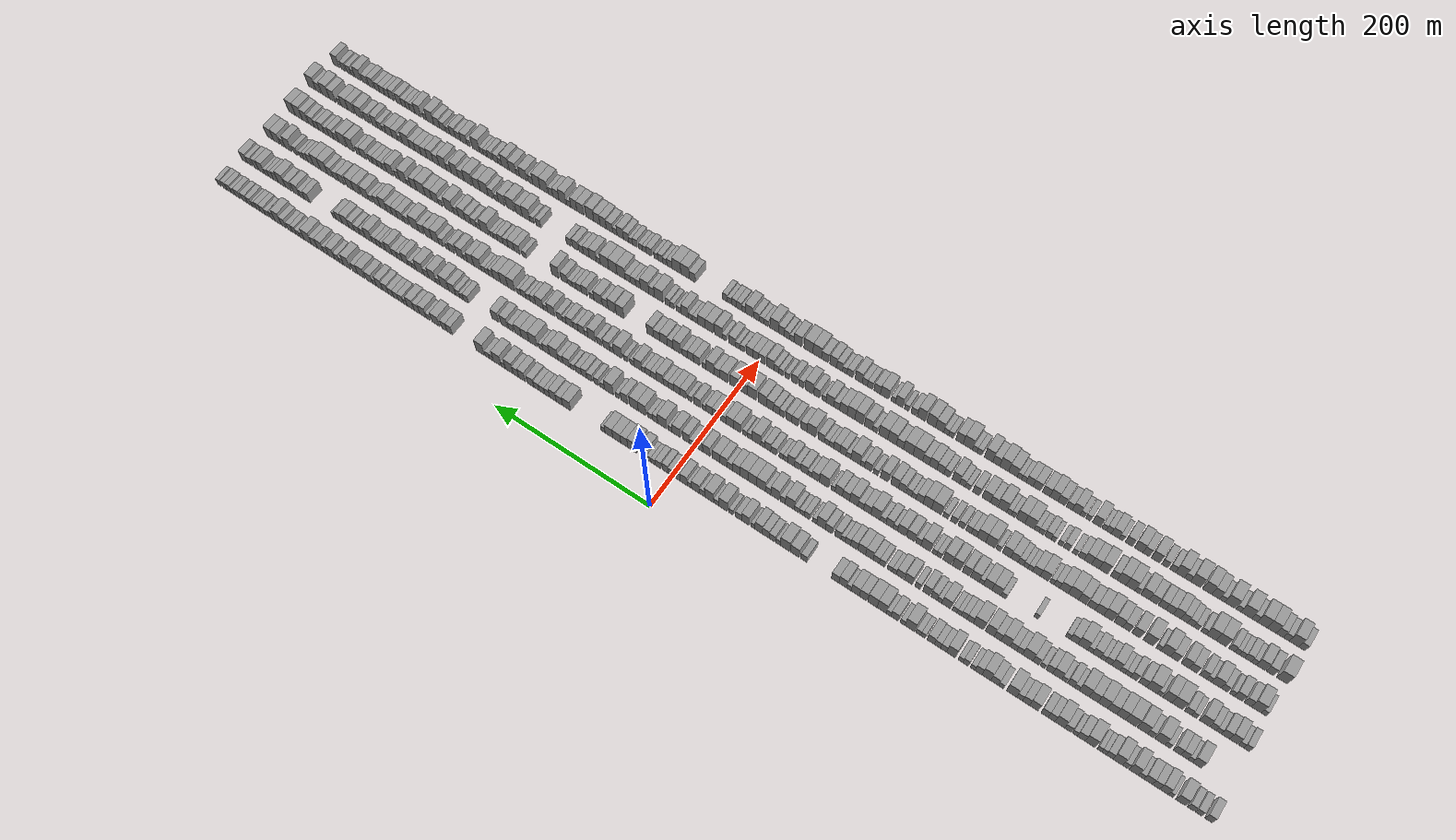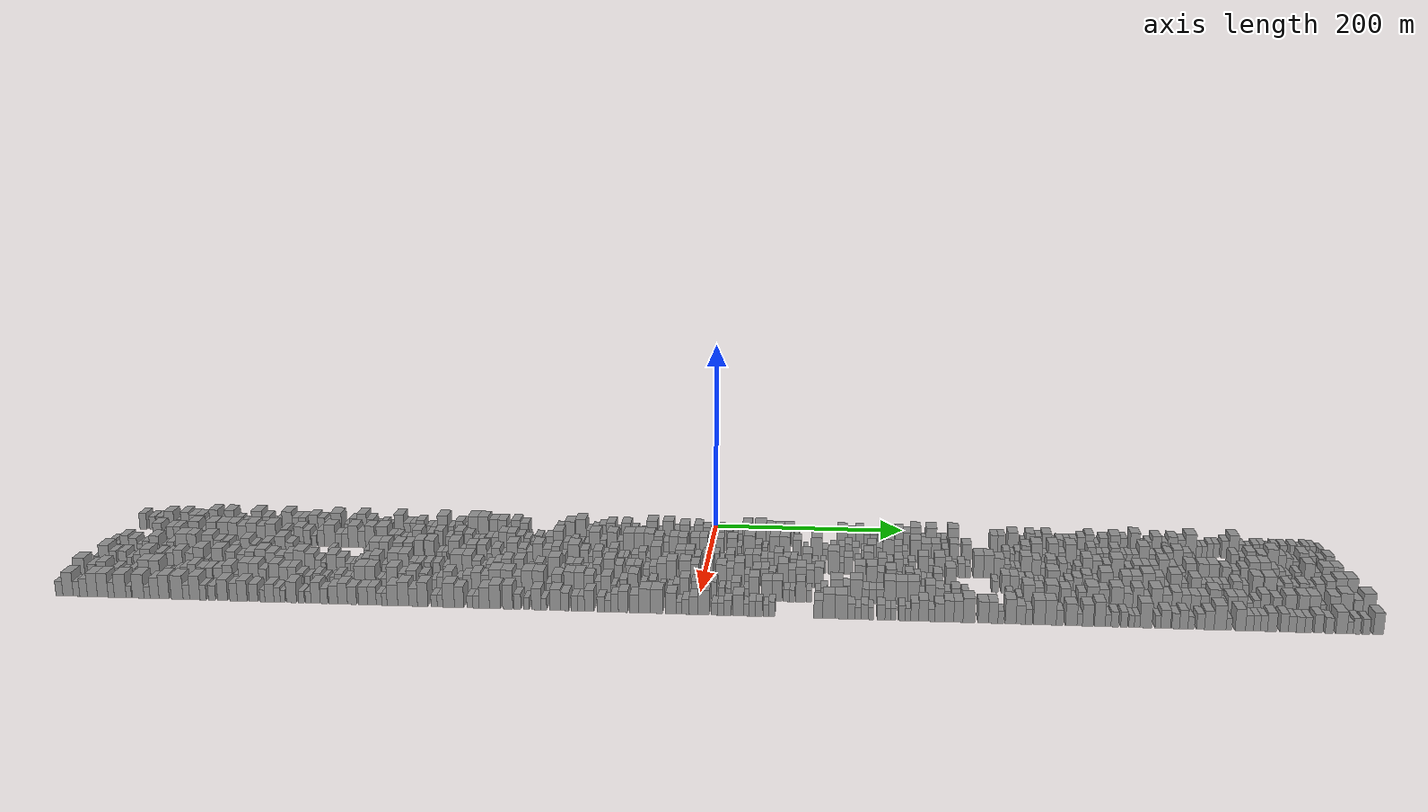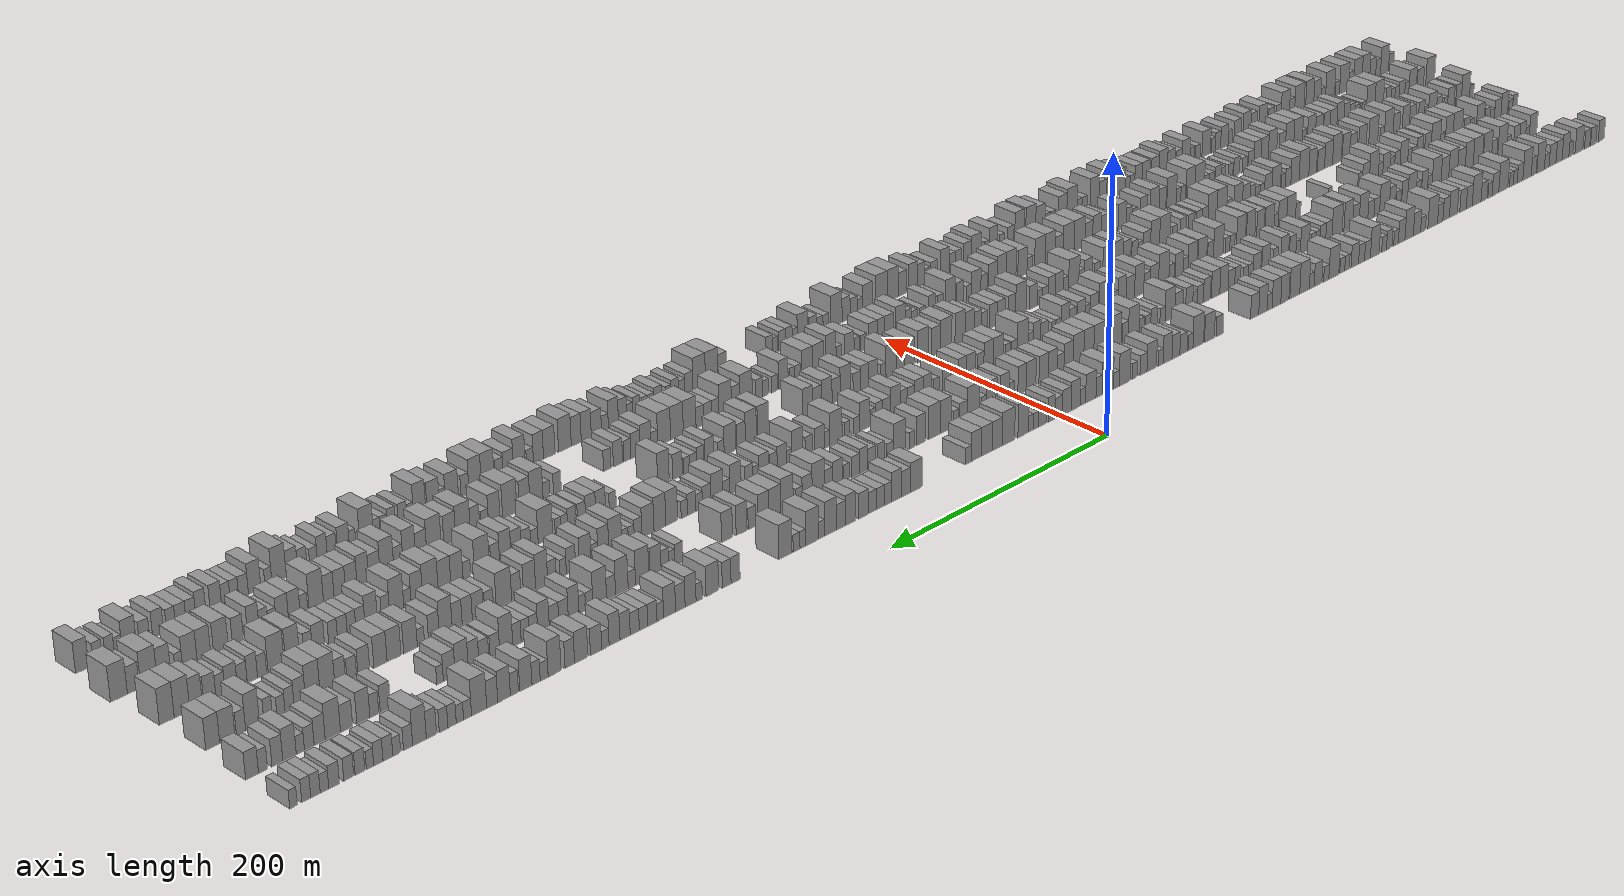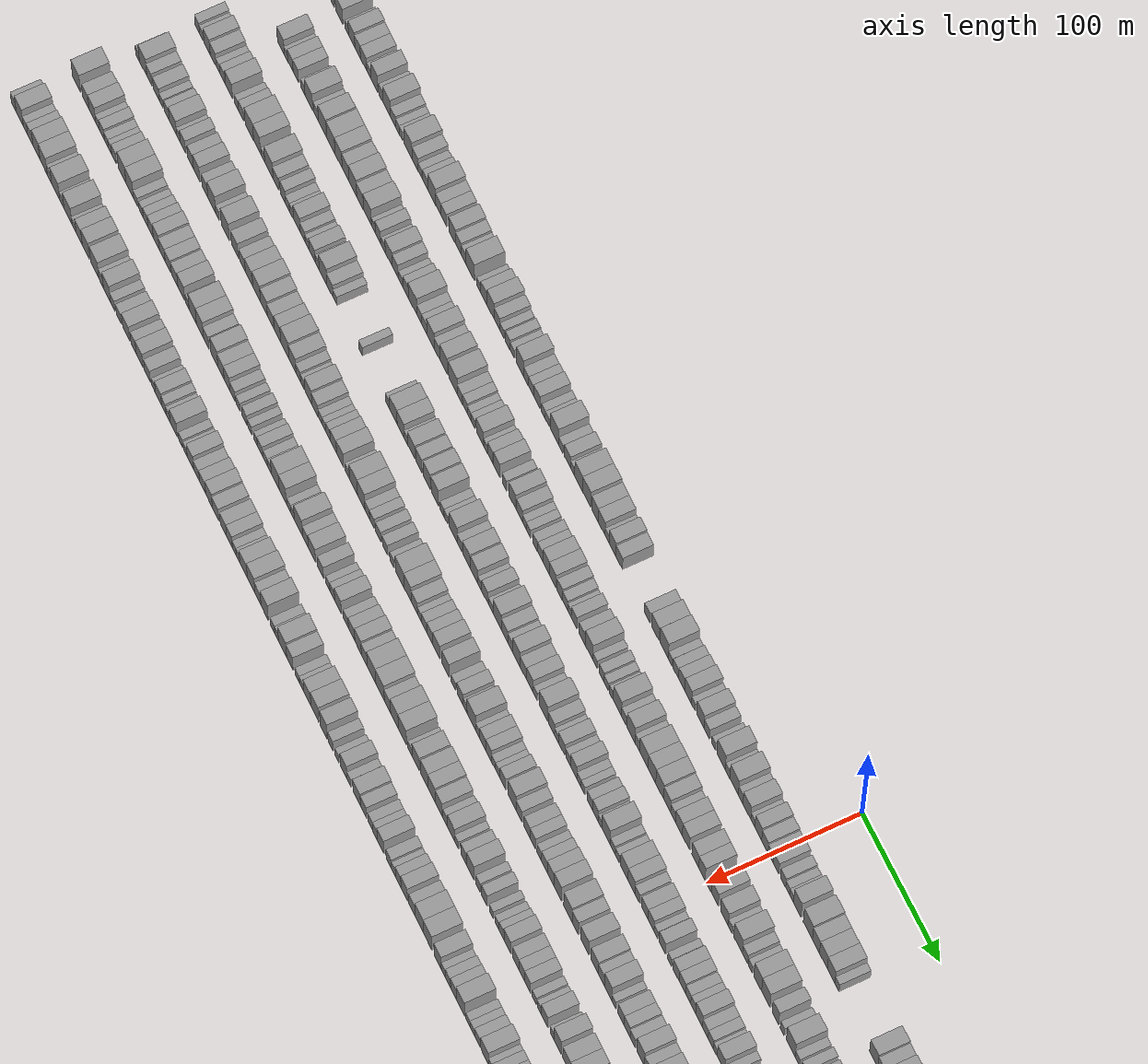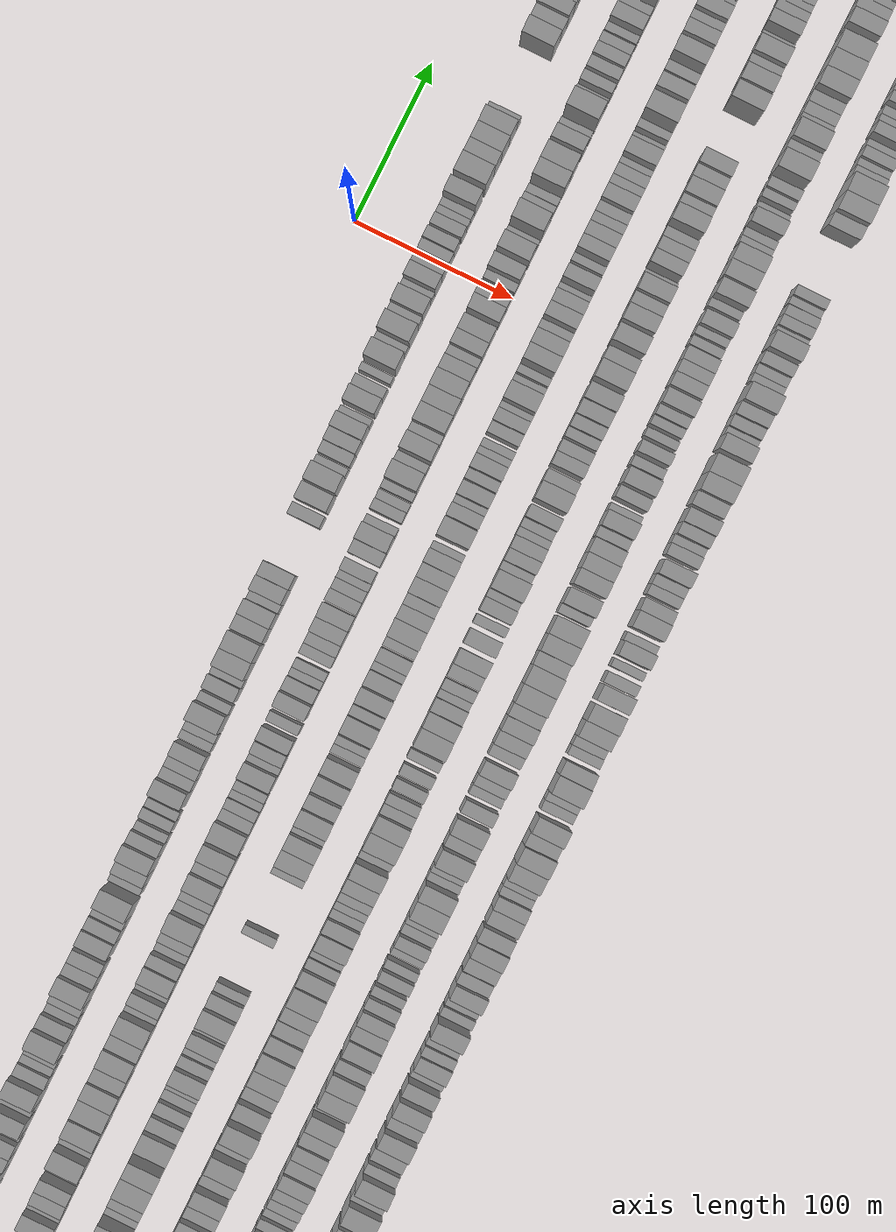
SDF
<sdf version="1.6">
 <world name="default">
  <scene>
   <sky><clouds><speed>12</speed></clouds></sky>
   <ambient>0.4 0.4 0.4 1</ambient>
   <background>0.7 0.7 0.7 1</background>
   <shadows>1</shadows>
  </scene>
  <gravity>0 0 -9.8066</gravity>
  <magnetic_field>6e-06 2.3e-05 -4.2e-05</magnetic_field>
  <physics default="0" name="default_physics" type="ode">
   <ode>
    <solver>
     <type>quick</type>
     <iters>10</iters>
     <sor>1.0</sor>
     <use_dynamic_moi_rescaling>0</use_dynamic_moi_rescaling>
    </solver>
    <constraints>
     <cfm>0</cfm>
     <erp>0.2</erp>
     <contact_max_correcting_vel>100</contact_max_correcting_vel>
     <contact_surface_layer>0.001</contact_surface_layer>
    </constraints>
   </ode>
   <max_step_size>0.004</max_step_size>
   <real_time_factor>1</real_time_factor>
   <real_time_update_rate>250</real_time_update_rate>
  </physics>
  <light name="sun" type="directional">
   <pose>0 0 10 0 0 0</pose>
   <diffuse>0.8 0.8 0.8 1</diffuse>
   <specular>0.2 0.2 0.2 1</specular>
   <attenuation>
    <range>1000</range>
    <constant>0.9</constant>
    <linear>0.01</linear>
    <quadratic>0.001</quadratic>
   </attenuation>
   <direction>-0.5 0.1 -0.9</direction>
  </light>
  <model name="building_1">
   <static>1</static>
   <pose>50.0000 -616.0429 0 0.000000 0.000000 0.000000</pose>
   <link name="link">
    <pose>0 0 9.00 0 0 0</pose>
    <collision name="collision"><geometry><box><size>20.0000 7.9141 18.0000</size></box></geometry></collision>
    <visual name="visual">
     <cast_shadows>0</cast_shadows>
     <geometry><box><size>20.0000 7.9141 18.0000</size></box></geometry>
     <material>
      <script>
       <uri>model://grey_wall/materials/scripts</uri>
       <uri>model://grey_wall/materials/textures</uri>
       <name>vrc/grey_wall</name>
      </script>
     </material>
    </visual>
   </link>
  </model>
  <model name="building_2">
   <static>1</static>
   <pose>50.0000 -605.5663 0 0.000000 0.000000 0.000000</pose>
   <link name="link">
    <pose>0 0 7.50 0 0 0</pose>
    <collision name="collision"><geometry><box><size>20.0000 7.0392 15.0000</size></box></geometry></collision>
    <visual name="visual">
     <cast_shadows>0</cast_shadows>
     <geometry><box><size>20.0000 7.0392 15.0000</size></box></geometry>
     <material>
      <script>
       <uri>model://grey_wall/materials/scripts</uri>
       <uri>model://grey_wall/materials/textures</uri>
       <name>vrc/grey_wall</name>
      </script>
     </material>
    </visual>
   </link>
  </model>
  <model name="building_3">
   <static>1</static>
   <pose>50.0000 -597.5090 0 0.000000 0.000000 0.000000</pose>
   <link name="link">
    <pose>0 0 7.50 0 0 0</pose>
    <collision name="collision"><geometry><box><size>20.0000 7.0753 15.0000</size></box></geometry></collision>
    <visual name="visual">
     <cast_shadows>0</cast_shadows>
     <geometry><box><size>20.0000 7.0753 15.0000</size></box></geometry>
     <material>
      <script>
       <uri>model://grey_wall/materials/scripts</uri>
       <uri>model://grey_wall/materials/textures</uri>
       <name>vrc/grey_wall</name>
      </script>
     </material>
    </visual>
   </link>
  </model>
  <model name="building_4">
   <static>1</static>
   <pose>50.0000 -586.7905 0 0.000000 0.000000 0.000000</pose>
   <link name="link">
    <pose>0 0 10.50 0 0 0</pose>
    <collision name="collision"><geometry><box><size>20.0000 10.3617 21.0000</size></box></geometry></collision>
    <visual name="visual">
     <cast_shadows>0</cast_shadows>
     <geometry><box><size>20.0000 10.3617 21.0000</size></box></geometry>
     <material>
      <script>
       <uri>model://grey_wall/materials/scripts</uri>
       <uri>model://grey_wall/materials/textures</uri>
       <name>vrc/grey_wall</name>
      </script>
     </material>
    </visual>
   </link>
  </model>
  <model name="building_5">
   <static>1</static>
   <pose>50.0000 -576.1209 0 0.000000 0.000000 0.000000</pose>
   <link name="link">
    <pose>0 0 6.00 0 0 0</pose>
    <collision name="collision"><geometry><box><size>20.0000 4.9775 12.0000</size></box></geometry></collision>
    <visual name="visual">
     <cast_shadows>0</cast_shadows>
     <geometry><box><size>20.0000 4.9775 12.0000</size></box></geometry>
     <material>
      <script>
       <uri>model://grey_wall/materials/scripts</uri>
       <uri>model://grey_wall/materials/textures</uri>
       <name>vrc/grey_wall</name>
      </script>
     </material>
    </visual>
   </link>
  </model>
  <model name="building_6">
   <static>1</static>
   <pose>50.0000 -569.1569 0 0.000000 0.000000 0.000000</pose>
   <link name="link">
    <pose>0 0 10.50 0 0 0</pose>
    <collision name="collision"><geometry><box><size>20.0000 8.9505 21.0000</size></box></geometry></collision>
    <visual name="visual">
     <cast_shadows>0</cast_shadows>
     <geometry><box><size>20.0000 8.9505 21.0000</size></box></geometry>
     <material>
      <script>
       <uri>model://grey_wall/materials/scripts</uri>
       <uri>model://grey_wall/materials/textures</uri>
       <name>vrc/grey_wall</name>
      </script>
     </material>
    </visual>
   </link>
  </model>
  <model name="building_7">
   <static>1</static>
   <pose>50.0000 -560.7042 0 0.000000 0.000000 0.000000</pose>
   <link name="link">
    <pose>0 0 9.00 0 0 0</pose>
    <collision name="collision"><geometry><box><size>20.0000 7.9549 18.0000</size></box></geometry></collision>
    <visual name="visual">
     <cast_shadows>0</cast_shadows>
     <geometry><box><size>20.0000 7.9549 18.0000</size></box></geometry>
     <material>
      <script>
       <uri>model://grey_wall/materials/scripts</uri>
       <uri>model://grey_wall/materials/textures</uri>
       <name>vrc/grey_wall</name>
      </script>
     </material>
    </visual>
   </link>
  </model>
  <model name="building_8">
   <static>1</static>
   <pose>50.0000 -552.2844 0 0.000000 0.000000 0.000000</pose>
   <link name="link">
    <pose>0 0 9.00 0 0 0</pose>
    <collision name="collision"><geometry><box><size>20.0000 8.8848 18.0000</size></box></geometry></collision>
    <visual name="visual">
     <cast_shadows>0</cast_shadows>
     <geometry><box><size>20.0000 8.8848 18.0000</size></box></geometry>
     <material>
      <script>
       <uri>model://grey_wall/materials/scripts</uri>
       <uri>model://grey_wall/materials/textures</uri>
       <name>vrc/grey_wall</name>
      </script>
     </material>
    </visual>
   </link>
  </model>
  <model name="building_9">
   <static>1</static>
   <pose>50.0000 -544.8420 0 0.000000 0.000000 0.000000</pose>
   <link name="link">
    <pose>0 0 6.00 0 0 0</pose>
    <collision name="collision"><geometry><box><size>20.0000 5.9998 12.0000</size></box></geometry></collision>
    <visual name="visual">
     <cast_shadows>0</cast_shadows>
     <geometry><box><size>20.0000 5.9998 12.0000</size></box></geometry>
     <material>
      <script>
       <uri>model://grey_wall/materials/scripts</uri>
       <uri>model://grey_wall/materials/textures</uri>
       <name>vrc/grey_wall</name>
      </script>
     </material>
    </visual>
   </link>
  </model>
  <model name="building_10">
   <static>1</static>
   <pose>50.0000 -536.9732 0 0.000000 0.000000 0.000000</pose>
   <link name="link">
    <pose>0 0 12.00 0 0 0</pose>
    <collision name="collision"><geometry><box><size>20.0000 9.7379 24.0000</size></box></geometry></collision>
    <visual name="visual">
     <cast_shadows>0</cast_shadows>
     <geometry><box><size>20.0000 9.7379 24.0000</size></box></geometry>
     <material>
      <script>
       <uri>model://grey_wall/materials/scripts</uri>
       <uri>model://grey_wall/materials/textures</uri>
       <name>vrc/grey_wall</name>
      </script>
     </material>
    </visual>
   </link>
  </model>
  <model name="building_11">
   <static>1</static>
   <pose>50.0000 -528.0566 0 0.000000 0.000000 0.000000</pose>
   <link name="link">
    <pose>0 0 7.50 0 0 0</pose>
    <collision name="collision"><geometry><box><size>20.0000 6.0952 15.0000</size></box></geometry></collision>
    <visual name="visual">
     <cast_shadows>0</cast_shadows>
     <geometry><box><size>20.0000 6.0952 15.0000</size></box></geometry>
     <material>
      <script>
       <uri>model://grey_wall/materials/scripts</uri>
       <uri>model://grey_wall/materials/textures</uri>
       <name>vrc/grey_wall</name>
      </script>
     </material>
    </visual>
   </link>
  </model>
  <model name="building_12">
   <static>1</static>
   <pose>50.0000 -519.7207 0 0.000000 0.000000 0.000000</pose>
   <link name="link">
    <pose>0 0 12.00 0 0 0</pose>
    <collision name="collision"><geometry><box><size>20.0000 10.5767 24.0000</size></box></geometry></collision>
    <visual name="visual">
     <cast_shadows>0</cast_shadows>
     <geometry><box><size>20.0000 10.5767 24.0000</size></box></geometry>
     <material>
      <script>
       <uri>model://grey_wall/materials/scripts</uri>
       <uri>model://grey_wall/materials/textures</uri>
       <name>vrc/grey_wall</name>
      </script>
     </material>
    </visual>
   </link>
  </model>
  <model name="building_13">
   <static>1</static>
   <pose>50.0000 -510.8066 0 0.000000 0.000000 0.000000</pose>
   <link name="link">
    <pose>0 0 7.50 0 0 0</pose>
    <collision name="collision"><geometry><box><size>20.0000 7.2513 15.0000</size></box></geometry></collision>
    <visual name="visual">
     <cast_shadows>0</cast_shadows>
     <geometry><box><size>20.0000 7.2513 15.0000</size></box></geometry>
     <material>
      <script>
       <uri>model://grey_wall/materials/scripts</uri>
       <uri>model://grey_wall/materials/textures</uri>
       <name>vrc/grey_wall</name>
      </script>
     </material>
    </visual>
   </link>
  </model>
  <model name="building_14">
   <static>1</static>
   <pose>50.0000 -504.7270 0 0.000000 0.000000 0.000000</pose>
   <link name="link">
    <pose>0 0 6.00 0 0 0</pose>
    <collision name="collision"><geometry><box><size>20.0000 4.9079 12.0000</size></box></geometry></collision>
    <visual name="visual">
     <cast_shadows>0</cast_shadows>
     <geometry><box><size>20.0000 4.9079 12.0000</size></box></geometry>
     <material>
      <script>
       <uri>model://grey_wall/materials/scripts</uri>
       <uri>model://grey_wall/materials/textures</uri>
       <name>vrc/grey_wall</name>
      </script>
     </material>
    </visual>
   </link>
  </model>
  <model name="building_15">
   <static>1</static>
   <pose>50.0000 -499.8452 0 0.000000 0.000000 0.000000</pose>
   <link name="link">
    <pose>0 0 6.00 0 0 0</pose>
    <collision name="collision"><geometry><box><size>20.0000 4.8557 12.0000</size></box></geometry></collision>
    <visual name="visual">
     <cast_shadows>0</cast_shadows>
     <geometry><box><size>20.0000 4.8557 12.0000</size></box></geometry>
     <material>
      <script>
       <uri>model://grey_wall/materials/scripts</uri>
       <uri>model://grey_wall/materials/textures</uri>
       <name>vrc/grey_wall</name>
      </script>
     </material>
    </visual>
   </link>
  </model>
  <model name="building_16">
   <static>1</static>
   <pose>50.0000 -489.7420 0 0.000000 0.000000 0.000000</pose>
   <link name="link">
    <pose>0 0 12.00 0 0 0</pose>
    <collision name="collision"><geometry><box><size>20.0000 11.3507 24.0000</size></box></geometry></collision>
    <visual name="visual">
     <cast_shadows>0</cast_shadows>
     <geometry><box><size>20.0000 11.3507 24.0000</size></box></geometry>
     <material>
      <script>
       <uri>model://grey_wall/materials/scripts</uri>
       <uri>model://grey_wall/materials/textures</uri>
       <name>vrc/grey_wall</name>
      </script>
     </material>
    </visual>
   </link>
  </model>
  <model name="building_17">
   <static>1</static>
   <pose>50.0000 -479.8857 0 0.000000 0.000000 0.000000</pose>
   <link name="link">
    <pose>0 0 9.00 0 0 0</pose>
    <collision name="collision"><geometry><box><size>20.0000 8.3620 18.0000</size></box></geometry></collision>
    <visual name="visual">
     <cast_shadows>0</cast_shadows>
     <geometry><box><size>20.0000 8.3620 18.0000</size></box></geometry>
     <material>
      <script>
       <uri>model://grey_wall/materials/scripts</uri>
       <uri>model://grey_wall/materials/textures</uri>
       <name>vrc/grey_wall</name>
      </script>
     </material>
    </visual>
   </link>
  </model>
  <model name="building_18">
   <static>1</static>
   <pose>50.0000 -473.1001 0 0.000000 0.000000 0.000000</pose>
   <link name="link">
    <pose>0 0 6.00 0 0 0</pose>
    <collision name="collision"><geometry><box><size>20.0000 5.2090 12.0000</size></box></geometry></collision>
    <visual name="visual">
     <cast_shadows>0</cast_shadows>
     <geometry><box><size>20.0000 5.2090 12.0000</size></box></geometry>
     <material>
      <script>
       <uri>model://grey_wall/materials/scripts</uri>
       <uri>model://grey_wall/materials/textures</uri>
       <name>vrc/grey_wall</name>
      </script>
     </material>
    </visual>
   </link>
  </model>
  <model name="building_19">
   <static>1</static>
   <pose>50.0000 -465.7536 0 0.000000 0.000000 0.000000</pose>
   <link name="link">
    <pose>0 0 7.50 0 0 0</pose>
    <collision name="collision"><geometry><box><size>20.0000 7.4841 15.0000</size></box></geometry></collision>
    <visual name="visual">
     <cast_shadows>0</cast_shadows>
     <geometry><box><size>20.0000 7.4841 15.0000</size></box></geometry>
     <material>
      <script>
       <uri>model://grey_wall/materials/scripts</uri>
       <uri>model://grey_wall/materials/textures</uri>
       <name>vrc/grey_wall</name>
      </script>
     </material>
    </visual>
   </link>
  </model>
  <model name="building_20">
   <static>1</static>
   <pose>50.0000 -456.5789 0 0.000000 0.000000 0.000000</pose>
   <link name="link">
    <pose>0 0 12.00 0 0 0</pose>
    <collision name="collision"><geometry><box><size>20.0000 10.8653 24.0000</size></box></geometry></collision>
    <visual name="visual">
     <cast_shadows>0</cast_shadows>
     <geometry><box><size>20.0000 10.8653 24.0000</size></box></geometry>
     <material>
      <script>
       <uri>model://grey_wall/materials/scripts</uri>
       <uri>model://grey_wall/materials/textures</uri>
       <name>vrc/grey_wall</name>
      </script>
     </material>
    </visual>
   </link>
  </model>
  <model name="building_21">
   <static>1</static>
   <pose>50.0000 -447.4521 0 0.000000 0.000000 0.000000</pose>
   <link name="link">
    <pose>0 0 9.00 0 0 0</pose>
    <collision name="collision"><geometry><box><size>20.0000 7.3885 18.0000</size></box></geometry></collision>
    <visual name="visual">
     <cast_shadows>0</cast_shadows>
     <geometry><box><size>20.0000 7.3885 18.0000</size></box></geometry>
     <material>
      <script>
       <uri>model://grey_wall/materials/scripts</uri>
       <uri>model://grey_wall/materials/textures</uri>
       <name>vrc/grey_wall</name>
      </script>
     </material>
    </visual>
   </link>
  </model>
  <model name="building_22">
   <static>1</static>
   <pose>50.0000 -439.8254 0 0.000000 0.000000 0.000000</pose>
   <link name="link">
    <pose>0 0 9.00 0 0 0</pose>
    <collision name="collision"><geometry><box><size>20.0000 7.8648 18.0000</size></box></geometry></collision>
    <visual name="visual">
     <cast_shadows>0</cast_shadows>
     <geometry><box><size>20.0000 7.8648 18.0000</size></box></geometry>
     <material>
      <script>
       <uri>model://grey_wall/materials/scripts</uri>
       <uri>model://grey_wall/materials/textures</uri>
       <name>vrc/grey_wall</name>
      </script>
     </material>
    </visual>
   </link>
  </model>
  <model name="building_23">
   <static>1</static>
   <pose>50.0000 -428.0699 0 0.000000 0.000000 0.000000</pose>
   <link name="link">
    <pose>0 0 10.50 0 0 0</pose>
    <collision name="collision"><geometry><box><size>20.0000 9.6462 21.0000</size></box></geometry></collision>
    <visual name="visual">
     <cast_shadows>0</cast_shadows>
     <geometry><box><size>20.0000 9.6462 21.0000</size></box></geometry>
     <material>
      <script>
       <uri>model://grey_wall/materials/scripts</uri>
       <uri>model://grey_wall/materials/textures</uri>
       <name>vrc/grey_wall</name>
      </script>
     </material>
    </visual>
   </link>
  </model>
  <model name="building_24">
   <static>1</static>
   <pose>50.0000 -419.3129 0 0.000000 0.000000 0.000000</pose>
   <link name="link">
    <pose>0 0 9.00 0 0 0</pose>
    <collision name="collision"><geometry><box><size>20.0000 7.8678 18.0000</size></box></geometry></collision>
    <visual name="visual">
     <cast_shadows>0</cast_shadows>
     <geometry><box><size>20.0000 7.8678 18.0000</size></box></geometry>
     <material>
      <script>
       <uri>model://grey_wall/materials/scripts</uri>
       <uri>model://grey_wall/materials/textures</uri>
       <name>vrc/grey_wall</name>
      </script>
     </material>
    </visual>
   </link>
  </model>
  <model name="building_25">
   <static>1</static>
   <pose>50.0000 -412.1500 0 0.000000 0.000000 0.000000</pose>
   <link name="link">
    <pose>0 0 7.50 0 0 0</pose>
    <collision name="collision"><geometry><box><size>20.0000 6.4581 15.0000</size></box></geometry></collision>
    <visual name="visual">
     <cast_shadows>0</cast_shadows>
     <geometry><box><size>20.0000 6.4581 15.0000</size></box></geometry>
     <material>
      <script>
       <uri>model://grey_wall/materials/scripts</uri>
       <uri>model://grey_wall/materials/textures</uri>
       <name>vrc/grey_wall</name>
      </script>
     </material>
    </visual>
   </link>
  </model>
  <model name="building_26">
   <static>1</static>
   <pose>50.0000 -403.1334 0 0.000000 0.000000 0.000000</pose>
   <link name="link">
    <pose>0 0 12.00 0 0 0</pose>
    <collision name="collision"><geometry><box><size>20.0000 11.5751 24.0000</size></box></geometry></collision>
    <visual name="visual">
     <cast_shadows>0</cast_shadows>
     <geometry><box><size>20.0000 11.5751 24.0000</size></box></geometry>
     <material>
      <script>
       <uri>model://grey_wall/materials/scripts</uri>
       <uri>model://grey_wall/materials/textures</uri>
       <name>vrc/grey_wall</name>
      </script>
     </material>
    </visual>
   </link>
  </model>
  <model name="building_27">
   <static>1</static>
   <pose>50.0000 -391.4568 0 0.000000 0.000000 0.000000</pose>
   <link name="link">
    <pose>0 0 6.00 0 0 0</pose>
    <collision name="collision"><geometry><box><size>20.0000 5.7781 12.0000</size></box></geometry></collision>
    <visual name="visual">
     <cast_shadows>0</cast_shadows>
     <geometry><box><size>20.0000 5.7781 12.0000</size></box></geometry>
     <material>
      <script>
       <uri>model://grey_wall/materials/scripts</uri>
       <uri>model://grey_wall/materials/textures</uri>
       <name>vrc/grey_wall</name>
      </script>
     </material>
    </visual>
   </link>
  </model>
  <model name="building_28">
   <static>1</static>
   <pose>50.0000 -384.2687 0 0.000000 0.000000 0.000000</pose>
   <link name="link">
    <pose>0 0 9.00 0 0 0</pose>
    <collision name="collision"><geometry><box><size>20.0000 8.5982 18.0000</size></box></geometry></collision>
    <visual name="visual">
     <cast_shadows>0</cast_shadows>
     <geometry><box><size>20.0000 8.5982 18.0000</size></box></geometry>
     <material>
      <script>
       <uri>model://grey_wall/materials/scripts</uri>
       <uri>model://grey_wall/materials/textures</uri>
       <name>vrc/grey_wall</name>
      </script>
     </material>
    </visual>
   </link>
  </model>
  <model name="building_29">
   <static>1</static>
   <pose>50.0000 -374.9771 0 0.000000 0.000000 0.000000</pose>
   <link name="link">
    <pose>0 0 12.00 0 0 0</pose>
    <collision name="collision"><geometry><box><size>20.0000 9.9851 24.0000</size></box></geometry></collision>
    <visual name="visual">
     <cast_shadows>0</cast_shadows>
     <geometry><box><size>20.0000 9.9851 24.0000</size></box></geometry>
     <material>
      <script>
       <uri>model://grey_wall/materials/scripts</uri>
       <uri>model://grey_wall/materials/textures</uri>
       <name>vrc/grey_wall</name>
      </script>
     </material>
    </visual>
   </link>
  </model>
  <model name="building_30">
   <static>1</static>
   <pose>50.0000 -366.0663 0 0.000000 0.000000 0.000000</pose>
   <link name="link">
    <pose>0 0 9.00 0 0 0</pose>
    <collision name="collision"><geometry><box><size>20.0000 7.8364 18.0000</size></box></geometry></collision>
    <visual name="visual">
     <cast_shadows>0</cast_shadows>
     <geometry><box><size>20.0000 7.8364 18.0000</size></box></geometry>
     <material>
      <script>
       <uri>model://grey_wall/materials/scripts</uri>
       <uri>model://grey_wall/materials/textures</uri>
       <name>vrc/grey_wall</name>
      </script>
     </material>
    </visual>
   </link>
  </model>
  <model name="building_31">
   <static>1</static>
   <pose>50.0000 -359.4116 0 0.000000 0.000000 0.000000</pose>
   <link name="link">
    <pose>0 0 6.00 0 0 0</pose>
    <collision name="collision"><geometry><box><size>20.0000 5.4730 12.0000</size></box></geometry></collision>
    <visual name="visual">
     <cast_shadows>0</cast_shadows>
     <geometry><box><size>20.0000 5.4730 12.0000</size></box></geometry>
     <material>
      <script>
       <uri>model://grey_wall/materials/scripts</uri>
       <uri>model://grey_wall/materials/textures</uri>
       <name>vrc/grey_wall</name>
      </script>
     </material>
    </visual>
   </link>
  </model>
  <model name="building_32">
   <static>1</static>
   <pose>50.0000 -351.4500 0 0.000000 0.000000 0.000000</pose>
   <link name="link">
    <pose>0 0 7.50 0 0 0</pose>
    <collision name="collision"><geometry><box><size>20.0000 6.4502 15.0000</size></box></geometry></collision>
    <visual name="visual">
     <cast_shadows>0</cast_shadows>
     <geometry><box><size>20.0000 6.4502 15.0000</size></box></geometry>
     <material>
      <script>
       <uri>model://grey_wall/materials/scripts</uri>
       <uri>model://grey_wall/materials/textures</uri>
       <name>vrc/grey_wall</name>
      </script>
     </material>
    </visual>
   </link>
  </model>
  <model name="building_33">
   <static>1</static>
   <pose>50.0000 -345.4507 0 0.000000 0.000000 0.000000</pose>
   <link name="link">
    <pose>0 0 6.00 0 0 0</pose>
    <collision name="collision"><geometry><box><size>20.0000 5.5484 12.0000</size></box></geometry></collision>
    <visual name="visual">
     <cast_shadows>0</cast_shadows>
     <geometry><box><size>20.0000 5.5484 12.0000</size></box></geometry>
     <material>
      <script>
       <uri>model://grey_wall/materials/scripts</uri>
       <uri>model://grey_wall/materials/textures</uri>
       <name>vrc/grey_wall</name>
      </script>
     </material>
    </visual>
   </link>
  </model>
  <model name="building_34">
   <static>1</static>
   <pose>50.0000 -334.6388 0 0.000000 0.000000 0.000000</pose>
   <link name="link">
    <pose>0 0 12.00 0 0 0</pose>
    <collision name="collision"><geometry><box><size>20.0000 10.0754 24.0000</size></box></geometry></collision>
    <visual name="visual">
     <cast_shadows>0</cast_shadows>
     <geometry><box><size>20.0000 10.0754 24.0000</size></box></geometry>
     <material>
      <script>
       <uri>model://grey_wall/materials/scripts</uri>
       <uri>model://grey_wall/materials/textures</uri>
       <name>vrc/grey_wall</name>
      </script>
     </material>
    </visual>
   </link>
  </model>
  <model name="building_35">
   <static>1</static>
   <pose>50.0000 -326.1645 0 0.000000 0.000000 0.000000</pose>
   <link name="link">
    <pose>0 0 7.50 0 0 0</pose>
    <collision name="collision"><geometry><box><size>20.0000 6.8732 15.0000</size></box></geometry></collision>
    <visual name="visual">
     <cast_shadows>0</cast_shadows>
     <geometry><box><size>20.0000 6.8732 15.0000</size></box></geometry>
     <material>
      <script>
       <uri>model://grey_wall/materials/scripts</uri>
       <uri>model://grey_wall/materials/textures</uri>
       <name>vrc/grey_wall</name>
      </script>
     </material>
    </visual>
   </link>
  </model>
  <model name="building_36">
   <static>1</static>
   <pose>50.0000 -319.3176 0 0.000000 0.000000 0.000000</pose>
   <link name="link">
    <pose>0 0 7.50 0 0 0</pose>
    <collision name="collision"><geometry><box><size>20.0000 6.8206 15.0000</size></box></geometry></collision>
    <visual name="visual">
     <cast_shadows>0</cast_shadows>
     <geometry><box><size>20.0000 6.8206 15.0000</size></box></geometry>
     <material>
      <script>
       <uri>model://grey_wall/materials/scripts</uri>
       <uri>model://grey_wall/materials/textures</uri>
       <name>vrc/grey_wall</name>
      </script>
     </material>
    </visual>
   </link>
  </model>
  <model name="building_37">
   <static>1</static>
   <pose>50.0000 -311.5870 0 0.000000 0.000000 0.000000</pose>
   <link name="link">
    <pose>0 0 9.00 0 0 0</pose>
    <collision name="collision"><geometry><box><size>20.0000 8.6405 18.0000</size></box></geometry></collision>
    <visual name="visual">
     <cast_shadows>0</cast_shadows>
     <geometry><box><size>20.0000 8.6405 18.0000</size></box></geometry>
     <material>
      <script>
       <uri>model://grey_wall/materials/scripts</uri>
       <uri>model://grey_wall/materials/textures</uri>
       <name>vrc/grey_wall</name>
      </script>
     </material>
    </visual>
   </link>
  </model>
  <model name="building_38">
   <static>1</static>
   <pose>50.0000 -302.6083 0 0.000000 0.000000 0.000000</pose>
   <link name="link">
    <pose>0 0 6.00 0 0 0</pose>
    <collision name="collision"><geometry><box><size>20.0000 5.3169 12.0000</size></box></geometry></collision>
    <visual name="visual">
     <cast_shadows>0</cast_shadows>
     <geometry><box><size>20.0000 5.3169 12.0000</size></box></geometry>
     <material>
      <script>
       <uri>model://grey_wall/materials/scripts</uri>
       <uri>model://grey_wall/materials/textures</uri>
       <name>vrc/grey_wall</name>
      </script>
     </material>
    </visual>
   </link>
  </model>
  <model name="building_39">
   <static>1</static>
   <pose>50.0000 -297.0786 0 0.000000 0.000000 0.000000</pose>
   <link name="link">
    <pose>0 0 6.00 0 0 0</pose>
    <collision name="collision"><geometry><box><size>20.0000 5.7423 12.0000</size></box></geometry></collision>
    <visual name="visual">
     <cast_shadows>0</cast_shadows>
     <geometry><box><size>20.0000 5.7423 12.0000</size></box></geometry>
     <material>
      <script>
       <uri>model://grey_wall/materials/scripts</uri>
       <uri>model://grey_wall/materials/textures</uri>
       <name>vrc/grey_wall</name>
      </script>
     </material>
    </visual>
   </link>
  </model>
  <model name="building_40">
   <static>1</static>
   <pose>50.0000 -287.5664 0 0.000000 0.000000 0.000000</pose>
   <link name="link">
    <pose>0 0 12.00 0 0 0</pose>
    <collision name="collision"><geometry><box><size>20.0000 11.2821 24.0000</size></box></geometry></collision>
    <visual name="visual">
     <cast_shadows>0</cast_shadows>
     <geometry><box><size>20.0000 11.2821 24.0000</size></box></geometry>
     <material>
      <script>
       <uri>model://grey_wall/materials/scripts</uri>
       <uri>model://grey_wall/materials/textures</uri>
       <name>vrc/grey_wall</name>
      </script>
     </material>
    </visual>
   </link>
  </model>
  <model name="building_41">
   <static>1</static>
   <pose>50.0000 -278.9384 0 0.000000 0.000000 0.000000</pose>
   <link name="link">
    <pose>0 0 6.00 0 0 0</pose>
    <collision name="collision"><geometry><box><size>20.0000 5.9738 12.0000</size></box></geometry></collision>
    <visual name="visual">
     <cast_shadows>0</cast_shadows>
     <geometry><box><size>20.0000 5.9738 12.0000</size></box></geometry>
     <material>
      <script>
       <uri>model://grey_wall/materials/scripts</uri>
       <uri>model://grey_wall/materials/textures</uri>
       <name>vrc/grey_wall</name>
      </script>
     </material>
    </visual>
   </link>
  </model>
  <model name="building_42">
   <static>1</static>
   <pose>50.0000 -269.6416 0 0.000000 0.000000 0.000000</pose>
   <link name="link">
    <pose>0 0 9.00 0 0 0</pose>
    <collision name="collision"><geometry><box><size>20.0000 8.6198 18.0000</size></box></geometry></collision>
    <visual name="visual">
     <cast_shadows>0</cast_shadows>
     <geometry><box><size>20.0000 8.6198 18.0000</size></box></geometry>
     <material>
      <script>
       <uri>model://grey_wall/materials/scripts</uri>
       <uri>model://grey_wall/materials/textures</uri>
       <name>vrc/grey_wall</name>
      </script>
     </material>
    </visual>
   </link>
  </model>
  <model name="building_43">
   <static>1</static>
   <pose>50.0000 -262.6278 0 0.000000 0.000000 0.000000</pose>
   <link name="link">
    <pose>0 0 6.00 0 0 0</pose>
    <collision name="collision"><geometry><box><size>20.0000 5.4079 12.0000</size></box></geometry></collision>
    <visual name="visual">
     <cast_shadows>0</cast_shadows>
     <geometry><box><size>20.0000 5.4079 12.0000</size></box></geometry>
     <material>
      <script>
       <uri>model://grey_wall/materials/scripts</uri>
       <uri>model://grey_wall/materials/textures</uri>
       <name>vrc/grey_wall</name>
      </script>
     </material>
    </visual>
   </link>
  </model>
  <model name="building_44">
   <static>1</static>
   <pose>50.0000 -254.5875 0 0.000000 0.000000 0.000000</pose>
   <link name="link">
    <pose>0 0 12.00 0 0 0</pose>
    <collision name="collision"><geometry><box><size>20.0000 10.6726 24.0000</size></box></geometry></collision>
    <visual name="visual">
     <cast_shadows>0</cast_shadows>
     <geometry><box><size>20.0000 10.6726 24.0000</size></box></geometry>
     <material>
      <script>
       <uri>model://grey_wall/materials/scripts</uri>
       <uri>model://grey_wall/materials/textures</uri>
       <name>vrc/grey_wall</name>
      </script>
     </material>
    </visual>
   </link>
  </model>
  <model name="building_45">
   <static>1</static>
   <pose>50.0000 -243.7102 0 0.000000 0.000000 0.000000</pose>
   <link name="link">
    <pose>0 0 12.00 0 0 0</pose>
    <collision name="collision"><geometry><box><size>20.0000 11.0819 24.0000</size></box></geometry></collision>
    <visual name="visual">
     <cast_shadows>0</cast_shadows>
     <geometry><box><size>20.0000 11.0819 24.0000</size></box></geometry>
     <material>
      <script>
       <uri>model://grey_wall/materials/scripts</uri>
       <uri>model://grey_wall/materials/textures</uri>
       <name>vrc/grey_wall</name>
      </script>
     </material>
    </visual>
   </link>
  </model>
  <model name="building_46">
   <static>1</static>
   <pose>50.0000 -232.6948 0 0.000000 0.000000 0.000000</pose>
   <link name="link">
    <pose>0 0 10.50 0 0 0</pose>
    <collision name="collision"><geometry><box><size>20.0000 8.9489 21.0000</size></box></geometry></collision>
    <visual name="visual">
     <cast_shadows>0</cast_shadows>
     <geometry><box><size>20.0000 8.9489 21.0000</size></box></geometry>
     <material>
      <script>
       <uri>model://grey_wall/materials/scripts</uri>
       <uri>model://grey_wall/materials/textures</uri>
       <name>vrc/grey_wall</name>
      </script>
     </material>
    </visual>
   </link>
  </model>
  <model name="building_47">
   <static>1</static>
   <pose>50.0000 -223.4624 0 0.000000 0.000000 0.000000</pose>
   <link name="link">
    <pose>0 0 10.50 0 0 0</pose>
    <collision name="collision"><geometry><box><size>20.0000 9.5160 21.0000</size></box></geometry></collision>
    <visual name="visual">
     <cast_shadows>0</cast_shadows>
     <geometry><box><size>20.0000 9.5160 21.0000</size></box></geometry>
     <material>
      <script>
       <uri>model://grey_wall/materials/scripts</uri>
       <uri>model://grey_wall/materials/textures</uri>
       <name>vrc/grey_wall</name>
      </script>
     </material>
    </visual>
   </link>
  </model>
  <model name="building_48">
   <static>1</static>
   <pose>50.0000 -216.0085 0 0.000000 0.000000 0.000000</pose>
   <link name="link">
    <pose>0 0 6.00 0 0 0</pose>
    <collision name="collision"><geometry><box><size>20.0000 5.3917 12.0000</size></box></geometry></collision>
    <visual name="visual">
     <cast_shadows>0</cast_shadows>
     <geometry><box><size>20.0000 5.3917 12.0000</size></box></geometry>
     <material>
      <script>
       <uri>model://grey_wall/materials/scripts</uri>
       <uri>model://grey_wall/materials/textures</uri>
       <name>vrc/grey_wall</name>
      </script>
     </material>
    </visual>
   </link>
  </model>
  <model name="building_49">
   <static>1</static>
   <pose>50.0000 -208.6979 0 0.000000 0.000000 0.000000</pose>
   <link name="link">
    <pose>0 0 10.50 0 0 0</pose>
    <collision name="collision"><geometry><box><size>20.0000 9.2296 21.0000</size></box></geometry></collision>
    <visual name="visual">
     <cast_shadows>0</cast_shadows>
     <geometry><box><size>20.0000 9.2296 21.0000</size></box></geometry>
     <material>
      <script>
       <uri>model://grey_wall/materials/scripts</uri>
       <uri>model://grey_wall/materials/textures</uri>
       <name>vrc/grey_wall</name>
      </script>
     </material>
    </visual>
   </link>
  </model>
  <model name="building_50">
   <static>1</static>
   <pose>50.0000 -199.6259 0 0.000000 0.000000 0.000000</pose>
   <link name="link">
    <pose>0 0 9.00 0 0 0</pose>
    <collision name="collision"><geometry><box><size>20.0000 8.9143 18.0000</size></box></geometry></collision>
    <visual name="visual">
     <cast_shadows>0</cast_shadows>
     <geometry><box><size>20.0000 8.9143 18.0000</size></box></geometry>
     <material>
      <script>
       <uri>model://grey_wall/materials/scripts</uri>
       <uri>model://grey_wall/materials/textures</uri>
       <name>vrc/grey_wall</name>
      </script>
     </material>
    </visual>
   </link>
  </model>
  <model name="building_51">
   <static>1</static>
   <pose>50.0000 -162.0807 0 0.000000 0.000000 0.000000</pose>
   <link name="link">
    <pose>0 0 7.50 0 0 0</pose>
    <collision name="collision"><geometry><box><size>20.0000 7.3920 15.0000</size></box></geometry></collision>
    <visual name="visual">
     <cast_shadows>0</cast_shadows>
     <geometry><box><size>20.0000 7.3920 15.0000</size></box></geometry>
     <material>
      <script>
       <uri>model://grey_wall/materials/scripts</uri>
       <uri>model://grey_wall/materials/textures</uri>
       <name>vrc/grey_wall</name>
      </script>
     </material>
    </visual>
   </link>
  </model>
  <model name="building_52">
   <static>1</static>
   <pose>50.0000 -151.1443 0 0.000000 0.000000 0.000000</pose>
   <link name="link">
    <pose>0 0 10.50 0 0 0</pose>
    <collision name="collision"><geometry><box><size>20.0000 10.4809 21.0000</size></box></geometry></collision>
    <visual name="visual">
     <cast_shadows>0</cast_shadows>
     <geometry><box><size>20.0000 10.4809 21.0000</size></box></geometry>
     <material>
      <script>
       <uri>model://grey_wall/materials/scripts</uri>
       <uri>model://grey_wall/materials/textures</uri>
       <name>vrc/grey_wall</name>
      </script>
     </material>
    </visual>
   </link>
  </model>
  <model name="building_53">
   <static>1</static>
   <pose>50.0000 -139.3174 0 0.000000 0.000000 0.000000</pose>
   <link name="link">
    <pose>0 0 12.00 0 0 0</pose>
    <collision name="collision"><geometry><box><size>20.0000 11.1729 24.0000</size></box></geometry></collision>
    <visual name="visual">
     <cast_shadows>0</cast_shadows>
     <geometry><box><size>20.0000 11.1729 24.0000</size></box></geometry>
     <material>
      <script>
       <uri>model://grey_wall/materials/scripts</uri>
       <uri>model://grey_wall/materials/textures</uri>
       <name>vrc/grey_wall</name>
      </script>
     </material>
    </visual>
   </link>
  </model>
  <model name="building_54">
   <static>1</static>
   <pose>50.0000 -131.1116 0 0.000000 0.000000 0.000000</pose>
   <link name="link">
    <pose>0 0 6.00 0 0 0</pose>
    <collision name="collision"><geometry><box><size>20.0000 5.2386 12.0000</size></box></geometry></collision>
    <visual name="visual">
     <cast_shadows>0</cast_shadows>
     <geometry><box><size>20.0000 5.2386 12.0000</size></box></geometry>
     <material>
      <script>
       <uri>model://grey_wall/materials/scripts</uri>
       <uri>model://grey_wall/materials/textures</uri>
       <name>vrc/grey_wall</name>
      </script>
     </material>
    </visual>
   </link>
  </model>
  <model name="building_55">
   <static>1</static>
   <pose>50.0000 -123.7501 0 0.000000 0.000000 0.000000</pose>
   <link name="link">
    <pose>0 0 7.50 0 0 0</pose>
    <collision name="collision"><geometry><box><size>20.0000 7.4845 15.0000</size></box></geometry></collision>
    <visual name="visual">
     <cast_shadows>0</cast_shadows>
     <geometry><box><size>20.0000 7.4845 15.0000</size></box></geometry>
     <material>
      <script>
       <uri>model://grey_wall/materials/scripts</uri>
       <uri>model://grey_wall/materials/textures</uri>
       <name>vrc/grey_wall</name>
      </script>
     </material>
    </visual>
   </link>
  </model>
  <model name="building_56">
   <static>1</static>
   <pose>50.0000 -115.9099 0 0.000000 0.000000 0.000000</pose>
   <link name="link">
    <pose>0 0 9.00 0 0 0</pose>
    <collision name="collision"><geometry><box><size>20.0000 8.1960 18.0000</size></box></geometry></collision>
    <visual name="visual">
     <cast_shadows>0</cast_shadows>
     <geometry><box><size>20.0000 8.1960 18.0000</size></box></geometry>
     <material>
      <script>
       <uri>model://grey_wall/materials/scripts</uri>
       <uri>model://grey_wall/materials/textures</uri>
       <name>vrc/grey_wall</name>
      </script>
     </material>
    </visual>
   </link>
  </model>
  <model name="building_57">
   <static>1</static>
   <pose>50.0000 -107.2792 0 0.000000 0.000000 0.000000</pose>
   <link name="link">
    <pose>0 0 10.50 0 0 0</pose>
    <collision name="collision"><geometry><box><size>20.0000 9.0653 21.0000</size></box></geometry></collision>
    <visual name="visual">
     <cast_shadows>0</cast_shadows>
     <geometry><box><size>20.0000 9.0653 21.0000</size></box></geometry>
     <material>
      <script>
       <uri>model://grey_wall/materials/scripts</uri>
       <uri>model://grey_wall/materials/textures</uri>
       <name>vrc/grey_wall</name>
      </script>
     </material>
    </visual>
   </link>
  </model>
  <model name="building_58">
   <static>1</static>
   <pose>50.0000 -100.2945 0 0.000000 0.000000 0.000000</pose>
   <link name="link">
    <pose>0 0 6.00 0 0 0</pose>
    <collision name="collision"><geometry><box><size>20.0000 4.9041 12.0000</size></box></geometry></collision>
    <visual name="visual">
     <cast_shadows>0</cast_shadows>
     <geometry><box><size>20.0000 4.9041 12.0000</size></box></geometry>
     <material>
      <script>
       <uri>model://grey_wall/materials/scripts</uri>
       <uri>model://grey_wall/materials/textures</uri>
       <name>vrc/grey_wall</name>
      </script>
     </material>
    </visual>
   </link>
  </model>
  <model name="building_59">
   <static>1</static>
   <pose>50.0000 -90.9520 0 0.000000 0.000000 0.000000</pose>
   <link name="link">
    <pose>0 0 10.50 0 0 0</pose>
    <collision name="collision"><geometry><box><size>20.0000 9.7809 21.0000</size></box></geometry></collision>
    <visual name="visual">
     <cast_shadows>0</cast_shadows>
     <geometry><box><size>20.0000 9.7809 21.0000</size></box></geometry>
     <material>
      <script>
       <uri>model://grey_wall/materials/scripts</uri>
       <uri>model://grey_wall/materials/textures</uri>
       <name>vrc/grey_wall</name>
      </script>
     </material>
    </visual>
   </link>
  </model>
  <model name="building_60">
   <static>1</static>
   <pose>50.0000 -82.4660 0 0.000000 0.000000 0.000000</pose>
   <link name="link">
    <pose>0 0 7.50 0 0 0</pose>
    <collision name="collision"><geometry><box><size>20.0000 7.1911 15.0000</size></box></geometry></collision>
    <visual name="visual">
     <cast_shadows>0</cast_shadows>
     <geometry><box><size>20.0000 7.1911 15.0000</size></box></geometry>
     <material>
      <script>
       <uri>model://grey_wall/materials/scripts</uri>
       <uri>model://grey_wall/materials/textures</uri>
       <name>vrc/grey_wall</name>
      </script>
     </material>
    </visual>
   </link>
  </model>
  <model name="building_61">
   <static>1</static>
   <pose>50.0000 -73.4531 0 0.000000 0.000000 0.000000</pose>
   <link name="link">
    <pose>0 0 6.00 0 0 0</pose>
    <collision name="collision"><geometry><box><size>20.0000 4.8346 12.0000</size></box></geometry></collision>
    <visual name="visual">
     <cast_shadows>0</cast_shadows>
     <geometry><box><size>20.0000 4.8346 12.0000</size></box></geometry>
     <material>
      <script>
       <uri>model://grey_wall/materials/scripts</uri>
       <uri>model://grey_wall/materials/textures</uri>
       <name>vrc/grey_wall</name>
      </script>
     </material>
    </visual>
   </link>
  </model>
  <model name="building_62">
   <static>1</static>
   <pose>50.0000 -63.4703 0 0.000000 0.000000 0.000000</pose>
   <link name="link">
    <pose>0 0 12.00 0 0 0</pose>
    <collision name="collision"><geometry><box><size>20.0000 11.1311 24.0000</size></box></geometry></collision>
    <visual name="visual">
     <cast_shadows>0</cast_shadows>
     <geometry><box><size>20.0000 11.1311 24.0000</size></box></geometry>
     <material>
      <script>
       <uri>model://grey_wall/materials/scripts</uri>
       <uri>model://grey_wall/materials/textures</uri>
       <name>vrc/grey_wall</name>
      </script>
     </material>
    </visual>
   </link>
  </model>
  <model name="building_63">
   <static>1</static>
   <pose>50.0000 -54.9149 0 0.000000 0.000000 0.000000</pose>
   <link name="link">
    <pose>0 0 6.00 0 0 0</pose>
    <collision name="collision"><geometry><box><size>20.0000 5.9796 12.0000</size></box></geometry></collision>
    <visual name="visual">
     <cast_shadows>0</cast_shadows>
     <geometry><box><size>20.0000 5.9796 12.0000</size></box></geometry>
     <material>
      <script>
       <uri>model://grey_wall/materials/scripts</uri>
       <uri>model://grey_wall/materials/textures</uri>
       <name>vrc/grey_wall</name>
      </script>
     </material>
    </visual>
   </link>
  </model>
  <model name="building_64">
   <static>1</static>
   <pose>50.0000 -46.3006 0 0.000000 0.000000 0.000000</pose>
   <link name="link">
    <pose>0 0 12.00 0 0 0</pose>
    <collision name="collision"><geometry><box><size>20.0000 11.2490 24.0000</size></box></geometry></collision>
    <visual name="visual">
     <cast_shadows>0</cast_shadows>
     <geometry><box><size>20.0000 11.2490 24.0000</size></box></geometry>
     <material>
      <script>
       <uri>model://grey_wall/materials/scripts</uri>
       <uri>model://grey_wall/materials/textures</uri>
       <name>vrc/grey_wall</name>
      </script>
     </material>
    </visual>
   </link>
  </model>
  <model name="building_65">
   <static>1</static>
   <pose>50.0000 -37.6016 0 0.000000 0.000000 0.000000</pose>
   <link name="link">
    <pose>0 0 7.50 0 0 0</pose>
    <collision name="collision"><geometry><box><size>20.0000 6.1490 15.0000</size></box></geometry></collision>
    <visual name="visual">
     <cast_shadows>0</cast_shadows>
     <geometry><box><size>20.0000 6.1490 15.0000</size></box></geometry>
     <material>
      <script>
       <uri>model://grey_wall/materials/scripts</uri>
       <uri>model://grey_wall/materials/textures</uri>
       <name>vrc/grey_wall</name>
      </script>
     </material>
    </visual>
   </link>
  </model>
  <model name="building_66">
   <static>1</static>
   <pose>50.0000 -29.3880 0 0.000000 0.000000 0.000000</pose>
   <link name="link">
    <pose>0 0 10.50 0 0 0</pose>
    <collision name="collision"><geometry><box><size>20.0000 10.2781 21.0000</size></box></geometry></collision>
    <visual name="visual">
     <cast_shadows>0</cast_shadows>
     <geometry><box><size>20.0000 10.2781 21.0000</size></box></geometry>
     <material>
      <script>
       <uri>model://grey_wall/materials/scripts</uri>
       <uri>model://grey_wall/materials/textures</uri>
       <name>vrc/grey_wall</name>
      </script>
     </material>
    </visual>
   </link>
  </model>
  <model name="building_67">
   <static>1</static>
   <pose>50.0000 -21.5326 0 0.000000 0.000000 0.000000</pose>
   <link name="link">
    <pose>0 0 6.00 0 0 0</pose>
    <collision name="collision"><geometry><box><size>20.0000 5.4326 12.0000</size></box></geometry></collision>
    <visual name="visual">
     <cast_shadows>0</cast_shadows>
     <geometry><box><size>20.0000 5.4326 12.0000</size></box></geometry>
     <material>
      <script>
       <uri>model://grey_wall/materials/scripts</uri>
       <uri>model://grey_wall/materials/textures</uri>
       <name>vrc/grey_wall</name>
      </script>
     </material>
    </visual>
   </link>
  </model>
  <model name="building_68">
   <static>1</static>
   <pose>50.0000 -14.3611 0 0.000000 0.000000 0.000000</pose>
   <link name="link">
    <pose>0 0 10.50 0 0 0</pose>
    <collision name="collision"><geometry><box><size>20.0000 8.9104 21.0000</size></box></geometry></collision>
    <visual name="visual">
     <cast_shadows>0</cast_shadows>
     <geometry><box><size>20.0000 8.9104 21.0000</size></box></geometry>
     <material>
      <script>
       <uri>model://grey_wall/materials/scripts</uri>
       <uri>model://grey_wall/materials/textures</uri>
       <name>vrc/grey_wall</name>
      </script>
     </material>
    </visual>
   </link>
  </model>
  <model name="building_69">
   <static>1</static>
   <pose>50.0000 -5.7404 0 0.000000 0.000000 0.000000</pose>
   <link name="link">
    <pose>0 0 9.00 0 0 0</pose>
    <collision name="collision"><geometry><box><size>20.0000 8.3310 18.0000</size></box></geometry></collision>
    <visual name="visual">
     <cast_shadows>0</cast_shadows>
     <geometry><box><size>20.0000 8.3310 18.0000</size></box></geometry>
     <material>
      <script>
       <uri>model://grey_wall/materials/scripts</uri>
       <uri>model://grey_wall/materials/textures</uri>
       <name>vrc/grey_wall</name>
      </script>
     </material>
    </visual>
   </link>
  </model>
  <model name="building_70">
   <static>1</static>
   <pose>50.0000 1.8893 0 0.000000 0.000000 0.000000</pose>
   <link name="link">
    <pose>0 0 7.50 0 0 0</pose>
    <collision name="collision"><geometry><box><size>20.0000 6.9284 15.0000</size></box></geometry></collision>
    <visual name="visual">
     <cast_shadows>0</cast_shadows>
     <geometry><box><size>20.0000 6.9284 15.0000</size></box></geometry>
     <material>
      <script>
       <uri>model://grey_wall/materials/scripts</uri>
       <uri>model://grey_wall/materials/textures</uri>
       <name>vrc/grey_wall</name>
      </script>
     </material>
    </visual>
   </link>
  </model>
  <model name="building_71">
   <static>1</static>
   <pose>50.0000 8.9826 0 0.000000 0.000000 0.000000</pose>
   <link name="link">
    <pose>0 0 9.00 0 0 0</pose>
    <collision name="collision"><geometry><box><size>20.0000 7.2582 18.0000</size></box></geometry></collision>
    <visual name="visual">
     <cast_shadows>0</cast_shadows>
     <geometry><box><size>20.0000 7.2582 18.0000</size></box></geometry>
     <material>
      <script>
       <uri>model://grey_wall/materials/scripts</uri>
       <uri>model://grey_wall/materials/textures</uri>
       <name>vrc/grey_wall</name>
      </script>
     </material>
    </visual>
   </link>
  </model>
  <model name="building_72">
   <static>1</static>
   <pose>50.0000 18.1349 0 0.000000 0.000000 0.000000</pose>
   <link name="link">
    <pose>0 0 7.50 0 0 0</pose>
    <collision name="collision"><geometry><box><size>20.0000 7.0466 15.0000</size></box></geometry></collision>
    <visual name="visual">
     <cast_shadows>0</cast_shadows>
     <geometry><box><size>20.0000 7.0466 15.0000</size></box></geometry>
     <material>
      <script>
       <uri>model://grey_wall/materials/scripts</uri>
       <uri>model://grey_wall/materials/textures</uri>
       <name>vrc/grey_wall</name>
      </script>
     </material>
    </visual>
   </link>
  </model>
  <model name="building_73">
   <static>1</static>
   <pose>50.0000 24.2900 0 0.000000 0.000000 0.000000</pose>
   <link name="link">
    <pose>0 0 6.00 0 0 0</pose>
    <collision name="collision"><geometry><box><size>20.0000 5.2636 12.0000</size></box></geometry></collision>
    <visual name="visual">
     <cast_shadows>0</cast_shadows>
     <geometry><box><size>20.0000 5.2636 12.0000</size></box></geometry>
     <material>
      <script>
       <uri>model://grey_wall/materials/scripts</uri>
       <uri>model://grey_wall/materials/textures</uri>
       <name>vrc/grey_wall</name>
      </script>
     </material>
    </visual>
   </link>
  </model>
  <model name="building_74">
   <static>1</static>
   <pose>50.0000 29.3867 0 0.000000 0.000000 0.000000</pose>
   <link name="link">
    <pose>0 0 6.00 0 0 0</pose>
    <collision name="collision"><geometry><box><size>20.0000 4.9297 12.0000</size></box></geometry></collision>
    <visual name="visual">
     <cast_shadows>0</cast_shadows>
     <geometry><box><size>20.0000 4.9297 12.0000</size></box></geometry>
     <material>
      <script>
       <uri>model://grey_wall/materials/scripts</uri>
       <uri>model://grey_wall/materials/textures</uri>
       <name>vrc/grey_wall</name>
      </script>
     </material>
    </visual>
   </link>
  </model>
  <model name="building_75">
   <static>1</static>
   <pose>50.0000 36.7452 0 0.000000 0.000000 0.000000</pose>
   <link name="link">
    <pose>0 0 12.00 0 0 0</pose>
    <collision name="collision"><geometry><box><size>20.0000 9.7875 24.0000</size></box></geometry></collision>
    <visual name="visual">
     <cast_shadows>0</cast_shadows>
     <geometry><box><size>20.0000 9.7875 24.0000</size></box></geometry>
     <material>
      <script>
       <uri>model://grey_wall/materials/scripts</uri>
       <uri>model://grey_wall/materials/textures</uri>
       <name>vrc/grey_wall</name>
      </script>
     </material>
    </visual>
   </link>
  </model>
  <model name="building_76">
   <static>1</static>
   <pose>50.0000 50.6311 0 0.000000 0.000000 0.000000</pose>
   <link name="link">
    <pose>0 0 12.00 0 0 0</pose>
    <collision name="collision"><geometry><box><size>20.0000 11.9843 24.0000</size></box></geometry></collision>
    <visual name="visual">
     <cast_shadows>0</cast_shadows>
     <geometry><box><size>20.0000 11.9843 24.0000</size></box></geometry>
     <material>
      <script>
       <uri>model://grey_wall/materials/scripts</uri>
       <uri>model://grey_wall/materials/textures</uri>
       <name>vrc/grey_wall</name>
      </script>
     </material>
    </visual>
   </link>
  </model>
  <model name="building_77">
   <static>1</static>
   <pose>50.0000 61.1894 0 0.000000 0.000000 0.000000</pose>
   <link name="link">
    <pose>0 0 10.50 0 0 0</pose>
    <collision name="collision"><geometry><box><size>20.0000 9.1323 21.0000</size></box></geometry></collision>
    <visual name="visual">
     <cast_shadows>0</cast_shadows>
     <geometry><box><size>20.0000 9.1323 21.0000</size></box></geometry>
     <material>
      <script>
       <uri>model://grey_wall/materials/scripts</uri>
       <uri>model://grey_wall/materials/textures</uri>
       <name>vrc/grey_wall</name>
      </script>
     </material>
    </visual>
   </link>
  </model>
  <model name="building_78">
   <static>1</static>
   <pose>50.0000 70.8475 0 0.000000 0.000000 0.000000</pose>
   <link name="link">
    <pose>0 0 10.50 0 0 0</pose>
    <collision name="collision"><geometry><box><size>20.0000 10.1840 21.0000</size></box></geometry></collision>
    <visual name="visual">
     <cast_shadows>0</cast_shadows>
     <geometry><box><size>20.0000 10.1840 21.0000</size></box></geometry>
     <material>
      <script>
       <uri>model://grey_wall/materials/scripts</uri>
       <uri>model://grey_wall/materials/textures</uri>
       <name>vrc/grey_wall</name>
      </script>
     </material>
    </visual>
   </link>
  </model>
  <model name="building_79">
   <static>1</static>
   <pose>50.0000 80.8786 0 0.000000 0.000000 0.000000</pose>
   <link name="link">
    <pose>0 0 10.50 0 0 0</pose>
    <collision name="collision"><geometry><box><size>20.0000 9.8780 21.0000</size></box></geometry></collision>
    <visual name="visual">
     <cast_shadows>0</cast_shadows>
     <geometry><box><size>20.0000 9.8780 21.0000</size></box></geometry>
     <material>
      <script>
       <uri>model://grey_wall/materials/scripts</uri>
       <uri>model://grey_wall/materials/textures</uri>
       <name>vrc/grey_wall</name>
      </script>
     </material>
    </visual>
   </link>
  </model>
  <model name="building_80">
   <static>1</static>
   <pose>50.0000 88.5451 0 0.000000 0.000000 0.000000</pose>
   <link name="link">
    <pose>0 0 6.00 0 0 0</pose>
    <collision name="collision"><geometry><box><size>20.0000 5.4552 12.0000</size></box></geometry></collision>
    <visual name="visual">
     <cast_shadows>0</cast_shadows>
     <geometry><box><size>20.0000 5.4552 12.0000</size></box></geometry>
     <material>
      <script>
       <uri>model://grey_wall/materials/scripts</uri>
       <uri>model://grey_wall/materials/textures</uri>
       <name>vrc/grey_wall</name>
      </script>
     </material>
    </visual>
   </link>
  </model>
  <model name="building_81">
   <static>1</static>
   <pose>50.0000 135.9728 0 0.000000 0.000000 0.000000</pose>
   <link name="link">
    <pose>0 0 10.50 0 0 0</pose>
    <collision name="collision"><geometry><box><size>20.0000 10.4667 21.0000</size></box></geometry></collision>
    <visual name="visual">
     <cast_shadows>0</cast_shadows>
     <geometry><box><size>20.0000 10.4667 21.0000</size></box></geometry>
     <material>
      <script>
       <uri>model://grey_wall/materials/scripts</uri>
       <uri>model://grey_wall/materials/textures</uri>
       <name>vrc/grey_wall</name>
      </script>
     </material>
    </visual>
   </link>
  </model>
  <model name="building_82">
   <static>1</static>
   <pose>50.0000 145.5064 0 0.000000 0.000000 0.000000</pose>
   <link name="link">
    <pose>0 0 9.00 0 0 0</pose>
    <collision name="collision"><geometry><box><size>20.0000 8.6006 18.0000</size></box></geometry></collision>
    <visual name="visual">
     <cast_shadows>0</cast_shadows>
     <geometry><box><size>20.0000 8.6006 18.0000</size></box></geometry>
     <material>
      <script>
       <uri>model://grey_wall/materials/scripts</uri>
       <uri>model://grey_wall/materials/textures</uri>
       <name>vrc/grey_wall</name>
      </script>
     </material>
    </visual>
   </link>
  </model>
  <model name="building_83">
   <static>1</static>
   <pose>50.0000 154.0730 0 0.000000 0.000000 0.000000</pose>
   <link name="link">
    <pose>0 0 10.50 0 0 0</pose>
    <collision name="collision"><geometry><box><size>20.0000 8.5325 21.0000</size></box></geometry></collision>
    <visual name="visual">
     <cast_shadows>0</cast_shadows>
     <geometry><box><size>20.0000 8.5325 21.0000</size></box></geometry>
     <material>
      <script>
       <uri>model://grey_wall/materials/scripts</uri>
       <uri>model://grey_wall/materials/textures</uri>
       <name>vrc/grey_wall</name>
      </script>
     </material>
    </visual>
   </link>
  </model>
  <model name="building_84">
   <static>1</static>
   <pose>50.0000 161.6211 0 0.000000 0.000000 0.000000</pose>
   <link name="link">
    <pose>0 0 7.50 0 0 0</pose>
    <collision name="collision"><geometry><box><size>20.0000 6.5638 15.0000</size></box></geometry></collision>
    <visual name="visual">
     <cast_shadows>0</cast_shadows>
     <geometry><box><size>20.0000 6.5638 15.0000</size></box></geometry>
     <material>
      <script>
       <uri>model://grey_wall/materials/scripts</uri>
       <uri>model://grey_wall/materials/textures</uri>
       <name>vrc/grey_wall</name>
      </script>
     </material>
    </visual>
   </link>
  </model>
  <model name="building_85">
   <static>1</static>
   <pose>50.0000 168.5790 0 0.000000 0.000000 0.000000</pose>
   <link name="link">
    <pose>0 0 7.50 0 0 0</pose>
    <collision name="collision"><geometry><box><size>20.0000 7.3518 15.0000</size></box></geometry></collision>
    <visual name="visual">
     <cast_shadows>0</cast_shadows>
     <geometry><box><size>20.0000 7.3518 15.0000</size></box></geometry>
     <material>
      <script>
       <uri>model://grey_wall/materials/scripts</uri>
       <uri>model://grey_wall/materials/textures</uri>
       <name>vrc/grey_wall</name>
      </script>
     </material>
    </visual>
   </link>
  </model>
  <model name="building_86">
   <static>1</static>
   <pose>50.0000 175.7212 0 0.000000 0.000000 0.000000</pose>
   <link name="link">
    <pose>0 0 7.50 0 0 0</pose>
    <collision name="collision"><geometry><box><size>20.0000 6.9327 15.0000</size></box></geometry></collision>
    <visual name="visual">
     <cast_shadows>0</cast_shadows>
     <geometry><box><size>20.0000 6.9327 15.0000</size></box></geometry>
     <material>
      <script>
       <uri>model://grey_wall/materials/scripts</uri>
       <uri>model://grey_wall/materials/textures</uri>
       <name>vrc/grey_wall</name>
      </script>
     </material>
    </visual>
   </link>
  </model>
  <model name="building_87">
   <static>1</static>
   <pose>50.0000 183.4900 0 0.000000 0.000000 0.000000</pose>
   <link name="link">
    <pose>0 0 9.00 0 0 0</pose>
    <collision name="collision"><geometry><box><size>20.0000 8.6049 18.0000</size></box></geometry></collision>
    <visual name="visual">
     <cast_shadows>0</cast_shadows>
     <geometry><box><size>20.0000 8.6049 18.0000</size></box></geometry>
     <material>
      <script>
       <uri>model://grey_wall/materials/scripts</uri>
       <uri>model://grey_wall/materials/textures</uri>
       <name>vrc/grey_wall</name>
      </script>
     </material>
    </visual>
   </link>
  </model>
  <model name="building_88">
   <static>1</static>
   <pose>50.0000 195.1148 0 0.000000 0.000000 0.000000</pose>
   <link name="link">
    <pose>0 0 10.50 0 0 0</pose>
    <collision name="collision"><geometry><box><size>20.0000 8.6447 21.0000</size></box></geometry></collision>
    <visual name="visual">
     <cast_shadows>0</cast_shadows>
     <geometry><box><size>20.0000 8.6447 21.0000</size></box></geometry>
     <material>
      <script>
       <uri>model://grey_wall/materials/scripts</uri>
       <uri>model://grey_wall/materials/textures</uri>
       <name>vrc/grey_wall</name>
      </script>
     </material>
    </visual>
   </link>
  </model>
  <model name="building_89">
   <static>1</static>
   <pose>50.0000 203.1701 0 0.000000 0.000000 0.000000</pose>
   <link name="link">
    <pose>0 0 9.00 0 0 0</pose>
    <collision name="collision"><geometry><box><size>20.0000 7.4660 18.0000</size></box></geometry></collision>
    <visual name="visual">
     <cast_shadows>0</cast_shadows>
     <geometry><box><size>20.0000 7.4660 18.0000</size></box></geometry>
     <material>
      <script>
       <uri>model://grey_wall/materials/scripts</uri>
       <uri>model://grey_wall/materials/textures</uri>
       <name>vrc/grey_wall</name>
      </script>
     </material>
    </visual>
   </link>
  </model>
  <model name="building_90">
   <static>1</static>
   <pose>50.0000 212.1653 0 0.000000 0.000000 0.000000</pose>
   <link name="link">
    <pose>0 0 12.00 0 0 0</pose>
    <collision name="collision"><geometry><box><size>20.0000 10.5243 24.0000</size></box></geometry></collision>
    <visual name="visual">
     <cast_shadows>0</cast_shadows>
     <geometry><box><size>20.0000 10.5243 24.0000</size></box></geometry>
     <material>
      <script>
       <uri>model://grey_wall/materials/scripts</uri>
       <uri>model://grey_wall/materials/textures</uri>
       <name>vrc/grey_wall</name>
      </script>
     </material>
    </visual>
   </link>
  </model>
  <model name="building_91">
   <static>1</static>
   <pose>50.0000 220.1326 0 0.000000 0.000000 0.000000</pose>
   <link name="link">
    <pose>0 0 6.00 0 0 0</pose>
    <collision name="collision"><geometry><box><size>20.0000 5.4104 12.0000</size></box></geometry></collision>
    <visual name="visual">
     <cast_shadows>0</cast_shadows>
     <geometry><box><size>20.0000 5.4104 12.0000</size></box></geometry>
     <material>
      <script>
       <uri>model://grey_wall/materials/scripts</uri>
       <uri>model://grey_wall/materials/textures</uri>
       <name>vrc/grey_wall</name>
      </script>
     </material>
    </visual>
   </link>
  </model>
  <model name="building_92">
   <static>1</static>
   <pose>50.0000 228.3330 0 0.000000 0.000000 0.000000</pose>
   <link name="link">
    <pose>0 0 12.00 0 0 0</pose>
    <collision name="collision"><geometry><box><size>20.0000 10.9905 24.0000</size></box></geometry></collision>
    <visual name="visual">
     <cast_shadows>0</cast_shadows>
     <geometry><box><size>20.0000 10.9905 24.0000</size></box></geometry>
     <material>
      <script>
       <uri>model://grey_wall/materials/scripts</uri>
       <uri>model://grey_wall/materials/textures</uri>
       <name>vrc/grey_wall</name>
      </script>
     </material>
    </visual>
   </link>
  </model>
  <model name="building_93">
   <static>1</static>
   <pose>50.0000 236.3212 0 0.000000 0.000000 0.000000</pose>
   <link name="link">
    <pose>0 0 6.00 0 0 0</pose>
    <collision name="collision"><geometry><box><size>20.0000 4.9857 12.0000</size></box></geometry></collision>
    <visual name="visual">
     <cast_shadows>0</cast_shadows>
     <geometry><box><size>20.0000 4.9857 12.0000</size></box></geometry>
     <material>
      <script>
       <uri>model://grey_wall/materials/scripts</uri>
       <uri>model://grey_wall/materials/textures</uri>
       <name>vrc/grey_wall</name>
      </script>
     </material>
    </visual>
   </link>
  </model>
  <model name="building_94">
   <static>1</static>
   <pose>50.0000 241.7361 0 0.000000 0.000000 0.000000</pose>
   <link name="link">
    <pose>0 0 6.00 0 0 0</pose>
    <collision name="collision"><geometry><box><size>20.0000 5.8442 12.0000</size></box></geometry></collision>
    <visual name="visual">
     <cast_shadows>0</cast_shadows>
     <geometry><box><size>20.0000 5.8442 12.0000</size></box></geometry>
     <material>
      <script>
       <uri>model://grey_wall/materials/scripts</uri>
       <uri>model://grey_wall/materials/textures</uri>
       <name>vrc/grey_wall</name>
      </script>
     </material>
    </visual>
   </link>
  </model>
  <model name="building_95">
   <static>1</static>
   <pose>50.0000 251.2319 0 0.000000 0.000000 0.000000</pose>
   <link name="link">
    <pose>0 0 12.00 0 0 0</pose>
    <collision name="collision"><geometry><box><size>20.0000 11.1474 24.0000</size></box></geometry></collision>
    <visual name="visual">
     <cast_shadows>0</cast_shadows>
     <geometry><box><size>20.0000 11.1474 24.0000</size></box></geometry>
     <material>
      <script>
       <uri>model://grey_wall/materials/scripts</uri>
       <uri>model://grey_wall/materials/textures</uri>
       <name>vrc/grey_wall</name>
      </script>
     </material>
    </visual>
   </link>
  </model>
  <model name="building_96">
   <static>1</static>
   <pose>50.0000 293.0761 0 0.000000 0.000000 0.000000</pose>
   <link name="link">
    <pose>0 0 9.00 0 0 0</pose>
    <collision name="collision"><geometry><box><size>20.0000 7.5137 18.0000</size></box></geometry></collision>
    <visual name="visual">
     <cast_shadows>0</cast_shadows>
     <geometry><box><size>20.0000 7.5137 18.0000</size></box></geometry>
     <material>
      <script>
       <uri>model://grey_wall/materials/scripts</uri>
       <uri>model://grey_wall/materials/textures</uri>
       <name>vrc/grey_wall</name>
      </script>
     </material>
    </visual>
   </link>
  </model>
  <model name="building_97">
   <static>1</static>
   <pose>50.0000 300.4410 0 0.000000 0.000000 0.000000</pose>
   <link name="link">
    <pose>0 0 9.00 0 0 0</pose>
    <collision name="collision"><geometry><box><size>20.0000 7.2160 18.0000</size></box></geometry></collision>
    <visual name="visual">
     <cast_shadows>0</cast_shadows>
     <geometry><box><size>20.0000 7.2160 18.0000</size></box></geometry>
     <material>
      <script>
       <uri>model://grey_wall/materials/scripts</uri>
       <uri>model://grey_wall/materials/textures</uri>
       <name>vrc/grey_wall</name>
      </script>
     </material>
    </visual>
   </link>
  </model>
  <model name="building_98">
   <static>1</static>
   <pose>50.0000 312.2567 0 0.000000 0.000000 0.000000</pose>
   <link name="link">
    <pose>0 0 10.50 0 0 0</pose>
    <collision name="collision"><geometry><box><size>20.0000 10.4154 21.0000</size></box></geometry></collision>
    <visual name="visual">
     <cast_shadows>0</cast_shadows>
     <geometry><box><size>20.0000 10.4154 21.0000</size></box></geometry>
     <material>
      <script>
       <uri>model://grey_wall/materials/scripts</uri>
       <uri>model://grey_wall/materials/textures</uri>
       <name>vrc/grey_wall</name>
      </script>
     </material>
    </visual>
   </link>
  </model>
  <model name="building_99">
   <static>1</static>
   <pose>50.0000 323.0105 0 0.000000 0.000000 0.000000</pose>
   <link name="link">
    <pose>0 0 6.00 0 0 0</pose>
    <collision name="collision"><geometry><box><size>20.0000 5.0921 12.0000</size></box></geometry></collision>
    <visual name="visual">
     <cast_shadows>0</cast_shadows>
     <geometry><box><size>20.0000 5.0921 12.0000</size></box></geometry>
     <material>
      <script>
       <uri>model://grey_wall/materials/scripts</uri>
       <uri>model://grey_wall/materials/textures</uri>
       <name>vrc/grey_wall</name>
      </script>
     </material>
    </visual>
   </link>
  </model>
  <model name="building_100">
   <static>1</static>
   <pose>50.0000 329.9913 0 0.000000 0.000000 0.000000</pose>
   <link name="link">
    <pose>0 0 10.50 0 0 0</pose>
    <collision name="collision"><geometry><box><size>20.0000 8.8696 21.0000</size></box></geometry></collision>
    <visual name="visual">
     <cast_shadows>0</cast_shadows>
     <geometry><box><size>20.0000 8.8696 21.0000</size></box></geometry>
     <material>
      <script>
       <uri>model://grey_wall/materials/scripts</uri>
       <uri>model://grey_wall/materials/textures</uri>
       <name>vrc/grey_wall</name>
      </script>
     </material>
    </visual>
   </link>
  </model>
  <model name="building_101">
   <static>1</static>
   <pose>50.0000 338.2777 0 0.000000 0.000000 0.000000</pose>
   <link name="link">
    <pose>0 0 9.00 0 0 0</pose>
    <collision name="collision"><geometry><box><size>20.0000 7.7031 18.0000</size></box></geometry></collision>
    <visual name="visual">
     <cast_shadows>0</cast_shadows>
     <geometry><box><size>20.0000 7.7031 18.0000</size></box></geometry>
     <material>
      <script>
       <uri>model://grey_wall/materials/scripts</uri>
       <uri>model://grey_wall/materials/textures</uri>
       <name>vrc/grey_wall</name>
      </script>
     </material>
    </visual>
   </link>
  </model>
  <model name="building_102">
   <static>1</static>
   <pose>50.0000 346.9442 0 0.000000 0.000000 0.000000</pose>
   <link name="link">
    <pose>0 0 10.50 0 0 0</pose>
    <collision name="collision"><geometry><box><size>20.0000 9.6299 21.0000</size></box></geometry></collision>
    <visual name="visual">
     <cast_shadows>0</cast_shadows>
     <geometry><box><size>20.0000 9.6299 21.0000</size></box></geometry>
     <material>
      <script>
       <uri>model://grey_wall/materials/scripts</uri>
       <uri>model://grey_wall/materials/textures</uri>
       <name>vrc/grey_wall</name>
      </script>
     </material>
    </visual>
   </link>
  </model>
  <model name="building_103">
   <static>1</static>
   <pose>50.0000 354.4089 0 0.000000 0.000000 0.000000</pose>
   <link name="link">
    <pose>0 0 6.00 0 0 0</pose>
    <collision name="collision"><geometry><box><size>20.0000 5.2996 12.0000</size></box></geometry></collision>
    <visual name="visual">
     <cast_shadows>0</cast_shadows>
     <geometry><box><size>20.0000 5.2996 12.0000</size></box></geometry>
     <material>
      <script>
       <uri>model://grey_wall/materials/scripts</uri>
       <uri>model://grey_wall/materials/textures</uri>
       <name>vrc/grey_wall</name>
      </script>
     </material>
    </visual>
   </link>
  </model>
  <model name="building_104">
   <static>1</static>
   <pose>50.0000 360.7432 0 0.000000 0.000000 0.000000</pose>
   <link name="link">
    <pose>0 0 7.50 0 0 0</pose>
    <collision name="collision"><geometry><box><size>20.0000 7.3689 15.0000</size></box></geometry></collision>
    <visual name="visual">
     <cast_shadows>0</cast_shadows>
     <geometry><box><size>20.0000 7.3689 15.0000</size></box></geometry>
     <material>
      <script>
       <uri>model://grey_wall/materials/scripts</uri>
       <uri>model://grey_wall/materials/textures</uri>
       <name>vrc/grey_wall</name>
      </script>
     </material>
    </visual>
   </link>
  </model>
  <model name="building_105">
   <static>1</static>
   <pose>50.0000 367.7625 0 0.000000 0.000000 0.000000</pose>
   <link name="link">
    <pose>0 0 7.50 0 0 0</pose>
    <collision name="collision"><geometry><box><size>20.0000 6.6696 15.0000</size></box></geometry></collision>
    <visual name="visual">
     <cast_shadows>0</cast_shadows>
     <geometry><box><size>20.0000 6.6696 15.0000</size></box></geometry>
     <material>
      <script>
       <uri>model://grey_wall/materials/scripts</uri>
       <uri>model://grey_wall/materials/textures</uri>
       <name>vrc/grey_wall</name>
      </script>
     </material>
    </visual>
   </link>
  </model>
  <model name="building_106">
   <static>1</static>
   <pose>50.0000 374.7107 0 0.000000 0.000000 0.000000</pose>
   <link name="link">
    <pose>0 0 7.50 0 0 0</pose>
    <collision name="collision"><geometry><box><size>20.0000 7.2268 15.0000</size></box></geometry></collision>
    <visual name="visual">
     <cast_shadows>0</cast_shadows>
     <geometry><box><size>20.0000 7.2268 15.0000</size></box></geometry>
     <material>
      <script>
       <uri>model://grey_wall/materials/scripts</uri>
       <uri>model://grey_wall/materials/textures</uri>
       <name>vrc/grey_wall</name>
      </script>
     </material>
    </visual>
   </link>
  </model>
  <model name="building_107">
   <static>1</static>
   <pose>50.0000 382.3287 0 0.000000 0.000000 0.000000</pose>
   <link name="link">
    <pose>0 0 9.00 0 0 0</pose>
    <collision name="collision"><geometry><box><size>20.0000 8.0092 18.0000</size></box></geometry></collision>
    <visual name="visual">
     <cast_shadows>0</cast_shadows>
     <geometry><box><size>20.0000 8.0092 18.0000</size></box></geometry>
     <material>
      <script>
       <uri>model://grey_wall/materials/scripts</uri>
       <uri>model://grey_wall/materials/textures</uri>
       <name>vrc/grey_wall</name>
      </script>
     </material>
    </visual>
   </link>
  </model>
  <model name="building_108">
   <static>1</static>
   <pose>50.0000 390.5908 0 0.000000 0.000000 0.000000</pose>
   <link name="link">
    <pose>0 0 10.50 0 0 0</pose>
    <collision name="collision"><geometry><box><size>20.0000 8.5150 21.0000</size></box></geometry></collision>
    <visual name="visual">
     <cast_shadows>0</cast_shadows>
     <geometry><box><size>20.0000 8.5150 21.0000</size></box></geometry>
     <material>
      <script>
       <uri>model://grey_wall/materials/scripts</uri>
       <uri>model://grey_wall/materials/textures</uri>
       <name>vrc/grey_wall</name>
      </script>
     </material>
    </visual>
   </link>
  </model>
  <model name="building_109">
   <static>1</static>
   <pose>50.0000 397.7222 0 0.000000 0.000000 0.000000</pose>
   <link name="link">
    <pose>0 0 6.00 0 0 0</pose>
    <collision name="collision"><geometry><box><size>20.0000 5.7477 12.0000</size></box></geometry></collision>
    <visual name="visual">
     <cast_shadows>0</cast_shadows>
     <geometry><box><size>20.0000 5.7477 12.0000</size></box></geometry>
     <material>
      <script>
       <uri>model://grey_wall/materials/scripts</uri>
       <uri>model://grey_wall/materials/textures</uri>
       <name>vrc/grey_wall</name>
      </script>
     </material>
    </visual>
   </link>
  </model>
  <model name="building_110">
   <static>1</static>
   <pose>50.0000 404.9812 0 0.000000 0.000000 0.000000</pose>
   <link name="link">
    <pose>0 0 9.00 0 0 0</pose>
    <collision name="collision"><geometry><box><size>20.0000 8.7704 18.0000</size></box></geometry></collision>
    <visual name="visual">
     <cast_shadows>0</cast_shadows>
     <geometry><box><size>20.0000 8.7704 18.0000</size></box></geometry>
     <material>
      <script>
       <uri>model://grey_wall/materials/scripts</uri>
       <uri>model://grey_wall/materials/textures</uri>
       <name>vrc/grey_wall</name>
      </script>
     </material>
    </visual>
   </link>
  </model>
  <model name="building_111">
   <static>1</static>
   <pose>50.0000 416.4933 0 0.000000 0.000000 0.000000</pose>
   <link name="link">
    <pose>0 0 10.50 0 0 0</pose>
    <collision name="collision"><geometry><box><size>20.0000 10.2536 21.0000</size></box></geometry></collision>
    <visual name="visual">
     <cast_shadows>0</cast_shadows>
     <geometry><box><size>20.0000 10.2536 21.0000</size></box></geometry>
     <material>
      <script>
       <uri>model://grey_wall/materials/scripts</uri>
       <uri>model://grey_wall/materials/textures</uri>
       <name>vrc/grey_wall</name>
      </script>
     </material>
    </visual>
   </link>
  </model>
  <model name="building_112">
   <static>1</static>
   <pose>50.0000 425.2875 0 0.000000 0.000000 0.000000</pose>
   <link name="link">
    <pose>0 0 9.00 0 0 0</pose>
    <collision name="collision"><geometry><box><size>20.0000 7.3349 18.0000</size></box></geometry></collision>
    <visual name="visual">
     <cast_shadows>0</cast_shadows>
     <geometry><box><size>20.0000 7.3349 18.0000</size></box></geometry>
     <material>
      <script>
       <uri>model://grey_wall/materials/scripts</uri>
       <uri>model://grey_wall/materials/textures</uri>
       <name>vrc/grey_wall</name>
      </script>
     </material>
    </visual>
   </link>
  </model>
  <model name="building_113">
   <static>1</static>
   <pose>50.0000 436.8785 0 0.000000 0.000000 0.000000</pose>
   <link name="link">
    <pose>0 0 12.00 0 0 0</pose>
    <collision name="collision"><geometry><box><size>20.0000 9.8470 24.0000</size></box></geometry></collision>
    <visual name="visual">
     <cast_shadows>0</cast_shadows>
     <geometry><box><size>20.0000 9.8470 24.0000</size></box></geometry>
     <material>
      <script>
       <uri>model://grey_wall/materials/scripts</uri>
       <uri>model://grey_wall/materials/textures</uri>
       <name>vrc/grey_wall</name>
      </script>
     </material>
    </visual>
   </link>
  </model>
  <model name="building_114">
   <static>1</static>
   <pose>50.0000 444.7926 0 0.000000 0.000000 0.000000</pose>
   <link name="link">
    <pose>0 0 6.00 0 0 0</pose>
    <collision name="collision"><geometry><box><size>20.0000 5.9811 12.0000</size></box></geometry></collision>
    <visual name="visual">
     <cast_shadows>0</cast_shadows>
     <geometry><box><size>20.0000 5.9811 12.0000</size></box></geometry>
     <material>
      <script>
       <uri>model://grey_wall/materials/scripts</uri>
       <uri>model://grey_wall/materials/textures</uri>
       <name>vrc/grey_wall</name>
      </script>
     </material>
    </visual>
   </link>
  </model>
  <model name="building_115">
   <static>1</static>
   <pose>50.0000 450.8944 0 0.000000 0.000000 0.000000</pose>
   <link name="link">
    <pose>0 0 7.50 0 0 0</pose>
    <collision name="collision"><geometry><box><size>20.0000 6.2225 15.0000</size></box></geometry></collision>
    <visual name="visual">
     <cast_shadows>0</cast_shadows>
     <geometry><box><size>20.0000 6.2225 15.0000</size></box></geometry>
     <material>
      <script>
       <uri>model://grey_wall/materials/scripts</uri>
       <uri>model://grey_wall/materials/textures</uri>
       <name>vrc/grey_wall</name>
      </script>
     </material>
    </visual>
   </link>
  </model>
  <model name="building_116">
   <static>1</static>
   <pose>50.0000 458.5940 0 0.000000 0.000000 0.000000</pose>
   <link name="link">
    <pose>0 0 10.50 0 0 0</pose>
    <collision name="collision"><geometry><box><size>20.0000 9.1767 21.0000</size></box></geometry></collision>
    <visual name="visual">
     <cast_shadows>0</cast_shadows>
     <geometry><box><size>20.0000 9.1767 21.0000</size></box></geometry>
     <material>
      <script>
       <uri>model://grey_wall/materials/scripts</uri>
       <uri>model://grey_wall/materials/textures</uri>
       <name>vrc/grey_wall</name>
      </script>
     </material>
    </visual>
   </link>
  </model>
  <model name="building_117">
   <static>1</static>
   <pose>50.0000 467.1879 0 0.000000 0.000000 0.000000</pose>
   <link name="link">
    <pose>0 0 7.50 0 0 0</pose>
    <collision name="collision"><geometry><box><size>20.0000 6.0111 15.0000</size></box></geometry></collision>
    <visual name="visual">
     <cast_shadows>0</cast_shadows>
     <geometry><box><size>20.0000 6.0111 15.0000</size></box></geometry>
     <material>
      <script>
       <uri>model://grey_wall/materials/scripts</uri>
       <uri>model://grey_wall/materials/textures</uri>
       <name>vrc/grey_wall</name>
      </script>
     </material>
    </visual>
   </link>
  </model>
  <model name="building_118">
   <static>1</static>
   <pose>50.0000 474.8683 0 0.000000 0.000000 0.000000</pose>
   <link name="link">
    <pose>0 0 10.50 0 0 0</pose>
    <collision name="collision"><geometry><box><size>20.0000 9.3498 21.0000</size></box></geometry></collision>
    <visual name="visual">
     <cast_shadows>0</cast_shadows>
     <geometry><box><size>20.0000 9.3498 21.0000</size></box></geometry>
     <material>
      <script>
       <uri>model://grey_wall/materials/scripts</uri>
       <uri>model://grey_wall/materials/textures</uri>
       <name>vrc/grey_wall</name>
      </script>
     </material>
    </visual>
   </link>
  </model>
  <model name="building_119">
   <static>1</static>
   <pose>50.0000 483.6323 0 0.000000 0.000000 0.000000</pose>
   <link name="link">
    <pose>0 0 9.00 0 0 0</pose>
    <collision name="collision"><geometry><box><size>20.0000 8.1782 18.0000</size></box></geometry></collision>
    <visual name="visual">
     <cast_shadows>0</cast_shadows>
     <geometry><box><size>20.0000 8.1782 18.0000</size></box></geometry>
     <material>
      <script>
       <uri>model://grey_wall/materials/scripts</uri>
       <uri>model://grey_wall/materials/textures</uri>
       <name>vrc/grey_wall</name>
      </script>
     </material>
    </visual>
   </link>
  </model>
  <model name="building_120">
   <static>1</static>
   <pose>50.0000 493.3084 0 0.000000 0.000000 0.000000</pose>
   <link name="link">
    <pose>0 0 12.00 0 0 0</pose>
    <collision name="collision"><geometry><box><size>20.0000 11.1739 24.0000</size></box></geometry></collision>
    <visual name="visual">
     <cast_shadows>0</cast_shadows>
     <geometry><box><size>20.0000 11.1739 24.0000</size></box></geometry>
     <material>
      <script>
       <uri>model://grey_wall/materials/scripts</uri>
       <uri>model://grey_wall/materials/textures</uri>
       <name>vrc/grey_wall</name>
      </script>
     </material>
    </visual>
   </link>
  </model>
  <model name="building_121">
   <static>1</static>
   <pose>50.0000 501.8334 0 0.000000 0.000000 0.000000</pose>
   <link name="link">
    <pose>0 0 6.00 0 0 0</pose>
    <collision name="collision"><geometry><box><size>20.0000 5.8761 12.0000</size></box></geometry></collision>
    <visual name="visual">
     <cast_shadows>0</cast_shadows>
     <geometry><box><size>20.0000 5.8761 12.0000</size></box></geometry>
     <material>
      <script>
       <uri>model://grey_wall/materials/scripts</uri>
       <uri>model://grey_wall/materials/textures</uri>
       <name>vrc/grey_wall</name>
      </script>
     </material>
    </visual>
   </link>
  </model>
  <model name="building_122">
   <static>1</static>
   <pose>50.0000 507.4284 0 0.000000 0.000000 0.000000</pose>
   <link name="link">
    <pose>0 0 6.00 0 0 0</pose>
    <collision name="collision"><geometry><box><size>20.0000 5.3139 12.0000</size></box></geometry></collision>
    <visual name="visual">
     <cast_shadows>0</cast_shadows>
     <geometry><box><size>20.0000 5.3139 12.0000</size></box></geometry>
     <material>
      <script>
       <uri>model://grey_wall/materials/scripts</uri>
       <uri>model://grey_wall/materials/textures</uri>
       <name>vrc/grey_wall</name>
      </script>
     </material>
    </visual>
   </link>
  </model>
  <model name="building_123">
   <static>1</static>
   <pose>50.0000 513.1007 0 0.000000 0.000000 0.000000</pose>
   <link name="link">
    <pose>0 0 7.50 0 0 0</pose>
    <collision name="collision"><geometry><box><size>20.0000 6.0308 15.0000</size></box></geometry></collision>
    <visual name="visual">
     <cast_shadows>0</cast_shadows>
     <geometry><box><size>20.0000 6.0308 15.0000</size></box></geometry>
     <material>
      <script>
       <uri>model://grey_wall/materials/scripts</uri>
       <uri>model://grey_wall/materials/textures</uri>
       <name>vrc/grey_wall</name>
      </script>
     </material>
    </visual>
   </link>
  </model>
  <model name="building_124">
   <static>1</static>
   <pose>50.0000 519.2578 0 0.000000 0.000000 0.000000</pose>
   <link name="link">
    <pose>0 0 7.50 0 0 0</pose>
    <collision name="collision"><geometry><box><size>20.0000 6.2834 15.0000</size></box></geometry></collision>
    <visual name="visual">
     <cast_shadows>0</cast_shadows>
     <geometry><box><size>20.0000 6.2834 15.0000</size></box></geometry>
     <material>
      <script>
       <uri>model://grey_wall/materials/scripts</uri>
       <uri>model://grey_wall/materials/textures</uri>
       <name>vrc/grey_wall</name>
      </script>
     </material>
    </visual>
   </link>
  </model>
  <model name="building_125">
   <static>1</static>
   <pose>50.0000 528.0510 0 0.000000 0.000000 0.000000</pose>
   <link name="link">
    <pose>0 0 9.00 0 0 0</pose>
    <collision name="collision"><geometry><box><size>20.0000 7.3029 18.0000</size></box></geometry></collision>
    <visual name="visual">
     <cast_shadows>0</cast_shadows>
     <geometry><box><size>20.0000 7.3029 18.0000</size></box></geometry>
     <material>
      <script>
       <uri>model://grey_wall/materials/scripts</uri>
       <uri>model://grey_wall/materials/textures</uri>
       <name>vrc/grey_wall</name>
      </script>
     </material>
    </visual>
   </link>
  </model>
  <model name="building_126">
   <static>1</static>
   <pose>50.0000 536.5719 0 0.000000 0.000000 0.000000</pose>
   <link name="link">
    <pose>0 0 12.00 0 0 0</pose>
    <collision name="collision"><geometry><box><size>20.0000 9.7388 24.0000</size></box></geometry></collision>
    <visual name="visual">
     <cast_shadows>0</cast_shadows>
     <geometry><box><size>20.0000 9.7388 24.0000</size></box></geometry>
     <material>
      <script>
       <uri>model://grey_wall/materials/scripts</uri>
       <uri>model://grey_wall/materials/textures</uri>
       <name>vrc/grey_wall</name>
      </script>
     </material>
    </visual>
   </link>
  </model>
  <model name="building_127">
   <static>1</static>
   <pose>50.0000 544.7334 0 0.000000 0.000000 0.000000</pose>
   <link name="link">
    <pose>0 0 7.50 0 0 0</pose>
    <collision name="collision"><geometry><box><size>20.0000 6.5842 15.0000</size></box></geometry></collision>
    <visual name="visual">
     <cast_shadows>0</cast_shadows>
     <geometry><box><size>20.0000 6.5842 15.0000</size></box></geometry>
     <material>
      <script>
       <uri>model://grey_wall/materials/scripts</uri>
       <uri>model://grey_wall/materials/textures</uri>
       <name>vrc/grey_wall</name>
      </script>
     </material>
    </visual>
   </link>
  </model>
  <model name="building_128">
   <static>1</static>
   <pose>50.0000 552.7951 0 0.000000 0.000000 0.000000</pose>
   <link name="link">
    <pose>0 0 6.00 0 0 0</pose>
    <collision name="collision"><geometry><box><size>20.0000 5.5393 12.0000</size></box></geometry></collision>
    <visual name="visual">
     <cast_shadows>0</cast_shadows>
     <geometry><box><size>20.0000 5.5393 12.0000</size></box></geometry>
     <material>
      <script>
       <uri>model://grey_wall/materials/scripts</uri>
       <uri>model://grey_wall/materials/textures</uri>
       <name>vrc/grey_wall</name>
      </script>
     </material>
    </visual>
   </link>
  </model>
  <model name="building_129">
   <static>1</static>
   <pose>50.0000 559.0308 0 0.000000 0.000000 0.000000</pose>
   <link name="link">
    <pose>0 0 7.50 0 0 0</pose>
    <collision name="collision"><geometry><box><size>20.0000 6.9321 15.0000</size></box></geometry></collision>
    <visual name="visual">
     <cast_shadows>0</cast_shadows>
     <geometry><box><size>20.0000 6.9321 15.0000</size></box></geometry>
     <material>
      <script>
       <uri>model://grey_wall/materials/scripts</uri>
       <uri>model://grey_wall/materials/textures</uri>
       <name>vrc/grey_wall</name>
      </script>
     </material>
    </visual>
   </link>
  </model>
  <model name="building_130">
   <static>1</static>
   <pose>50.0000 565.7573 0 0.000000 0.000000 0.000000</pose>
   <link name="link">
    <pose>0 0 7.50 0 0 0</pose>
    <collision name="collision"><geometry><box><size>20.0000 6.5210 15.0000</size></box></geometry></collision>
    <visual name="visual">
     <cast_shadows>0</cast_shadows>
     <geometry><box><size>20.0000 6.5210 15.0000</size></box></geometry>
     <material>
      <script>
       <uri>model://grey_wall/materials/scripts</uri>
       <uri>model://grey_wall/materials/textures</uri>
       <name>vrc/grey_wall</name>
      </script>
     </material>
    </visual>
   </link>
  </model>
  <model name="building_131">
   <static>1</static>
   <pose>50.0000 571.6080 0 0.000000 0.000000 0.000000</pose>
   <link name="link">
    <pose>0 0 6.00 0 0 0</pose>
    <collision name="collision"><geometry><box><size>20.0000 5.1803 12.0000</size></box></geometry></collision>
    <visual name="visual">
     <cast_shadows>0</cast_shadows>
     <geometry><box><size>20.0000 5.1803 12.0000</size></box></geometry>
     <material>
      <script>
       <uri>model://grey_wall/materials/scripts</uri>
       <uri>model://grey_wall/materials/textures</uri>
       <name>vrc/grey_wall</name>
      </script>
     </material>
    </visual>
   </link>
  </model>
  <model name="building_132">
   <static>1</static>
   <pose>50.0000 578.5764 0 0.000000 0.000000 0.000000</pose>
   <link name="link">
    <pose>0 0 7.50 0 0 0</pose>
    <collision name="collision"><geometry><box><size>20.0000 6.7565 15.0000</size></box></geometry></collision>
    <visual name="visual">
     <cast_shadows>0</cast_shadows>
     <geometry><box><size>20.0000 6.7565 15.0000</size></box></geometry>
     <material>
      <script>
       <uri>model://grey_wall/materials/scripts</uri>
       <uri>model://grey_wall/materials/textures</uri>
       <name>vrc/grey_wall</name>
      </script>
     </material>
    </visual>
   </link>
  </model>
  <model name="building_133">
   <static>1</static>
   <pose>50.0000 586.4103 0 0.000000 0.000000 0.000000</pose>
   <link name="link">
    <pose>0 0 7.50 0 0 0</pose>
    <collision name="collision"><geometry><box><size>20.0000 6.9113 15.0000</size></box></geometry></collision>
    <visual name="visual">
     <cast_shadows>0</cast_shadows>
     <geometry><box><size>20.0000 6.9113 15.0000</size></box></geometry>
     <material>
      <script>
       <uri>model://grey_wall/materials/scripts</uri>
       <uri>model://grey_wall/materials/textures</uri>
       <name>vrc/grey_wall</name>
      </script>
     </material>
    </visual>
   </link>
  </model>
  <model name="building_134">
   <static>1</static>
   <pose>50.0000 596.5261 0 0.000000 0.000000 0.000000</pose>
   <link name="link">
    <pose>0 0 7.50 0 0 0</pose>
    <collision name="collision"><geometry><box><size>20.0000 7.3204 15.0000</size></box></geometry></collision>
    <visual name="visual">
     <cast_shadows>0</cast_shadows>
     <geometry><box><size>20.0000 7.3204 15.0000</size></box></geometry>
     <material>
      <script>
       <uri>model://grey_wall/materials/scripts</uri>
       <uri>model://grey_wall/materials/textures</uri>
       <name>vrc/grey_wall</name>
      </script>
     </material>
    </visual>
   </link>
  </model>
  <model name="building_135">
   <static>1</static>
   <pose>50.0000 603.1235 0 0.000000 0.000000 0.000000</pose>
   <link name="link">
    <pose>0 0 6.00 0 0 0</pose>
    <collision name="collision"><geometry><box><size>20.0000 5.8744 12.0000</size></box></geometry></collision>
    <visual name="visual">
     <cast_shadows>0</cast_shadows>
     <geometry><box><size>20.0000 5.8744 12.0000</size></box></geometry>
     <material>
      <script>
       <uri>model://grey_wall/materials/scripts</uri>
       <uri>model://grey_wall/materials/textures</uri>
       <name>vrc/grey_wall</name>
      </script>
     </material>
    </visual>
   </link>
  </model>
  <model name="building_136">
   <static>1</static>
   <pose>50.0000 609.2838 0 0.000000 0.000000 0.000000</pose>
   <link name="link">
    <pose>0 0 7.50 0 0 0</pose>
    <collision name="collision"><geometry><box><size>20.0000 6.4463 15.0000</size></box></geometry></collision>
    <visual name="visual">
     <cast_shadows>0</cast_shadows>
     <geometry><box><size>20.0000 6.4463 15.0000</size></box></geometry>
     <material>
      <script>
       <uri>model://grey_wall/materials/scripts</uri>
       <uri>model://grey_wall/materials/textures</uri>
       <name>vrc/grey_wall</name>
      </script>
     </material>
    </visual>
   </link>
  </model>
  <model name="building_137">
   <static>1</static>
   <pose>50.0000 615.5949 0 0.000000 0.000000 0.000000</pose>
   <link name="link">
    <pose>0 0 7.50 0 0 0</pose>
    <collision name="collision"><geometry><box><size>20.0000 6.1759 15.0000</size></box></geometry></collision>
    <visual name="visual">
     <cast_shadows>0</cast_shadows>
     <geometry><box><size>20.0000 6.1759 15.0000</size></box></geometry>
     <material>
      <script>
       <uri>model://grey_wall/materials/scripts</uri>
       <uri>model://grey_wall/materials/textures</uri>
       <name>vrc/grey_wall</name>
      </script>
     </material>
    </visual>
   </link>
  </model>
  <model name="building_138">
   <static>1</static>
   <pose>50.0000 624.2510 0 0.000000 0.000000 0.000000</pose>
   <link name="link">
    <pose>0 0 6.00 0 0 0</pose>
    <collision name="collision"><geometry><box><size>20.0000 5.1363 12.0000</size></box></geometry></collision>
    <visual name="visual">
     <cast_shadows>0</cast_shadows>
     <geometry><box><size>20.0000 5.1363 12.0000</size></box></geometry>
     <material>
      <script>
       <uri>model://grey_wall/materials/scripts</uri>
       <uri>model://grey_wall/materials/textures</uri>
       <name>vrc/grey_wall</name>
      </script>
     </material>
    </visual>
   </link>
  </model>
  <model name="building_139">
   <static>1</static>
   <pose>90.0000 -583.3680 0 0.000000 0.000000 0.000000</pose>
   <link name="link">
    <pose>0 0 10.50 0 0 0</pose>
    <collision name="collision"><geometry><box><size>20.0000 9.7547 21.0000</size></box></geometry></collision>
    <visual name="visual">
     <cast_shadows>0</cast_shadows>
     <geometry><box><size>20.0000 9.7547 21.0000</size></box></geometry>
     <material>
      <script>
       <uri>model://grey_wall/materials/scripts</uri>
       <uri>model://grey_wall/materials/textures</uri>
       <name>vrc/grey_wall</name>
      </script>
     </material>
    </visual>
   </link>
  </model>
  <model name="building_140">
   <static>1</static>
   <pose>90.0000 -576.0469 0 0.000000 0.000000 0.000000</pose>
   <link name="link">
    <pose>0 0 6.00 0 0 0</pose>
    <collision name="collision"><geometry><box><size>20.0000 4.8876 12.0000</size></box></geometry></collision>
    <visual name="visual">
     <cast_shadows>0</cast_shadows>
     <geometry><box><size>20.0000 4.8876 12.0000</size></box></geometry>
     <material>
      <script>
       <uri>model://grey_wall/materials/scripts</uri>
       <uri>model://grey_wall/materials/textures</uri>
       <name>vrc/grey_wall</name>
      </script>
     </material>
    </visual>
   </link>
  </model>
  <model name="building_141">
   <static>1</static>
   <pose>90.0000 -569.8204 0 0.000000 0.000000 0.000000</pose>
   <link name="link">
    <pose>0 0 9.00 0 0 0</pose>
    <collision name="collision"><geometry><box><size>20.0000 7.5654 18.0000</size></box></geometry></collision>
    <visual name="visual">
     <cast_shadows>0</cast_shadows>
     <geometry><box><size>20.0000 7.5654 18.0000</size></box></geometry>
     <material>
      <script>
       <uri>model://grey_wall/materials/scripts</uri>
       <uri>model://grey_wall/materials/textures</uri>
       <name>vrc/grey_wall</name>
      </script>
     </material>
    </visual>
   </link>
  </model>
  <model name="building_142">
   <static>1</static>
   <pose>90.0000 -562.1279 0 0.000000 0.000000 0.000000</pose>
   <link name="link">
    <pose>0 0 9.00 0 0 0</pose>
    <collision name="collision"><geometry><box><size>20.0000 7.8196 18.0000</size></box></geometry></collision>
    <visual name="visual">
     <cast_shadows>0</cast_shadows>
     <geometry><box><size>20.0000 7.8196 18.0000</size></box></geometry>
     <material>
      <script>
       <uri>model://grey_wall/materials/scripts</uri>
       <uri>model://grey_wall/materials/textures</uri>
       <name>vrc/grey_wall</name>
      </script>
     </material>
    </visual>
   </link>
  </model>
  <model name="building_143">
   <static>1</static>
   <pose>90.0000 -552.2347 0 0.000000 0.000000 0.000000</pose>
   <link name="link">
    <pose>0 0 6.00 0 0 0</pose>
    <collision name="collision"><geometry><box><size>20.0000 5.9668 12.0000</size></box></geometry></collision>
    <visual name="visual">
     <cast_shadows>0</cast_shadows>
     <geometry><box><size>20.0000 5.9668 12.0000</size></box></geometry>
     <material>
      <script>
       <uri>model://grey_wall/materials/scripts</uri>
       <uri>model://grey_wall/materials/textures</uri>
       <name>vrc/grey_wall</name>
      </script>
     </material>
    </visual>
   </link>
  </model>
  <model name="building_144">
   <static>1</static>
   <pose>90.0000 -543.6859 0 0.000000 0.000000 0.000000</pose>
   <link name="link">
    <pose>0 0 12.00 0 0 0</pose>
    <collision name="collision"><geometry><box><size>20.0000 11.1310 24.0000</size></box></geometry></collision>
    <visual name="visual">
     <cast_shadows>0</cast_shadows>
     <geometry><box><size>20.0000 11.1310 24.0000</size></box></geometry>
     <material>
      <script>
       <uri>model://grey_wall/materials/scripts</uri>
       <uri>model://grey_wall/materials/textures</uri>
       <name>vrc/grey_wall</name>
      </script>
     </material>
    </visual>
   </link>
  </model>
  <model name="building_145">
   <static>1</static>
   <pose>90.0000 -533.6597 0 0.000000 0.000000 0.000000</pose>
   <link name="link">
    <pose>0 0 7.50 0 0 0</pose>
    <collision name="collision"><geometry><box><size>20.0000 6.9213 15.0000</size></box></geometry></collision>
    <visual name="visual">
     <cast_shadows>0</cast_shadows>
     <geometry><box><size>20.0000 6.9213 15.0000</size></box></geometry>
     <material>
      <script>
       <uri>model://grey_wall/materials/scripts</uri>
       <uri>model://grey_wall/materials/textures</uri>
       <name>vrc/grey_wall</name>
      </script>
     </material>
    </visual>
   </link>
  </model>
  <model name="building_146">
   <static>1</static>
   <pose>90.0000 -524.8179 0 0.000000 0.000000 0.000000</pose>
   <link name="link">
    <pose>0 0 12.00 0 0 0</pose>
    <collision name="collision"><geometry><box><size>20.0000 10.7624 24.0000</size></box></geometry></collision>
    <visual name="visual">
     <cast_shadows>0</cast_shadows>
     <geometry><box><size>20.0000 10.7624 24.0000</size></box></geometry>
     <material>
      <script>
       <uri>model://grey_wall/materials/scripts</uri>
       <uri>model://grey_wall/materials/textures</uri>
       <name>vrc/grey_wall</name>
      </script>
     </material>
    </visual>
   </link>
  </model>
  <model name="building_147">
   <static>1</static>
   <pose>90.0000 -512.6464 0 0.000000 0.000000 0.000000</pose>
   <link name="link">
    <pose>0 0 12.00 0 0 0</pose>
    <collision name="collision"><geometry><box><size>20.0000 11.5805 24.0000</size></box></geometry></collision>
    <visual name="visual">
     <cast_shadows>0</cast_shadows>
     <geometry><box><size>20.0000 11.5805 24.0000</size></box></geometry>
     <material>
      <script>
       <uri>model://grey_wall/materials/scripts</uri>
       <uri>model://grey_wall/materials/textures</uri>
       <name>vrc/grey_wall</name>
      </script>
     </material>
    </visual>
   </link>
  </model>
  <model name="building_148">
   <static>1</static>
   <pose>90.0000 -501.7982 0 0.000000 0.000000 0.000000</pose>
   <link name="link">
    <pose>0 0 12.00 0 0 0</pose>
    <collision name="collision"><geometry><box><size>20.0000 10.1158 24.0000</size></box></geometry></collision>
    <visual name="visual">
     <cast_shadows>0</cast_shadows>
     <geometry><box><size>20.0000 10.1158 24.0000</size></box></geometry>
     <material>
      <script>
       <uri>model://grey_wall/materials/scripts</uri>
       <uri>model://grey_wall/materials/textures</uri>
       <name>vrc/grey_wall</name>
      </script>
     </material>
    </visual>
   </link>
  </model>
  <model name="building_149">
   <static>1</static>
   <pose>90.0000 -491.9621 0 0.000000 0.000000 0.000000</pose>
   <link name="link">
    <pose>0 0 10.50 0 0 0</pose>
    <collision name="collision"><geometry><box><size>20.0000 9.5564 21.0000</size></box></geometry></collision>
    <visual name="visual">
     <cast_shadows>0</cast_shadows>
     <geometry><box><size>20.0000 9.5564 21.0000</size></box></geometry>
     <material>
      <script>
       <uri>model://grey_wall/materials/scripts</uri>
       <uri>model://grey_wall/materials/textures</uri>
       <name>vrc/grey_wall</name>
      </script>
     </material>
    </visual>
   </link>
  </model>
  <model name="building_150">
   <static>1</static>
   <pose>90.0000 -481.7304 0 0.000000 0.000000 0.000000</pose>
   <link name="link">
    <pose>0 0 12.00 0 0 0</pose>
    <collision name="collision"><geometry><box><size>20.0000 10.9070 24.0000</size></box></geometry></collision>
    <visual name="visual">
     <cast_shadows>0</cast_shadows>
     <geometry><box><size>20.0000 10.9070 24.0000</size></box></geometry>
     <material>
      <script>
       <uri>model://grey_wall/materials/scripts</uri>
       <uri>model://grey_wall/materials/textures</uri>
       <name>vrc/grey_wall</name>
      </script>
     </material>
    </visual>
   </link>
  </model>
  <model name="building_151">
   <static>1</static>
   <pose>90.0000 -471.5309 0 0.000000 0.000000 0.000000</pose>
   <link name="link">
    <pose>0 0 10.50 0 0 0</pose>
    <collision name="collision"><geometry><box><size>20.0000 9.4919 21.0000</size></box></geometry></collision>
    <visual name="visual">
     <cast_shadows>0</cast_shadows>
     <geometry><box><size>20.0000 9.4919 21.0000</size></box></geometry>
     <material>
      <script>
       <uri>model://grey_wall/materials/scripts</uri>
       <uri>model://grey_wall/materials/textures</uri>
       <name>vrc/grey_wall</name>
      </script>
     </material>
    </visual>
   </link>
  </model>
  <model name="building_152">
   <static>1</static>
   <pose>90.0000 -461.2163 0 0.000000 0.000000 0.000000</pose>
   <link name="link">
    <pose>0 0 12.00 0 0 0</pose>
    <collision name="collision"><geometry><box><size>20.0000 11.1373 24.0000</size></box></geometry></collision>
    <visual name="visual">
     <cast_shadows>0</cast_shadows>
     <geometry><box><size>20.0000 11.1373 24.0000</size></box></geometry>
     <material>
      <script>
       <uri>model://grey_wall/materials/scripts</uri>
       <uri>model://grey_wall/materials/textures</uri>
       <name>vrc/grey_wall</name>
      </script>
     </material>
    </visual>
   </link>
  </model>
  <model name="building_153">
   <static>1</static>
   <pose>90.0000 -452.9607 0 0.000000 0.000000 0.000000</pose>
   <link name="link">
    <pose>0 0 6.00 0 0 0</pose>
    <collision name="collision"><geometry><box><size>20.0000 5.3740 12.0000</size></box></geometry></collision>
    <visual name="visual">
     <cast_shadows>0</cast_shadows>
     <geometry><box><size>20.0000 5.3740 12.0000</size></box></geometry>
     <material>
      <script>
       <uri>model://grey_wall/materials/scripts</uri>
       <uri>model://grey_wall/materials/textures</uri>
       <name>vrc/grey_wall</name>
      </script>
     </material>
    </visual>
   </link>
  </model>
  <model name="building_154">
   <static>1</static>
   <pose>90.0000 -446.5573 0 0.000000 0.000000 0.000000</pose>
   <link name="link">
    <pose>0 0 9.00 0 0 0</pose>
    <collision name="collision"><geometry><box><size>20.0000 7.4328 18.0000</size></box></geometry></collision>
    <visual name="visual">
     <cast_shadows>0</cast_shadows>
     <geometry><box><size>20.0000 7.4328 18.0000</size></box></geometry>
     <material>
      <script>
       <uri>model://grey_wall/materials/scripts</uri>
       <uri>model://grey_wall/materials/textures</uri>
       <name>vrc/grey_wall</name>
      </script>
     </material>
    </visual>
   </link>
  </model>
  <model name="building_155">
   <static>1</static>
   <pose>90.0000 -439.0628 0 0.000000 0.000000 0.000000</pose>
   <link name="link">
    <pose>0 0 6.00 0 0 0</pose>
    <collision name="collision"><geometry><box><size>20.0000 5.5562 12.0000</size></box></geometry></collision>
    <visual name="visual">
     <cast_shadows>0</cast_shadows>
     <geometry><box><size>20.0000 5.5562 12.0000</size></box></geometry>
     <material>
      <script>
       <uri>model://grey_wall/materials/scripts</uri>
       <uri>model://grey_wall/materials/textures</uri>
       <name>vrc/grey_wall</name>
      </script>
     </material>
    </visual>
   </link>
  </model>
  <model name="building_156">
   <static>1</static>
   <pose>90.0000 -431.3110 0 0.000000 0.000000 0.000000</pose>
   <link name="link">
    <pose>0 0 10.50 0 0 0</pose>
    <collision name="collision"><geometry><box><size>20.0000 9.9473 21.0000</size></box></geometry></collision>
    <visual name="visual">
     <cast_shadows>0</cast_shadows>
     <geometry><box><size>20.0000 9.9473 21.0000</size></box></geometry>
     <material>
      <script>
       <uri>model://grey_wall/materials/scripts</uri>
       <uri>model://grey_wall/materials/textures</uri>
       <name>vrc/grey_wall</name>
      </script>
     </material>
    </visual>
   </link>
  </model>
  <model name="building_157">
   <static>1</static>
   <pose>90.0000 -422.5760 0 0.000000 0.000000 0.000000</pose>
   <link name="link">
    <pose>0 0 9.00 0 0 0</pose>
    <collision name="collision"><geometry><box><size>20.0000 7.5228 18.0000</size></box></geometry></collision>
    <visual name="visual">
     <cast_shadows>0</cast_shadows>
     <geometry><box><size>20.0000 7.5228 18.0000</size></box></geometry>
     <material>
      <script>
       <uri>model://grey_wall/materials/scripts</uri>
       <uri>model://grey_wall/materials/textures</uri>
       <name>vrc/grey_wall</name>
      </script>
     </material>
    </visual>
   </link>
  </model>
  <model name="building_158">
   <static>1</static>
   <pose>90.0000 -415.0711 0 0.000000 0.000000 0.000000</pose>
   <link name="link">
    <pose>0 0 6.00 0 0 0</pose>
    <collision name="collision"><geometry><box><size>20.0000 5.4869 12.0000</size></box></geometry></collision>
    <visual name="visual">
     <cast_shadows>0</cast_shadows>
     <geometry><box><size>20.0000 5.4869 12.0000</size></box></geometry>
     <material>
      <script>
       <uri>model://grey_wall/materials/scripts</uri>
       <uri>model://grey_wall/materials/textures</uri>
       <name>vrc/grey_wall</name>
      </script>
     </material>
    </visual>
   </link>
  </model>
  <model name="building_159">
   <static>1</static>
   <pose>90.0000 -407.6535 0 0.000000 0.000000 0.000000</pose>
   <link name="link">
    <pose>0 0 9.00 0 0 0</pose>
    <collision name="collision"><geometry><box><size>20.0000 7.3483 18.0000</size></box></geometry></collision>
    <visual name="visual">
     <cast_shadows>0</cast_shadows>
     <geometry><box><size>20.0000 7.3483 18.0000</size></box></geometry>
     <material>
      <script>
       <uri>model://grey_wall/materials/scripts</uri>
       <uri>model://grey_wall/materials/textures</uri>
       <name>vrc/grey_wall</name>
      </script>
     </material>
    </visual>
   </link>
  </model>
  <model name="building_160">
   <static>1</static>
   <pose>90.0000 -398.1687 0 0.000000 0.000000 0.000000</pose>
   <link name="link">
    <pose>0 0 12.00 0 0 0</pose>
    <collision name="collision"><geometry><box><size>20.0000 11.6213 24.0000</size></box></geometry></collision>
    <visual name="visual">
     <cast_shadows>0</cast_shadows>
     <geometry><box><size>20.0000 11.6213 24.0000</size></box></geometry>
     <material>
      <script>
       <uri>model://grey_wall/materials/scripts</uri>
       <uri>model://grey_wall/materials/textures</uri>
       <name>vrc/grey_wall</name>
      </script>
     </material>
    </visual>
   </link>
  </model>
  <model name="building_161">
   <static>1</static>
   <pose>90.0000 -389.0562 0 0.000000 0.000000 0.000000</pose>
   <link name="link">
    <pose>0 0 7.50 0 0 0</pose>
    <collision name="collision"><geometry><box><size>20.0000 6.6037 15.0000</size></box></geometry></collision>
    <visual name="visual">
     <cast_shadows>0</cast_shadows>
     <geometry><box><size>20.0000 6.6037 15.0000</size></box></geometry>
     <material>
      <script>
       <uri>model://grey_wall/materials/scripts</uri>
       <uri>model://grey_wall/materials/textures</uri>
       <name>vrc/grey_wall</name>
      </script>
     </material>
    </visual>
   </link>
  </model>
  <model name="building_162">
   <static>1</static>
   <pose>90.0000 -382.0826 0 0.000000 0.000000 0.000000</pose>
   <link name="link">
    <pose>0 0 7.50 0 0 0</pose>
    <collision name="collision"><geometry><box><size>20.0000 7.3435 15.0000</size></box></geometry></collision>
    <visual name="visual">
     <cast_shadows>0</cast_shadows>
     <geometry><box><size>20.0000 7.3435 15.0000</size></box></geometry>
     <material>
      <script>
       <uri>model://grey_wall/materials/scripts</uri>
       <uri>model://grey_wall/materials/textures</uri>
       <name>vrc/grey_wall</name>
      </script>
     </material>
    </visual>
   </link>
  </model>
  <model name="building_163">
   <static>1</static>
   <pose>90.0000 -373.2818 0 0.000000 0.000000 0.000000</pose>
   <link name="link">
    <pose>0 0 12.00 0 0 0</pose>
    <collision name="collision"><geometry><box><size>20.0000 10.2580 24.0000</size></box></geometry></collision>
    <visual name="visual">
     <cast_shadows>0</cast_shadows>
     <geometry><box><size>20.0000 10.2580 24.0000</size></box></geometry>
     <material>
      <script>
       <uri>model://grey_wall/materials/scripts</uri>
       <uri>model://grey_wall/materials/textures</uri>
       <name>vrc/grey_wall</name>
      </script>
     </material>
    </visual>
   </link>
  </model>
  <model name="building_164">
   <static>1</static>
   <pose>90.0000 -364.2848 0 0.000000 0.000000 0.000000</pose>
   <link name="link">
    <pose>0 0 9.00 0 0 0</pose>
    <collision name="collision"><geometry><box><size>20.0000 7.7360 18.0000</size></box></geometry></collision>
    <visual name="visual">
     <cast_shadows>0</cast_shadows>
     <geometry><box><size>20.0000 7.7360 18.0000</size></box></geometry>
     <material>
      <script>
       <uri>model://grey_wall/materials/scripts</uri>
       <uri>model://grey_wall/materials/textures</uri>
       <name>vrc/grey_wall</name>
      </script>
     </material>
    </visual>
   </link>
  </model>
  <model name="building_165">
   <static>1</static>
   <pose>90.0000 -355.3555 0 0.000000 0.000000 0.000000</pose>
   <link name="link">
    <pose>0 0 12.00 0 0 0</pose>
    <collision name="collision"><geometry><box><size>20.0000 10.1227 24.0000</size></box></geometry></collision>
    <visual name="visual">
     <cast_shadows>0</cast_shadows>
     <geometry><box><size>20.0000 10.1227 24.0000</size></box></geometry>
     <material>
      <script>
       <uri>model://grey_wall/materials/scripts</uri>
       <uri>model://grey_wall/materials/textures</uri>
       <name>vrc/grey_wall</name>
      </script>
     </material>
    </visual>
   </link>
  </model>
  <model name="building_166">
   <static>1</static>
   <pose>90.0000 -342.3369 0 0.000000 0.000000 0.000000</pose>
   <link name="link">
    <pose>0 0 12.00 0 0 0</pose>
    <collision name="collision"><geometry><box><size>20.0000 11.9145 24.0000</size></box></geometry></collision>
    <visual name="visual">
     <cast_shadows>0</cast_shadows>
     <geometry><box><size>20.0000 11.9145 24.0000</size></box></geometry>
     <material>
      <script>
       <uri>model://grey_wall/materials/scripts</uri>
       <uri>model://grey_wall/materials/textures</uri>
       <name>vrc/grey_wall</name>
      </script>
     </material>
    </visual>
   </link>
  </model>
  <model name="building_167">
   <static>1</static>
   <pose>90.0000 -332.7881 0 0.000000 0.000000 0.000000</pose>
   <link name="link">
    <pose>0 0 7.50 0 0 0</pose>
    <collision name="collision"><geometry><box><size>20.0000 7.1829 15.0000</size></box></geometry></collision>
    <visual name="visual">
     <cast_shadows>0</cast_shadows>
     <geometry><box><size>20.0000 7.1829 15.0000</size></box></geometry>
     <material>
      <script>
       <uri>model://grey_wall/materials/scripts</uri>
       <uri>model://grey_wall/materials/textures</uri>
       <name>vrc/grey_wall</name>
      </script>
     </material>
    </visual>
   </link>
  </model>
  <model name="building_168">
   <static>1</static>
   <pose>90.0000 -325.9338 0 0.000000 0.000000 0.000000</pose>
   <link name="link">
    <pose>0 0 7.50 0 0 0</pose>
    <collision name="collision"><geometry><box><size>20.0000 6.5258 15.0000</size></box></geometry></collision>
    <visual name="visual">
     <cast_shadows>0</cast_shadows>
     <geometry><box><size>20.0000 6.5258 15.0000</size></box></geometry>
     <material>
      <script>
       <uri>model://grey_wall/materials/scripts</uri>
       <uri>model://grey_wall/materials/textures</uri>
       <name>vrc/grey_wall</name>
      </script>
     </material>
    </visual>
   </link>
  </model>
  <model name="building_169">
   <static>1</static>
   <pose>90.0000 -320.2097 0 0.000000 0.000000 0.000000</pose>
   <link name="link">
    <pose>0 0 6.00 0 0 0</pose>
    <collision name="collision"><geometry><box><size>20.0000 4.9223 12.0000</size></box></geometry></collision>
    <visual name="visual">
     <cast_shadows>0</cast_shadows>
     <geometry><box><size>20.0000 4.9223 12.0000</size></box></geometry>
     <material>
      <script>
       <uri>model://grey_wall/materials/scripts</uri>
       <uri>model://grey_wall/materials/textures</uri>
       <name>vrc/grey_wall</name>
      </script>
     </material>
    </visual>
   </link>
  </model>
  <model name="building_170">
   <static>1</static>
   <pose>90.0000 -314.9705 0 0.000000 0.000000 0.000000</pose>
   <link name="link">
    <pose>0 0 6.00 0 0 0</pose>
    <collision name="collision"><geometry><box><size>20.0000 5.5561 12.0000</size></box></geometry></collision>
    <visual name="visual">
     <cast_shadows>0</cast_shadows>
     <geometry><box><size>20.0000 5.5561 12.0000</size></box></geometry>
     <material>
      <script>
       <uri>model://grey_wall/materials/scripts</uri>
       <uri>model://grey_wall/materials/textures</uri>
       <name>vrc/grey_wall</name>
      </script>
     </material>
    </visual>
   </link>
  </model>
  <model name="building_171">
   <static>1</static>
   <pose>90.0000 -305.1399 0 0.000000 0.000000 0.000000</pose>
   <link name="link">
    <pose>0 0 10.50 0 0 0</pose>
    <collision name="collision"><geometry><box><size>20.0000 10.1051 21.0000</size></box></geometry></collision>
    <visual name="visual">
     <cast_shadows>0</cast_shadows>
     <geometry><box><size>20.0000 10.1051 21.0000</size></box></geometry>
     <material>
      <script>
       <uri>model://grey_wall/materials/scripts</uri>
       <uri>model://grey_wall/materials/textures</uri>
       <name>vrc/grey_wall</name>
      </script>
     </material>
    </visual>
   </link>
  </model>
  <model name="building_172">
   <static>1</static>
   <pose>90.0000 -297.4842 0 0.000000 0.000000 0.000000</pose>
   <link name="link">
    <pose>0 0 6.00 0 0 0</pose>
    <collision name="collision"><geometry><box><size>20.0000 5.2062 12.0000</size></box></geometry></collision>
    <visual name="visual">
     <cast_shadows>0</cast_shadows>
     <geometry><box><size>20.0000 5.2062 12.0000</size></box></geometry>
     <material>
      <script>
       <uri>model://grey_wall/materials/scripts</uri>
       <uri>model://grey_wall/materials/textures</uri>
       <name>vrc/grey_wall</name>
      </script>
     </material>
    </visual>
   </link>
  </model>
  <model name="building_173">
   <static>1</static>
   <pose>90.0000 -291.1839 0 0.000000 0.000000 0.000000</pose>
   <link name="link">
    <pose>0 0 9.00 0 0 0</pose>
    <collision name="collision"><geometry><box><size>20.0000 7.3945 18.0000</size></box></geometry></collision>
    <visual name="visual">
     <cast_shadows>0</cast_shadows>
     <geometry><box><size>20.0000 7.3945 18.0000</size></box></geometry>
     <material>
      <script>
       <uri>model://grey_wall/materials/scripts</uri>
       <uri>model://grey_wall/materials/textures</uri>
       <name>vrc/grey_wall</name>
      </script>
     </material>
    </visual>
   </link>
  </model>
  <model name="building_174">
   <static>1</static>
   <pose>90.0000 -282.1579 0 0.000000 0.000000 0.000000</pose>
   <link name="link">
    <pose>0 0 10.50 0 0 0</pose>
    <collision name="collision"><geometry><box><size>20.0000 8.6576 21.0000</size></box></geometry></collision>
    <visual name="visual">
     <cast_shadows>0</cast_shadows>
     <geometry><box><size>20.0000 8.6576 21.0000</size></box></geometry>
     <material>
      <script>
       <uri>model://grey_wall/materials/scripts</uri>
       <uri>model://grey_wall/materials/textures</uri>
       <name>vrc/grey_wall</name>
      </script>
     </material>
    </visual>
   </link>
  </model>
  <model name="building_175">
   <static>1</static>
   <pose>90.0000 -271.7665 0 0.000000 0.000000 0.000000</pose>
   <link name="link">
    <pose>0 0 7.50 0 0 0</pose>
    <collision name="collision"><geometry><box><size>20.0000 6.1251 15.0000</size></box></geometry></collision>
    <visual name="visual">
     <cast_shadows>0</cast_shadows>
     <geometry><box><size>20.0000 6.1251 15.0000</size></box></geometry>
     <material>
      <script>
       <uri>model://grey_wall/materials/scripts</uri>
       <uri>model://grey_wall/materials/textures</uri>
       <name>vrc/grey_wall</name>
      </script>
     </material>
    </visual>
   </link>
  </model>
  <model name="building_176">
   <static>1</static>
   <pose>90.0000 -261.0550 0 0.000000 0.000000 0.000000</pose>
   <link name="link">
    <pose>0 0 10.50 0 0 0</pose>
    <collision name="collision"><geometry><box><size>20.0000 9.2980 21.0000</size></box></geometry></collision>
    <visual name="visual">
     <cast_shadows>0</cast_shadows>
     <geometry><box><size>20.0000 9.2980 21.0000</size></box></geometry>
     <material>
      <script>
       <uri>model://grey_wall/materials/scripts</uri>
       <uri>model://grey_wall/materials/textures</uri>
       <name>vrc/grey_wall</name>
      </script>
     </material>
    </visual>
   </link>
  </model>
  <model name="building_177">
   <static>1</static>
   <pose>90.0000 -251.1401 0 0.000000 0.000000 0.000000</pose>
   <link name="link">
    <pose>0 0 9.00 0 0 0</pose>
    <collision name="collision"><geometry><box><size>20.0000 8.5317 18.0000</size></box></geometry></collision>
    <visual name="visual">
     <cast_shadows>0</cast_shadows>
     <geometry><box><size>20.0000 8.5317 18.0000</size></box></geometry>
     <material>
      <script>
       <uri>model://grey_wall/materials/scripts</uri>
       <uri>model://grey_wall/materials/textures</uri>
       <name>vrc/grey_wall</name>
      </script>
     </material>
    </visual>
   </link>
  </model>
  <model name="building_178">
   <static>1</static>
   <pose>90.0000 -244.3397 0 0.000000 0.000000 0.000000</pose>
   <link name="link">
    <pose>0 0 6.00 0 0 0</pose>
    <collision name="collision"><geometry><box><size>20.0000 5.0692 12.0000</size></box></geometry></collision>
    <visual name="visual">
     <cast_shadows>0</cast_shadows>
     <geometry><box><size>20.0000 5.0692 12.0000</size></box></geometry>
     <material>
      <script>
       <uri>model://grey_wall/materials/scripts</uri>
       <uri>model://grey_wall/materials/textures</uri>
       <name>vrc/grey_wall</name>
      </script>
     </material>
    </visual>
   </link>
  </model>
  <model name="building_179">
   <static>1</static>
   <pose>90.0000 -238.8954 0 0.000000 0.000000 0.000000</pose>
   <link name="link">
    <pose>0 0 6.00 0 0 0</pose>
    <collision name="collision"><geometry><box><size>20.0000 5.8195 12.0000</size></box></geometry></collision>
    <visual name="visual">
     <cast_shadows>0</cast_shadows>
     <geometry><box><size>20.0000 5.8195 12.0000</size></box></geometry>
     <material>
      <script>
       <uri>model://grey_wall/materials/scripts</uri>
       <uri>model://grey_wall/materials/textures</uri>
       <name>vrc/grey_wall</name>
      </script>
     </material>
    </visual>
   </link>
  </model>
  <model name="building_180">
   <static>1</static>
   <pose>90.0000 -229.8016 0 0.000000 0.000000 0.000000</pose>
   <link name="link">
    <pose>0 0 7.50 0 0 0</pose>
    <collision name="collision"><geometry><box><size>20.0000 6.3681 15.0000</size></box></geometry></collision>
    <visual name="visual">
     <cast_shadows>0</cast_shadows>
     <geometry><box><size>20.0000 6.3681 15.0000</size></box></geometry>
     <material>
      <script>
       <uri>model://grey_wall/materials/scripts</uri>
       <uri>model://grey_wall/materials/textures</uri>
       <name>vrc/grey_wall</name>
      </script>
     </material>
    </visual>
   </link>
  </model>
  <model name="building_181">
   <static>1</static>
   <pose>90.0000 -222.9694 0 0.000000 0.000000 0.000000</pose>
   <link name="link">
    <pose>0 0 7.50 0 0 0</pose>
    <collision name="collision"><geometry><box><size>20.0000 7.2964 15.0000</size></box></geometry></collision>
    <visual name="visual">
     <cast_shadows>0</cast_shadows>
     <geometry><box><size>20.0000 7.2964 15.0000</size></box></geometry>
     <material>
      <script>
       <uri>model://grey_wall/materials/scripts</uri>
       <uri>model://grey_wall/materials/textures</uri>
       <name>vrc/grey_wall</name>
      </script>
     </material>
    </visual>
   </link>
  </model>
  <model name="building_182">
   <static>1</static>
   <pose>90.0000 -214.8650 0 0.000000 0.000000 0.000000</pose>
   <link name="link">
    <pose>0 0 10.50 0 0 0</pose>
    <collision name="collision"><geometry><box><size>20.0000 8.9125 21.0000</size></box></geometry></collision>
    <visual name="visual">
     <cast_shadows>0</cast_shadows>
     <geometry><box><size>20.0000 8.9125 21.0000</size></box></geometry>
     <material>
      <script>
       <uri>model://grey_wall/materials/scripts</uri>
       <uri>model://grey_wall/materials/textures</uri>
       <name>vrc/grey_wall</name>
      </script>
     </material>
    </visual>
   </link>
  </model>
  <model name="building_183">
   <static>1</static>
   <pose>90.0000 -205.7939 0 0.000000 0.000000 0.000000</pose>
   <link name="link">
    <pose>0 0 10.50 0 0 0</pose>
    <collision name="collision"><geometry><box><size>20.0000 9.2298 21.0000</size></box></geometry></collision>
    <visual name="visual">
     <cast_shadows>0</cast_shadows>
     <geometry><box><size>20.0000 9.2298 21.0000</size></box></geometry>
     <material>
      <script>
       <uri>model://grey_wall/materials/scripts</uri>
       <uri>model://grey_wall/materials/textures</uri>
       <name>vrc/grey_wall</name>
      </script>
     </material>
    </visual>
   </link>
  </model>
  <model name="building_184">
   <static>1</static>
   <pose>90.0000 -196.3943 0 0.000000 0.000000 0.000000</pose>
   <link name="link">
    <pose>0 0 9.00 0 0 0</pose>
    <collision name="collision"><geometry><box><size>20.0000 7.5693 18.0000</size></box></geometry></collision>
    <visual name="visual">
     <cast_shadows>0</cast_shadows>
     <geometry><box><size>20.0000 7.5693 18.0000</size></box></geometry>
     <material>
      <script>
       <uri>model://grey_wall/materials/scripts</uri>
       <uri>model://grey_wall/materials/textures</uri>
       <name>vrc/grey_wall</name>
      </script>
     </material>
    </visual>
   </link>
  </model>
  <model name="building_185">
   <static>1</static>
   <pose>90.0000 -189.2205 0 0.000000 0.000000 0.000000</pose>
   <link name="link">
    <pose>0 0 7.50 0 0 0</pose>
    <collision name="collision"><geometry><box><size>20.0000 6.7782 15.0000</size></box></geometry></collision>
    <visual name="visual">
     <cast_shadows>0</cast_shadows>
     <geometry><box><size>20.0000 6.7782 15.0000</size></box></geometry>
     <material>
      <script>
       <uri>model://grey_wall/materials/scripts</uri>
       <uri>model://grey_wall/materials/textures</uri>
       <name>vrc/grey_wall</name>
      </script>
     </material>
    </visual>
   </link>
  </model>
  <model name="building_186">
   <static>1</static>
   <pose>90.0000 -183.4230 0 0.000000 0.000000 0.000000</pose>
   <link name="link">
    <pose>0 0 6.00 0 0 0</pose>
    <collision name="collision"><geometry><box><size>20.0000 4.8168 12.0000</size></box></geometry></collision>
    <visual name="visual">
     <cast_shadows>0</cast_shadows>
     <geometry><box><size>20.0000 4.8168 12.0000</size></box></geometry>
     <material>
      <script>
       <uri>model://grey_wall/materials/scripts</uri>
       <uri>model://grey_wall/materials/textures</uri>
       <name>vrc/grey_wall</name>
      </script>
     </material>
    </visual>
   </link>
  </model>
  <model name="building_187">
   <static>1</static>
   <pose>90.0000 -177.2117 0 0.000000 0.000000 0.000000</pose>
   <link name="link">
    <pose>0 0 9.00 0 0 0</pose>
    <collision name="collision"><geometry><box><size>20.0000 7.6058 18.0000</size></box></geometry></collision>
    <visual name="visual">
     <cast_shadows>0</cast_shadows>
     <geometry><box><size>20.0000 7.6058 18.0000</size></box></geometry>
     <material>
      <script>
       <uri>model://grey_wall/materials/scripts</uri>
       <uri>model://grey_wall/materials/textures</uri>
       <name>vrc/grey_wall</name>
      </script>
     </material>
    </visual>
   </link>
  </model>
  <model name="building_188">
   <static>1</static>
   <pose>90.0000 -166.2406 0 0.000000 0.000000 0.000000</pose>
   <link name="link">
    <pose>0 0 9.00 0 0 0</pose>
    <collision name="collision"><geometry><box><size>20.0000 8.3364 18.0000</size></box></geometry></collision>
    <visual name="visual">
     <cast_shadows>0</cast_shadows>
     <geometry><box><size>20.0000 8.3364 18.0000</size></box></geometry>
     <material>
      <script>
       <uri>model://grey_wall/materials/scripts</uri>
       <uri>model://grey_wall/materials/textures</uri>
       <name>vrc/grey_wall</name>
      </script>
     </material>
    </visual>
   </link>
  </model>
  <model name="building_189">
   <static>1</static>
   <pose>90.0000 -156.8875 0 0.000000 0.000000 0.000000</pose>
   <link name="link">
    <pose>0 0 12.00 0 0 0</pose>
    <collision name="collision"><geometry><box><size>20.0000 10.3698 24.0000</size></box></geometry></collision>
    <visual name="visual">
     <cast_shadows>0</cast_shadows>
     <geometry><box><size>20.0000 10.3698 24.0000</size></box></geometry>
     <material>
      <script>
       <uri>model://grey_wall/materials/scripts</uri>
       <uri>model://grey_wall/materials/textures</uri>
       <name>vrc/grey_wall</name>
      </script>
     </material>
    </visual>
   </link>
  </model>
  <model name="building_190">
   <static>1</static>
   <pose>90.0000 -148.9231 0 0.000000 0.000000 0.000000</pose>
   <link name="link">
    <pose>0 0 6.00 0 0 0</pose>
    <collision name="collision"><geometry><box><size>20.0000 5.5590 12.0000</size></box></geometry></collision>
    <visual name="visual">
     <cast_shadows>0</cast_shadows>
     <geometry><box><size>20.0000 5.5590 12.0000</size></box></geometry>
     <material>
      <script>
       <uri>model://grey_wall/materials/scripts</uri>
       <uri>model://grey_wall/materials/textures</uri>
       <name>vrc/grey_wall</name>
      </script>
     </material>
    </visual>
   </link>
  </model>
  <model name="building_191">
   <static>1</static>
   <pose>90.0000 -139.8269 0 0.000000 0.000000 0.000000</pose>
   <link name="link">
    <pose>0 0 7.50 0 0 0</pose>
    <collision name="collision"><geometry><box><size>20.0000 6.6335 15.0000</size></box></geometry></collision>
    <visual name="visual">
     <cast_shadows>0</cast_shadows>
     <geometry><box><size>20.0000 6.6335 15.0000</size></box></geometry>
     <material>
      <script>
       <uri>model://grey_wall/materials/scripts</uri>
       <uri>model://grey_wall/materials/textures</uri>
       <name>vrc/grey_wall</name>
      </script>
     </material>
    </visual>
   </link>
  </model>
  <model name="building_192">
   <static>1</static>
   <pose>90.0000 -133.6102 0 0.000000 0.000000 0.000000</pose>
   <link name="link">
    <pose>0 0 6.00 0 0 0</pose>
    <collision name="collision"><geometry><box><size>20.0000 5.7999 12.0000</size></box></geometry></collision>
    <visual name="visual">
     <cast_shadows>0</cast_shadows>
     <geometry><box><size>20.0000 5.7999 12.0000</size></box></geometry>
     <material>
      <script>
       <uri>model://grey_wall/materials/scripts</uri>
       <uri>model://grey_wall/materials/textures</uri>
       <name>vrc/grey_wall</name>
      </script>
     </material>
    </visual>
   </link>
  </model>
  <model name="building_193">
   <static>1</static>
   <pose>90.0000 -127.0034 0 0.000000 0.000000 0.000000</pose>
   <link name="link">
    <pose>0 0 6.00 0 0 0</pose>
    <collision name="collision"><geometry><box><size>20.0000 5.4137 12.0000</size></box></geometry></collision>
    <visual name="visual">
     <cast_shadows>0</cast_shadows>
     <geometry><box><size>20.0000 5.4137 12.0000</size></box></geometry>
     <material>
      <script>
       <uri>model://grey_wall/materials/scripts</uri>
       <uri>model://grey_wall/materials/textures</uri>
       <name>vrc/grey_wall</name>
      </script>
     </material>
    </visual>
   </link>
  </model>
  <model name="building_194">
   <static>1</static>
   <pose>90.0000 -118.7745 0 0.000000 0.000000 0.000000</pose>
   <link name="link">
    <pose>0 0 12.00 0 0 0</pose>
    <collision name="collision"><geometry><box><size>20.0000 11.0441 24.0000</size></box></geometry></collision>
    <visual name="visual">
     <cast_shadows>0</cast_shadows>
     <geometry><box><size>20.0000 11.0441 24.0000</size></box></geometry>
     <material>
      <script>
       <uri>model://grey_wall/materials/scripts</uri>
       <uri>model://grey_wall/materials/textures</uri>
       <name>vrc/grey_wall</name>
      </script>
     </material>
    </visual>
   </link>
  </model>
  <model name="building_195">
   <static>1</static>
   <pose>90.0000 -110.0672 0 0.000000 0.000000 0.000000</pose>
   <link name="link">
    <pose>0 0 7.50 0 0 0</pose>
    <collision name="collision"><geometry><box><size>20.0000 6.3704 15.0000</size></box></geometry></collision>
    <visual name="visual">
     <cast_shadows>0</cast_shadows>
     <geometry><box><size>20.0000 6.3704 15.0000</size></box></geometry>
     <material>
      <script>
       <uri>model://grey_wall/materials/scripts</uri>
       <uri>model://grey_wall/materials/textures</uri>
       <name>vrc/grey_wall</name>
      </script>
     </material>
    </visual>
   </link>
  </model>
  <model name="building_196">
   <static>1</static>
   <pose>90.0000 -100.6691 0 0.000000 0.000000 0.000000</pose>
   <link name="link">
    <pose>0 0 12.00 0 0 0</pose>
    <collision name="collision"><geometry><box><size>20.0000 10.4259 24.0000</size></box></geometry></collision>
    <visual name="visual">
     <cast_shadows>0</cast_shadows>
     <geometry><box><size>20.0000 10.4259 24.0000</size></box></geometry>
     <material>
      <script>
       <uri>model://grey_wall/materials/scripts</uri>
       <uri>model://grey_wall/materials/textures</uri>
       <name>vrc/grey_wall</name>
      </script>
     </material>
    </visual>
   </link>
  </model>
  <model name="building_197">
   <static>1</static>
   <pose>90.0000 -92.1511 0 0.000000 0.000000 0.000000</pose>
   <link name="link">
    <pose>0 0 7.50 0 0 0</pose>
    <collision name="collision"><geometry><box><size>20.0000 6.6101 15.0000</size></box></geometry></collision>
    <visual name="visual">
     <cast_shadows>0</cast_shadows>
     <geometry><box><size>20.0000 6.6101 15.0000</size></box></geometry>
     <material>
      <script>
       <uri>model://grey_wall/materials/scripts</uri>
       <uri>model://grey_wall/materials/textures</uri>
       <name>vrc/grey_wall</name>
      </script>
     </material>
    </visual>
   </link>
  </model>
  <model name="building_198">
   <static>1</static>
   <pose>90.0000 -83.2589 0 0.000000 0.000000 0.000000</pose>
   <link name="link">
    <pose>0 0 12.00 0 0 0</pose>
    <collision name="collision"><geometry><box><size>20.0000 11.1741 24.0000</size></box></geometry></collision>
    <visual name="visual">
     <cast_shadows>0</cast_shadows>
     <geometry><box><size>20.0000 11.1741 24.0000</size></box></geometry>
     <material>
      <script>
       <uri>model://grey_wall/materials/scripts</uri>
       <uri>model://grey_wall/materials/textures</uri>
       <name>vrc/grey_wall</name>
      </script>
     </material>
    </visual>
   </link>
  </model>
  <model name="building_199">
   <static>1</static>
   <pose>90.0000 -72.6114 0 0.000000 0.000000 0.000000</pose>
   <link name="link">
    <pose>0 0 12.00 0 0 0</pose>
    <collision name="collision"><geometry><box><size>20.0000 10.1210 24.0000</size></box></geometry></collision>
    <visual name="visual">
     <cast_shadows>0</cast_shadows>
     <geometry><box><size>20.0000 10.1210 24.0000</size></box></geometry>
     <material>
      <script>
       <uri>model://grey_wall/materials/scripts</uri>
       <uri>model://grey_wall/materials/textures</uri>
       <name>vrc/grey_wall</name>
      </script>
     </material>
    </visual>
   </link>
  </model>
  <model name="building_200">
   <static>1</static>
   <pose>90.0000 -62.2204 0 0.000000 0.000000 0.000000</pose>
   <link name="link">
    <pose>0 0 12.00 0 0 0</pose>
    <collision name="collision"><geometry><box><size>20.0000 10.6608 24.0000</size></box></geometry></collision>
    <visual name="visual">
     <cast_shadows>0</cast_shadows>
     <geometry><box><size>20.0000 10.6608 24.0000</size></box></geometry>
     <material>
      <script>
       <uri>model://grey_wall/materials/scripts</uri>
       <uri>model://grey_wall/materials/textures</uri>
       <name>vrc/grey_wall</name>
      </script>
     </material>
    </visual>
   </link>
  </model>
  <model name="building_201">
   <static>1</static>
   <pose>90.0000 -52.3362 0 0.000000 0.000000 0.000000</pose>
   <link name="link">
    <pose>0 0 10.50 0 0 0</pose>
    <collision name="collision"><geometry><box><size>20.0000 9.1076 21.0000</size></box></geometry></collision>
    <visual name="visual">
     <cast_shadows>0</cast_shadows>
     <geometry><box><size>20.0000 9.1076 21.0000</size></box></geometry>
     <material>
      <script>
       <uri>model://grey_wall/materials/scripts</uri>
       <uri>model://grey_wall/materials/textures</uri>
       <name>vrc/grey_wall</name>
      </script>
     </material>
    </visual>
   </link>
  </model>
  <model name="building_202">
   <static>1</static>
   <pose>90.0000 -44.4828 0 0.000000 0.000000 0.000000</pose>
   <link name="link">
    <pose>0 0 7.50 0 0 0</pose>
    <collision name="collision"><geometry><box><size>20.0000 6.5993 15.0000</size></box></geometry></collision>
    <visual name="visual">
     <cast_shadows>0</cast_shadows>
     <geometry><box><size>20.0000 6.5993 15.0000</size></box></geometry>
     <material>
      <script>
       <uri>model://grey_wall/materials/scripts</uri>
       <uri>model://grey_wall/materials/textures</uri>
       <name>vrc/grey_wall</name>
      </script>
     </material>
    </visual>
   </link>
  </model>
  <model name="building_203">
   <static>1</static>
   <pose>90.0000 -36.7470 0 0.000000 0.000000 0.000000</pose>
   <link name="link">
    <pose>0 0 10.50 0 0 0</pose>
    <collision name="collision"><geometry><box><size>20.0000 8.8722 21.0000</size></box></geometry></collision>
    <visual name="visual">
     <cast_shadows>0</cast_shadows>
     <geometry><box><size>20.0000 8.8722 21.0000</size></box></geometry>
     <material>
      <script>
       <uri>model://grey_wall/materials/scripts</uri>
       <uri>model://grey_wall/materials/textures</uri>
       <name>vrc/grey_wall</name>
      </script>
     </material>
    </visual>
   </link>
  </model>
  <model name="building_204">
   <static>1</static>
   <pose>90.0000 -27.5056 0 0.000000 0.000000 0.000000</pose>
   <link name="link">
    <pose>0 0 10.50 0 0 0</pose>
    <collision name="collision"><geometry><box><size>20.0000 9.6107 21.0000</size></box></geometry></collision>
    <visual name="visual">
     <cast_shadows>0</cast_shadows>
     <geometry><box><size>20.0000 9.6107 21.0000</size></box></geometry>
     <material>
      <script>
       <uri>model://grey_wall/materials/scripts</uri>
       <uri>model://grey_wall/materials/textures</uri>
       <name>vrc/grey_wall</name>
      </script>
     </material>
    </visual>
   </link>
  </model>
  <model name="building_205">
   <static>1</static>
   <pose>90.0000 -15.0714 0 0.000000 0.000000 0.000000</pose>
   <link name="link">
    <pose>0 0 10.50 0 0 0</pose>
    <collision name="collision"><geometry><box><size>20.0000 9.2577 21.0000</size></box></geometry></collision>
    <visual name="visual">
     <cast_shadows>0</cast_shadows>
     <geometry><box><size>20.0000 9.2577 21.0000</size></box></geometry>
     <material>
      <script>
       <uri>model://grey_wall/materials/scripts</uri>
       <uri>model://grey_wall/materials/textures</uri>
       <name>vrc/grey_wall</name>
      </script>
     </material>
    </visual>
   </link>
  </model>
  <model name="building_206">
   <static>1</static>
   <pose>90.0000 -6.2385 0 0.000000 0.000000 0.000000</pose>
   <link name="link">
    <pose>0 0 10.50 0 0 0</pose>
    <collision name="collision"><geometry><box><size>20.0000 8.4080 21.0000</size></box></geometry></collision>
    <visual name="visual">
     <cast_shadows>0</cast_shadows>
     <geometry><box><size>20.0000 8.4080 21.0000</size></box></geometry>
     <material>
      <script>
       <uri>model://grey_wall/materials/scripts</uri>
       <uri>model://grey_wall/materials/textures</uri>
       <name>vrc/grey_wall</name>
      </script>
     </material>
    </visual>
   </link>
  </model>
  <model name="building_207">
   <static>1</static>
   <pose>90.0000 3.6659 0 0.000000 0.000000 0.000000</pose>
   <link name="link">
    <pose>0 0 6.00 0 0 0</pose>
    <collision name="collision"><geometry><box><size>20.0000 5.4008 12.0000</size></box></geometry></collision>
    <visual name="visual">
     <cast_shadows>0</cast_shadows>
     <geometry><box><size>20.0000 5.4008 12.0000</size></box></geometry>
     <material>
      <script>
       <uri>model://grey_wall/materials/scripts</uri>
       <uri>model://grey_wall/materials/textures</uri>
       <name>vrc/grey_wall</name>
      </script>
     </material>
    </visual>
   </link>
  </model>
  <model name="building_208">
   <static>1</static>
   <pose>90.0000 10.7605 0 0.000000 0.000000 0.000000</pose>
   <link name="link">
    <pose>0 0 10.50 0 0 0</pose>
    <collision name="collision"><geometry><box><size>20.0000 8.7885 21.0000</size></box></geometry></collision>
    <visual name="visual">
     <cast_shadows>0</cast_shadows>
     <geometry><box><size>20.0000 8.7885 21.0000</size></box></geometry>
     <material>
      <script>
       <uri>model://grey_wall/materials/scripts</uri>
       <uri>model://grey_wall/materials/textures</uri>
       <name>vrc/grey_wall</name>
      </script>
     </material>
    </visual>
   </link>
  </model>
  <model name="building_209">
   <static>1</static>
   <pose>90.0000 23.2737 0 0.000000 0.000000 0.000000</pose>
   <link name="link">
    <pose>0 0 10.50 0 0 0</pose>
    <collision name="collision"><geometry><box><size>20.0000 10.2378 21.0000</size></box></geometry></collision>
    <visual name="visual">
     <cast_shadows>0</cast_shadows>
     <geometry><box><size>20.0000 10.2378 21.0000</size></box></geometry>
     <material>
      <script>
       <uri>model://grey_wall/materials/scripts</uri>
       <uri>model://grey_wall/materials/textures</uri>
       <name>vrc/grey_wall</name>
      </script>
     </material>
    </visual>
   </link>
  </model>
  <model name="building_210">
   <static>1</static>
   <pose>90.0000 31.0014 0 0.000000 0.000000 0.000000</pose>
   <link name="link">
    <pose>0 0 6.00 0 0 0</pose>
    <collision name="collision"><geometry><box><size>20.0000 5.2177 12.0000</size></box></geometry></collision>
    <visual name="visual">
     <cast_shadows>0</cast_shadows>
     <geometry><box><size>20.0000 5.2177 12.0000</size></box></geometry>
     <material>
      <script>
       <uri>model://grey_wall/materials/scripts</uri>
       <uri>model://grey_wall/materials/textures</uri>
       <name>vrc/grey_wall</name>
      </script>
     </material>
    </visual>
   </link>
  </model>
  <model name="building_211">
   <static>1</static>
   <pose>90.0000 41.2918 0 0.000000 0.000000 0.000000</pose>
   <link name="link">
    <pose>0 0 12.00 0 0 0</pose>
    <collision name="collision"><geometry><box><size>20.0000 11.3631 24.0000</size></box></geometry></collision>
    <visual name="visual">
     <cast_shadows>0</cast_shadows>
     <geometry><box><size>20.0000 11.3631 24.0000</size></box></geometry>
     <material>
      <script>
       <uri>model://grey_wall/materials/scripts</uri>
       <uri>model://grey_wall/materials/textures</uri>
       <name>vrc/grey_wall</name>
      </script>
     </material>
    </visual>
   </link>
  </model>
  <model name="building_212">
   <static>1</static>
   <pose>90.0000 50.3763 0 0.000000 0.000000 0.000000</pose>
   <link name="link">
    <pose>0 0 7.50 0 0 0</pose>
    <collision name="collision"><geometry><box><size>20.0000 6.8061 15.0000</size></box></geometry></collision>
    <visual name="visual">
     <cast_shadows>0</cast_shadows>
     <geometry><box><size>20.0000 6.8061 15.0000</size></box></geometry>
     <material>
      <script>
       <uri>model://grey_wall/materials/scripts</uri>
       <uri>model://grey_wall/materials/textures</uri>
       <name>vrc/grey_wall</name>
      </script>
     </material>
    </visual>
   </link>
  </model>
  <model name="building_213">
   <static>1</static>
   <pose>90.0000 57.3790 0 0.000000 0.000000 0.000000</pose>
   <link name="link">
    <pose>0 0 6.00 0 0 0</pose>
    <collision name="collision"><geometry><box><size>20.0000 5.1992 12.0000</size></box></geometry></collision>
    <visual name="visual">
     <cast_shadows>0</cast_shadows>
     <geometry><box><size>20.0000 5.1992 12.0000</size></box></geometry>
     <material>
      <script>
       <uri>model://grey_wall/materials/scripts</uri>
       <uri>model://grey_wall/materials/textures</uri>
       <name>vrc/grey_wall</name>
      </script>
     </material>
    </visual>
   </link>
  </model>
  <model name="building_214">
   <static>1</static>
   <pose>90.0000 67.0422 0 0.000000 0.000000 0.000000</pose>
   <link name="link">
    <pose>0 0 12.00 0 0 0</pose>
    <collision name="collision"><geometry><box><size>20.0000 10.1273 24.0000</size></box></geometry></collision>
    <visual name="visual">
     <cast_shadows>0</cast_shadows>
     <geometry><box><size>20.0000 10.1273 24.0000</size></box></geometry>
     <material>
      <script>
       <uri>model://grey_wall/materials/scripts</uri>
       <uri>model://grey_wall/materials/textures</uri>
       <name>vrc/grey_wall</name>
      </script>
     </material>
    </visual>
   </link>
  </model>
  <model name="building_215">
   <static>1</static>
   <pose>90.0000 77.5126 0 0.000000 0.000000 0.000000</pose>
   <link name="link">
    <pose>0 0 12.00 0 0 0</pose>
    <collision name="collision"><geometry><box><size>20.0000 10.8135 24.0000</size></box></geometry></collision>
    <visual name="visual">
     <cast_shadows>0</cast_shadows>
     <geometry><box><size>20.0000 10.8135 24.0000</size></box></geometry>
     <material>
      <script>
       <uri>model://grey_wall/materials/scripts</uri>
       <uri>model://grey_wall/materials/textures</uri>
       <name>vrc/grey_wall</name>
      </script>
     </material>
    </visual>
   </link>
  </model>
  <model name="building_216">
   <static>1</static>
   <pose>90.0000 90.1356 0 0.000000 0.000000 0.000000</pose>
   <link name="link">
    <pose>0 0 10.50 0 0 0</pose>
    <collision name="collision"><geometry><box><size>20.0000 8.4326 21.0000</size></box></geometry></collision>
    <visual name="visual">
     <cast_shadows>0</cast_shadows>
     <geometry><box><size>20.0000 8.4326 21.0000</size></box></geometry>
     <material>
      <script>
       <uri>model://grey_wall/materials/scripts</uri>
       <uri>model://grey_wall/materials/textures</uri>
       <name>vrc/grey_wall</name>
      </script>
     </material>
    </visual>
   </link>
  </model>
  <model name="building_217">
   <static>1</static>
   <pose>90.0000 98.8861 0 0.000000 0.000000 0.000000</pose>
   <link name="link">
    <pose>0 0 6.00 0 0 0</pose>
    <collision name="collision"><geometry><box><size>20.0000 5.0684 12.0000</size></box></geometry></collision>
    <visual name="visual">
     <cast_shadows>0</cast_shadows>
     <geometry><box><size>20.0000 5.0684 12.0000</size></box></geometry>
     <material>
      <script>
       <uri>model://grey_wall/materials/scripts</uri>
       <uri>model://grey_wall/materials/textures</uri>
       <name>vrc/grey_wall</name>
      </script>
     </material>
    </visual>
   </link>
  </model>
  <model name="building_218">
   <static>1</static>
   <pose>90.0000 110.1168 0 0.000000 0.000000 0.000000</pose>
   <link name="link">
    <pose>0 0 12.00 0 0 0</pose>
    <collision name="collision"><geometry><box><size>20.0000 11.3928 24.0000</size></box></geometry></collision>
    <visual name="visual">
     <cast_shadows>0</cast_shadows>
     <geometry><box><size>20.0000 11.3928 24.0000</size></box></geometry>
     <material>
      <script>
       <uri>model://grey_wall/materials/scripts</uri>
       <uri>model://grey_wall/materials/textures</uri>
       <name>vrc/grey_wall</name>
      </script>
     </material>
    </visual>
   </link>
  </model>
  <model name="building_219">
   <static>1</static>
   <pose>90.0000 118.7729 0 0.000000 0.000000 0.000000</pose>
   <link name="link">
    <pose>0 0 6.00 0 0 0</pose>
    <collision name="collision"><geometry><box><size>20.0000 5.9195 12.0000</size></box></geometry></collision>
    <visual name="visual">
     <cast_shadows>0</cast_shadows>
     <geometry><box><size>20.0000 5.9195 12.0000</size></box></geometry>
     <material>
      <script>
       <uri>model://grey_wall/materials/scripts</uri>
       <uri>model://grey_wall/materials/textures</uri>
       <name>vrc/grey_wall</name>
      </script>
     </material>
    </visual>
   </link>
  </model>
  <model name="building_220">
   <static>1</static>
   <pose>90.0000 126.8644 0 0.000000 0.000000 0.000000</pose>
   <link name="link">
    <pose>0 0 7.50 0 0 0</pose>
    <collision name="collision"><geometry><box><size>20.0000 6.2635 15.0000</size></box></geometry></collision>
    <visual name="visual">
     <cast_shadows>0</cast_shadows>
     <geometry><box><size>20.0000 6.2635 15.0000</size></box></geometry>
     <material>
      <script>
       <uri>model://grey_wall/materials/scripts</uri>
       <uri>model://grey_wall/materials/textures</uri>
       <name>vrc/grey_wall</name>
      </script>
     </material>
    </visual>
   </link>
  </model>
  <model name="building_221">
   <static>1</static>
   <pose>90.0000 135.4966 0 0.000000 0.000000 0.000000</pose>
   <link name="link">
    <pose>0 0 7.50 0 0 0</pose>
    <collision name="collision"><geometry><box><size>20.0000 7.0009 15.0000</size></box></geometry></collision>
    <visual name="visual">
     <cast_shadows>0</cast_shadows>
     <geometry><box><size>20.0000 7.0009 15.0000</size></box></geometry>
     <material>
      <script>
       <uri>model://grey_wall/materials/scripts</uri>
       <uri>model://grey_wall/materials/textures</uri>
       <name>vrc/grey_wall</name>
      </script>
     </material>
    </visual>
   </link>
  </model>
  <model name="building_222">
   <static>1</static>
   <pose>90.0000 142.6741 0 0.000000 0.000000 0.000000</pose>
   <link name="link">
    <pose>0 0 9.00 0 0 0</pose>
    <collision name="collision"><geometry><box><size>20.0000 7.3541 18.0000</size></box></geometry></collision>
    <visual name="visual">
     <cast_shadows>0</cast_shadows>
     <geometry><box><size>20.0000 7.3541 18.0000</size></box></geometry>
     <material>
      <script>
       <uri>model://grey_wall/materials/scripts</uri>
       <uri>model://grey_wall/materials/textures</uri>
       <name>vrc/grey_wall</name>
      </script>
     </material>
    </visual>
   </link>
  </model>
  <model name="building_223">
   <static>1</static>
   <pose>90.0000 149.9775 0 0.000000 0.000000 0.000000</pose>
   <link name="link">
    <pose>0 0 7.50 0 0 0</pose>
    <collision name="collision"><geometry><box><size>20.0000 7.2528 15.0000</size></box></geometry></collision>
    <visual name="visual">
     <cast_shadows>0</cast_shadows>
     <geometry><box><size>20.0000 7.2528 15.0000</size></box></geometry>
     <material>
      <script>
       <uri>model://grey_wall/materials/scripts</uri>
       <uri>model://grey_wall/materials/textures</uri>
       <name>vrc/grey_wall</name>
      </script>
     </material>
    </visual>
   </link>
  </model>
  <model name="building_224">
   <static>1</static>
   <pose>90.0000 158.1889 0 0.000000 0.000000 0.000000</pose>
   <link name="link">
    <pose>0 0 6.00 0 0 0</pose>
    <collision name="collision"><geometry><box><size>20.0000 5.1699 12.0000</size></box></geometry></collision>
    <visual name="visual">
     <cast_shadows>0</cast_shadows>
     <geometry><box><size>20.0000 5.1699 12.0000</size></box></geometry>
     <material>
      <script>
       <uri>model://grey_wall/materials/scripts</uri>
       <uri>model://grey_wall/materials/textures</uri>
       <name>vrc/grey_wall</name>
      </script>
     </material>
    </visual>
   </link>
  </model>
  <model name="building_225">
   <static>1</static>
   <pose>90.0000 166.2722 0 0.000000 0.000000 0.000000</pose>
   <link name="link">
    <pose>0 0 9.00 0 0 0</pose>
    <collision name="collision"><geometry><box><size>20.0000 8.9967 18.0000</size></box></geometry></collision>
    <visual name="visual">
     <cast_shadows>0</cast_shadows>
     <geometry><box><size>20.0000 8.9967 18.0000</size></box></geometry>
     <material>
      <script>
       <uri>model://grey_wall/materials/scripts</uri>
       <uri>model://grey_wall/materials/textures</uri>
       <name>vrc/grey_wall</name>
      </script>
     </material>
    </visual>
   </link>
  </model>
  <model name="building_226">
   <static>1</static>
   <pose>90.0000 174.0977 0 0.000000 0.000000 0.000000</pose>
   <link name="link">
    <pose>0 0 7.50 0 0 0</pose>
    <collision name="collision"><geometry><box><size>20.0000 6.6544 15.0000</size></box></geometry></collision>
    <visual name="visual">
     <cast_shadows>0</cast_shadows>
     <geometry><box><size>20.0000 6.6544 15.0000</size></box></geometry>
     <material>
      <script>
       <uri>model://grey_wall/materials/scripts</uri>
       <uri>model://grey_wall/materials/textures</uri>
       <name>vrc/grey_wall</name>
      </script>
     </material>
    </visual>
   </link>
  </model>
  <model name="building_227">
   <static>1</static>
   <pose>90.0000 183.0650 0 0.000000 0.000000 0.000000</pose>
   <link name="link">
    <pose>0 0 12.00 0 0 0</pose>
    <collision name="collision"><geometry><box><size>20.0000 11.2802 24.0000</size></box></geometry></collision>
    <visual name="visual">
     <cast_shadows>0</cast_shadows>
     <geometry><box><size>20.0000 11.2802 24.0000</size></box></geometry>
     <material>
      <script>
       <uri>model://grey_wall/materials/scripts</uri>
       <uri>model://grey_wall/materials/textures</uri>
       <name>vrc/grey_wall</name>
      </script>
     </material>
    </visual>
   </link>
  </model>
  <model name="building_228">
   <static>1</static>
   <pose>90.0000 193.0836 0 0.000000 0.000000 0.000000</pose>
   <link name="link">
    <pose>0 0 9.00 0 0 0</pose>
    <collision name="collision"><geometry><box><size>20.0000 8.7570 18.0000</size></box></geometry></collision>
    <visual name="visual">
     <cast_shadows>0</cast_shadows>
     <geometry><box><size>20.0000 8.7570 18.0000</size></box></geometry>
     <material>
      <script>
       <uri>model://grey_wall/materials/scripts</uri>
       <uri>model://grey_wall/materials/textures</uri>
       <name>vrc/grey_wall</name>
      </script>
     </material>
    </visual>
   </link>
  </model>
  <model name="building_229">
   <static>1</static>
   <pose>90.0000 200.3933 0 0.000000 0.000000 0.000000</pose>
   <link name="link">
    <pose>0 0 6.00 0 0 0</pose>
    <collision name="collision"><geometry><box><size>20.0000 5.8623 12.0000</size></box></geometry></collision>
    <visual name="visual">
     <cast_shadows>0</cast_shadows>
     <geometry><box><size>20.0000 5.8623 12.0000</size></box></geometry>
     <material>
      <script>
       <uri>model://grey_wall/materials/scripts</uri>
       <uri>model://grey_wall/materials/textures</uri>
       <name>vrc/grey_wall</name>
      </script>
     </material>
    </visual>
   </link>
  </model>
  <model name="building_230">
   <static>1</static>
   <pose>90.0000 210.7653 0 0.000000 0.000000 0.000000</pose>
   <link name="link">
    <pose>0 0 12.00 0 0 0</pose>
    <collision name="collision"><geometry><box><size>20.0000 10.8817 24.0000</size></box></geometry></collision>
    <visual name="visual">
     <cast_shadows>0</cast_shadows>
     <geometry><box><size>20.0000 10.8817 24.0000</size></box></geometry>
     <material>
      <script>
       <uri>model://grey_wall/materials/scripts</uri>
       <uri>model://grey_wall/materials/textures</uri>
       <name>vrc/grey_wall</name>
      </script>
     </material>
    </visual>
   </link>
  </model>
  <model name="building_231">
   <static>1</static>
   <pose>90.0000 221.3606 0 0.000000 0.000000 0.000000</pose>
   <link name="link">
    <pose>0 0 10.50 0 0 0</pose>
    <collision name="collision"><geometry><box><size>20.0000 10.3088 21.0000</size></box></geometry></collision>
    <visual name="visual">
     <cast_shadows>0</cast_shadows>
     <geometry><box><size>20.0000 10.3088 21.0000</size></box></geometry>
     <material>
      <script>
       <uri>model://grey_wall/materials/scripts</uri>
       <uri>model://grey_wall/materials/textures</uri>
       <name>vrc/grey_wall</name>
      </script>
     </material>
    </visual>
   </link>
  </model>
  <model name="building_232">
   <static>1</static>
   <pose>90.0000 231.1039 0 0.000000 0.000000 0.000000</pose>
   <link name="link">
    <pose>0 0 10.50 0 0 0</pose>
    <collision name="collision"><geometry><box><size>20.0000 9.1779 21.0000</size></box></geometry></collision>
    <visual name="visual">
     <cast_shadows>0</cast_shadows>
     <geometry><box><size>20.0000 9.1779 21.0000</size></box></geometry>
     <material>
      <script>
       <uri>model://grey_wall/materials/scripts</uri>
       <uri>model://grey_wall/materials/textures</uri>
       <name>vrc/grey_wall</name>
      </script>
     </material>
    </visual>
   </link>
  </model>
  <model name="building_233">
   <static>1</static>
   <pose>90.0000 240.9632 0 0.000000 0.000000 0.000000</pose>
   <link name="link">
    <pose>0 0 7.50 0 0 0</pose>
    <collision name="collision"><geometry><box><size>20.0000 6.5408 15.0000</size></box></geometry></collision>
    <visual name="visual">
     <cast_shadows>0</cast_shadows>
     <geometry><box><size>20.0000 6.5408 15.0000</size></box></geometry>
     <material>
      <script>
       <uri>model://grey_wall/materials/scripts</uri>
       <uri>model://grey_wall/materials/textures</uri>
       <name>vrc/grey_wall</name>
      </script>
     </material>
    </visual>
   </link>
  </model>
  <model name="building_234">
   <static>1</static>
   <pose>90.0000 249.8733 0 0.000000 0.000000 0.000000</pose>
   <link name="link">
    <pose>0 0 10.50 0 0 0</pose>
    <collision name="collision"><geometry><box><size>20.0000 9.2793 21.0000</size></box></geometry></collision>
    <visual name="visual">
     <cast_shadows>0</cast_shadows>
     <geometry><box><size>20.0000 9.2793 21.0000</size></box></geometry>
     <material>
      <script>
       <uri>model://grey_wall/materials/scripts</uri>
       <uri>model://grey_wall/materials/textures</uri>
       <name>vrc/grey_wall</name>
      </script>
     </material>
    </visual>
   </link>
  </model>
  <model name="building_235">
   <static>1</static>
   <pose>90.0000 262.1685 0 0.000000 0.000000 0.000000</pose>
   <link name="link">
    <pose>0 0 10.50 0 0 0</pose>
    <collision name="collision"><geometry><box><size>20.0000 9.3110 21.0000</size></box></geometry></collision>
    <visual name="visual">
     <cast_shadows>0</cast_shadows>
     <geometry><box><size>20.0000 9.3110 21.0000</size></box></geometry>
     <material>
      <script>
       <uri>model://grey_wall/materials/scripts</uri>
       <uri>model://grey_wall/materials/textures</uri>
       <name>vrc/grey_wall</name>
      </script>
     </material>
    </visual>
   </link>
  </model>
  <model name="building_236">
   <static>1</static>
   <pose>90.0000 302.2914 0 0.000000 0.000000 0.000000</pose>
   <link name="link">
    <pose>0 0 7.50 0 0 0</pose>
    <collision name="collision"><geometry><box><size>20.0000 6.9783 15.0000</size></box></geometry></collision>
    <visual name="visual">
     <cast_shadows>0</cast_shadows>
     <geometry><box><size>20.0000 6.9783 15.0000</size></box></geometry>
     <material>
      <script>
       <uri>model://grey_wall/materials/scripts</uri>
       <uri>model://grey_wall/materials/textures</uri>
       <name>vrc/grey_wall</name>
      </script>
     </material>
    </visual>
   </link>
  </model>
  <model name="building_237">
   <static>1</static>
   <pose>90.0000 308.2313 0 0.000000 0.000000 0.000000</pose>
   <link name="link">
    <pose>0 0 6.00 0 0 0</pose>
    <collision name="collision"><geometry><box><size>20.0000 4.9016 12.0000</size></box></geometry></collision>
    <visual name="visual">
     <cast_shadows>0</cast_shadows>
     <geometry><box><size>20.0000 4.9016 12.0000</size></box></geometry>
     <material>
      <script>
       <uri>model://grey_wall/materials/scripts</uri>
       <uri>model://grey_wall/materials/textures</uri>
       <name>vrc/grey_wall</name>
      </script>
     </material>
    </visual>
   </link>
  </model>
  <model name="building_238">
   <static>1</static>
   <pose>90.0000 313.8000 0 0.000000 0.000000 0.000000</pose>
   <link name="link">
    <pose>0 0 7.50 0 0 0</pose>
    <collision name="collision"><geometry><box><size>20.0000 6.2359 15.0000</size></box></geometry></collision>
    <visual name="visual">
     <cast_shadows>0</cast_shadows>
     <geometry><box><size>20.0000 6.2359 15.0000</size></box></geometry>
     <material>
      <script>
       <uri>model://grey_wall/materials/scripts</uri>
       <uri>model://grey_wall/materials/textures</uri>
       <name>vrc/grey_wall</name>
      </script>
     </material>
    </visual>
   </link>
  </model>
  <model name="building_239">
   <static>1</static>
   <pose>90.0000 321.3830 0 0.000000 0.000000 0.000000</pose>
   <link name="link">
    <pose>0 0 10.50 0 0 0</pose>
    <collision name="collision"><geometry><box><size>20.0000 8.9300 21.0000</size></box></geometry></collision>
    <visual name="visual">
     <cast_shadows>0</cast_shadows>
     <geometry><box><size>20.0000 8.9300 21.0000</size></box></geometry>
     <material>
      <script>
       <uri>model://grey_wall/materials/scripts</uri>
       <uri>model://grey_wall/materials/textures</uri>
       <name>vrc/grey_wall</name>
      </script>
     </material>
    </visual>
   </link>
  </model>
  <model name="building_240">
   <static>1</static>
   <pose>90.0000 332.2897 0 0.000000 0.000000 0.000000</pose>
   <link name="link">
    <pose>0 0 12.00 0 0 0</pose>
    <collision name="collision"><geometry><box><size>20.0000 10.8834 24.0000</size></box></geometry></collision>
    <visual name="visual">
     <cast_shadows>0</cast_shadows>
     <geometry><box><size>20.0000 10.8834 24.0000</size></box></geometry>
     <material>
      <script>
       <uri>model://grey_wall/materials/scripts</uri>
       <uri>model://grey_wall/materials/textures</uri>
       <name>vrc/grey_wall</name>
      </script>
     </material>
    </visual>
   </link>
  </model>
  <model name="building_241">
   <static>1</static>
   <pose>90.0000 340.7151 0 0.000000 0.000000 0.000000</pose>
   <link name="link">
    <pose>0 0 6.00 0 0 0</pose>
    <collision name="collision"><geometry><box><size>20.0000 5.9675 12.0000</size></box></geometry></collision>
    <visual name="visual">
     <cast_shadows>0</cast_shadows>
     <geometry><box><size>20.0000 5.9675 12.0000</size></box></geometry>
     <material>
      <script>
       <uri>model://grey_wall/materials/scripts</uri>
       <uri>model://grey_wall/materials/textures</uri>
       <name>vrc/grey_wall</name>
      </script>
     </material>
    </visual>
   </link>
  </model>
  <model name="building_242">
   <static>1</static>
   <pose>90.0000 348.7701 0 0.000000 0.000000 0.000000</pose>
   <link name="link">
    <pose>0 0 12.00 0 0 0</pose>
    <collision name="collision"><geometry><box><size>20.0000 10.1425 24.0000</size></box></geometry></collision>
    <visual name="visual">
     <cast_shadows>0</cast_shadows>
     <geometry><box><size>20.0000 10.1425 24.0000</size></box></geometry>
     <material>
      <script>
       <uri>model://grey_wall/materials/scripts</uri>
       <uri>model://grey_wall/materials/textures</uri>
       <name>vrc/grey_wall</name>
      </script>
     </material>
    </visual>
   </link>
  </model>
  <model name="building_243">
   <static>1</static>
   <pose>90.0000 357.4268 0 0.000000 0.000000 0.000000</pose>
   <link name="link">
    <pose>0 0 7.50 0 0 0</pose>
    <collision name="collision"><geometry><box><size>20.0000 7.1709 15.0000</size></box></geometry></collision>
    <visual name="visual">
     <cast_shadows>0</cast_shadows>
     <geometry><box><size>20.0000 7.1709 15.0000</size></box></geometry>
     <material>
      <script>
       <uri>model://grey_wall/materials/scripts</uri>
       <uri>model://grey_wall/materials/textures</uri>
       <name>vrc/grey_wall</name>
      </script>
     </material>
    </visual>
   </link>
  </model>
  <model name="building_244">
   <static>1</static>
   <pose>90.0000 366.4395 0 0.000000 0.000000 0.000000</pose>
   <link name="link">
    <pose>0 0 12.00 0 0 0</pose>
    <collision name="collision"><geometry><box><size>20.0000 10.8544 24.0000</size></box></geometry></collision>
    <visual name="visual">
     <cast_shadows>0</cast_shadows>
     <geometry><box><size>20.0000 10.8544 24.0000</size></box></geometry>
     <material>
      <script>
       <uri>model://grey_wall/materials/scripts</uri>
       <uri>model://grey_wall/materials/textures</uri>
       <name>vrc/grey_wall</name>
      </script>
     </material>
    </visual>
   </link>
  </model>
  <model name="building_245">
   <static>1</static>
   <pose>90.0000 374.7660 0 0.000000 0.000000 0.000000</pose>
   <link name="link">
    <pose>0 0 6.00 0 0 0</pose>
    <collision name="collision"><geometry><box><size>20.0000 5.7987 12.0000</size></box></geometry></collision>
    <visual name="visual">
     <cast_shadows>0</cast_shadows>
     <geometry><box><size>20.0000 5.7987 12.0000</size></box></geometry>
     <material>
      <script>
       <uri>model://grey_wall/materials/scripts</uri>
       <uri>model://grey_wall/materials/textures</uri>
       <name>vrc/grey_wall</name>
      </script>
     </material>
    </visual>
   </link>
  </model>
  <model name="building_246">
   <static>1</static>
   <pose>90.0000 380.2602 0 0.000000 0.000000 0.000000</pose>
   <link name="link">
    <pose>0 0 6.00 0 0 0</pose>
    <collision name="collision"><geometry><box><size>20.0000 5.1897 12.0000</size></box></geometry></collision>
    <visual name="visual">
     <cast_shadows>0</cast_shadows>
     <geometry><box><size>20.0000 5.1897 12.0000</size></box></geometry>
     <material>
      <script>
       <uri>model://grey_wall/materials/scripts</uri>
       <uri>model://grey_wall/materials/textures</uri>
       <name>vrc/grey_wall</name>
      </script>
     </material>
    </visual>
   </link>
  </model>
  <model name="building_247">
   <static>1</static>
   <pose>90.0000 387.0678 0 0.000000 0.000000 0.000000</pose>
   <link name="link">
    <pose>0 0 10.50 0 0 0</pose>
    <collision name="collision"><geometry><box><size>20.0000 8.4255 21.0000</size></box></geometry></collision>
    <visual name="visual">
     <cast_shadows>0</cast_shadows>
     <geometry><box><size>20.0000 8.4255 21.0000</size></box></geometry>
     <material>
      <script>
       <uri>model://grey_wall/materials/scripts</uri>
       <uri>model://grey_wall/materials/textures</uri>
       <name>vrc/grey_wall</name>
      </script>
     </material>
    </visual>
   </link>
  </model>
  <model name="building_248">
   <static>1</static>
   <pose>90.0000 394.9861 0 0.000000 0.000000 0.000000</pose>
   <link name="link">
    <pose>0 0 7.50 0 0 0</pose>
    <collision name="collision"><geometry><box><size>20.0000 7.4111 15.0000</size></box></geometry></collision>
    <visual name="visual">
     <cast_shadows>0</cast_shadows>
     <geometry><box><size>20.0000 7.4111 15.0000</size></box></geometry>
     <material>
      <script>
       <uri>model://grey_wall/materials/scripts</uri>
       <uri>model://grey_wall/materials/textures</uri>
       <name>vrc/grey_wall</name>
      </script>
     </material>
    </visual>
   </link>
  </model>
  <model name="building_249">
   <static>1</static>
   <pose>90.0000 402.3871 0 0.000000 0.000000 0.000000</pose>
   <link name="link">
    <pose>0 0 7.50 0 0 0</pose>
    <collision name="collision"><geometry><box><size>20.0000 7.3908 15.0000</size></box></geometry></collision>
    <visual name="visual">
     <cast_shadows>0</cast_shadows>
     <geometry><box><size>20.0000 7.3908 15.0000</size></box></geometry>
     <material>
      <script>
       <uri>model://grey_wall/materials/scripts</uri>
       <uri>model://grey_wall/materials/textures</uri>
       <name>vrc/grey_wall</name>
      </script>
     </material>
    </visual>
   </link>
  </model>
  <model name="building_250">
   <static>1</static>
   <pose>90.0000 410.5227 0 0.000000 0.000000 0.000000</pose>
   <link name="link">
    <pose>0 0 10.50 0 0 0</pose>
    <collision name="collision"><geometry><box><size>20.0000 8.8805 21.0000</size></box></geometry></collision>
    <visual name="visual">
     <cast_shadows>0</cast_shadows>
     <geometry><box><size>20.0000 8.8805 21.0000</size></box></geometry>
     <material>
      <script>
       <uri>model://grey_wall/materials/scripts</uri>
       <uri>model://grey_wall/materials/textures</uri>
       <name>vrc/grey_wall</name>
      </script>
     </material>
    </visual>
   </link>
  </model>
  <model name="building_251">
   <static>1</static>
   <pose>90.0000 418.3257 0 0.000000 0.000000 0.000000</pose>
   <link name="link">
    <pose>0 0 7.50 0 0 0</pose>
    <collision name="collision"><geometry><box><size>20.0000 6.7255 15.0000</size></box></geometry></collision>
    <visual name="visual">
     <cast_shadows>0</cast_shadows>
     <geometry><box><size>20.0000 6.7255 15.0000</size></box></geometry>
     <material>
      <script>
       <uri>model://grey_wall/materials/scripts</uri>
       <uri>model://grey_wall/materials/textures</uri>
       <name>vrc/grey_wall</name>
      </script>
     </material>
    </visual>
   </link>
  </model>
  <model name="building_252">
   <static>1</static>
   <pose>90.0000 424.7276 0 0.000000 0.000000 0.000000</pose>
   <link name="link">
    <pose>0 0 7.50 0 0 0</pose>
    <collision name="collision"><geometry><box><size>20.0000 6.0783 15.0000</size></box></geometry></collision>
    <visual name="visual">
     <cast_shadows>0</cast_shadows>
     <geometry><box><size>20.0000 6.0783 15.0000</size></box></geometry>
     <material>
      <script>
       <uri>model://grey_wall/materials/scripts</uri>
       <uri>model://grey_wall/materials/textures</uri>
       <name>vrc/grey_wall</name>
      </script>
     </material>
    </visual>
   </link>
  </model>
  <model name="building_253">
   <static>1</static>
   <pose>90.0000 430.9572 0 0.000000 0.000000 0.000000</pose>
   <link name="link">
    <pose>0 0 7.50 0 0 0</pose>
    <collision name="collision"><geometry><box><size>20.0000 6.3810 15.0000</size></box></geometry></collision>
    <visual name="visual">
     <cast_shadows>0</cast_shadows>
     <geometry><box><size>20.0000 6.3810 15.0000</size></box></geometry>
     <material>
      <script>
       <uri>model://grey_wall/materials/scripts</uri>
       <uri>model://grey_wall/materials/textures</uri>
       <name>vrc/grey_wall</name>
      </script>
     </material>
    </visual>
   </link>
  </model>
  <model name="building_254">
   <static>1</static>
   <pose>90.0000 439.1356 0 0.000000 0.000000 0.000000</pose>
   <link name="link">
    <pose>0 0 12.00 0 0 0</pose>
    <collision name="collision"><geometry><box><size>20.0000 9.9757 24.0000</size></box></geometry></collision>
    <visual name="visual">
     <cast_shadows>0</cast_shadows>
     <geometry><box><size>20.0000 9.9757 24.0000</size></box></geometry>
     <material>
      <script>
       <uri>model://grey_wall/materials/scripts</uri>
       <uri>model://grey_wall/materials/textures</uri>
       <name>vrc/grey_wall</name>
      </script>
     </material>
    </visual>
   </link>
  </model>
  <model name="building_255">
   <static>1</static>
   <pose>90.0000 447.7504 0 0.000000 0.000000 0.000000</pose>
   <link name="link">
    <pose>0 0 7.50 0 0 0</pose>
    <collision name="collision"><geometry><box><size>20.0000 7.2540 15.0000</size></box></geometry></collision>
    <visual name="visual">
     <cast_shadows>0</cast_shadows>
     <geometry><box><size>20.0000 7.2540 15.0000</size></box></geometry>
     <material>
      <script>
       <uri>model://grey_wall/materials/scripts</uri>
       <uri>model://grey_wall/materials/textures</uri>
       <name>vrc/grey_wall</name>
      </script>
     </material>
    </visual>
   </link>
  </model>
  <model name="building_256">
   <static>1</static>
   <pose>90.0000 456.0979 0 0.000000 0.000000 0.000000</pose>
   <link name="link">
    <pose>0 0 7.50 0 0 0</pose>
    <collision name="collision"><geometry><box><size>20.0000 7.4410 15.0000</size></box></geometry></collision>
    <visual name="visual">
     <cast_shadows>0</cast_shadows>
     <geometry><box><size>20.0000 7.4410 15.0000</size></box></geometry>
     <material>
      <script>
       <uri>model://grey_wall/materials/scripts</uri>
       <uri>model://grey_wall/materials/textures</uri>
       <name>vrc/grey_wall</name>
      </script>
     </material>
    </visual>
   </link>
  </model>
  <model name="building_257">
   <static>1</static>
   <pose>90.0000 463.7960 0 0.000000 0.000000 0.000000</pose>
   <link name="link">
    <pose>0 0 9.00 0 0 0</pose>
    <collision name="collision"><geometry><box><size>20.0000 7.9552 18.0000</size></box></geometry></collision>
    <visual name="visual">
     <cast_shadows>0</cast_shadows>
     <geometry><box><size>20.0000 7.9552 18.0000</size></box></geometry>
     <material>
      <script>
       <uri>model://grey_wall/materials/scripts</uri>
       <uri>model://grey_wall/materials/textures</uri>
       <name>vrc/grey_wall</name>
      </script>
     </material>
    </visual>
   </link>
  </model>
  <model name="building_258">
   <static>1</static>
   <pose>90.0000 472.6926 0 0.000000 0.000000 0.000000</pose>
   <link name="link">
    <pose>0 0 10.50 0 0 0</pose>
    <collision name="collision"><geometry><box><size>20.0000 9.8380 21.0000</size></box></geometry></collision>
    <visual name="visual">
     <cast_shadows>0</cast_shadows>
     <geometry><box><size>20.0000 9.8380 21.0000</size></box></geometry>
     <material>
      <script>
       <uri>model://grey_wall/materials/scripts</uri>
       <uri>model://grey_wall/materials/textures</uri>
       <name>vrc/grey_wall</name>
      </script>
     </material>
    </visual>
   </link>
  </model>
  <model name="building_259">
   <static>1</static>
   <pose>90.0000 481.9877 0 0.000000 0.000000 0.000000</pose>
   <link name="link">
    <pose>0 0 9.00 0 0 0</pose>
    <collision name="collision"><geometry><box><size>20.0000 8.7523 18.0000</size></box></geometry></collision>
    <visual name="visual">
     <cast_shadows>0</cast_shadows>
     <geometry><box><size>20.0000 8.7523 18.0000</size></box></geometry>
     <material>
      <script>
       <uri>model://grey_wall/materials/scripts</uri>
       <uri>model://grey_wall/materials/textures</uri>
       <name>vrc/grey_wall</name>
      </script>
     </material>
    </visual>
   </link>
  </model>
  <model name="building_260">
   <static>1</static>
   <pose>90.0000 488.7991 0 0.000000 0.000000 0.000000</pose>
   <link name="link">
    <pose>0 0 6.00 0 0 0</pose>
    <collision name="collision"><geometry><box><size>20.0000 4.8704 12.0000</size></box></geometry></collision>
    <visual name="visual">
     <cast_shadows>0</cast_shadows>
     <geometry><box><size>20.0000 4.8704 12.0000</size></box></geometry>
     <material>
      <script>
       <uri>model://grey_wall/materials/scripts</uri>
       <uri>model://grey_wall/materials/textures</uri>
       <name>vrc/grey_wall</name>
      </script>
     </material>
    </visual>
   </link>
  </model>
  <model name="building_261">
   <static>1</static>
   <pose>90.0000 528.6045 0 0.000000 0.000000 0.000000</pose>
   <link name="link">
    <pose>0 0 9.00 0 0 0</pose>
    <collision name="collision"><geometry><box><size>20.0000 7.5801 18.0000</size></box></geometry></collision>
    <visual name="visual">
     <cast_shadows>0</cast_shadows>
     <geometry><box><size>20.0000 7.5801 18.0000</size></box></geometry>
     <material>
      <script>
       <uri>model://grey_wall/materials/scripts</uri>
       <uri>model://grey_wall/materials/textures</uri>
       <name>vrc/grey_wall</name>
      </script>
     </material>
    </visual>
   </link>
  </model>
  <model name="building_262">
   <static>1</static>
   <pose>90.0000 536.5821 0 0.000000 0.000000 0.000000</pose>
   <link name="link">
    <pose>0 0 7.50 0 0 0</pose>
    <collision name="collision"><geometry><box><size>20.0000 6.3751 15.0000</size></box></geometry></collision>
    <visual name="visual">
     <cast_shadows>0</cast_shadows>
     <geometry><box><size>20.0000 6.3751 15.0000</size></box></geometry>
     <material>
      <script>
       <uri>model://grey_wall/materials/scripts</uri>
       <uri>model://grey_wall/materials/textures</uri>
       <name>vrc/grey_wall</name>
      </script>
     </material>
    </visual>
   </link>
  </model>
  <model name="building_263">
   <static>1</static>
   <pose>90.0000 544.4234 0 0.000000 0.000000 0.000000</pose>
   <link name="link">
    <pose>0 0 10.50 0 0 0</pose>
    <collision name="collision"><geometry><box><size>20.0000 9.3075 21.0000</size></box></geometry></collision>
    <visual name="visual">
     <cast_shadows>0</cast_shadows>
     <geometry><box><size>20.0000 9.3075 21.0000</size></box></geometry>
     <material>
      <script>
       <uri>model://grey_wall/materials/scripts</uri>
       <uri>model://grey_wall/materials/textures</uri>
       <name>vrc/grey_wall</name>
      </script>
     </material>
    </visual>
   </link>
  </model>
  <model name="building_264">
   <static>1</static>
   <pose>90.0000 556.3689 0 0.000000 0.000000 0.000000</pose>
   <link name="link">
    <pose>0 0 9.00 0 0 0</pose>
    <collision name="collision"><geometry><box><size>20.0000 8.5836 18.0000</size></box></geometry></collision>
    <visual name="visual">
     <cast_shadows>0</cast_shadows>
     <geometry><box><size>20.0000 8.5836 18.0000</size></box></geometry>
     <material>
      <script>
       <uri>model://grey_wall/materials/scripts</uri>
       <uri>model://grey_wall/materials/textures</uri>
       <name>vrc/grey_wall</name>
      </script>
     </material>
    </visual>
   </link>
  </model>
  <model name="building_265">
   <static>1</static>
   <pose>90.0000 566.0372 0 0.000000 0.000000 0.000000</pose>
   <link name="link">
    <pose>0 0 12.00 0 0 0</pose>
    <collision name="collision"><geometry><box><size>20.0000 10.7529 24.0000</size></box></geometry></collision>
    <visual name="visual">
     <cast_shadows>0</cast_shadows>
     <geometry><box><size>20.0000 10.7529 24.0000</size></box></geometry>
     <material>
      <script>
       <uri>model://grey_wall/materials/scripts</uri>
       <uri>model://grey_wall/materials/textures</uri>
       <name>vrc/grey_wall</name>
      </script>
     </material>
    </visual>
   </link>
  </model>
  <model name="building_266">
   <static>1</static>
   <pose>90.0000 575.2850 0 0.000000 0.000000 0.000000</pose>
   <link name="link">
    <pose>0 0 9.00 0 0 0</pose>
    <collision name="collision"><geometry><box><size>20.0000 7.7428 18.0000</size></box></geometry></collision>
    <visual name="visual">
     <cast_shadows>0</cast_shadows>
     <geometry><box><size>20.0000 7.7428 18.0000</size></box></geometry>
     <material>
      <script>
       <uri>model://grey_wall/materials/scripts</uri>
       <uri>model://grey_wall/materials/textures</uri>
       <name>vrc/grey_wall</name>
      </script>
     </material>
    </visual>
   </link>
  </model>
  <model name="building_267">
   <static>1</static>
   <pose>90.0000 582.5317 0 0.000000 0.000000 0.000000</pose>
   <link name="link">
    <pose>0 0 7.50 0 0 0</pose>
    <collision name="collision"><geometry><box><size>20.0000 6.7506 15.0000</size></box></geometry></collision>
    <visual name="visual">
     <cast_shadows>0</cast_shadows>
     <geometry><box><size>20.0000 6.7506 15.0000</size></box></geometry>
     <material>
      <script>
       <uri>model://grey_wall/materials/scripts</uri>
       <uri>model://grey_wall/materials/textures</uri>
       <name>vrc/grey_wall</name>
      </script>
     </material>
    </visual>
   </link>
  </model>
  <model name="building_268">
   <static>1</static>
   <pose>90.0000 588.7497 0 0.000000 0.000000 0.000000</pose>
   <link name="link">
    <pose>0 0 6.00 0 0 0</pose>
    <collision name="collision"><geometry><box><size>20.0000 5.6855 12.0000</size></box></geometry></collision>
    <visual name="visual">
     <cast_shadows>0</cast_shadows>
     <geometry><box><size>20.0000 5.6855 12.0000</size></box></geometry>
     <material>
      <script>
       <uri>model://grey_wall/materials/scripts</uri>
       <uri>model://grey_wall/materials/textures</uri>
       <name>vrc/grey_wall</name>
      </script>
     </material>
    </visual>
   </link>
  </model>
  <model name="building_269">
   <static>1</static>
   <pose>90.0000 596.2501 0 0.000000 0.000000 0.000000</pose>
   <link name="link">
    <pose>0 0 10.50 0 0 0</pose>
    <collision name="collision"><geometry><box><size>20.0000 9.3152 21.0000</size></box></geometry></collision>
    <visual name="visual">
     <cast_shadows>0</cast_shadows>
     <geometry><box><size>20.0000 9.3152 21.0000</size></box></geometry>
     <material>
      <script>
       <uri>model://grey_wall/materials/scripts</uri>
       <uri>model://grey_wall/materials/textures</uri>
       <name>vrc/grey_wall</name>
      </script>
     </material>
    </visual>
   </link>
  </model>
  <model name="building_270">
   <static>1</static>
   <pose>90.0000 604.6306 0 0.000000 0.000000 0.000000</pose>
   <link name="link">
    <pose>0 0 9.00 0 0 0</pose>
    <collision name="collision"><geometry><box><size>20.0000 7.4460 18.0000</size></box></geometry></collision>
    <visual name="visual">
     <cast_shadows>0</cast_shadows>
     <geometry><box><size>20.0000 7.4460 18.0000</size></box></geometry>
     <material>
      <script>
       <uri>model://grey_wall/materials/scripts</uri>
       <uri>model://grey_wall/materials/textures</uri>
       <name>vrc/grey_wall</name>
      </script>
     </material>
    </visual>
   </link>
  </model>
  <model name="building_271">
   <static>1</static>
   <pose>90.0000 614.4553 0 0.000000 0.000000 0.000000</pose>
   <link name="link">
    <pose>0 0 7.50 0 0 0</pose>
    <collision name="collision"><geometry><box><size>20.0000 6.2034 15.0000</size></box></geometry></collision>
    <visual name="visual">
     <cast_shadows>0</cast_shadows>
     <geometry><box><size>20.0000 6.2034 15.0000</size></box></geometry>
     <material>
      <script>
       <uri>model://grey_wall/materials/scripts</uri>
       <uri>model://grey_wall/materials/textures</uri>
       <name>vrc/grey_wall</name>
      </script>
     </material>
    </visual>
   </link>
  </model>
  <model name="building_272">
   <static>1</static>
   <pose>90.0000 621.9286 0 0.000000 0.000000 0.000000</pose>
   <link name="link">
    <pose>0 0 9.00 0 0 0</pose>
    <collision name="collision"><geometry><box><size>20.0000 8.7432 18.0000</size></box></geometry></collision>
    <visual name="visual">
     <cast_shadows>0</cast_shadows>
     <geometry><box><size>20.0000 8.7432 18.0000</size></box></geometry>
     <material>
      <script>
       <uri>model://grey_wall/materials/scripts</uri>
       <uri>model://grey_wall/materials/textures</uri>
       <name>vrc/grey_wall</name>
      </script>
     </material>
    </visual>
   </link>
  </model>
  <model name="building_273">
   <static>1</static>
   <pose>130.0000 -615.8726 0 0.000000 0.000000 0.000000</pose>
   <link name="link">
    <pose>0 0 7.50 0 0 0</pose>
    <collision name="collision"><geometry><box><size>20.0000 6.2548 15.0000</size></box></geometry></collision>
    <visual name="visual">
     <cast_shadows>0</cast_shadows>
     <geometry><box><size>20.0000 6.2548 15.0000</size></box></geometry>
     <material>
      <script>
       <uri>model://grey_wall/materials/scripts</uri>
       <uri>model://grey_wall/materials/textures</uri>
       <name>vrc/grey_wall</name>
      </script>
     </material>
    </visual>
   </link>
  </model>
  <model name="building_274">
   <static>1</static>
   <pose>130.0000 -610.0368 0 0.000000 0.000000 0.000000</pose>
   <link name="link">
    <pose>0 0 6.00 0 0 0</pose>
    <collision name="collision"><geometry><box><size>20.0000 5.4168 12.0000</size></box></geometry></collision>
    <visual name="visual">
     <cast_shadows>0</cast_shadows>
     <geometry><box><size>20.0000 5.4168 12.0000</size></box></geometry>
     <material>
      <script>
       <uri>model://grey_wall/materials/scripts</uri>
       <uri>model://grey_wall/materials/textures</uri>
       <name>vrc/grey_wall</name>
      </script>
     </material>
    </visual>
   </link>
  </model>
  <model name="building_275">
   <static>1</static>
   <pose>130.0000 -601.9514 0 0.000000 0.000000 0.000000</pose>
   <link name="link">
    <pose>0 0 10.50 0 0 0</pose>
    <collision name="collision"><geometry><box><size>20.0000 8.7539 21.0000</size></box></geometry></collision>
    <visual name="visual">
     <cast_shadows>0</cast_shadows>
     <geometry><box><size>20.0000 8.7539 21.0000</size></box></geometry>
     <material>
      <script>
       <uri>model://grey_wall/materials/scripts</uri>
       <uri>model://grey_wall/materials/textures</uri>
       <name>vrc/grey_wall</name>
      </script>
     </material>
    </visual>
   </link>
  </model>
  <model name="building_276">
   <static>1</static>
   <pose>130.0000 -593.2582 0 0.000000 0.000000 0.000000</pose>
   <link name="link">
    <pose>0 0 9.00 0 0 0</pose>
    <collision name="collision"><geometry><box><size>20.0000 8.6323 18.0000</size></box></geometry></collision>
    <visual name="visual">
     <cast_shadows>0</cast_shadows>
     <geometry><box><size>20.0000 8.6323 18.0000</size></box></geometry>
     <material>
      <script>
       <uri>model://grey_wall/materials/scripts</uri>
       <uri>model://grey_wall/materials/textures</uri>
       <name>vrc/grey_wall</name>
      </script>
     </material>
    </visual>
   </link>
  </model>
  <model name="building_277">
   <static>1</static>
   <pose>130.0000 -586.0995 0 0.000000 0.000000 0.000000</pose>
   <link name="link">
    <pose>0 0 6.00 0 0 0</pose>
    <collision name="collision"><geometry><box><size>20.0000 5.6850 12.0000</size></box></geometry></collision>
    <visual name="visual">
     <cast_shadows>0</cast_shadows>
     <geometry><box><size>20.0000 5.6850 12.0000</size></box></geometry>
     <material>
      <script>
       <uri>model://grey_wall/materials/scripts</uri>
       <uri>model://grey_wall/materials/textures</uri>
       <name>vrc/grey_wall</name>
      </script>
     </material>
    </visual>
   </link>
  </model>
  <model name="building_278">
   <static>1</static>
   <pose>130.0000 -579.8710 0 0.000000 0.000000 0.000000</pose>
   <link name="link">
    <pose>0 0 7.50 0 0 0</pose>
    <collision name="collision"><geometry><box><size>20.0000 6.7720 15.0000</size></box></geometry></collision>
    <visual name="visual">
     <cast_shadows>0</cast_shadows>
     <geometry><box><size>20.0000 6.7720 15.0000</size></box></geometry>
     <material>
      <script>
       <uri>model://grey_wall/materials/scripts</uri>
       <uri>model://grey_wall/materials/textures</uri>
       <name>vrc/grey_wall</name>
      </script>
     </material>
    </visual>
   </link>
  </model>
  <model name="building_279">
   <static>1</static>
   <pose>130.0000 -570.5267 0 0.000000 0.000000 0.000000</pose>
   <link name="link">
    <pose>0 0 10.50 0 0 0</pose>
    <collision name="collision"><geometry><box><size>20.0000 9.9166 21.0000</size></box></geometry></collision>
    <visual name="visual">
     <cast_shadows>0</cast_shadows>
     <geometry><box><size>20.0000 9.9166 21.0000</size></box></geometry>
     <material>
      <script>
       <uri>model://grey_wall/materials/scripts</uri>
       <uri>model://grey_wall/materials/textures</uri>
       <name>vrc/grey_wall</name>
      </script>
     </material>
    </visual>
   </link>
  </model>
  <model name="building_280">
   <static>1</static>
   <pose>130.0000 -559.7854 0 0.000000 0.000000 0.000000</pose>
   <link name="link">
    <pose>0 0 6.00 0 0 0</pose>
    <collision name="collision"><geometry><box><size>20.0000 5.5660 12.0000</size></box></geometry></collision>
    <visual name="visual">
     <cast_shadows>0</cast_shadows>
     <geometry><box><size>20.0000 5.5660 12.0000</size></box></geometry>
     <material>
      <script>
       <uri>model://grey_wall/materials/scripts</uri>
       <uri>model://grey_wall/materials/textures</uri>
       <name>vrc/grey_wall</name>
      </script>
     </material>
    </visual>
   </link>
  </model>
  <model name="building_281">
   <static>1</static>
   <pose>130.0000 -553.2885 0 0.000000 0.000000 0.000000</pose>
   <link name="link">
    <pose>0 0 7.50 0 0 0</pose>
    <collision name="collision"><geometry><box><size>20.0000 7.4278 15.0000</size></box></geometry></collision>
    <visual name="visual">
     <cast_shadows>0</cast_shadows>
     <geometry><box><size>20.0000 7.4278 15.0000</size></box></geometry>
     <material>
      <script>
       <uri>model://grey_wall/materials/scripts</uri>
       <uri>model://grey_wall/materials/textures</uri>
       <name>vrc/grey_wall</name>
      </script>
     </material>
    </visual>
   </link>
  </model>
  <model name="building_282">
   <static>1</static>
   <pose>130.0000 -541.5813 0 0.000000 0.000000 0.000000</pose>
   <link name="link">
    <pose>0 0 12.00 0 0 0</pose>
    <collision name="collision"><geometry><box><size>20.0000 11.9864 24.0000</size></box></geometry></collision>
    <visual name="visual">
     <cast_shadows>0</cast_shadows>
     <geometry><box><size>20.0000 11.9864 24.0000</size></box></geometry>
     <material>
      <script>
       <uri>model://grey_wall/materials/scripts</uri>
       <uri>model://grey_wall/materials/textures</uri>
       <name>vrc/grey_wall</name>
      </script>
     </material>
    </visual>
   </link>
  </model>
  <model name="building_283">
   <static>1</static>
   <pose>130.0000 -530.6979 0 0.000000 0.000000 0.000000</pose>
   <link name="link">
    <pose>0 0 12.00 0 0 0</pose>
    <collision name="collision"><geometry><box><size>20.0000 9.7806 24.0000</size></box></geometry></collision>
    <visual name="visual">
     <cast_shadows>0</cast_shadows>
     <geometry><box><size>20.0000 9.7806 24.0000</size></box></geometry>
     <material>
      <script>
       <uri>model://grey_wall/materials/scripts</uri>
       <uri>model://grey_wall/materials/textures</uri>
       <name>vrc/grey_wall</name>
      </script>
     </material>
    </visual>
   </link>
  </model>
  <model name="building_284">
   <static>1</static>
   <pose>130.0000 -522.2868 0 0.000000 0.000000 0.000000</pose>
   <link name="link">
    <pose>0 0 6.00 0 0 0</pose>
    <collision name="collision"><geometry><box><size>20.0000 5.0415 12.0000</size></box></geometry></collision>
    <visual name="visual">
     <cast_shadows>0</cast_shadows>
     <geometry><box><size>20.0000 5.0415 12.0000</size></box></geometry>
     <material>
      <script>
       <uri>model://grey_wall/materials/scripts</uri>
       <uri>model://grey_wall/materials/textures</uri>
       <name>vrc/grey_wall</name>
      </script>
     </material>
    </visual>
   </link>
  </model>
  <model name="building_285">
   <static>1</static>
   <pose>130.0000 -513.8547 0 0.000000 0.000000 0.000000</pose>
   <link name="link">
    <pose>0 0 12.00 0 0 0</pose>
    <collision name="collision"><geometry><box><size>20.0000 11.8228 24.0000</size></box></geometry></collision>
    <visual name="visual">
     <cast_shadows>0</cast_shadows>
     <geometry><box><size>20.0000 11.8228 24.0000</size></box></geometry>
     <material>
      <script>
       <uri>model://grey_wall/materials/scripts</uri>
       <uri>model://grey_wall/materials/textures</uri>
       <name>vrc/grey_wall</name>
      </script>
     </material>
    </visual>
   </link>
  </model>
  <model name="building_286">
   <static>1</static>
   <pose>130.0000 -503.8525 0 0.000000 0.000000 0.000000</pose>
   <link name="link">
    <pose>0 0 9.00 0 0 0</pose>
    <collision name="collision"><geometry><box><size>20.0000 8.1816 18.0000</size></box></geometry></collision>
    <visual name="visual">
     <cast_shadows>0</cast_shadows>
     <geometry><box><size>20.0000 8.1816 18.0000</size></box></geometry>
     <material>
      <script>
       <uri>model://grey_wall/materials/scripts</uri>
       <uri>model://grey_wall/materials/textures</uri>
       <name>vrc/grey_wall</name>
      </script>
     </material>
    </visual>
   </link>
  </model>
  <model name="building_287">
   <static>1</static>
   <pose>130.0000 -494.1549 0 0.000000 0.000000 0.000000</pose>
   <link name="link">
    <pose>0 0 9.00 0 0 0</pose>
    <collision name="collision"><geometry><box><size>20.0000 7.2136 18.0000</size></box></geometry></collision>
    <visual name="visual">
     <cast_shadows>0</cast_shadows>
     <geometry><box><size>20.0000 7.2136 18.0000</size></box></geometry>
     <material>
      <script>
       <uri>model://grey_wall/materials/scripts</uri>
       <uri>model://grey_wall/materials/textures</uri>
       <name>vrc/grey_wall</name>
      </script>
     </material>
    </visual>
   </link>
  </model>
  <model name="building_288">
   <static>1</static>
   <pose>130.0000 -487.6443 0 0.000000 0.000000 0.000000</pose>
   <link name="link">
    <pose>0 0 6.00 0 0 0</pose>
    <collision name="collision"><geometry><box><size>20.0000 5.8077 12.0000</size></box></geometry></collision>
    <visual name="visual">
     <cast_shadows>0</cast_shadows>
     <geometry><box><size>20.0000 5.8077 12.0000</size></box></geometry>
     <material>
      <script>
       <uri>model://grey_wall/materials/scripts</uri>
       <uri>model://grey_wall/materials/textures</uri>
       <name>vrc/grey_wall</name>
      </script>
     </material>
    </visual>
   </link>
  </model>
  <model name="building_289">
   <static>1</static>
   <pose>130.0000 -481.9223 0 0.000000 0.000000 0.000000</pose>
   <link name="link">
    <pose>0 0 6.00 0 0 0</pose>
    <collision name="collision"><geometry><box><size>20.0000 5.6363 12.0000</size></box></geometry></collision>
    <visual name="visual">
     <cast_shadows>0</cast_shadows>
     <geometry><box><size>20.0000 5.6363 12.0000</size></box></geometry>
     <material>
      <script>
       <uri>model://grey_wall/materials/scripts</uri>
       <uri>model://grey_wall/materials/textures</uri>
       <name>vrc/grey_wall</name>
      </script>
     </material>
    </visual>
   </link>
  </model>
  <model name="building_290">
   <static>1</static>
   <pose>130.0000 -474.3301 0 0.000000 0.000000 0.000000</pose>
   <link name="link">
    <pose>0 0 10.50 0 0 0</pose>
    <collision name="collision"><geometry><box><size>20.0000 9.5481 21.0000</size></box></geometry></collision>
    <visual name="visual">
     <cast_shadows>0</cast_shadows>
     <geometry><box><size>20.0000 9.5481 21.0000</size></box></geometry>
     <material>
      <script>
       <uri>model://grey_wall/materials/scripts</uri>
       <uri>model://grey_wall/materials/textures</uri>
       <name>vrc/grey_wall</name>
      </script>
     </material>
    </visual>
   </link>
  </model>
  <model name="building_291">
   <static>1</static>
   <pose>130.0000 -466.1536 0 0.000000 0.000000 0.000000</pose>
   <link name="link">
    <pose>0 0 7.50 0 0 0</pose>
    <collision name="collision"><geometry><box><size>20.0000 6.8048 15.0000</size></box></geometry></collision>
    <visual name="visual">
     <cast_shadows>0</cast_shadows>
     <geometry><box><size>20.0000 6.8048 15.0000</size></box></geometry>
     <material>
      <script>
       <uri>model://grey_wall/materials/scripts</uri>
       <uri>model://grey_wall/materials/textures</uri>
       <name>vrc/grey_wall</name>
      </script>
     </material>
    </visual>
   </link>
  </model>
  <model name="building_292">
   <static>1</static>
   <pose>130.0000 -459.9268 0 0.000000 0.000000 0.000000</pose>
   <link name="link">
    <pose>0 0 6.00 0 0 0</pose>
    <collision name="collision"><geometry><box><size>20.0000 5.6489 12.0000</size></box></geometry></collision>
    <visual name="visual">
     <cast_shadows>0</cast_shadows>
     <geometry><box><size>20.0000 5.6489 12.0000</size></box></geometry>
     <material>
      <script>
       <uri>model://grey_wall/materials/scripts</uri>
       <uri>model://grey_wall/materials/textures</uri>
       <name>vrc/grey_wall</name>
      </script>
     </material>
    </visual>
   </link>
  </model>
  <model name="building_293">
   <static>1</static>
   <pose>130.0000 -452.7710 0 0.000000 0.000000 0.000000</pose>
   <link name="link">
    <pose>0 0 9.00 0 0 0</pose>
    <collision name="collision"><geometry><box><size>20.0000 8.6628 18.0000</size></box></geometry></collision>
    <visual name="visual">
     <cast_shadows>0</cast_shadows>
     <geometry><box><size>20.0000 8.6628 18.0000</size></box></geometry>
     <material>
      <script>
       <uri>model://grey_wall/materials/scripts</uri>
       <uri>model://grey_wall/materials/textures</uri>
       <name>vrc/grey_wall</name>
      </script>
     </material>
    </visual>
   </link>
  </model>
  <model name="building_294">
   <static>1</static>
   <pose>130.0000 -445.7290 0 0.000000 0.000000 0.000000</pose>
   <link name="link">
    <pose>0 0 6.00 0 0 0</pose>
    <collision name="collision"><geometry><box><size>20.0000 5.4211 12.0000</size></box></geometry></collision>
    <visual name="visual">
     <cast_shadows>0</cast_shadows>
     <geometry><box><size>20.0000 5.4211 12.0000</size></box></geometry>
     <material>
      <script>
       <uri>model://grey_wall/materials/scripts</uri>
       <uri>model://grey_wall/materials/textures</uri>
       <name>vrc/grey_wall</name>
      </script>
     </material>
    </visual>
   </link>
  </model>
  <model name="building_295">
   <static>1</static>
   <pose>130.0000 -437.5871 0 0.000000 0.000000 0.000000</pose>
   <link name="link">
    <pose>0 0 12.00 0 0 0</pose>
    <collision name="collision"><geometry><box><size>20.0000 10.8626 24.0000</size></box></geometry></collision>
    <visual name="visual">
     <cast_shadows>0</cast_shadows>
     <geometry><box><size>20.0000 10.8626 24.0000</size></box></geometry>
     <material>
      <script>
       <uri>model://grey_wall/materials/scripts</uri>
       <uri>model://grey_wall/materials/textures</uri>
       <name>vrc/grey_wall</name>
      </script>
     </material>
    </visual>
   </link>
  </model>
  <model name="building_296">
   <static>1</static>
   <pose>130.0000 -427.8690 0 0.000000 0.000000 0.000000</pose>
   <link name="link">
    <pose>0 0 9.00 0 0 0</pose>
    <collision name="collision"><geometry><box><size>20.0000 8.5737 18.0000</size></box></geometry></collision>
    <visual name="visual">
     <cast_shadows>0</cast_shadows>
     <geometry><box><size>20.0000 8.5737 18.0000</size></box></geometry>
     <material>
      <script>
       <uri>model://grey_wall/materials/scripts</uri>
       <uri>model://grey_wall/materials/textures</uri>
       <name>vrc/grey_wall</name>
      </script>
     </material>
    </visual>
   </link>
  </model>
  <model name="building_297">
   <static>1</static>
   <pose>130.0000 -420.8474 0 0.000000 0.000000 0.000000</pose>
   <link name="link">
    <pose>0 0 6.00 0 0 0</pose>
    <collision name="collision"><geometry><box><size>20.0000 5.4694 12.0000</size></box></geometry></collision>
    <visual name="visual">
     <cast_shadows>0</cast_shadows>
     <geometry><box><size>20.0000 5.4694 12.0000</size></box></geometry>
     <material>
      <script>
       <uri>model://grey_wall/materials/scripts</uri>
       <uri>model://grey_wall/materials/textures</uri>
       <name>vrc/grey_wall</name>
      </script>
     </material>
    </visual>
   </link>
  </model>
  <model name="building_298">
   <static>1</static>
   <pose>130.0000 -385.1059 0 0.000000 0.000000 0.000000</pose>
   <link name="link">
    <pose>0 0 6.00 0 0 0</pose>
    <collision name="collision"><geometry><box><size>20.0000 5.3379 12.0000</size></box></geometry></collision>
    <visual name="visual">
     <cast_shadows>0</cast_shadows>
     <geometry><box><size>20.0000 5.3379 12.0000</size></box></geometry>
     <material>
      <script>
       <uri>model://grey_wall/materials/scripts</uri>
       <uri>model://grey_wall/materials/textures</uri>
       <name>vrc/grey_wall</name>
      </script>
     </material>
    </visual>
   </link>
  </model>
  <model name="building_299">
   <static>1</static>
   <pose>130.0000 -347.6688 0 0.000000 0.000000 0.000000</pose>
   <link name="link">
    <pose>0 0 6.00 0 0 0</pose>
    <collision name="collision"><geometry><box><size>20.0000 5.8455 12.0000</size></box></geometry></collision>
    <visual name="visual">
     <cast_shadows>0</cast_shadows>
     <geometry><box><size>20.0000 5.8455 12.0000</size></box></geometry>
     <material>
      <script>
       <uri>model://grey_wall/materials/scripts</uri>
       <uri>model://grey_wall/materials/textures</uri>
       <name>vrc/grey_wall</name>
      </script>
     </material>
    </visual>
   </link>
  </model>
  <model name="building_300">
   <static>1</static>
   <pose>130.0000 -339.5872 0 0.000000 0.000000 0.000000</pose>
   <link name="link">
    <pose>0 0 10.50 0 0 0</pose>
    <collision name="collision"><geometry><box><size>20.0000 10.3178 21.0000</size></box></geometry></collision>
    <visual name="visual">
     <cast_shadows>0</cast_shadows>
     <geometry><box><size>20.0000 10.3178 21.0000</size></box></geometry>
     <material>
      <script>
       <uri>model://grey_wall/materials/scripts</uri>
       <uri>model://grey_wall/materials/textures</uri>
       <name>vrc/grey_wall</name>
      </script>
     </material>
    </visual>
   </link>
  </model>
  <model name="building_301">
   <static>1</static>
   <pose>130.0000 -329.5291 0 0.000000 0.000000 0.000000</pose>
   <link name="link">
    <pose>0 0 10.50 0 0 0</pose>
    <collision name="collision"><geometry><box><size>20.0000 9.7984 21.0000</size></box></geometry></collision>
    <visual name="visual">
     <cast_shadows>0</cast_shadows>
     <geometry><box><size>20.0000 9.7984 21.0000</size></box></geometry>
     <material>
      <script>
       <uri>model://grey_wall/materials/scripts</uri>
       <uri>model://grey_wall/materials/textures</uri>
       <name>vrc/grey_wall</name>
      </script>
     </material>
    </visual>
   </link>
  </model>
  <model name="building_302">
   <static>1</static>
   <pose>130.0000 -322.2114 0 0.000000 0.000000 0.000000</pose>
   <link name="link">
    <pose>0 0 6.00 0 0 0</pose>
    <collision name="collision"><geometry><box><size>20.0000 4.8369 12.0000</size></box></geometry></collision>
    <visual name="visual">
     <cast_shadows>0</cast_shadows>
     <geometry><box><size>20.0000 4.8369 12.0000</size></box></geometry>
     <material>
      <script>
       <uri>model://grey_wall/materials/scripts</uri>
       <uri>model://grey_wall/materials/textures</uri>
       <name>vrc/grey_wall</name>
      </script>
     </material>
    </visual>
   </link>
  </model>
  <model name="building_303">
   <static>1</static>
   <pose>130.0000 -314.7009 0 0.000000 0.000000 0.000000</pose>
   <link name="link">
    <pose>0 0 10.50 0 0 0</pose>
    <collision name="collision"><geometry><box><size>20.0000 10.1842 21.0000</size></box></geometry></collision>
    <visual name="visual">
     <cast_shadows>0</cast_shadows>
     <geometry><box><size>20.0000 10.1842 21.0000</size></box></geometry>
     <material>
      <script>
       <uri>model://grey_wall/materials/scripts</uri>
       <uri>model://grey_wall/materials/textures</uri>
       <name>vrc/grey_wall</name>
      </script>
     </material>
    </visual>
   </link>
  </model>
  <model name="building_304">
   <static>1</static>
   <pose>130.0000 -304.2901 0 0.000000 0.000000 0.000000</pose>
   <link name="link">
    <pose>0 0 10.50 0 0 0</pose>
    <collision name="collision"><geometry><box><size>20.0000 8.6374 21.0000</size></box></geometry></collision>
    <visual name="visual">
     <cast_shadows>0</cast_shadows>
     <geometry><box><size>20.0000 8.6374 21.0000</size></box></geometry>
     <material>
      <script>
       <uri>model://grey_wall/materials/scripts</uri>
       <uri>model://grey_wall/materials/textures</uri>
       <name>vrc/grey_wall</name>
      </script>
     </material>
    </visual>
   </link>
  </model>
  <model name="building_305">
   <static>1</static>
   <pose>130.0000 -293.1540 0 0.000000 0.000000 0.000000</pose>
   <link name="link">
    <pose>0 0 12.00 0 0 0</pose>
    <collision name="collision"><geometry><box><size>20.0000 9.6349 24.0000</size></box></geometry></collision>
    <visual name="visual">
     <cast_shadows>0</cast_shadows>
     <geometry><box><size>20.0000 9.6349 24.0000</size></box></geometry>
     <material>
      <script>
       <uri>model://grey_wall/materials/scripts</uri>
       <uri>model://grey_wall/materials/textures</uri>
       <name>vrc/grey_wall</name>
      </script>
     </material>
    </visual>
   </link>
  </model>
  <model name="building_306">
   <static>1</static>
   <pose>130.0000 -282.2985 0 0.000000 0.000000 0.000000</pose>
   <link name="link">
    <pose>0 0 12.00 0 0 0</pose>
    <collision name="collision"><geometry><box><size>20.0000 10.0761 24.0000</size></box></geometry></collision>
    <visual name="visual">
     <cast_shadows>0</cast_shadows>
     <geometry><box><size>20.0000 10.0761 24.0000</size></box></geometry>
     <material>
      <script>
       <uri>model://grey_wall/materials/scripts</uri>
       <uri>model://grey_wall/materials/textures</uri>
       <name>vrc/grey_wall</name>
      </script>
     </material>
    </visual>
   </link>
  </model>
  <model name="building_307">
   <static>1</static>
   <pose>130.0000 -272.4788 0 0.000000 0.000000 0.000000</pose>
   <link name="link">
    <pose>0 0 6.00 0 0 0</pose>
    <collision name="collision"><geometry><box><size>20.0000 5.5634 12.0000</size></box></geometry></collision>
    <visual name="visual">
     <cast_shadows>0</cast_shadows>
     <geometry><box><size>20.0000 5.5634 12.0000</size></box></geometry>
     <material>
      <script>
       <uri>model://grey_wall/materials/scripts</uri>
       <uri>model://grey_wall/materials/textures</uri>
       <name>vrc/grey_wall</name>
      </script>
     </material>
    </visual>
   </link>
  </model>
  <model name="building_308">
   <static>1</static>
   <pose>130.0000 -267.0970 0 0.000000 0.000000 0.000000</pose>
   <link name="link">
    <pose>0 0 6.00 0 0 0</pose>
    <collision name="collision"><geometry><box><size>20.0000 5.2002 12.0000</size></box></geometry></collision>
    <visual name="visual">
     <cast_shadows>0</cast_shadows>
     <geometry><box><size>20.0000 5.2002 12.0000</size></box></geometry>
     <material>
      <script>
       <uri>model://grey_wall/materials/scripts</uri>
       <uri>model://grey_wall/materials/textures</uri>
       <name>vrc/grey_wall</name>
      </script>
     </material>
    </visual>
   </link>
  </model>
  <model name="building_309">
   <static>1</static>
   <pose>130.0000 -257.0228 0 0.000000 0.000000 0.000000</pose>
   <link name="link">
    <pose>0 0 12.00 0 0 0</pose>
    <collision name="collision"><geometry><box><size>20.0000 10.9484 24.0000</size></box></geometry></collision>
    <visual name="visual">
     <cast_shadows>0</cast_shadows>
     <geometry><box><size>20.0000 10.9484 24.0000</size></box></geometry>
     <material>
      <script>
       <uri>model://grey_wall/materials/scripts</uri>
       <uri>model://grey_wall/materials/textures</uri>
       <name>vrc/grey_wall</name>
      </script>
     </material>
    </visual>
   </link>
  </model>
  <model name="building_310">
   <static>1</static>
   <pose>130.0000 -248.2915 0 0.000000 0.000000 0.000000</pose>
   <link name="link">
    <pose>0 0 7.50 0 0 0</pose>
    <collision name="collision"><geometry><box><size>20.0000 6.5141 15.0000</size></box></geometry></collision>
    <visual name="visual">
     <cast_shadows>0</cast_shadows>
     <geometry><box><size>20.0000 6.5141 15.0000</size></box></geometry>
     <material>
      <script>
       <uri>model://grey_wall/materials/scripts</uri>
       <uri>model://grey_wall/materials/textures</uri>
       <name>vrc/grey_wall</name>
      </script>
     </material>
    </visual>
   </link>
  </model>
  <model name="building_311">
   <static>1</static>
   <pose>130.0000 -239.1155 0 0.000000 0.000000 0.000000</pose>
   <link name="link">
    <pose>0 0 10.50 0 0 0</pose>
    <collision name="collision"><geometry><box><size>20.0000 9.8379 21.0000</size></box></geometry></collision>
    <visual name="visual">
     <cast_shadows>0</cast_shadows>
     <geometry><box><size>20.0000 9.8379 21.0000</size></box></geometry>
     <material>
      <script>
       <uri>model://grey_wall/materials/scripts</uri>
       <uri>model://grey_wall/materials/textures</uri>
       <name>vrc/grey_wall</name>
      </script>
     </material>
    </visual>
   </link>
  </model>
  <model name="building_312">
   <static>1</static>
   <pose>130.0000 -228.3237 0 0.000000 0.000000 0.000000</pose>
   <link name="link">
    <pose>0 0 10.50 0 0 0</pose>
    <collision name="collision"><geometry><box><size>20.0000 9.7458 21.0000</size></box></geometry></collision>
    <visual name="visual">
     <cast_shadows>0</cast_shadows>
     <geometry><box><size>20.0000 9.7458 21.0000</size></box></geometry>
     <material>
      <script>
       <uri>model://grey_wall/materials/scripts</uri>
       <uri>model://grey_wall/materials/textures</uri>
       <name>vrc/grey_wall</name>
      </script>
     </material>
    </visual>
   </link>
  </model>
  <model name="building_313">
   <static>1</static>
   <pose>130.0000 -220.7947 0 0.000000 0.000000 0.000000</pose>
   <link name="link">
    <pose>0 0 6.00 0 0 0</pose>
    <collision name="collision"><geometry><box><size>20.0000 5.3123 12.0000</size></box></geometry></collision>
    <visual name="visual">
     <cast_shadows>0</cast_shadows>
     <geometry><box><size>20.0000 5.3123 12.0000</size></box></geometry>
     <material>
      <script>
       <uri>model://grey_wall/materials/scripts</uri>
       <uri>model://grey_wall/materials/textures</uri>
       <name>vrc/grey_wall</name>
      </script>
     </material>
    </visual>
   </link>
  </model>
  <model name="building_314">
   <static>1</static>
   <pose>130.0000 -213.9152 0 0.000000 0.000000 0.000000</pose>
   <link name="link">
    <pose>0 0 9.00 0 0 0</pose>
    <collision name="collision"><geometry><box><size>20.0000 8.4467 18.0000</size></box></geometry></collision>
    <visual name="visual">
     <cast_shadows>0</cast_shadows>
     <geometry><box><size>20.0000 8.4467 18.0000</size></box></geometry>
     <material>
      <script>
       <uri>model://grey_wall/materials/scripts</uri>
       <uri>model://grey_wall/materials/textures</uri>
       <name>vrc/grey_wall</name>
      </script>
     </material>
    </visual>
   </link>
  </model>
  <model name="building_315">
   <static>1</static>
   <pose>130.0000 -205.7311 0 0.000000 0.000000 0.000000</pose>
   <link name="link">
    <pose>0 0 6.00 0 0 0</pose>
    <collision name="collision"><geometry><box><size>20.0000 5.9216 12.0000</size></box></geometry></collision>
    <visual name="visual">
     <cast_shadows>0</cast_shadows>
     <geometry><box><size>20.0000 5.9216 12.0000</size></box></geometry>
     <material>
      <script>
       <uri>model://grey_wall/materials/scripts</uri>
       <uri>model://grey_wall/materials/textures</uri>
       <name>vrc/grey_wall</name>
      </script>
     </material>
    </visual>
   </link>
  </model>
  <model name="building_316">
   <static>1</static>
   <pose>130.0000 -197.1789 0 0.000000 0.000000 0.000000</pose>
   <link name="link">
    <pose>0 0 12.00 0 0 0</pose>
    <collision name="collision"><geometry><box><size>20.0000 11.1828 24.0000</size></box></geometry></collision>
    <visual name="visual">
     <cast_shadows>0</cast_shadows>
     <geometry><box><size>20.0000 11.1828 24.0000</size></box></geometry>
     <material>
      <script>
       <uri>model://grey_wall/materials/scripts</uri>
       <uri>model://grey_wall/materials/textures</uri>
       <name>vrc/grey_wall</name>
      </script>
     </material>
    </visual>
   </link>
  </model>
  <model name="building_317">
   <static>1</static>
   <pose>130.0000 -187.1916 0 0.000000 0.000000 0.000000</pose>
   <link name="link">
    <pose>0 0 9.00 0 0 0</pose>
    <collision name="collision"><geometry><box><size>20.0000 8.7918 18.0000</size></box></geometry></collision>
    <visual name="visual">
     <cast_shadows>0</cast_shadows>
     <geometry><box><size>20.0000 8.7918 18.0000</size></box></geometry>
     <material>
      <script>
       <uri>model://grey_wall/materials/scripts</uri>
       <uri>model://grey_wall/materials/textures</uri>
       <name>vrc/grey_wall</name>
      </script>
     </material>
    </visual>
   </link>
  </model>
  <model name="building_318">
   <static>1</static>
   <pose>130.0000 -179.3383 0 0.000000 0.000000 0.000000</pose>
   <link name="link">
    <pose>0 0 7.50 0 0 0</pose>
    <collision name="collision"><geometry><box><size>20.0000 6.9146 15.0000</size></box></geometry></collision>
    <visual name="visual">
     <cast_shadows>0</cast_shadows>
     <geometry><box><size>20.0000 6.9146 15.0000</size></box></geometry>
     <material>
      <script>
       <uri>model://grey_wall/materials/scripts</uri>
       <uri>model://grey_wall/materials/textures</uri>
       <name>vrc/grey_wall</name>
      </script>
     </material>
    </visual>
   </link>
  </model>
  <model name="building_319">
   <static>1</static>
   <pose>130.0000 -170.9210 0 0.000000 0.000000 0.000000</pose>
   <link name="link">
    <pose>0 0 12.00 0 0 0</pose>
    <collision name="collision"><geometry><box><size>20.0000 9.9200 24.0000</size></box></geometry></collision>
    <visual name="visual">
     <cast_shadows>0</cast_shadows>
     <geometry><box><size>20.0000 9.9200 24.0000</size></box></geometry>
     <material>
      <script>
       <uri>model://grey_wall/materials/scripts</uri>
       <uri>model://grey_wall/materials/textures</uri>
       <name>vrc/grey_wall</name>
      </script>
     </material>
    </visual>
   </link>
  </model>
  <model name="building_320">
   <static>1</static>
   <pose>130.0000 -161.4629 0 0.000000 0.000000 0.000000</pose>
   <link name="link">
    <pose>0 0 9.00 0 0 0</pose>
    <collision name="collision"><geometry><box><size>20.0000 8.9964 18.0000</size></box></geometry></collision>
    <visual name="visual">
     <cast_shadows>0</cast_shadows>
     <geometry><box><size>20.0000 8.9964 18.0000</size></box></geometry>
     <material>
      <script>
       <uri>model://grey_wall/materials/scripts</uri>
       <uri>model://grey_wall/materials/textures</uri>
       <name>vrc/grey_wall</name>
      </script>
     </material>
    </visual>
   </link>
  </model>
  <model name="building_321">
   <static>1</static>
   <pose>130.0000 -152.5622 0 0.000000 0.000000 0.000000</pose>
   <link name="link">
    <pose>0 0 10.50 0 0 0</pose>
    <collision name="collision"><geometry><box><size>20.0000 8.8049 21.0000</size></box></geometry></collision>
    <visual name="visual">
     <cast_shadows>0</cast_shadows>
     <geometry><box><size>20.0000 8.8049 21.0000</size></box></geometry>
     <material>
      <script>
       <uri>model://grey_wall/materials/scripts</uri>
       <uri>model://grey_wall/materials/textures</uri>
       <name>vrc/grey_wall</name>
      </script>
     </material>
    </visual>
   </link>
  </model>
  <model name="building_322">
   <static>1</static>
   <pose>130.0000 -145.6412 0 0.000000 0.000000 0.000000</pose>
   <link name="link">
    <pose>0 0 6.00 0 0 0</pose>
    <collision name="collision"><geometry><box><size>20.0000 5.0371 12.0000</size></box></geometry></collision>
    <visual name="visual">
     <cast_shadows>0</cast_shadows>
     <geometry><box><size>20.0000 5.0371 12.0000</size></box></geometry>
     <material>
      <script>
       <uri>model://grey_wall/materials/scripts</uri>
       <uri>model://grey_wall/materials/textures</uri>
       <name>vrc/grey_wall</name>
      </script>
     </material>
    </visual>
   </link>
  </model>
  <model name="building_323">
   <static>1</static>
   <pose>130.0000 -134.4488 0 0.000000 0.000000 0.000000</pose>
   <link name="link">
    <pose>0 0 12.00 0 0 0</pose>
    <collision name="collision"><geometry><box><size>20.0000 11.3478 24.0000</size></box></geometry></collision>
    <visual name="visual">
     <cast_shadows>0</cast_shadows>
     <geometry><box><size>20.0000 11.3478 24.0000</size></box></geometry>
     <material>
      <script>
       <uri>model://grey_wall/materials/scripts</uri>
       <uri>model://grey_wall/materials/textures</uri>
       <name>vrc/grey_wall</name>
      </script>
     </material>
    </visual>
   </link>
  </model>
  <model name="building_324">
   <static>1</static>
   <pose>130.0000 -123.6545 0 0.000000 0.000000 0.000000</pose>
   <link name="link">
    <pose>0 0 9.00 0 0 0</pose>
    <collision name="collision"><geometry><box><size>20.0000 8.2407 18.0000</size></box></geometry></collision>
    <visual name="visual">
     <cast_shadows>0</cast_shadows>
     <geometry><box><size>20.0000 8.2407 18.0000</size></box></geometry>
     <material>
      <script>
       <uri>model://grey_wall/materials/scripts</uri>
       <uri>model://grey_wall/materials/textures</uri>
       <name>vrc/grey_wall</name>
      </script>
     </material>
    </visual>
   </link>
  </model>
  <model name="building_325">
   <static>1</static>
   <pose>130.0000 -117.0283 0 0.000000 0.000000 0.000000</pose>
   <link name="link">
    <pose>0 0 6.00 0 0 0</pose>
    <collision name="collision"><geometry><box><size>20.0000 5.0117 12.0000</size></box></geometry></collision>
    <visual name="visual">
     <cast_shadows>0</cast_shadows>
     <geometry><box><size>20.0000 5.0117 12.0000</size></box></geometry>
     <material>
      <script>
       <uri>model://grey_wall/materials/scripts</uri>
       <uri>model://grey_wall/materials/textures</uri>
       <name>vrc/grey_wall</name>
      </script>
     </material>
    </visual>
   </link>
  </model>
  <model name="building_326">
   <static>1</static>
   <pose>130.0000 -110.0682 0 0.000000 0.000000 0.000000</pose>
   <link name="link">
    <pose>0 0 9.00 0 0 0</pose>
    <collision name="collision"><geometry><box><size>20.0000 8.9087 18.0000</size></box></geometry></collision>
    <visual name="visual">
     <cast_shadows>0</cast_shadows>
     <geometry><box><size>20.0000 8.9087 18.0000</size></box></geometry>
     <material>
      <script>
       <uri>model://grey_wall/materials/scripts</uri>
       <uri>model://grey_wall/materials/textures</uri>
       <name>vrc/grey_wall</name>
      </script>
     </material>
    </visual>
   </link>
  </model>
  <model name="building_327">
   <static>1</static>
   <pose>130.0000 -101.3605 0 0.000000 0.000000 0.000000</pose>
   <link name="link">
    <pose>0 0 7.50 0 0 0</pose>
    <collision name="collision"><geometry><box><size>20.0000 6.5066 15.0000</size></box></geometry></collision>
    <visual name="visual">
     <cast_shadows>0</cast_shadows>
     <geometry><box><size>20.0000 6.5066 15.0000</size></box></geometry>
     <material>
      <script>
       <uri>model://grey_wall/materials/scripts</uri>
       <uri>model://grey_wall/materials/textures</uri>
       <name>vrc/grey_wall</name>
      </script>
     </material>
    </visual>
   </link>
  </model>
  <model name="building_328">
   <static>1</static>
   <pose>130.0000 -93.8606 0 0.000000 0.000000 0.000000</pose>
   <link name="link">
    <pose>0 0 10.50 0 0 0</pose>
    <collision name="collision"><geometry><box><size>20.0000 8.4932 21.0000</size></box></geometry></collision>
    <visual name="visual">
     <cast_shadows>0</cast_shadows>
     <geometry><box><size>20.0000 8.4932 21.0000</size></box></geometry>
     <material>
      <script>
       <uri>model://grey_wall/materials/scripts</uri>
       <uri>model://grey_wall/materials/textures</uri>
       <name>vrc/grey_wall</name>
      </script>
     </material>
    </visual>
   </link>
  </model>
  <model name="building_329">
   <static>1</static>
   <pose>130.0000 -86.8076 0 0.000000 0.000000 0.000000</pose>
   <link name="link">
    <pose>0 0 6.00 0 0 0</pose>
    <collision name="collision"><geometry><box><size>20.0000 5.6128 12.0000</size></box></geometry></collision>
    <visual name="visual">
     <cast_shadows>0</cast_shadows>
     <geometry><box><size>20.0000 5.6128 12.0000</size></box></geometry>
     <material>
      <script>
       <uri>model://grey_wall/materials/scripts</uri>
       <uri>model://grey_wall/materials/textures</uri>
       <name>vrc/grey_wall</name>
      </script>
     </material>
    </visual>
   </link>
  </model>
  <model name="building_330">
   <static>1</static>
   <pose>130.0000 -81.4940 0 0.000000 0.000000 0.000000</pose>
   <link name="link">
    <pose>0 0 6.00 0 0 0</pose>
    <collision name="collision"><geometry><box><size>20.0000 5.0144 12.0000</size></box></geometry></collision>
    <visual name="visual">
     <cast_shadows>0</cast_shadows>
     <geometry><box><size>20.0000 5.0144 12.0000</size></box></geometry>
     <material>
      <script>
       <uri>model://grey_wall/materials/scripts</uri>
       <uri>model://grey_wall/materials/textures</uri>
       <name>vrc/grey_wall</name>
      </script>
     </material>
    </visual>
   </link>
  </model>
  <model name="building_331">
   <static>1</static>
   <pose>130.0000 -72.3446 0 0.000000 0.000000 0.000000</pose>
   <link name="link">
    <pose>0 0 7.50 0 0 0</pose>
    <collision name="collision"><geometry><box><size>20.0000 7.2845 15.0000</size></box></geometry></collision>
    <visual name="visual">
     <cast_shadows>0</cast_shadows>
     <geometry><box><size>20.0000 7.2845 15.0000</size></box></geometry>
     <material>
      <script>
       <uri>model://grey_wall/materials/scripts</uri>
       <uri>model://grey_wall/materials/textures</uri>
       <name>vrc/grey_wall</name>
      </script>
     </material>
    </visual>
   </link>
  </model>
  <model name="building_332">
   <static>1</static>
   <pose>130.0000 -64.8132 0 0.000000 0.000000 0.000000</pose>
   <link name="link">
    <pose>0 0 9.00 0 0 0</pose>
    <collision name="collision"><geometry><box><size>20.0000 7.7782 18.0000</size></box></geometry></collision>
    <visual name="visual">
     <cast_shadows>0</cast_shadows>
     <geometry><box><size>20.0000 7.7782 18.0000</size></box></geometry>
     <material>
      <script>
       <uri>model://grey_wall/materials/scripts</uri>
       <uri>model://grey_wall/materials/textures</uri>
       <name>vrc/grey_wall</name>
      </script>
     </material>
    </visual>
   </link>
  </model>
  <model name="building_333">
   <static>1</static>
   <pose>130.0000 -58.4968 0 0.000000 0.000000 0.000000</pose>
   <link name="link">
    <pose>0 0 6.00 0 0 0</pose>
    <collision name="collision"><geometry><box><size>20.0000 4.8547 12.0000</size></box></geometry></collision>
    <visual name="visual">
     <cast_shadows>0</cast_shadows>
     <geometry><box><size>20.0000 4.8547 12.0000</size></box></geometry>
     <material>
      <script>
       <uri>model://grey_wall/materials/scripts</uri>
       <uri>model://grey_wall/materials/textures</uri>
       <name>vrc/grey_wall</name>
      </script>
     </material>
    </visual>
   </link>
  </model>
  <model name="building_334">
   <static>1</static>
   <pose>130.0000 -50.6088 0 0.000000 0.000000 0.000000</pose>
   <link name="link">
    <pose>0 0 12.00 0 0 0</pose>
    <collision name="collision"><geometry><box><size>20.0000 10.9212 24.0000</size></box></geometry></collision>
    <visual name="visual">
     <cast_shadows>0</cast_shadows>
     <geometry><box><size>20.0000 10.9212 24.0000</size></box></geometry>
     <material>
      <script>
       <uri>model://grey_wall/materials/scripts</uri>
       <uri>model://grey_wall/materials/textures</uri>
       <name>vrc/grey_wall</name>
      </script>
     </material>
    </visual>
   </link>
  </model>
  <model name="building_335">
   <static>1</static>
   <pose>130.0000 -42.1603 0 0.000000 0.000000 0.000000</pose>
   <link name="link">
    <pose>0 0 6.00 0 0 0</pose>
    <collision name="collision"><geometry><box><size>20.0000 5.9759 12.0000</size></box></geometry></collision>
    <visual name="visual">
     <cast_shadows>0</cast_shadows>
     <geometry><box><size>20.0000 5.9759 12.0000</size></box></geometry>
     <material>
      <script>
       <uri>model://grey_wall/materials/scripts</uri>
       <uri>model://grey_wall/materials/textures</uri>
       <name>vrc/grey_wall</name>
      </script>
     </material>
    </visual>
   </link>
  </model>
  <model name="building_336">
   <static>1</static>
   <pose>130.0000 -35.6440 0 0.000000 0.000000 0.000000</pose>
   <link name="link">
    <pose>0 0 6.00 0 0 0</pose>
    <collision name="collision"><geometry><box><size>20.0000 5.0566 12.0000</size></box></geometry></collision>
    <visual name="visual">
     <cast_shadows>0</cast_shadows>
     <geometry><box><size>20.0000 5.0566 12.0000</size></box></geometry>
     <material>
      <script>
       <uri>model://grey_wall/materials/scripts</uri>
       <uri>model://grey_wall/materials/textures</uri>
       <name>vrc/grey_wall</name>
      </script>
     </material>
    </visual>
   </link>
  </model>
  <model name="building_337">
   <static>1</static>
   <pose>130.0000 -26.2143 0 0.000000 0.000000 0.000000</pose>
   <link name="link">
    <pose>0 0 10.50 0 0 0</pose>
    <collision name="collision"><geometry><box><size>20.0000 9.8029 21.0000</size></box></geometry></collision>
    <visual name="visual">
     <cast_shadows>0</cast_shadows>
     <geometry><box><size>20.0000 9.8029 21.0000</size></box></geometry>
     <material>
      <script>
       <uri>model://grey_wall/materials/scripts</uri>
       <uri>model://grey_wall/materials/textures</uri>
       <name>vrc/grey_wall</name>
      </script>
     </material>
    </visual>
   </link>
  </model>
  <model name="building_338">
   <static>1</static>
   <pose>130.0000 -16.7112 0 0.000000 0.000000 0.000000</pose>
   <link name="link">
    <pose>0 0 10.50 0 0 0</pose>
    <collision name="collision"><geometry><box><size>20.0000 9.2034 21.0000</size></box></geometry></collision>
    <visual name="visual">
     <cast_shadows>0</cast_shadows>
     <geometry><box><size>20.0000 9.2034 21.0000</size></box></geometry>
     <material>
      <script>
       <uri>model://grey_wall/materials/scripts</uri>
       <uri>model://grey_wall/materials/textures</uri>
       <name>vrc/grey_wall</name>
      </script>
     </material>
    </visual>
   </link>
  </model>
  <model name="building_339">
   <static>1</static>
   <pose>130.0000 -8.8415 0 0.000000 0.000000 0.000000</pose>
   <link name="link">
    <pose>0 0 7.50 0 0 0</pose>
    <collision name="collision"><geometry><box><size>20.0000 6.5360 15.0000</size></box></geometry></collision>
    <visual name="visual">
     <cast_shadows>0</cast_shadows>
     <geometry><box><size>20.0000 6.5360 15.0000</size></box></geometry>
     <material>
      <script>
       <uri>model://grey_wall/materials/scripts</uri>
       <uri>model://grey_wall/materials/textures</uri>
       <name>vrc/grey_wall</name>
      </script>
     </material>
    </visual>
   </link>
  </model>
  <model name="building_340">
   <static>1</static>
   <pose>130.0000 0.8388 0 0.000000 0.000000 0.000000</pose>
   <link name="link">
    <pose>0 0 9.00 0 0 0</pose>
    <collision name="collision"><geometry><box><size>20.0000 8.8246 18.0000</size></box></geometry></collision>
    <visual name="visual">
     <cast_shadows>0</cast_shadows>
     <geometry><box><size>20.0000 8.8246 18.0000</size></box></geometry>
     <material>
      <script>
       <uri>model://grey_wall/materials/scripts</uri>
       <uri>model://grey_wall/materials/textures</uri>
       <name>vrc/grey_wall</name>
      </script>
     </material>
    </visual>
   </link>
  </model>
  <model name="building_341">
   <static>1</static>
   <pose>130.0000 9.1820 0 0.000000 0.000000 0.000000</pose>
   <link name="link">
    <pose>0 0 9.00 0 0 0</pose>
    <collision name="collision"><geometry><box><size>20.0000 7.8620 18.0000</size></box></geometry></collision>
    <visual name="visual">
     <cast_shadows>0</cast_shadows>
     <geometry><box><size>20.0000 7.8620 18.0000</size></box></geometry>
     <material>
      <script>
       <uri>model://grey_wall/materials/scripts</uri>
       <uri>model://grey_wall/materials/textures</uri>
       <name>vrc/grey_wall</name>
      </script>
     </material>
    </visual>
   </link>
  </model>
  <model name="building_342">
   <static>1</static>
   <pose>130.0000 15.5521 0 0.000000 0.000000 0.000000</pose>
   <link name="link">
    <pose>0 0 6.00 0 0 0</pose>
    <collision name="collision"><geometry><box><size>20.0000 4.8782 12.0000</size></box></geometry></collision>
    <visual name="visual">
     <cast_shadows>0</cast_shadows>
     <geometry><box><size>20.0000 4.8782 12.0000</size></box></geometry>
     <material>
      <script>
       <uri>model://grey_wall/materials/scripts</uri>
       <uri>model://grey_wall/materials/textures</uri>
       <name>vrc/grey_wall</name>
      </script>
     </material>
    </visual>
   </link>
  </model>
  <model name="building_343">
   <static>1</static>
   <pose>130.0000 24.1397 0 0.000000 0.000000 0.000000</pose>
   <link name="link">
    <pose>0 0 9.00 0 0 0</pose>
    <collision name="collision"><geometry><box><size>20.0000 8.2969 18.0000</size></box></geometry></collision>
    <visual name="visual">
     <cast_shadows>0</cast_shadows>
     <geometry><box><size>20.0000 8.2969 18.0000</size></box></geometry>
     <material>
      <script>
       <uri>model://grey_wall/materials/scripts</uri>
       <uri>model://grey_wall/materials/textures</uri>
       <name>vrc/grey_wall</name>
      </script>
     </material>
    </visual>
   </link>
  </model>
  <model name="building_344">
   <static>1</static>
   <pose>130.0000 33.8391 0 0.000000 0.000000 0.000000</pose>
   <link name="link">
    <pose>0 0 6.00 0 0 0</pose>
    <collision name="collision"><geometry><box><size>20.0000 5.1019 12.0000</size></box></geometry></collision>
    <visual name="visual">
     <cast_shadows>0</cast_shadows>
     <geometry><box><size>20.0000 5.1019 12.0000</size></box></geometry>
     <material>
      <script>
       <uri>model://grey_wall/materials/scripts</uri>
       <uri>model://grey_wall/materials/textures</uri>
       <name>vrc/grey_wall</name>
      </script>
     </material>
    </visual>
   </link>
  </model>
  <model name="building_345">
   <static>1</static>
   <pose>130.0000 42.5099 0 0.000000 0.000000 0.000000</pose>
   <link name="link">
    <pose>0 0 9.00 0 0 0</pose>
    <collision name="collision"><geometry><box><size>20.0000 8.2397 18.0000</size></box></geometry></collision>
    <visual name="visual">
     <cast_shadows>0</cast_shadows>
     <geometry><box><size>20.0000 8.2397 18.0000</size></box></geometry>
     <material>
      <script>
       <uri>model://grey_wall/materials/scripts</uri>
       <uri>model://grey_wall/materials/textures</uri>
       <name>vrc/grey_wall</name>
      </script>
     </material>
    </visual>
   </link>
  </model>
  <model name="building_346">
   <static>1</static>
   <pose>130.0000 50.7433 0 0.000000 0.000000 0.000000</pose>
   <link name="link">
    <pose>0 0 9.00 0 0 0</pose>
    <collision name="collision"><geometry><box><size>20.0000 8.2272 18.0000</size></box></geometry></collision>
    <visual name="visual">
     <cast_shadows>0</cast_shadows>
     <geometry><box><size>20.0000 8.2272 18.0000</size></box></geometry>
     <material>
      <script>
       <uri>model://grey_wall/materials/scripts</uri>
       <uri>model://grey_wall/materials/textures</uri>
       <name>vrc/grey_wall</name>
      </script>
     </material>
    </visual>
   </link>
  </model>
  <model name="building_347">
   <static>1</static>
   <pose>130.0000 58.2259 0 0.000000 0.000000 0.000000</pose>
   <link name="link">
    <pose>0 0 7.50 0 0 0</pose>
    <collision name="collision"><geometry><box><size>20.0000 6.7380 15.0000</size></box></geometry></collision>
    <visual name="visual">
     <cast_shadows>0</cast_shadows>
     <geometry><box><size>20.0000 6.7380 15.0000</size></box></geometry>
     <material>
      <script>
       <uri>model://grey_wall/materials/scripts</uri>
       <uri>model://grey_wall/materials/textures</uri>
       <name>vrc/grey_wall</name>
      </script>
     </material>
    </visual>
   </link>
  </model>
  <model name="building_348">
   <static>1</static>
   <pose>130.0000 64.8512 0 0.000000 0.000000 0.000000</pose>
   <link name="link">
    <pose>0 0 7.50 0 0 0</pose>
    <collision name="collision"><geometry><box><size>20.0000 6.5126 15.0000</size></box></geometry></collision>
    <visual name="visual">
     <cast_shadows>0</cast_shadows>
     <geometry><box><size>20.0000 6.5126 15.0000</size></box></geometry>
     <material>
      <script>
       <uri>model://grey_wall/materials/scripts</uri>
       <uri>model://grey_wall/materials/textures</uri>
       <name>vrc/grey_wall</name>
      </script>
     </material>
    </visual>
   </link>
  </model>
  <model name="building_349">
   <static>1</static>
   <pose>130.0000 72.6204 0 0.000000 0.000000 0.000000</pose>
   <link name="link">
    <pose>0 0 10.50 0 0 0</pose>
    <collision name="collision"><geometry><box><size>20.0000 9.0258 21.0000</size></box></geometry></collision>
    <visual name="visual">
     <cast_shadows>0</cast_shadows>
     <geometry><box><size>20.0000 9.0258 21.0000</size></box></geometry>
     <material>
      <script>
       <uri>model://grey_wall/materials/scripts</uri>
       <uri>model://grey_wall/materials/textures</uri>
       <name>vrc/grey_wall</name>
      </script>
     </material>
    </visual>
   </link>
  </model>
  <model name="building_350">
   <static>1</static>
   <pose>130.0000 80.7911 0 0.000000 0.000000 0.000000</pose>
   <link name="link">
    <pose>0 0 7.50 0 0 0</pose>
    <collision name="collision"><geometry><box><size>20.0000 7.3156 15.0000</size></box></geometry></collision>
    <visual name="visual">
     <cast_shadows>0</cast_shadows>
     <geometry><box><size>20.0000 7.3156 15.0000</size></box></geometry>
     <material>
      <script>
       <uri>model://grey_wall/materials/scripts</uri>
       <uri>model://grey_wall/materials/textures</uri>
       <name>vrc/grey_wall</name>
      </script>
     </material>
    </visual>
   </link>
  </model>
  <model name="building_351">
   <static>1</static>
   <pose>130.0000 87.9620 0 0.000000 0.000000 0.000000</pose>
   <link name="link">
    <pose>0 0 7.50 0 0 0</pose>
    <collision name="collision"><geometry><box><size>20.0000 7.0263 15.0000</size></box></geometry></collision>
    <visual name="visual">
     <cast_shadows>0</cast_shadows>
     <geometry><box><size>20.0000 7.0263 15.0000</size></box></geometry>
     <material>
      <script>
       <uri>model://grey_wall/materials/scripts</uri>
       <uri>model://grey_wall/materials/textures</uri>
       <name>vrc/grey_wall</name>
      </script>
     </material>
    </visual>
   </link>
  </model>
  <model name="building_352">
   <static>1</static>
   <pose>130.0000 93.9219 0 0.000000 0.000000 0.000000</pose>
   <link name="link">
    <pose>0 0 6.00 0 0 0</pose>
    <collision name="collision"><geometry><box><size>20.0000 4.8934 12.0000</size></box></geometry></collision>
    <visual name="visual">
     <cast_shadows>0</cast_shadows>
     <geometry><box><size>20.0000 4.8934 12.0000</size></box></geometry>
     <material>
      <script>
       <uri>model://grey_wall/materials/scripts</uri>
       <uri>model://grey_wall/materials/textures</uri>
       <name>vrc/grey_wall</name>
      </script>
     </material>
    </visual>
   </link>
  </model>
  <model name="building_353">
   <static>1</static>
   <pose>130.0000 101.2650 0 0.000000 0.000000 0.000000</pose>
   <link name="link">
    <pose>0 0 10.50 0 0 0</pose>
    <collision name="collision"><geometry><box><size>20.0000 9.7929 21.0000</size></box></geometry></collision>
    <visual name="visual">
     <cast_shadows>0</cast_shadows>
     <geometry><box><size>20.0000 9.7929 21.0000</size></box></geometry>
     <material>
      <script>
       <uri>model://grey_wall/materials/scripts</uri>
       <uri>model://grey_wall/materials/textures</uri>
       <name>vrc/grey_wall</name>
      </script>
     </material>
    </visual>
   </link>
  </model>
  <model name="building_354">
   <static>1</static>
   <pose>130.0000 109.0192 0 0.000000 0.000000 0.000000</pose>
   <link name="link">
    <pose>0 0 6.00 0 0 0</pose>
    <collision name="collision"><geometry><box><size>20.0000 5.7154 12.0000</size></box></geometry></collision>
    <visual name="visual">
     <cast_shadows>0</cast_shadows>
     <geometry><box><size>20.0000 5.7154 12.0000</size></box></geometry>
     <material>
      <script>
       <uri>model://grey_wall/materials/scripts</uri>
       <uri>model://grey_wall/materials/textures</uri>
       <name>vrc/grey_wall</name>
      </script>
     </material>
    </visual>
   </link>
  </model>
  <model name="building_355">
   <static>1</static>
   <pose>130.0000 117.4664 0 0.000000 0.000000 0.000000</pose>
   <link name="link">
    <pose>0 0 6.00 0 0 0</pose>
    <collision name="collision"><geometry><box><size>20.0000 5.1791 12.0000</size></box></geometry></collision>
    <visual name="visual">
     <cast_shadows>0</cast_shadows>
     <geometry><box><size>20.0000 5.1791 12.0000</size></box></geometry>
     <material>
      <script>
       <uri>model://grey_wall/materials/scripts</uri>
       <uri>model://grey_wall/materials/textures</uri>
       <name>vrc/grey_wall</name>
      </script>
     </material>
    </visual>
   </link>
  </model>
  <model name="building_356">
   <static>1</static>
   <pose>130.0000 127.6938 0 0.000000 0.000000 0.000000</pose>
   <link name="link">
    <pose>0 0 12.00 0 0 0</pose>
    <collision name="collision"><geometry><box><size>20.0000 11.2758 24.0000</size></box></geometry></collision>
    <visual name="visual">
     <cast_shadows>0</cast_shadows>
     <geometry><box><size>20.0000 11.2758 24.0000</size></box></geometry>
     <material>
      <script>
       <uri>model://grey_wall/materials/scripts</uri>
       <uri>model://grey_wall/materials/textures</uri>
       <name>vrc/grey_wall</name>
      </script>
     </material>
    </visual>
   </link>
  </model>
  <model name="building_357">
   <static>1</static>
   <pose>130.0000 135.7639 0 0.000000 0.000000 0.000000</pose>
   <link name="link">
    <pose>0 0 6.00 0 0 0</pose>
    <collision name="collision"><geometry><box><size>20.0000 4.8643 12.0000</size></box></geometry></collision>
    <visual name="visual">
     <cast_shadows>0</cast_shadows>
     <geometry><box><size>20.0000 4.8643 12.0000</size></box></geometry>
     <material>
      <script>
       <uri>model://grey_wall/materials/scripts</uri>
       <uri>model://grey_wall/materials/textures</uri>
       <name>vrc/grey_wall</name>
      </script>
     </material>
    </visual>
   </link>
  </model>
  <model name="building_358">
   <static>1</static>
   <pose>130.0000 142.6351 0 0.000000 0.000000 0.000000</pose>
   <link name="link">
    <pose>0 0 9.00 0 0 0</pose>
    <collision name="collision"><geometry><box><size>20.0000 8.8780 18.0000</size></box></geometry></collision>
    <visual name="visual">
     <cast_shadows>0</cast_shadows>
     <geometry><box><size>20.0000 8.8780 18.0000</size></box></geometry>
     <material>
      <script>
       <uri>model://grey_wall/materials/scripts</uri>
       <uri>model://grey_wall/materials/textures</uri>
       <name>vrc/grey_wall</name>
      </script>
     </material>
    </visual>
   </link>
  </model>
  <model name="building_359">
   <static>1</static>
   <pose>130.0000 152.2548 0 0.000000 0.000000 0.000000</pose>
   <link name="link">
    <pose>0 0 7.50 0 0 0</pose>
    <collision name="collision"><geometry><box><size>20.0000 6.3614 15.0000</size></box></geometry></collision>
    <visual name="visual">
     <cast_shadows>0</cast_shadows>
     <geometry><box><size>20.0000 6.3614 15.0000</size></box></geometry>
     <material>
      <script>
       <uri>model://grey_wall/materials/scripts</uri>
       <uri>model://grey_wall/materials/textures</uri>
       <name>vrc/grey_wall</name>
      </script>
     </material>
    </visual>
   </link>
  </model>
  <model name="building_360">
   <static>1</static>
   <pose>130.0000 162.3799 0 0.000000 0.000000 0.000000</pose>
   <link name="link">
    <pose>0 0 12.00 0 0 0</pose>
    <collision name="collision"><geometry><box><size>20.0000 9.8888 24.0000</size></box></geometry></collision>
    <visual name="visual">
     <cast_shadows>0</cast_shadows>
     <geometry><box><size>20.0000 9.8888 24.0000</size></box></geometry>
     <material>
      <script>
       <uri>model://grey_wall/materials/scripts</uri>
       <uri>model://grey_wall/materials/textures</uri>
       <name>vrc/grey_wall</name>
      </script>
     </material>
    </visual>
   </link>
  </model>
  <model name="building_361">
   <static>1</static>
   <pose>130.0000 169.7253 0 0.000000 0.000000 0.000000</pose>
   <link name="link">
    <pose>0 0 6.00 0 0 0</pose>
    <collision name="collision"><geometry><box><size>20.0000 4.8021 12.0000</size></box></geometry></collision>
    <visual name="visual">
     <cast_shadows>0</cast_shadows>
     <geometry><box><size>20.0000 4.8021 12.0000</size></box></geometry>
     <material>
      <script>
       <uri>model://grey_wall/materials/scripts</uri>
       <uri>model://grey_wall/materials/textures</uri>
       <name>vrc/grey_wall</name>
      </script>
     </material>
    </visual>
   </link>
  </model>
  <model name="building_362">
   <static>1</static>
   <pose>130.0000 176.2233 0 0.000000 0.000000 0.000000</pose>
   <link name="link">
    <pose>0 0 9.00 0 0 0</pose>
    <collision name="collision"><geometry><box><size>20.0000 8.1939 18.0000</size></box></geometry></collision>
    <visual name="visual">
     <cast_shadows>0</cast_shadows>
     <geometry><box><size>20.0000 8.1939 18.0000</size></box></geometry>
     <material>
      <script>
       <uri>model://grey_wall/materials/scripts</uri>
       <uri>model://grey_wall/materials/textures</uri>
       <name>vrc/grey_wall</name>
      </script>
     </material>
    </visual>
   </link>
  </model>
  <model name="building_363">
   <static>1</static>
   <pose>130.0000 183.6289 0 0.000000 0.000000 0.000000</pose>
   <link name="link">
    <pose>0 0 7.50 0 0 0</pose>
    <collision name="collision"><geometry><box><size>20.0000 6.6175 15.0000</size></box></geometry></collision>
    <visual name="visual">
     <cast_shadows>0</cast_shadows>
     <geometry><box><size>20.0000 6.6175 15.0000</size></box></geometry>
     <material>
      <script>
       <uri>model://grey_wall/materials/scripts</uri>
       <uri>model://grey_wall/materials/textures</uri>
       <name>vrc/grey_wall</name>
      </script>
     </material>
    </visual>
   </link>
  </model>
  <model name="building_364">
   <static>1</static>
   <pose>130.0000 192.2045 0 0.000000 0.000000 0.000000</pose>
   <link name="link">
    <pose>0 0 9.00 0 0 0</pose>
    <collision name="collision"><geometry><box><size>20.0000 8.5337 18.0000</size></box></geometry></collision>
    <visual name="visual">
     <cast_shadows>0</cast_shadows>
     <geometry><box><size>20.0000 8.5337 18.0000</size></box></geometry>
     <material>
      <script>
       <uri>model://grey_wall/materials/scripts</uri>
       <uri>model://grey_wall/materials/textures</uri>
       <name>vrc/grey_wall</name>
      </script>
     </material>
    </visual>
   </link>
  </model>
  <model name="building_365">
   <static>1</static>
   <pose>130.0000 199.1846 0 0.000000 0.000000 0.000000</pose>
   <link name="link">
    <pose>0 0 6.00 0 0 0</pose>
    <collision name="collision"><geometry><box><size>20.0000 5.4264 12.0000</size></box></geometry></collision>
    <visual name="visual">
     <cast_shadows>0</cast_shadows>
     <geometry><box><size>20.0000 5.4264 12.0000</size></box></geometry>
     <material>
      <script>
       <uri>model://grey_wall/materials/scripts</uri>
       <uri>model://grey_wall/materials/textures</uri>
       <name>vrc/grey_wall</name>
      </script>
     </material>
    </visual>
   </link>
  </model>
  <model name="building_366">
   <static>1</static>
   <pose>130.0000 205.4312 0 0.000000 0.000000 0.000000</pose>
   <link name="link">
    <pose>0 0 7.50 0 0 0</pose>
    <collision name="collision"><geometry><box><size>20.0000 7.0668 15.0000</size></box></geometry></collision>
    <visual name="visual">
     <cast_shadows>0</cast_shadows>
     <geometry><box><size>20.0000 7.0668 15.0000</size></box></geometry>
     <material>
      <script>
       <uri>model://grey_wall/materials/scripts</uri>
       <uri>model://grey_wall/materials/textures</uri>
       <name>vrc/grey_wall</name>
      </script>
     </material>
    </visual>
   </link>
  </model>
  <model name="building_367">
   <static>1</static>
   <pose>130.0000 216.8760 0 0.000000 0.000000 0.000000</pose>
   <link name="link">
    <pose>0 0 10.50 0 0 0</pose>
    <collision name="collision"><geometry><box><size>20.0000 9.8227 21.0000</size></box></geometry></collision>
    <visual name="visual">
     <cast_shadows>0</cast_shadows>
     <geometry><box><size>20.0000 9.8227 21.0000</size></box></geometry>
     <material>
      <script>
       <uri>model://grey_wall/materials/scripts</uri>
       <uri>model://grey_wall/materials/textures</uri>
       <name>vrc/grey_wall</name>
      </script>
     </material>
    </visual>
   </link>
  </model>
  <model name="building_368">
   <static>1</static>
   <pose>130.0000 224.7224 0 0.000000 0.000000 0.000000</pose>
   <link name="link">
    <pose>0 0 6.00 0 0 0</pose>
    <collision name="collision"><geometry><box><size>20.0000 5.8702 12.0000</size></box></geometry></collision>
    <visual name="visual">
     <cast_shadows>0</cast_shadows>
     <geometry><box><size>20.0000 5.8702 12.0000</size></box></geometry>
     <material>
      <script>
       <uri>model://grey_wall/materials/scripts</uri>
       <uri>model://grey_wall/materials/textures</uri>
       <name>vrc/grey_wall</name>
      </script>
     </material>
    </visual>
   </link>
  </model>
  <model name="building_369">
   <static>1</static>
   <pose>130.0000 232.8961 0 0.000000 0.000000 0.000000</pose>
   <link name="link">
    <pose>0 0 10.50 0 0 0</pose>
    <collision name="collision"><geometry><box><size>20.0000 10.4772 21.0000</size></box></geometry></collision>
    <visual name="visual">
     <cast_shadows>0</cast_shadows>
     <geometry><box><size>20.0000 10.4772 21.0000</size></box></geometry>
     <material>
      <script>
       <uri>model://grey_wall/materials/scripts</uri>
       <uri>model://grey_wall/materials/textures</uri>
       <name>vrc/grey_wall</name>
      </script>
     </material>
    </visual>
   </link>
  </model>
  <model name="building_370">
   <static>1</static>
   <pose>130.0000 241.7338 0 0.000000 0.000000 0.000000</pose>
   <link name="link">
    <pose>0 0 7.50 0 0 0</pose>
    <collision name="collision"><geometry><box><size>20.0000 7.1983 15.0000</size></box></geometry></collision>
    <visual name="visual">
     <cast_shadows>0</cast_shadows>
     <geometry><box><size>20.0000 7.1983 15.0000</size></box></geometry>
     <material>
      <script>
       <uri>model://grey_wall/materials/scripts</uri>
       <uri>model://grey_wall/materials/textures</uri>
       <name>vrc/grey_wall</name>
      </script>
     </material>
    </visual>
   </link>
  </model>
  <model name="building_371">
   <static>1</static>
   <pose>130.0000 248.1066 0 0.000000 0.000000 0.000000</pose>
   <link name="link">
    <pose>0 0 6.00 0 0 0</pose>
    <collision name="collision"><geometry><box><size>20.0000 5.5472 12.0000</size></box></geometry></collision>
    <visual name="visual">
     <cast_shadows>0</cast_shadows>
     <geometry><box><size>20.0000 5.5472 12.0000</size></box></geometry>
     <material>
      <script>
       <uri>model://grey_wall/materials/scripts</uri>
       <uri>model://grey_wall/materials/textures</uri>
       <name>vrc/grey_wall</name>
      </script>
     </material>
    </visual>
   </link>
  </model>
  <model name="building_372">
   <static>1</static>
   <pose>130.0000 254.4656 0 0.000000 0.000000 0.000000</pose>
   <link name="link">
    <pose>0 0 7.50 0 0 0</pose>
    <collision name="collision"><geometry><box><size>20.0000 7.1709 15.0000</size></box></geometry></collision>
    <visual name="visual">
     <cast_shadows>0</cast_shadows>
     <geometry><box><size>20.0000 7.1709 15.0000</size></box></geometry>
     <material>
      <script>
       <uri>model://grey_wall/materials/scripts</uri>
       <uri>model://grey_wall/materials/textures</uri>
       <name>vrc/grey_wall</name>
      </script>
     </material>
    </visual>
   </link>
  </model>
  <model name="building_373">
   <static>1</static>
   <pose>130.0000 260.7199 0 0.000000 0.000000 0.000000</pose>
   <link name="link">
    <pose>0 0 6.00 0 0 0</pose>
    <collision name="collision"><geometry><box><size>20.0000 5.3376 12.0000</size></box></geometry></collision>
    <visual name="visual">
     <cast_shadows>0</cast_shadows>
     <geometry><box><size>20.0000 5.3376 12.0000</size></box></geometry>
     <material>
      <script>
       <uri>model://grey_wall/materials/scripts</uri>
       <uri>model://grey_wall/materials/textures</uri>
       <name>vrc/grey_wall</name>
      </script>
     </material>
    </visual>
   </link>
  </model>
  <model name="building_374">
   <static>1</static>
   <pose>130.0000 271.3065 0 0.000000 0.000000 0.000000</pose>
   <link name="link">
    <pose>0 0 12.00 0 0 0</pose>
    <collision name="collision"><geometry><box><size>20.0000 9.8356 24.0000</size></box></geometry></collision>
    <visual name="visual">
     <cast_shadows>0</cast_shadows>
     <geometry><box><size>20.0000 9.8356 24.0000</size></box></geometry>
     <material>
      <script>
       <uri>model://grey_wall/materials/scripts</uri>
       <uri>model://grey_wall/materials/textures</uri>
       <name>vrc/grey_wall</name>
      </script>
     </material>
    </visual>
   </link>
  </model>
  <model name="building_375">
   <static>1</static>
   <pose>130.0000 281.1963 0 0.000000 0.000000 0.000000</pose>
   <link name="link">
    <pose>0 0 12.00 0 0 0</pose>
    <collision name="collision"><geometry><box><size>20.0000 9.9439 24.0000</size></box></geometry></collision>
    <visual name="visual">
     <cast_shadows>0</cast_shadows>
     <geometry><box><size>20.0000 9.9439 24.0000</size></box></geometry>
     <material>
      <script>
       <uri>model://grey_wall/materials/scripts</uri>
       <uri>model://grey_wall/materials/textures</uri>
       <name>vrc/grey_wall</name>
      </script>
     </material>
    </visual>
   </link>
  </model>
  <model name="building_376">
   <static>1</static>
   <pose>130.0000 291.1658 0 0.000000 0.000000 0.000000</pose>
   <link name="link">
    <pose>0 0 10.50 0 0 0</pose>
    <collision name="collision"><geometry><box><size>20.0000 9.9951 21.0000</size></box></geometry></collision>
    <visual name="visual">
     <cast_shadows>0</cast_shadows>
     <geometry><box><size>20.0000 9.9951 21.0000</size></box></geometry>
     <material>
      <script>
       <uri>model://grey_wall/materials/scripts</uri>
       <uri>model://grey_wall/materials/textures</uri>
       <name>vrc/grey_wall</name>
      </script>
     </material>
    </visual>
   </link>
  </model>
  <model name="building_377">
   <static>1</static>
   <pose>130.0000 299.2905 0 0.000000 0.000000 0.000000</pose>
   <link name="link">
    <pose>0 0 7.50 0 0 0</pose>
    <collision name="collision"><geometry><box><size>20.0000 6.2543 15.0000</size></box></geometry></collision>
    <visual name="visual">
     <cast_shadows>0</cast_shadows>
     <geometry><box><size>20.0000 6.2543 15.0000</size></box></geometry>
     <material>
      <script>
       <uri>model://grey_wall/materials/scripts</uri>
       <uri>model://grey_wall/materials/textures</uri>
       <name>vrc/grey_wall</name>
      </script>
     </material>
    </visual>
   </link>
  </model>
  <model name="building_378">
   <static>1</static>
   <pose>130.0000 304.8769 0 0.000000 0.000000 0.000000</pose>
   <link name="link">
    <pose>0 0 6.00 0 0 0</pose>
    <collision name="collision"><geometry><box><size>20.0000 4.9185 12.0000</size></box></geometry></collision>
    <visual name="visual">
     <cast_shadows>0</cast_shadows>
     <geometry><box><size>20.0000 4.9185 12.0000</size></box></geometry>
     <material>
      <script>
       <uri>model://grey_wall/materials/scripts</uri>
       <uri>model://grey_wall/materials/textures</uri>
       <name>vrc/grey_wall</name>
      </script>
     </material>
    </visual>
   </link>
  </model>
  <model name="building_379">
   <static>1</static>
   <pose>130.0000 309.9766 0 0.000000 0.000000 0.000000</pose>
   <link name="link">
    <pose>0 0 6.00 0 0 0</pose>
    <collision name="collision"><geometry><box><size>20.0000 5.2808 12.0000</size></box></geometry></collision>
    <visual name="visual">
     <cast_shadows>0</cast_shadows>
     <geometry><box><size>20.0000 5.2808 12.0000</size></box></geometry>
     <material>
      <script>
       <uri>model://grey_wall/materials/scripts</uri>
       <uri>model://grey_wall/materials/textures</uri>
       <name>vrc/grey_wall</name>
      </script>
     </material>
    </visual>
   </link>
  </model>
  <model name="building_380">
   <static>1</static>
   <pose>130.0000 317.9260 0 0.000000 0.000000 0.000000</pose>
   <link name="link">
    <pose>0 0 12.00 0 0 0</pose>
    <collision name="collision"><geometry><box><size>20.0000 10.6178 24.0000</size></box></geometry></collision>
    <visual name="visual">
     <cast_shadows>0</cast_shadows>
     <geometry><box><size>20.0000 10.6178 24.0000</size></box></geometry>
     <material>
      <script>
       <uri>model://grey_wall/materials/scripts</uri>
       <uri>model://grey_wall/materials/textures</uri>
       <name>vrc/grey_wall</name>
      </script>
     </material>
    </visual>
   </link>
  </model>
  <model name="building_381">
   <static>1</static>
   <pose>130.0000 327.6799 0 0.000000 0.000000 0.000000</pose>
   <link name="link">
    <pose>0 0 10.50 0 0 0</pose>
    <collision name="collision"><geometry><box><size>20.0000 8.8901 21.0000</size></box></geometry></collision>
    <visual name="visual">
     <cast_shadows>0</cast_shadows>
     <geometry><box><size>20.0000 8.8901 21.0000</size></box></geometry>
     <material>
      <script>
       <uri>model://grey_wall/materials/scripts</uri>
       <uri>model://grey_wall/materials/textures</uri>
       <name>vrc/grey_wall</name>
      </script>
     </material>
    </visual>
   </link>
  </model>
  <model name="building_382">
   <static>1</static>
   <pose>130.0000 334.9451 0 0.000000 0.000000 0.000000</pose>
   <link name="link">
    <pose>0 0 6.00 0 0 0</pose>
    <collision name="collision"><geometry><box><size>20.0000 5.6402 12.0000</size></box></geometry></collision>
    <visual name="visual">
     <cast_shadows>0</cast_shadows>
     <geometry><box><size>20.0000 5.6402 12.0000</size></box></geometry>
     <material>
      <script>
       <uri>model://grey_wall/materials/scripts</uri>
       <uri>model://grey_wall/materials/textures</uri>
       <name>vrc/grey_wall</name>
      </script>
     </material>
    </visual>
   </link>
  </model>
  <model name="building_383">
   <static>1</static>
   <pose>130.0000 342.4481 0 0.000000 0.000000 0.000000</pose>
   <link name="link">
    <pose>0 0 10.50 0 0 0</pose>
    <collision name="collision"><geometry><box><size>20.0000 9.3658 21.0000</size></box></geometry></collision>
    <visual name="visual">
     <cast_shadows>0</cast_shadows>
     <geometry><box><size>20.0000 9.3658 21.0000</size></box></geometry>
     <material>
      <script>
       <uri>model://grey_wall/materials/scripts</uri>
       <uri>model://grey_wall/materials/textures</uri>
       <name>vrc/grey_wall</name>
      </script>
     </material>
    </visual>
   </link>
  </model>
  <model name="building_384">
   <static>1</static>
   <pose>130.0000 353.9108 0 0.000000 0.000000 0.000000</pose>
   <link name="link">
    <pose>0 0 9.00 0 0 0</pose>
    <collision name="collision"><geometry><box><size>20.0000 7.5595 18.0000</size></box></geometry></collision>
    <visual name="visual">
     <cast_shadows>0</cast_shadows>
     <geometry><box><size>20.0000 7.5595 18.0000</size></box></geometry>
     <material>
      <script>
       <uri>model://grey_wall/materials/scripts</uri>
       <uri>model://grey_wall/materials/textures</uri>
       <name>vrc/grey_wall</name>
      </script>
     </material>
    </visual>
   </link>
  </model>
  <model name="building_385">
   <static>1</static>
   <pose>130.0000 360.1818 0 0.000000 0.000000 0.000000</pose>
   <link name="link">
    <pose>0 0 6.00 0 0 0</pose>
    <collision name="collision"><geometry><box><size>20.0000 4.9825 12.0000</size></box></geometry></collision>
    <visual name="visual">
     <cast_shadows>0</cast_shadows>
     <geometry><box><size>20.0000 4.9825 12.0000</size></box></geometry>
     <material>
      <script>
       <uri>model://grey_wall/materials/scripts</uri>
       <uri>model://grey_wall/materials/textures</uri>
       <name>vrc/grey_wall</name>
      </script>
     </material>
    </visual>
   </link>
  </model>
  <model name="building_386">
   <static>1</static>
   <pose>130.0000 369.0733 0 0.000000 0.000000 0.000000</pose>
   <link name="link">
    <pose>0 0 7.50 0 0 0</pose>
    <collision name="collision"><geometry><box><size>20.0000 6.8006 15.0000</size></box></geometry></collision>
    <visual name="visual">
     <cast_shadows>0</cast_shadows>
     <geometry><box><size>20.0000 6.8006 15.0000</size></box></geometry>
     <material>
      <script>
       <uri>model://grey_wall/materials/scripts</uri>
       <uri>model://grey_wall/materials/textures</uri>
       <name>vrc/grey_wall</name>
      </script>
     </material>
    </visual>
   </link>
  </model>
  <model name="building_387">
   <static>1</static>
   <pose>130.0000 377.2882 0 0.000000 0.000000 0.000000</pose>
   <link name="link">
    <pose>0 0 12.00 0 0 0</pose>
    <collision name="collision"><geometry><box><size>20.0000 9.6292 24.0000</size></box></geometry></collision>
    <visual name="visual">
     <cast_shadows>0</cast_shadows>
     <geometry><box><size>20.0000 9.6292 24.0000</size></box></geometry>
     <material>
      <script>
       <uri>model://grey_wall/materials/scripts</uri>
       <uri>model://grey_wall/materials/textures</uri>
       <name>vrc/grey_wall</name>
      </script>
     </material>
    </visual>
   </link>
  </model>
  <model name="building_388">
   <static>1</static>
   <pose>130.0000 386.8470 0 0.000000 0.000000 0.000000</pose>
   <link name="link">
    <pose>0 0 10.50 0 0 0</pose>
    <collision name="collision"><geometry><box><size>20.0000 9.4883 21.0000</size></box></geometry></collision>
    <visual name="visual">
     <cast_shadows>0</cast_shadows>
     <geometry><box><size>20.0000 9.4883 21.0000</size></box></geometry>
     <material>
      <script>
       <uri>model://grey_wall/materials/scripts</uri>
       <uri>model://grey_wall/materials/textures</uri>
       <name>vrc/grey_wall</name>
      </script>
     </material>
    </visual>
   </link>
  </model>
  <model name="building_389">
   <static>1</static>
   <pose>130.0000 397.2224 0 0.000000 0.000000 0.000000</pose>
   <link name="link">
    <pose>0 0 9.00 0 0 0</pose>
    <collision name="collision"><geometry><box><size>20.0000 7.2627 18.0000</size></box></geometry></collision>
    <visual name="visual">
     <cast_shadows>0</cast_shadows>
     <geometry><box><size>20.0000 7.2627 18.0000</size></box></geometry>
     <material>
      <script>
       <uri>model://grey_wall/materials/scripts</uri>
       <uri>model://grey_wall/materials/textures</uri>
       <name>vrc/grey_wall</name>
      </script>
     </material>
    </visual>
   </link>
  </model>
  <model name="building_390">
   <static>1</static>
   <pose>130.0000 406.8405 0 0.000000 0.000000 0.000000</pose>
   <link name="link">
    <pose>0 0 12.00 0 0 0</pose>
    <collision name="collision"><geometry><box><size>20.0000 11.9735 24.0000</size></box></geometry></collision>
    <visual name="visual">
     <cast_shadows>0</cast_shadows>
     <geometry><box><size>20.0000 11.9735 24.0000</size></box></geometry>
     <material>
      <script>
       <uri>model://grey_wall/materials/scripts</uri>
       <uri>model://grey_wall/materials/textures</uri>
       <name>vrc/grey_wall</name>
      </script>
     </material>
    </visual>
   </link>
  </model>
  <model name="building_391">
   <static>1</static>
   <pose>130.0000 418.2376 0 0.000000 0.000000 0.000000</pose>
   <link name="link">
    <pose>0 0 7.50 0 0 0</pose>
    <collision name="collision"><geometry><box><size>20.0000 6.8206 15.0000</size></box></geometry></collision>
    <visual name="visual">
     <cast_shadows>0</cast_shadows>
     <geometry><box><size>20.0000 6.8206 15.0000</size></box></geometry>
     <material>
      <script>
       <uri>model://grey_wall/materials/scripts</uri>
       <uri>model://grey_wall/materials/textures</uri>
       <name>vrc/grey_wall</name>
      </script>
     </material>
    </visual>
   </link>
  </model>
  <model name="building_392">
   <static>1</static>
   <pose>130.0000 426.9467 0 0.000000 0.000000 0.000000</pose>
   <link name="link">
    <pose>0 0 9.00 0 0 0</pose>
    <collision name="collision"><geometry><box><size>20.0000 8.5976 18.0000</size></box></geometry></collision>
    <visual name="visual">
     <cast_shadows>0</cast_shadows>
     <geometry><box><size>20.0000 8.5976 18.0000</size></box></geometry>
     <material>
      <script>
       <uri>model://grey_wall/materials/scripts</uri>
       <uri>model://grey_wall/materials/textures</uri>
       <name>vrc/grey_wall</name>
      </script>
     </material>
    </visual>
   </link>
  </model>
  <model name="building_393">
   <static>1</static>
   <pose>130.0000 435.1160 0 0.000000 0.000000 0.000000</pose>
   <link name="link">
    <pose>0 0 9.00 0 0 0</pose>
    <collision name="collision"><geometry><box><size>20.0000 7.7410 18.0000</size></box></geometry></collision>
    <visual name="visual">
     <cast_shadows>0</cast_shadows>
     <geometry><box><size>20.0000 7.7410 18.0000</size></box></geometry>
     <material>
      <script>
       <uri>model://grey_wall/materials/scripts</uri>
       <uri>model://grey_wall/materials/textures</uri>
       <name>vrc/grey_wall</name>
      </script>
     </material>
    </visual>
   </link>
  </model>
  <model name="building_394">
   <static>1</static>
   <pose>130.0000 442.7504 0 0.000000 0.000000 0.000000</pose>
   <link name="link">
    <pose>0 0 9.00 0 0 0</pose>
    <collision name="collision"><geometry><box><size>20.0000 7.5277 18.0000</size></box></geometry></collision>
    <visual name="visual">
     <cast_shadows>0</cast_shadows>
     <geometry><box><size>20.0000 7.5277 18.0000</size></box></geometry>
     <material>
      <script>
       <uri>model://grey_wall/materials/scripts</uri>
       <uri>model://grey_wall/materials/textures</uri>
       <name>vrc/grey_wall</name>
      </script>
     </material>
    </visual>
   </link>
  </model>
  <model name="building_395">
   <static>1</static>
   <pose>130.0000 451.4079 0 0.000000 0.000000 0.000000</pose>
   <link name="link">
    <pose>0 0 12.00 0 0 0</pose>
    <collision name="collision"><geometry><box><size>20.0000 9.7873 24.0000</size></box></geometry></collision>
    <visual name="visual">
     <cast_shadows>0</cast_shadows>
     <geometry><box><size>20.0000 9.7873 24.0000</size></box></geometry>
     <material>
      <script>
       <uri>model://grey_wall/materials/scripts</uri>
       <uri>model://grey_wall/materials/textures</uri>
       <name>vrc/grey_wall</name>
      </script>
     </material>
    </visual>
   </link>
  </model>
  <model name="building_396">
   <static>1</static>
   <pose>130.0000 460.3738 0 0.000000 0.000000 0.000000</pose>
   <link name="link">
    <pose>0 0 9.00 0 0 0</pose>
    <collision name="collision"><geometry><box><size>20.0000 8.1445 18.0000</size></box></geometry></collision>
    <visual name="visual">
     <cast_shadows>0</cast_shadows>
     <geometry><box><size>20.0000 8.1445 18.0000</size></box></geometry>
     <material>
      <script>
       <uri>model://grey_wall/materials/scripts</uri>
       <uri>model://grey_wall/materials/textures</uri>
       <name>vrc/grey_wall</name>
      </script>
     </material>
    </visual>
   </link>
  </model>
  <model name="building_397">
   <static>1</static>
   <pose>130.0000 470.1311 0 0.000000 0.000000 0.000000</pose>
   <link name="link">
    <pose>0 0 6.00 0 0 0</pose>
    <collision name="collision"><geometry><box><size>20.0000 5.3700 12.0000</size></box></geometry></collision>
    <visual name="visual">
     <cast_shadows>0</cast_shadows>
     <geometry><box><size>20.0000 5.3700 12.0000</size></box></geometry>
     <material>
      <script>
       <uri>model://grey_wall/materials/scripts</uri>
       <uri>model://grey_wall/materials/textures</uri>
       <name>vrc/grey_wall</name>
      </script>
     </material>
    </visual>
   </link>
  </model>
  <model name="building_398">
   <static>1</static>
   <pose>130.0000 477.9075 0 0.000000 0.000000 0.000000</pose>
   <link name="link">
    <pose>0 0 10.50 0 0 0</pose>
    <collision name="collision"><geometry><box><size>20.0000 10.1829 21.0000</size></box></geometry></collision>
    <visual name="visual">
     <cast_shadows>0</cast_shadows>
     <geometry><box><size>20.0000 10.1829 21.0000</size></box></geometry>
     <material>
      <script>
       <uri>model://grey_wall/materials/scripts</uri>
       <uri>model://grey_wall/materials/textures</uri>
       <name>vrc/grey_wall</name>
      </script>
     </material>
    </visual>
   </link>
  </model>
  <model name="building_399">
   <static>1</static>
   <pose>130.0000 490.1350 0 0.000000 0.000000 0.000000</pose>
   <link name="link">
    <pose>0 0 10.50 0 0 0</pose>
    <collision name="collision"><geometry><box><size>20.0000 10.2721 21.0000</size></box></geometry></collision>
    <visual name="visual">
     <cast_shadows>0</cast_shadows>
     <geometry><box><size>20.0000 10.2721 21.0000</size></box></geometry>
     <material>
      <script>
       <uri>model://grey_wall/materials/scripts</uri>
       <uri>model://grey_wall/materials/textures</uri>
       <name>vrc/grey_wall</name>
      </script>
     </material>
    </visual>
   </link>
  </model>
  <model name="building_400">
   <static>1</static>
   <pose>130.0000 500.1175 0 0.000000 0.000000 0.000000</pose>
   <link name="link">
    <pose>0 0 10.50 0 0 0</pose>
    <collision name="collision"><geometry><box><size>20.0000 9.6928 21.0000</size></box></geometry></collision>
    <visual name="visual">
     <cast_shadows>0</cast_shadows>
     <geometry><box><size>20.0000 9.6928 21.0000</size></box></geometry>
     <material>
      <script>
       <uri>model://grey_wall/materials/scripts</uri>
       <uri>model://grey_wall/materials/textures</uri>
       <name>vrc/grey_wall</name>
      </script>
     </material>
    </visual>
   </link>
  </model>
  <model name="building_401">
   <static>1</static>
   <pose>130.0000 512.2630 0 0.000000 0.000000 0.000000</pose>
   <link name="link">
    <pose>0 0 9.00 0 0 0</pose>
    <collision name="collision"><geometry><box><size>20.0000 8.5983 18.0000</size></box></geometry></collision>
    <visual name="visual">
     <cast_shadows>0</cast_shadows>
     <geometry><box><size>20.0000 8.5983 18.0000</size></box></geometry>
     <material>
      <script>
       <uri>model://grey_wall/materials/scripts</uri>
       <uri>model://grey_wall/materials/textures</uri>
       <name>vrc/grey_wall</name>
      </script>
     </material>
    </visual>
   </link>
  </model>
  <model name="building_402">
   <static>1</static>
   <pose>130.0000 521.0368 0 0.000000 0.000000 0.000000</pose>
   <link name="link">
    <pose>0 0 7.50 0 0 0</pose>
    <collision name="collision"><geometry><box><size>20.0000 6.9493 15.0000</size></box></geometry></collision>
    <visual name="visual">
     <cast_shadows>0</cast_shadows>
     <geometry><box><size>20.0000 6.9493 15.0000</size></box></geometry>
     <material>
      <script>
       <uri>model://grey_wall/materials/scripts</uri>
       <uri>model://grey_wall/materials/textures</uri>
       <name>vrc/grey_wall</name>
      </script>
     </material>
    </visual>
   </link>
  </model>
  <model name="building_403">
   <static>1</static>
   <pose>130.0000 529.3599 0 0.000000 0.000000 0.000000</pose>
   <link name="link">
    <pose>0 0 9.00 0 0 0</pose>
    <collision name="collision"><geometry><box><size>20.0000 7.6968 18.0000</size></box></geometry></collision>
    <visual name="visual">
     <cast_shadows>0</cast_shadows>
     <geometry><box><size>20.0000 7.6968 18.0000</size></box></geometry>
     <material>
      <script>
       <uri>model://grey_wall/materials/scripts</uri>
       <uri>model://grey_wall/materials/textures</uri>
       <name>vrc/grey_wall</name>
      </script>
     </material>
    </visual>
   </link>
  </model>
  <model name="building_404">
   <static>1</static>
   <pose>130.0000 538.5388 0 0.000000 0.000000 0.000000</pose>
   <link name="link">
    <pose>0 0 12.00 0 0 0</pose>
    <collision name="collision"><geometry><box><size>20.0000 10.6611 24.0000</size></box></geometry></collision>
    <visual name="visual">
     <cast_shadows>0</cast_shadows>
     <geometry><box><size>20.0000 10.6611 24.0000</size></box></geometry>
     <material>
      <script>
       <uri>model://grey_wall/materials/scripts</uri>
       <uri>model://grey_wall/materials/textures</uri>
       <name>vrc/grey_wall</name>
      </script>
     </material>
    </visual>
   </link>
  </model>
  <model name="building_405">
   <static>1</static>
   <pose>130.0000 549.0339 0 0.000000 0.000000 0.000000</pose>
   <link name="link">
    <pose>0 0 12.00 0 0 0</pose>
    <collision name="collision"><geometry><box><size>20.0000 10.3292 24.0000</size></box></geometry></collision>
    <visual name="visual">
     <cast_shadows>0</cast_shadows>
     <geometry><box><size>20.0000 10.3292 24.0000</size></box></geometry>
     <material>
      <script>
       <uri>model://grey_wall/materials/scripts</uri>
       <uri>model://grey_wall/materials/textures</uri>
       <name>vrc/grey_wall</name>
      </script>
     </material>
    </visual>
   </link>
  </model>
  <model name="building_406">
   <static>1</static>
   <pose>130.0000 558.2556 0 0.000000 0.000000 0.000000</pose>
   <link name="link">
    <pose>0 0 9.00 0 0 0</pose>
    <collision name="collision"><geometry><box><size>20.0000 8.1141 18.0000</size></box></geometry></collision>
    <visual name="visual">
     <cast_shadows>0</cast_shadows>
     <geometry><box><size>20.0000 8.1141 18.0000</size></box></geometry>
     <material>
      <script>
       <uri>model://grey_wall/materials/scripts</uri>
       <uri>model://grey_wall/materials/textures</uri>
       <name>vrc/grey_wall</name>
      </script>
     </material>
    </visual>
   </link>
  </model>
  <model name="building_407">
   <static>1</static>
   <pose>130.0000 565.5516 0 0.000000 0.000000 0.000000</pose>
   <link name="link">
    <pose>0 0 7.50 0 0 0</pose>
    <collision name="collision"><geometry><box><size>20.0000 6.4780 15.0000</size></box></geometry></collision>
    <visual name="visual">
     <cast_shadows>0</cast_shadows>
     <geometry><box><size>20.0000 6.4780 15.0000</size></box></geometry>
     <material>
      <script>
       <uri>model://grey_wall/materials/scripts</uri>
       <uri>model://grey_wall/materials/textures</uri>
       <name>vrc/grey_wall</name>
      </script>
     </material>
    </visual>
   </link>
  </model>
  <model name="building_408">
   <static>1</static>
   <pose>130.0000 571.6504 0 0.000000 0.000000 0.000000</pose>
   <link name="link">
    <pose>0 0 6.00 0 0 0</pose>
    <collision name="collision"><geometry><box><size>20.0000 5.7195 12.0000</size></box></geometry></collision>
    <visual name="visual">
     <cast_shadows>0</cast_shadows>
     <geometry><box><size>20.0000 5.7195 12.0000</size></box></geometry>
     <material>
      <script>
       <uri>model://grey_wall/materials/scripts</uri>
       <uri>model://grey_wall/materials/textures</uri>
       <name>vrc/grey_wall</name>
      </script>
     </material>
    </visual>
   </link>
  </model>
  <model name="building_409">
   <static>1</static>
   <pose>130.0000 580.5504 0 0.000000 0.000000 0.000000</pose>
   <link name="link">
    <pose>0 0 7.50 0 0 0</pose>
    <collision name="collision"><geometry><box><size>20.0000 6.0806 15.0000</size></box></geometry></collision>
    <visual name="visual">
     <cast_shadows>0</cast_shadows>
     <geometry><box><size>20.0000 6.0806 15.0000</size></box></geometry>
     <material>
      <script>
       <uri>model://grey_wall/materials/scripts</uri>
       <uri>model://grey_wall/materials/textures</uri>
       <name>vrc/grey_wall</name>
      </script>
     </material>
    </visual>
   </link>
  </model>
  <model name="building_410">
   <static>1</static>
   <pose>130.0000 591.4172 0 0.000000 0.000000 0.000000</pose>
   <link name="link">
    <pose>0 0 12.00 0 0 0</pose>
    <collision name="collision"><geometry><box><size>20.0000 9.6530 24.0000</size></box></geometry></collision>
    <visual name="visual">
     <cast_shadows>0</cast_shadows>
     <geometry><box><size>20.0000 9.6530 24.0000</size></box></geometry>
     <material>
      <script>
       <uri>model://grey_wall/materials/scripts</uri>
       <uri>model://grey_wall/materials/textures</uri>
       <name>vrc/grey_wall</name>
      </script>
     </material>
    </visual>
   </link>
  </model>
  <model name="building_411">
   <static>1</static>
   <pose>130.0000 599.4418 0 0.000000 0.000000 0.000000</pose>
   <link name="link">
    <pose>0 0 7.50 0 0 0</pose>
    <collision name="collision"><geometry><box><size>20.0000 6.3962 15.0000</size></box></geometry></collision>
    <visual name="visual">
     <cast_shadows>0</cast_shadows>
     <geometry><box><size>20.0000 6.3962 15.0000</size></box></geometry>
     <material>
      <script>
       <uri>model://grey_wall/materials/scripts</uri>
       <uri>model://grey_wall/materials/textures</uri>
       <name>vrc/grey_wall</name>
      </script>
     </material>
    </visual>
   </link>
  </model>
  <model name="building_412">
   <static>1</static>
   <pose>130.0000 608.8633 0 0.000000 0.000000 0.000000</pose>
   <link name="link">
    <pose>0 0 10.50 0 0 0</pose>
    <collision name="collision"><geometry><box><size>20.0000 10.4466 21.0000</size></box></geometry></collision>
    <visual name="visual">
     <cast_shadows>0</cast_shadows>
     <geometry><box><size>20.0000 10.4466 21.0000</size></box></geometry>
     <material>
      <script>
       <uri>model://grey_wall/materials/scripts</uri>
       <uri>model://grey_wall/materials/textures</uri>
       <name>vrc/grey_wall</name>
      </script>
     </material>
    </visual>
   </link>
  </model>
  <model name="building_413">
   <static>1</static>
   <pose>130.0000 618.8623 0 0.000000 0.000000 0.000000</pose>
   <link name="link">
    <pose>0 0 10.50 0 0 0</pose>
    <collision name="collision"><geometry><box><size>20.0000 9.5514 21.0000</size></box></geometry></collision>
    <visual name="visual">
     <cast_shadows>0</cast_shadows>
     <geometry><box><size>20.0000 9.5514 21.0000</size></box></geometry>
     <material>
      <script>
       <uri>model://grey_wall/materials/scripts</uri>
       <uri>model://grey_wall/materials/textures</uri>
       <name>vrc/grey_wall</name>
      </script>
     </material>
    </visual>
   </link>
  </model>
  <model name="building_414">
   <static>1</static>
   <pose>170.0000 -614.3152 0 0.000000 0.000000 0.000000</pose>
   <link name="link">
    <pose>0 0 6.00 0 0 0</pose>
    <collision name="collision"><geometry><box><size>20.0000 5.3696 12.0000</size></box></geometry></collision>
    <visual name="visual">
     <cast_shadows>0</cast_shadows>
     <geometry><box><size>20.0000 5.3696 12.0000</size></box></geometry>
     <material>
      <script>
       <uri>model://grey_wall/materials/scripts</uri>
       <uri>model://grey_wall/materials/textures</uri>
       <name>vrc/grey_wall</name>
      </script>
     </material>
    </visual>
   </link>
  </model>
  <model name="building_415">
   <static>1</static>
   <pose>170.0000 -606.2697 0 0.000000 0.000000 0.000000</pose>
   <link name="link">
    <pose>0 0 12.00 0 0 0</pose>
    <collision name="collision"><geometry><box><size>20.0000 10.7214 24.0000</size></box></geometry></collision>
    <visual name="visual">
     <cast_shadows>0</cast_shadows>
     <geometry><box><size>20.0000 10.7214 24.0000</size></box></geometry>
     <material>
      <script>
       <uri>model://grey_wall/materials/scripts</uri>
       <uri>model://grey_wall/materials/textures</uri>
       <name>vrc/grey_wall</name>
      </script>
     </material>
    </visual>
   </link>
  </model>
  <model name="building_416">
   <static>1</static>
   <pose>170.0000 -597.2026 0 0.000000 0.000000 0.000000</pose>
   <link name="link">
    <pose>0 0 9.00 0 0 0</pose>
    <collision name="collision"><geometry><box><size>20.0000 7.4129 18.0000</size></box></geometry></collision>
    <visual name="visual">
     <cast_shadows>0</cast_shadows>
     <geometry><box><size>20.0000 7.4129 18.0000</size></box></geometry>
     <material>
      <script>
       <uri>model://grey_wall/materials/scripts</uri>
       <uri>model://grey_wall/materials/textures</uri>
       <name>vrc/grey_wall</name>
      </script>
     </material>
    </visual>
   </link>
  </model>
  <model name="building_417">
   <static>1</static>
   <pose>170.0000 -587.1444 0 0.000000 0.000000 0.000000</pose>
   <link name="link">
    <pose>0 0 9.00 0 0 0</pose>
    <collision name="collision"><geometry><box><size>20.0000 8.7034 18.0000</size></box></geometry></collision>
    <visual name="visual">
     <cast_shadows>0</cast_shadows>
     <geometry><box><size>20.0000 8.7034 18.0000</size></box></geometry>
     <material>
      <script>
       <uri>model://grey_wall/materials/scripts</uri>
       <uri>model://grey_wall/materials/textures</uri>
       <name>vrc/grey_wall</name>
      </script>
     </material>
    </visual>
   </link>
  </model>
  <model name="building_418">
   <static>1</static>
   <pose>170.0000 -580.2808 0 0.000000 0.000000 0.000000</pose>
   <link name="link">
    <pose>0 0 6.00 0 0 0</pose>
    <collision name="collision"><geometry><box><size>20.0000 5.0240 12.0000</size></box></geometry></collision>
    <visual name="visual">
     <cast_shadows>0</cast_shadows>
     <geometry><box><size>20.0000 5.0240 12.0000</size></box></geometry>
     <material>
      <script>
       <uri>model://grey_wall/materials/scripts</uri>
       <uri>model://grey_wall/materials/textures</uri>
       <name>vrc/grey_wall</name>
      </script>
     </material>
    </visual>
   </link>
  </model>
  <model name="building_419">
   <static>1</static>
   <pose>170.0000 -572.1450 0 0.000000 0.000000 0.000000</pose>
   <link name="link">
    <pose>0 0 7.50 0 0 0</pose>
    <collision name="collision"><geometry><box><size>20.0000 7.2475 15.0000</size></box></geometry></collision>
    <visual name="visual">
     <cast_shadows>0</cast_shadows>
     <geometry><box><size>20.0000 7.2475 15.0000</size></box></geometry>
     <material>
      <script>
       <uri>model://grey_wall/materials/scripts</uri>
       <uri>model://grey_wall/materials/textures</uri>
       <name>vrc/grey_wall</name>
      </script>
     </material>
    </visual>
   </link>
  </model>
  <model name="building_420">
   <static>1</static>
   <pose>170.0000 -563.2833 0 0.000000 0.000000 0.000000</pose>
   <link name="link">
    <pose>0 0 10.50 0 0 0</pose>
    <collision name="collision"><geometry><box><size>20.0000 10.4760 21.0000</size></box></geometry></collision>
    <visual name="visual">
     <cast_shadows>0</cast_shadows>
     <geometry><box><size>20.0000 10.4760 21.0000</size></box></geometry>
     <material>
      <script>
       <uri>model://grey_wall/materials/scripts</uri>
       <uri>model://grey_wall/materials/textures</uri>
       <name>vrc/grey_wall</name>
      </script>
     </material>
    </visual>
   </link>
  </model>
  <model name="building_421">
   <static>1</static>
   <pose>170.0000 -555.5232 0 0.000000 0.000000 0.000000</pose>
   <link name="link">
    <pose>0 0 6.00 0 0 0</pose>
    <collision name="collision"><geometry><box><size>20.0000 5.0442 12.0000</size></box></geometry></collision>
    <visual name="visual">
     <cast_shadows>0</cast_shadows>
     <geometry><box><size>20.0000 5.0442 12.0000</size></box></geometry>
     <material>
      <script>
       <uri>model://grey_wall/materials/scripts</uri>
       <uri>model://grey_wall/materials/textures</uri>
       <name>vrc/grey_wall</name>
      </script>
     </material>
    </visual>
   </link>
  </model>
  <model name="building_422">
   <static>1</static>
   <pose>170.0000 -549.1558 0 0.000000 0.000000 0.000000</pose>
   <link name="link">
    <pose>0 0 9.00 0 0 0</pose>
    <collision name="collision"><geometry><box><size>20.0000 7.6904 18.0000</size></box></geometry></collision>
    <visual name="visual">
     <cast_shadows>0</cast_shadows>
     <geometry><box><size>20.0000 7.6904 18.0000</size></box></geometry>
     <material>
      <script>
       <uri>model://grey_wall/materials/scripts</uri>
       <uri>model://grey_wall/materials/textures</uri>
       <name>vrc/grey_wall</name>
      </script>
     </material>
    </visual>
   </link>
  </model>
  <model name="building_423">
   <static>1</static>
   <pose>170.0000 -538.1978 0 0.000000 0.000000 0.000000</pose>
   <link name="link">
    <pose>0 0 9.00 0 0 0</pose>
    <collision name="collision"><geometry><box><size>20.0000 8.2257 18.0000</size></box></geometry></collision>
    <visual name="visual">
     <cast_shadows>0</cast_shadows>
     <geometry><box><size>20.0000 8.2257 18.0000</size></box></geometry>
     <material>
      <script>
       <uri>model://grey_wall/materials/scripts</uri>
       <uri>model://grey_wall/materials/textures</uri>
       <name>vrc/grey_wall</name>
      </script>
     </material>
    </visual>
   </link>
  </model>
  <model name="building_424">
   <static>1</static>
   <pose>170.0000 -529.5459 0 0.000000 0.000000 0.000000</pose>
   <link name="link">
    <pose>0 0 10.50 0 0 0</pose>
    <collision name="collision"><geometry><box><size>20.0000 9.0779 21.0000</size></box></geometry></collision>
    <visual name="visual">
     <cast_shadows>0</cast_shadows>
     <geometry><box><size>20.0000 9.0779 21.0000</size></box></geometry>
     <material>
      <script>
       <uri>model://grey_wall/materials/scripts</uri>
       <uri>model://grey_wall/materials/textures</uri>
       <name>vrc/grey_wall</name>
      </script>
     </material>
    </visual>
   </link>
  </model>
  <model name="building_425">
   <static>1</static>
   <pose>170.0000 -517.7872 0 0.000000 0.000000 0.000000</pose>
   <link name="link">
    <pose>0 0 9.00 0 0 0</pose>
    <collision name="collision"><geometry><box><size>20.0000 8.4395 18.0000</size></box></geometry></collision>
    <visual name="visual">
     <cast_shadows>0</cast_shadows>
     <geometry><box><size>20.0000 8.4395 18.0000</size></box></geometry>
     <material>
      <script>
       <uri>model://grey_wall/materials/scripts</uri>
       <uri>model://grey_wall/materials/textures</uri>
       <name>vrc/grey_wall</name>
      </script>
     </material>
    </visual>
   </link>
  </model>
  <model name="building_426">
   <static>1</static>
   <pose>170.0000 -508.1060 0 0.000000 0.000000 0.000000</pose>
   <link name="link">
    <pose>0 0 12.00 0 0 0</pose>
    <collision name="collision"><geometry><box><size>20.0000 10.9231 24.0000</size></box></geometry></collision>
    <visual name="visual">
     <cast_shadows>0</cast_shadows>
     <geometry><box><size>20.0000 10.9231 24.0000</size></box></geometry>
     <material>
      <script>
       <uri>model://grey_wall/materials/scripts</uri>
       <uri>model://grey_wall/materials/textures</uri>
       <name>vrc/grey_wall</name>
      </script>
     </material>
    </visual>
   </link>
  </model>
  <model name="building_427">
   <static>1</static>
   <pose>170.0000 -500.0902 0 0.000000 0.000000 0.000000</pose>
   <link name="link">
    <pose>0 0 6.00 0 0 0</pose>
    <collision name="collision"><geometry><box><size>20.0000 5.1084 12.0000</size></box></geometry></collision>
    <visual name="visual">
     <cast_shadows>0</cast_shadows>
     <geometry><box><size>20.0000 5.1084 12.0000</size></box></geometry>
     <material>
      <script>
       <uri>model://grey_wall/materials/scripts</uri>
       <uri>model://grey_wall/materials/textures</uri>
       <name>vrc/grey_wall</name>
      </script>
     </material>
    </visual>
   </link>
  </model>
  <model name="building_428">
   <static>1</static>
   <pose>170.0000 -488.8775 0 0.000000 0.000000 0.000000</pose>
   <link name="link">
    <pose>0 0 12.00 0 0 0</pose>
    <collision name="collision"><geometry><box><size>20.0000 11.3170 24.0000</size></box></geometry></collision>
    <visual name="visual">
     <cast_shadows>0</cast_shadows>
     <geometry><box><size>20.0000 11.3170 24.0000</size></box></geometry>
     <material>
      <script>
       <uri>model://grey_wall/materials/scripts</uri>
       <uri>model://grey_wall/materials/textures</uri>
       <name>vrc/grey_wall</name>
      </script>
     </material>
    </visual>
   </link>
  </model>
  <model name="building_429">
   <static>1</static>
   <pose>170.0000 -475.4535 0 0.000000 0.000000 0.000000</pose>
   <link name="link">
    <pose>0 0 10.50 0 0 0</pose>
    <collision name="collision"><geometry><box><size>20.0000 9.5309 21.0000</size></box></geometry></collision>
    <visual name="visual">
     <cast_shadows>0</cast_shadows>
     <geometry><box><size>20.0000 9.5309 21.0000</size></box></geometry>
     <material>
      <script>
       <uri>model://grey_wall/materials/scripts</uri>
       <uri>model://grey_wall/materials/textures</uri>
       <name>vrc/grey_wall</name>
      </script>
     </material>
    </visual>
   </link>
  </model>
  <model name="building_430">
   <static>1</static>
   <pose>170.0000 -464.5698 0 0.000000 0.000000 0.000000</pose>
   <link name="link">
    <pose>0 0 9.00 0 0 0</pose>
    <collision name="collision"><geometry><box><size>20.0000 8.2366 18.0000</size></box></geometry></collision>
    <visual name="visual">
     <cast_shadows>0</cast_shadows>
     <geometry><box><size>20.0000 8.2366 18.0000</size></box></geometry>
     <material>
      <script>
       <uri>model://grey_wall/materials/scripts</uri>
       <uri>model://grey_wall/materials/textures</uri>
       <name>vrc/grey_wall</name>
      </script>
     </material>
    </visual>
   </link>
  </model>
  <model name="building_431">
   <static>1</static>
   <pose>170.0000 -455.6515 0 0.000000 0.000000 0.000000</pose>
   <link name="link">
    <pose>0 0 10.50 0 0 0</pose>
    <collision name="collision"><geometry><box><size>20.0000 9.6001 21.0000</size></box></geometry></collision>
    <visual name="visual">
     <cast_shadows>0</cast_shadows>
     <geometry><box><size>20.0000 9.6001 21.0000</size></box></geometry>
     <material>
      <script>
       <uri>model://grey_wall/materials/scripts</uri>
       <uri>model://grey_wall/materials/textures</uri>
       <name>vrc/grey_wall</name>
      </script>
     </material>
    </visual>
   </link>
  </model>
  <model name="building_432">
   <static>1</static>
   <pose>170.0000 -444.4948 0 0.000000 0.000000 0.000000</pose>
   <link name="link">
    <pose>0 0 12.00 0 0 0</pose>
    <collision name="collision"><geometry><box><size>20.0000 10.7132 24.0000</size></box></geometry></collision>
    <visual name="visual">
     <cast_shadows>0</cast_shadows>
     <geometry><box><size>20.0000 10.7132 24.0000</size></box></geometry>
     <material>
      <script>
       <uri>model://grey_wall/materials/scripts</uri>
       <uri>model://grey_wall/materials/textures</uri>
       <name>vrc/grey_wall</name>
      </script>
     </material>
    </visual>
   </link>
  </model>
  <model name="building_433">
   <static>1</static>
   <pose>170.0000 -434.3183 0 0.000000 0.000000 0.000000</pose>
   <link name="link">
    <pose>0 0 10.50 0 0 0</pose>
    <collision name="collision"><geometry><box><size>20.0000 9.6400 21.0000</size></box></geometry></collision>
    <visual name="visual">
     <cast_shadows>0</cast_shadows>
     <geometry><box><size>20.0000 9.6400 21.0000</size></box></geometry>
     <material>
      <script>
       <uri>model://grey_wall/materials/scripts</uri>
       <uri>model://grey_wall/materials/textures</uri>
       <name>vrc/grey_wall</name>
      </script>
     </material>
    </visual>
   </link>
  </model>
  <model name="building_434">
   <static>1</static>
   <pose>170.0000 -425.1513 0 0.000000 0.000000 0.000000</pose>
   <link name="link">
    <pose>0 0 9.00 0 0 0</pose>
    <collision name="collision"><geometry><box><size>20.0000 8.6940 18.0000</size></box></geometry></collision>
    <visual name="visual">
     <cast_shadows>0</cast_shadows>
     <geometry><box><size>20.0000 8.6940 18.0000</size></box></geometry>
     <material>
      <script>
       <uri>model://grey_wall/materials/scripts</uri>
       <uri>model://grey_wall/materials/textures</uri>
       <name>vrc/grey_wall</name>
      </script>
     </material>
    </visual>
   </link>
  </model>
  <model name="building_435">
   <static>1</static>
   <pose>170.0000 -415.2370 0 0.000000 0.000000 0.000000</pose>
   <link name="link">
    <pose>0 0 10.50 0 0 0</pose>
    <collision name="collision"><geometry><box><size>20.0000 9.1346 21.0000</size></box></geometry></collision>
    <visual name="visual">
     <cast_shadows>0</cast_shadows>
     <geometry><box><size>20.0000 9.1346 21.0000</size></box></geometry>
     <material>
      <script>
       <uri>model://grey_wall/materials/scripts</uri>
       <uri>model://grey_wall/materials/textures</uri>
       <name>vrc/grey_wall</name>
      </script>
     </material>
    </visual>
   </link>
  </model>
  <model name="building_436">
   <static>1</static>
   <pose>170.0000 -404.8801 0 0.000000 0.000000 0.000000</pose>
   <link name="link">
    <pose>0 0 12.00 0 0 0</pose>
    <collision name="collision"><geometry><box><size>20.0000 11.5791 24.0000</size></box></geometry></collision>
    <visual name="visual">
     <cast_shadows>0</cast_shadows>
     <geometry><box><size>20.0000 11.5791 24.0000</size></box></geometry>
     <material>
      <script>
       <uri>model://grey_wall/materials/scripts</uri>
       <uri>model://grey_wall/materials/textures</uri>
       <name>vrc/grey_wall</name>
      </script>
     </material>
    </visual>
   </link>
  </model>
  <model name="building_437">
   <static>1</static>
   <pose>170.0000 -394.2025 0 0.000000 0.000000 0.000000</pose>
   <link name="link">
    <pose>0 0 10.50 0 0 0</pose>
    <collision name="collision"><geometry><box><size>20.0000 9.7761 21.0000</size></box></geometry></collision>
    <visual name="visual">
     <cast_shadows>0</cast_shadows>
     <geometry><box><size>20.0000 9.7761 21.0000</size></box></geometry>
     <material>
      <script>
       <uri>model://grey_wall/materials/scripts</uri>
       <uri>model://grey_wall/materials/textures</uri>
       <name>vrc/grey_wall</name>
      </script>
     </material>
    </visual>
   </link>
  </model>
  <model name="building_438">
   <static>1</static>
   <pose>170.0000 -386.0560 0 0.000000 0.000000 0.000000</pose>
   <link name="link">
    <pose>0 0 7.50 0 0 0</pose>
    <collision name="collision"><geometry><box><size>20.0000 6.5169 15.0000</size></box></geometry></collision>
    <visual name="visual">
     <cast_shadows>0</cast_shadows>
     <geometry><box><size>20.0000 6.5169 15.0000</size></box></geometry>
     <material>
      <script>
       <uri>model://grey_wall/materials/scripts</uri>
       <uri>model://grey_wall/materials/textures</uri>
       <name>vrc/grey_wall</name>
      </script>
     </material>
    </visual>
   </link>
  </model>
  <model name="building_439">
   <static>1</static>
   <pose>170.0000 -380.3522 0 0.000000 0.000000 0.000000</pose>
   <link name="link">
    <pose>0 0 6.00 0 0 0</pose>
    <collision name="collision"><geometry><box><size>20.0000 4.8907 12.0000</size></box></geometry></collision>
    <visual name="visual">
     <cast_shadows>0</cast_shadows>
     <geometry><box><size>20.0000 4.8907 12.0000</size></box></geometry>
     <material>
      <script>
       <uri>model://grey_wall/materials/scripts</uri>
       <uri>model://grey_wall/materials/textures</uri>
       <name>vrc/grey_wall</name>
      </script>
     </material>
    </visual>
   </link>
  </model>
  <model name="building_440">
   <static>1</static>
   <pose>170.0000 -371.9979 0 0.000000 0.000000 0.000000</pose>
   <link name="link">
    <pose>0 0 10.50 0 0 0</pose>
    <collision name="collision"><geometry><box><size>20.0000 9.8180 21.0000</size></box></geometry></collision>
    <visual name="visual">
     <cast_shadows>0</cast_shadows>
     <geometry><box><size>20.0000 9.8180 21.0000</size></box></geometry>
     <material>
      <script>
       <uri>model://grey_wall/materials/scripts</uri>
       <uri>model://grey_wall/materials/textures</uri>
       <name>vrc/grey_wall</name>
      </script>
     </material>
    </visual>
   </link>
  </model>
  <model name="building_441">
   <static>1</static>
   <pose>170.0000 -362.6450 0 0.000000 0.000000 0.000000</pose>
   <link name="link">
    <pose>0 0 9.00 0 0 0</pose>
    <collision name="collision"><geometry><box><size>20.0000 8.8878 18.0000</size></box></geometry></collision>
    <visual name="visual">
     <cast_shadows>0</cast_shadows>
     <geometry><box><size>20.0000 8.8878 18.0000</size></box></geometry>
     <material>
      <script>
       <uri>model://grey_wall/materials/scripts</uri>
       <uri>model://grey_wall/materials/textures</uri>
       <name>vrc/grey_wall</name>
      </script>
     </material>
    </visual>
   </link>
  </model>
  <model name="building_442">
   <static>1</static>
   <pose>170.0000 -355.4885 0 0.000000 0.000000 0.000000</pose>
   <link name="link">
    <pose>0 0 6.00 0 0 0</pose>
    <collision name="collision"><geometry><box><size>20.0000 5.4253 12.0000</size></box></geometry></collision>
    <visual name="visual">
     <cast_shadows>0</cast_shadows>
     <geometry><box><size>20.0000 5.4253 12.0000</size></box></geometry>
     <material>
      <script>
       <uri>model://grey_wall/materials/scripts</uri>
       <uri>model://grey_wall/materials/textures</uri>
       <name>vrc/grey_wall</name>
      </script>
     </material>
    </visual>
   </link>
  </model>
  <model name="building_443">
   <static>1</static>
   <pose>170.0000 -350.1709 0 0.000000 0.000000 0.000000</pose>
   <link name="link">
    <pose>0 0 6.00 0 0 0</pose>
    <collision name="collision"><geometry><box><size>20.0000 5.2098 12.0000</size></box></geometry></collision>
    <visual name="visual">
     <cast_shadows>0</cast_shadows>
     <geometry><box><size>20.0000 5.2098 12.0000</size></box></geometry>
     <material>
      <script>
       <uri>model://grey_wall/materials/scripts</uri>
       <uri>model://grey_wall/materials/textures</uri>
       <name>vrc/grey_wall</name>
      </script>
     </material>
    </visual>
   </link>
  </model>
  <model name="building_444">
   <static>1</static>
   <pose>170.0000 -344.5571 0 0.000000 0.000000 0.000000</pose>
   <link name="link">
    <pose>0 0 7.50 0 0 0</pose>
    <collision name="collision"><geometry><box><size>20.0000 6.0179 15.0000</size></box></geometry></collision>
    <visual name="visual">
     <cast_shadows>0</cast_shadows>
     <geometry><box><size>20.0000 6.0179 15.0000</size></box></geometry>
     <material>
      <script>
       <uri>model://grey_wall/materials/scripts</uri>
       <uri>model://grey_wall/materials/textures</uri>
       <name>vrc/grey_wall</name>
      </script>
     </material>
    </visual>
   </link>
  </model>
  <model name="building_445">
   <static>1</static>
   <pose>170.0000 -337.1534 0 0.000000 0.000000 0.000000</pose>
   <link name="link">
    <pose>0 0 9.00 0 0 0</pose>
    <collision name="collision"><geometry><box><size>20.0000 8.7895 18.0000</size></box></geometry></collision>
    <visual name="visual">
     <cast_shadows>0</cast_shadows>
     <geometry><box><size>20.0000 8.7895 18.0000</size></box></geometry>
     <material>
      <script>
       <uri>model://grey_wall/materials/scripts</uri>
       <uri>model://grey_wall/materials/textures</uri>
       <name>vrc/grey_wall</name>
      </script>
     </material>
    </visual>
   </link>
  </model>
  <model name="building_446">
   <static>1</static>
   <pose>170.0000 -327.8892 0 0.000000 0.000000 0.000000</pose>
   <link name="link">
    <pose>0 0 10.50 0 0 0</pose>
    <collision name="collision"><geometry><box><size>20.0000 9.7388 21.0000</size></box></geometry></collision>
    <visual name="visual">
     <cast_shadows>0</cast_shadows>
     <geometry><box><size>20.0000 9.7388 21.0000</size></box></geometry>
     <material>
      <script>
       <uri>model://grey_wall/materials/scripts</uri>
       <uri>model://grey_wall/materials/textures</uri>
       <name>vrc/grey_wall</name>
      </script>
     </material>
    </visual>
   </link>
  </model>
  <model name="building_447">
   <static>1</static>
   <pose>170.0000 -318.3520 0 0.000000 0.000000 0.000000</pose>
   <link name="link">
    <pose>0 0 6.00 0 0 0</pose>
    <collision name="collision"><geometry><box><size>20.0000 5.3356 12.0000</size></box></geometry></collision>
    <visual name="visual">
     <cast_shadows>0</cast_shadows>
     <geometry><box><size>20.0000 5.3356 12.0000</size></box></geometry>
     <material>
      <script>
       <uri>model://grey_wall/materials/scripts</uri>
       <uri>model://grey_wall/materials/textures</uri>
       <name>vrc/grey_wall</name>
      </script>
     </material>
    </visual>
   </link>
  </model>
  <model name="building_448">
   <static>1</static>
   <pose>170.0000 -309.2183 0 0.000000 0.000000 0.000000</pose>
   <link name="link">
    <pose>0 0 12.00 0 0 0</pose>
    <collision name="collision"><geometry><box><size>20.0000 10.9317 24.0000</size></box></geometry></collision>
    <visual name="visual">
     <cast_shadows>0</cast_shadows>
     <geometry><box><size>20.0000 10.9317 24.0000</size></box></geometry>
     <material>
      <script>
       <uri>model://grey_wall/materials/scripts</uri>
       <uri>model://grey_wall/materials/textures</uri>
       <name>vrc/grey_wall</name>
      </script>
     </material>
    </visual>
   </link>
  </model>
  <model name="building_449">
   <static>1</static>
   <pose>170.0000 -298.6011 0 0.000000 0.000000 0.000000</pose>
   <link name="link">
    <pose>0 0 12.00 0 0 0</pose>
    <collision name="collision"><geometry><box><size>20.0000 10.3028 24.0000</size></box></geometry></collision>
    <visual name="visual">
     <cast_shadows>0</cast_shadows>
     <geometry><box><size>20.0000 10.3028 24.0000</size></box></geometry>
     <material>
      <script>
       <uri>model://grey_wall/materials/scripts</uri>
       <uri>model://grey_wall/materials/textures</uri>
       <name>vrc/grey_wall</name>
      </script>
     </material>
    </visual>
   </link>
  </model>
  <model name="building_450">
   <static>1</static>
   <pose>170.0000 -290.1922 0 0.000000 0.000000 0.000000</pose>
   <link name="link">
    <pose>0 0 7.50 0 0 0</pose>
    <collision name="collision"><geometry><box><size>20.0000 6.5150 15.0000</size></box></geometry></collision>
    <visual name="visual">
     <cast_shadows>0</cast_shadows>
     <geometry><box><size>20.0000 6.5150 15.0000</size></box></geometry>
     <material>
      <script>
       <uri>model://grey_wall/materials/scripts</uri>
       <uri>model://grey_wall/materials/textures</uri>
       <name>vrc/grey_wall</name>
      </script>
     </material>
    </visual>
   </link>
  </model>
  <model name="building_451">
   <static>1</static>
   <pose>170.0000 -283.6567 0 0.000000 0.000000 0.000000</pose>
   <link name="link">
    <pose>0 0 7.50 0 0 0</pose>
    <collision name="collision"><geometry><box><size>20.0000 6.5560 15.0000</size></box></geometry></collision>
    <visual name="visual">
     <cast_shadows>0</cast_shadows>
     <geometry><box><size>20.0000 6.5560 15.0000</size></box></geometry>
     <material>
      <script>
       <uri>model://grey_wall/materials/scripts</uri>
       <uri>model://grey_wall/materials/textures</uri>
       <name>vrc/grey_wall</name>
      </script>
     </material>
    </visual>
   </link>
  </model>
  <model name="building_452">
   <static>1</static>
   <pose>170.0000 -274.8440 0 0.000000 0.000000 0.000000</pose>
   <link name="link">
    <pose>0 0 7.50 0 0 0</pose>
    <collision name="collision"><geometry><box><size>20.0000 7.0694 15.0000</size></box></geometry></collision>
    <visual name="visual">
     <cast_shadows>0</cast_shadows>
     <geometry><box><size>20.0000 7.0694 15.0000</size></box></geometry>
     <material>
      <script>
       <uri>model://grey_wall/materials/scripts</uri>
       <uri>model://grey_wall/materials/textures</uri>
       <name>vrc/grey_wall</name>
      </script>
     </material>
    </visual>
   </link>
  </model>
  <model name="building_453">
   <static>1</static>
   <pose>170.0000 -265.7483 0 0.000000 0.000000 0.000000</pose>
   <link name="link">
    <pose>0 0 7.50 0 0 0</pose>
    <collision name="collision"><geometry><box><size>20.0000 7.1220 15.0000</size></box></geometry></collision>
    <visual name="visual">
     <cast_shadows>0</cast_shadows>
     <geometry><box><size>20.0000 7.1220 15.0000</size></box></geometry>
     <material>
      <script>
       <uri>model://grey_wall/materials/scripts</uri>
       <uri>model://grey_wall/materials/textures</uri>
       <name>vrc/grey_wall</name>
      </script>
     </material>
    </visual>
   </link>
  </model>
  <model name="building_454">
   <static>1</static>
   <pose>170.0000 -256.2339 0 0.000000 0.000000 0.000000</pose>
   <link name="link">
    <pose>0 0 6.00 0 0 0</pose>
    <collision name="collision"><geometry><box><size>20.0000 5.9067 12.0000</size></box></geometry></collision>
    <visual name="visual">
     <cast_shadows>0</cast_shadows>
     <geometry><box><size>20.0000 5.9067 12.0000</size></box></geometry>
     <material>
      <script>
       <uri>model://grey_wall/materials/scripts</uri>
       <uri>model://grey_wall/materials/textures</uri>
       <name>vrc/grey_wall</name>
      </script>
     </material>
    </visual>
   </link>
  </model>
  <model name="building_455">
   <static>1</static>
   <pose>170.0000 -245.3969 0 0.000000 0.000000 0.000000</pose>
   <link name="link">
    <pose>0 0 12.00 0 0 0</pose>
    <collision name="collision"><geometry><box><size>20.0000 11.7675 24.0000</size></box></geometry></collision>
    <visual name="visual">
     <cast_shadows>0</cast_shadows>
     <geometry><box><size>20.0000 11.7675 24.0000</size></box></geometry>
     <material>
      <script>
       <uri>model://grey_wall/materials/scripts</uri>
       <uri>model://grey_wall/materials/textures</uri>
       <name>vrc/grey_wall</name>
      </script>
     </material>
    </visual>
   </link>
  </model>
  <model name="building_456">
   <static>1</static>
   <pose>170.0000 -234.5562 0 0.000000 0.000000 0.000000</pose>
   <link name="link">
    <pose>0 0 12.00 0 0 0</pose>
    <collision name="collision"><geometry><box><size>20.0000 9.9138 24.0000</size></box></geometry></collision>
    <visual name="visual">
     <cast_shadows>0</cast_shadows>
     <geometry><box><size>20.0000 9.9138 24.0000</size></box></geometry>
     <material>
      <script>
       <uri>model://grey_wall/materials/scripts</uri>
       <uri>model://grey_wall/materials/textures</uri>
       <name>vrc/grey_wall</name>
      </script>
     </material>
    </visual>
   </link>
  </model>
  <model name="building_457">
   <static>1</static>
   <pose>170.0000 -225.3535 0 0.000000 0.000000 0.000000</pose>
   <link name="link">
    <pose>0 0 9.00 0 0 0</pose>
    <collision name="collision"><geometry><box><size>20.0000 8.4916 18.0000</size></box></geometry></collision>
    <visual name="visual">
     <cast_shadows>0</cast_shadows>
     <geometry><box><size>20.0000 8.4916 18.0000</size></box></geometry>
     <material>
      <script>
       <uri>model://grey_wall/materials/scripts</uri>
       <uri>model://grey_wall/materials/textures</uri>
       <name>vrc/grey_wall</name>
      </script>
     </material>
    </visual>
   </link>
  </model>
  <model name="building_458">
   <static>1</static>
   <pose>170.0000 -218.4693 0 0.000000 0.000000 0.000000</pose>
   <link name="link">
    <pose>0 0 6.00 0 0 0</pose>
    <collision name="collision"><geometry><box><size>20.0000 5.2768 12.0000</size></box></geometry></collision>
    <visual name="visual">
     <cast_shadows>0</cast_shadows>
     <geometry><box><size>20.0000 5.2768 12.0000</size></box></geometry>
     <material>
      <script>
       <uri>model://grey_wall/materials/scripts</uri>
       <uri>model://grey_wall/materials/textures</uri>
       <name>vrc/grey_wall</name>
      </script>
     </material>
    </visual>
   </link>
  </model>
  <model name="building_459">
   <static>1</static>
   <pose>170.0000 -212.4684 0 0.000000 0.000000 0.000000</pose>
   <link name="link">
    <pose>0 0 7.50 0 0 0</pose>
    <collision name="collision"><geometry><box><size>20.0000 6.7251 15.0000</size></box></geometry></collision>
    <visual name="visual">
     <cast_shadows>0</cast_shadows>
     <geometry><box><size>20.0000 6.7251 15.0000</size></box></geometry>
     <material>
      <script>
       <uri>model://grey_wall/materials/scripts</uri>
       <uri>model://grey_wall/materials/textures</uri>
       <name>vrc/grey_wall</name>
      </script>
     </material>
    </visual>
   </link>
  </model>
  <model name="building_460">
   <static>1</static>
   <pose>170.0000 -204.0578 0 0.000000 0.000000 0.000000</pose>
   <link name="link">
    <pose>0 0 9.00 0 0 0</pose>
    <collision name="collision"><geometry><box><size>20.0000 8.0960 18.0000</size></box></geometry></collision>
    <visual name="visual">
     <cast_shadows>0</cast_shadows>
     <geometry><box><size>20.0000 8.0960 18.0000</size></box></geometry>
     <material>
      <script>
       <uri>model://grey_wall/materials/scripts</uri>
       <uri>model://grey_wall/materials/textures</uri>
       <name>vrc/grey_wall</name>
      </script>
     </material>
    </visual>
   </link>
  </model>
  <model name="building_461">
   <static>1</static>
   <pose>170.0000 -195.2673 0 0.000000 0.000000 0.000000</pose>
   <link name="link">
    <pose>0 0 10.50 0 0 0</pose>
    <collision name="collision"><geometry><box><size>20.0000 9.4850 21.0000</size></box></geometry></collision>
    <visual name="visual">
     <cast_shadows>0</cast_shadows>
     <geometry><box><size>20.0000 9.4850 21.0000</size></box></geometry>
     <material>
      <script>
       <uri>model://grey_wall/materials/scripts</uri>
       <uri>model://grey_wall/materials/textures</uri>
       <name>vrc/grey_wall</name>
      </script>
     </material>
    </visual>
   </link>
  </model>
  <model name="building_462">
   <static>1</static>
   <pose>170.0000 -182.7628 0 0.000000 0.000000 0.000000</pose>
   <link name="link">
    <pose>0 0 10.50 0 0 0</pose>
    <collision name="collision"><geometry><box><size>20.0000 9.5242 21.0000</size></box></geometry></collision>
    <visual name="visual">
     <cast_shadows>0</cast_shadows>
     <geometry><box><size>20.0000 9.5242 21.0000</size></box></geometry>
     <material>
      <script>
       <uri>model://grey_wall/materials/scripts</uri>
       <uri>model://grey_wall/materials/textures</uri>
       <name>vrc/grey_wall</name>
      </script>
     </material>
    </visual>
   </link>
  </model>
  <model name="building_463">
   <static>1</static>
   <pose>170.0000 -172.0584 0 0.000000 0.000000 0.000000</pose>
   <link name="link">
    <pose>0 0 6.00 0 0 0</pose>
    <collision name="collision"><geometry><box><size>20.0000 5.8846 12.0000</size></box></geometry></collision>
    <visual name="visual">
     <cast_shadows>0</cast_shadows>
     <geometry><box><size>20.0000 5.8846 12.0000</size></box></geometry>
     <material>
      <script>
       <uri>model://grey_wall/materials/scripts</uri>
       <uri>model://grey_wall/materials/textures</uri>
       <name>vrc/grey_wall</name>
      </script>
     </material>
    </visual>
   </link>
  </model>
  <model name="building_464">
   <static>1</static>
   <pose>170.0000 -162.8904 0 0.000000 0.000000 0.000000</pose>
   <link name="link">
    <pose>0 0 9.00 0 0 0</pose>
    <collision name="collision"><geometry><box><size>20.0000 8.4513 18.0000</size></box></geometry></collision>
    <visual name="visual">
     <cast_shadows>0</cast_shadows>
     <geometry><box><size>20.0000 8.4513 18.0000</size></box></geometry>
     <material>
      <script>
       <uri>model://grey_wall/materials/scripts</uri>
       <uri>model://grey_wall/materials/textures</uri>
       <name>vrc/grey_wall</name>
      </script>
     </material>
    </visual>
   </link>
  </model>
  <model name="building_465">
   <static>1</static>
   <pose>170.0000 -156.0649 0 0.000000 0.000000 0.000000</pose>
   <link name="link">
    <pose>0 0 6.00 0 0 0</pose>
    <collision name="collision"><geometry><box><size>20.0000 5.1997 12.0000</size></box></geometry></collision>
    <visual name="visual">
     <cast_shadows>0</cast_shadows>
     <geometry><box><size>20.0000 5.1997 12.0000</size></box></geometry>
     <material>
      <script>
       <uri>model://grey_wall/materials/scripts</uri>
       <uri>model://grey_wall/materials/textures</uri>
       <name>vrc/grey_wall</name>
      </script>
     </material>
    </visual>
   </link>
  </model>
  <model name="building_466">
   <static>1</static>
   <pose>170.0000 -147.7072 0 0.000000 0.000000 0.000000</pose>
   <link name="link">
    <pose>0 0 12.00 0 0 0</pose>
    <collision name="collision"><geometry><box><size>20.0000 11.5158 24.0000</size></box></geometry></collision>
    <visual name="visual">
     <cast_shadows>0</cast_shadows>
     <geometry><box><size>20.0000 11.5158 24.0000</size></box></geometry>
     <material>
      <script>
       <uri>model://grey_wall/materials/scripts</uri>
       <uri>model://grey_wall/materials/textures</uri>
       <name>vrc/grey_wall</name>
      </script>
     </material>
    </visual>
   </link>
  </model>
  <model name="building_467">
   <static>1</static>
   <pose>170.0000 -139.0507 0 0.000000 0.000000 0.000000</pose>
   <link name="link">
    <pose>0 0 6.00 0 0 0</pose>
    <collision name="collision"><geometry><box><size>20.0000 5.7973 12.0000</size></box></geometry></collision>
    <visual name="visual">
     <cast_shadows>0</cast_shadows>
     <geometry><box><size>20.0000 5.7973 12.0000</size></box></geometry>
     <material>
      <script>
       <uri>model://grey_wall/materials/scripts</uri>
       <uri>model://grey_wall/materials/textures</uri>
       <name>vrc/grey_wall</name>
      </script>
     </material>
    </visual>
   </link>
  </model>
  <model name="building_468">
   <static>1</static>
   <pose>170.0000 -132.2656 0 0.000000 0.000000 0.000000</pose>
   <link name="link">
    <pose>0 0 9.00 0 0 0</pose>
    <collision name="collision"><geometry><box><size>20.0000 7.7729 18.0000</size></box></geometry></collision>
    <visual name="visual">
     <cast_shadows>0</cast_shadows>
     <geometry><box><size>20.0000 7.7729 18.0000</size></box></geometry>
     <material>
      <script>
       <uri>model://grey_wall/materials/scripts</uri>
       <uri>model://grey_wall/materials/textures</uri>
       <name>vrc/grey_wall</name>
      </script>
     </material>
    </visual>
   </link>
  </model>
  <model name="building_469">
   <static>1</static>
   <pose>170.0000 -124.4283 0 0.000000 0.000000 0.000000</pose>
   <link name="link">
    <pose>0 0 9.00 0 0 0</pose>
    <collision name="collision"><geometry><box><size>20.0000 7.9017 18.0000</size></box></geometry></collision>
    <visual name="visual">
     <cast_shadows>0</cast_shadows>
     <geometry><box><size>20.0000 7.9017 18.0000</size></box></geometry>
     <material>
      <script>
       <uri>model://grey_wall/materials/scripts</uri>
       <uri>model://grey_wall/materials/textures</uri>
       <name>vrc/grey_wall</name>
      </script>
     </material>
    </visual>
   </link>
  </model>
  <model name="building_470">
   <static>1</static>
   <pose>170.0000 -117.6823 0 0.000000 0.000000 0.000000</pose>
   <link name="link">
    <pose>0 0 6.00 0 0 0</pose>
    <collision name="collision"><geometry><box><size>20.0000 5.5903 12.0000</size></box></geometry></collision>
    <visual name="visual">
     <cast_shadows>0</cast_shadows>
     <geometry><box><size>20.0000 5.5903 12.0000</size></box></geometry>
     <material>
      <script>
       <uri>model://grey_wall/materials/scripts</uri>
       <uri>model://grey_wall/materials/textures</uri>
       <name>vrc/grey_wall</name>
      </script>
     </material>
    </visual>
   </link>
  </model>
  <model name="building_471">
   <static>1</static>
   <pose>170.0000 -111.9905 0 0.000000 0.000000 0.000000</pose>
   <link name="link">
    <pose>0 0 6.00 0 0 0</pose>
    <collision name="collision"><geometry><box><size>20.0000 5.7933 12.0000</size></box></geometry></collision>
    <visual name="visual">
     <cast_shadows>0</cast_shadows>
     <geometry><box><size>20.0000 5.7933 12.0000</size></box></geometry>
     <material>
      <script>
       <uri>model://grey_wall/materials/scripts</uri>
       <uri>model://grey_wall/materials/textures</uri>
       <name>vrc/grey_wall</name>
      </script>
     </material>
    </visual>
   </link>
  </model>
  <model name="building_472">
   <static>1</static>
   <pose>170.0000 -105.1812 0 0.000000 0.000000 0.000000</pose>
   <link name="link">
    <pose>0 0 9.00 0 0 0</pose>
    <collision name="collision"><geometry><box><size>20.0000 7.8254 18.0000</size></box></geometry></collision>
    <visual name="visual">
     <cast_shadows>0</cast_shadows>
     <geometry><box><size>20.0000 7.8254 18.0000</size></box></geometry>
     <material>
      <script>
       <uri>model://grey_wall/materials/scripts</uri>
       <uri>model://grey_wall/materials/textures</uri>
       <name>vrc/grey_wall</name>
      </script>
     </material>
    </visual>
   </link>
  </model>
  <model name="building_473">
   <static>1</static>
   <pose>170.0000 -92.7894 0 0.000000 0.000000 0.000000</pose>
   <link name="link">
    <pose>0 0 12.00 0 0 0</pose>
    <collision name="collision"><geometry><box><size>20.0000 10.9582 24.0000</size></box></geometry></collision>
    <visual name="visual">
     <cast_shadows>0</cast_shadows>
     <geometry><box><size>20.0000 10.9582 24.0000</size></box></geometry>
     <material>
      <script>
       <uri>model://grey_wall/materials/scripts</uri>
       <uri>model://grey_wall/materials/textures</uri>
       <name>vrc/grey_wall</name>
      </script>
     </material>
    </visual>
   </link>
  </model>
  <model name="building_474">
   <static>1</static>
   <pose>170.0000 -83.3353 0 0.000000 0.000000 0.000000</pose>
   <link name="link">
    <pose>0 0 9.00 0 0 0</pose>
    <collision name="collision"><geometry><box><size>20.0000 7.9500 18.0000</size></box></geometry></collision>
    <visual name="visual">
     <cast_shadows>0</cast_shadows>
     <geometry><box><size>20.0000 7.9500 18.0000</size></box></geometry>
     <material>
      <script>
       <uri>model://grey_wall/materials/scripts</uri>
       <uri>model://grey_wall/materials/textures</uri>
       <name>vrc/grey_wall</name>
      </script>
     </material>
    </visual>
   </link>
  </model>
  <model name="building_475">
   <static>1</static>
   <pose>170.0000 -72.3534 0 0.000000 0.000000 0.000000</pose>
   <link name="link">
    <pose>0 0 9.00 0 0 0</pose>
    <collision name="collision"><geometry><box><size>20.0000 8.0140 18.0000</size></box></geometry></collision>
    <visual name="visual">
     <cast_shadows>0</cast_shadows>
     <geometry><box><size>20.0000 8.0140 18.0000</size></box></geometry>
     <material>
      <script>
       <uri>model://grey_wall/materials/scripts</uri>
       <uri>model://grey_wall/materials/textures</uri>
       <name>vrc/grey_wall</name>
      </script>
     </material>
    </visual>
   </link>
  </model>
  <model name="building_476">
   <static>1</static>
   <pose>170.0000 -64.6950 0 0.000000 0.000000 0.000000</pose>
   <link name="link">
    <pose>0 0 9.00 0 0 0</pose>
    <collision name="collision"><geometry><box><size>20.0000 7.3029 18.0000</size></box></geometry></collision>
    <visual name="visual">
     <cast_shadows>0</cast_shadows>
     <geometry><box><size>20.0000 7.3029 18.0000</size></box></geometry>
     <material>
      <script>
       <uri>model://grey_wall/materials/scripts</uri>
       <uri>model://grey_wall/materials/textures</uri>
       <name>vrc/grey_wall</name>
      </script>
     </material>
    </visual>
   </link>
  </model>
  <model name="building_477">
   <static>1</static>
   <pose>170.0000 -55.9696 0 0.000000 0.000000 0.000000</pose>
   <link name="link">
    <pose>0 0 7.50 0 0 0</pose>
    <collision name="collision"><geometry><box><size>20.0000 6.1479 15.0000</size></box></geometry></collision>
    <visual name="visual">
     <cast_shadows>0</cast_shadows>
     <geometry><box><size>20.0000 6.1479 15.0000</size></box></geometry>
     <material>
      <script>
       <uri>model://grey_wall/materials/scripts</uri>
       <uri>model://grey_wall/materials/textures</uri>
       <name>vrc/grey_wall</name>
      </script>
     </material>
    </visual>
   </link>
  </model>
  <model name="building_478">
   <static>1</static>
   <pose>170.0000 -49.1253 0 0.000000 0.000000 0.000000</pose>
   <link name="link">
    <pose>0 0 9.00 0 0 0</pose>
    <collision name="collision"><geometry><box><size>20.0000 7.5407 18.0000</size></box></geometry></collision>
    <visual name="visual">
     <cast_shadows>0</cast_shadows>
     <geometry><box><size>20.0000 7.5407 18.0000</size></box></geometry>
     <material>
      <script>
       <uri>model://grey_wall/materials/scripts</uri>
       <uri>model://grey_wall/materials/textures</uri>
       <name>vrc/grey_wall</name>
      </script>
     </material>
    </visual>
   </link>
  </model>
  <model name="building_479">
   <static>1</static>
   <pose>170.0000 -40.8050 0 0.000000 0.000000 0.000000</pose>
   <link name="link">
    <pose>0 0 10.50 0 0 0</pose>
    <collision name="collision"><geometry><box><size>20.0000 9.0998 21.0000</size></box></geometry></collision>
    <visual name="visual">
     <cast_shadows>0</cast_shadows>
     <geometry><box><size>20.0000 9.0998 21.0000</size></box></geometry>
     <material>
      <script>
       <uri>model://grey_wall/materials/scripts</uri>
       <uri>model://grey_wall/materials/textures</uri>
       <name>vrc/grey_wall</name>
      </script>
     </material>
    </visual>
   </link>
  </model>
  <model name="building_480">
   <static>1</static>
   <pose>170.0000 -31.2953 0 0.000000 0.000000 0.000000</pose>
   <link name="link">
    <pose>0 0 12.00 0 0 0</pose>
    <collision name="collision"><geometry><box><size>20.0000 9.9196 24.0000</size></box></geometry></collision>
    <visual name="visual">
     <cast_shadows>0</cast_shadows>
     <geometry><box><size>20.0000 9.9196 24.0000</size></box></geometry>
     <material>
      <script>
       <uri>model://grey_wall/materials/scripts</uri>
       <uri>model://grey_wall/materials/textures</uri>
       <name>vrc/grey_wall</name>
      </script>
     </material>
    </visual>
   </link>
  </model>
  <model name="building_481">
   <static>1</static>
   <pose>170.0000 -17.7468 0 0.000000 0.000000 0.000000</pose>
   <link name="link">
    <pose>0 0 12.00 0 0 0</pose>
    <collision name="collision"><geometry><box><size>20.0000 11.1773 24.0000</size></box></geometry></collision>
    <visual name="visual">
     <cast_shadows>0</cast_shadows>
     <geometry><box><size>20.0000 11.1773 24.0000</size></box></geometry>
     <material>
      <script>
       <uri>model://grey_wall/materials/scripts</uri>
       <uri>model://grey_wall/materials/textures</uri>
       <name>vrc/grey_wall</name>
      </script>
     </material>
    </visual>
   </link>
  </model>
  <model name="building_482">
   <static>1</static>
   <pose>170.0000 -7.9491 0 0.000000 0.000000 0.000000</pose>
   <link name="link">
    <pose>0 0 10.50 0 0 0</pose>
    <collision name="collision"><geometry><box><size>20.0000 8.4181 21.0000</size></box></geometry></collision>
    <visual name="visual">
     <cast_shadows>0</cast_shadows>
     <geometry><box><size>20.0000 8.4181 21.0000</size></box></geometry>
     <material>
      <script>
       <uri>model://grey_wall/materials/scripts</uri>
       <uri>model://grey_wall/materials/textures</uri>
       <name>vrc/grey_wall</name>
      </script>
     </material>
    </visual>
   </link>
  </model>
  <model name="building_483">
   <static>1</static>
   <pose>170.0000 4.5511 0 0.000000 0.000000 0.000000</pose>
   <link name="link">
    <pose>0 0 12.00 0 0 0</pose>
    <collision name="collision"><geometry><box><size>20.0000 10.5824 24.0000</size></box></geometry></collision>
    <visual name="visual">
     <cast_shadows>0</cast_shadows>
     <geometry><box><size>20.0000 10.5824 24.0000</size></box></geometry>
     <material>
      <script>
       <uri>model://grey_wall/materials/scripts</uri>
       <uri>model://grey_wall/materials/textures</uri>
       <name>vrc/grey_wall</name>
      </script>
     </material>
    </visual>
   </link>
  </model>
  <model name="building_484">
   <static>1</static>
   <pose>170.0000 17.8468 0 0.000000 0.000000 0.000000</pose>
   <link name="link">
    <pose>0 0 10.50 0 0 0</pose>
    <collision name="collision"><geometry><box><size>20.0000 10.0090 21.0000</size></box></geometry></collision>
    <visual name="visual">
     <cast_shadows>0</cast_shadows>
     <geometry><box><size>20.0000 10.0090 21.0000</size></box></geometry>
     <material>
      <script>
       <uri>model://grey_wall/materials/scripts</uri>
       <uri>model://grey_wall/materials/textures</uri>
       <name>vrc/grey_wall</name>
      </script>
     </material>
    </visual>
   </link>
  </model>
  <model name="building_485">
   <static>1</static>
   <pose>170.0000 26.7769 0 0.000000 0.000000 0.000000</pose>
   <link name="link">
    <pose>0 0 9.00 0 0 0</pose>
    <collision name="collision"><geometry><box><size>20.0000 7.8512 18.0000</size></box></geometry></collision>
    <visual name="visual">
     <cast_shadows>0</cast_shadows>
     <geometry><box><size>20.0000 7.8512 18.0000</size></box></geometry>
     <material>
      <script>
       <uri>model://grey_wall/materials/scripts</uri>
       <uri>model://grey_wall/materials/textures</uri>
       <name>vrc/grey_wall</name>
      </script>
     </material>
    </visual>
   </link>
  </model>
  <model name="building_486">
   <static>1</static>
   <pose>170.0000 35.6422 0 0.000000 0.000000 0.000000</pose>
   <link name="link">
    <pose>0 0 12.00 0 0 0</pose>
    <collision name="collision"><geometry><box><size>20.0000 9.8793 24.0000</size></box></geometry></collision>
    <visual name="visual">
     <cast_shadows>0</cast_shadows>
     <geometry><box><size>20.0000 9.8793 24.0000</size></box></geometry>
     <material>
      <script>
       <uri>model://grey_wall/materials/scripts</uri>
       <uri>model://grey_wall/materials/textures</uri>
       <name>vrc/grey_wall</name>
      </script>
     </material>
    </visual>
   </link>
  </model>
  <model name="building_487">
   <static>1</static>
   <pose>170.0000 43.1734 0 0.000000 0.000000 0.000000</pose>
   <link name="link">
    <pose>0 0 6.00 0 0 0</pose>
    <collision name="collision"><geometry><box><size>20.0000 5.1831 12.0000</size></box></geometry></collision>
    <visual name="visual">
     <cast_shadows>0</cast_shadows>
     <geometry><box><size>20.0000 5.1831 12.0000</size></box></geometry>
     <material>
      <script>
       <uri>model://grey_wall/materials/scripts</uri>
       <uri>model://grey_wall/materials/textures</uri>
       <name>vrc/grey_wall</name>
      </script>
     </material>
    </visual>
   </link>
  </model>
  <model name="building_488">
   <static>1</static>
   <pose>170.0000 52.8938 0 0.000000 0.000000 0.000000</pose>
   <link name="link">
    <pose>0 0 9.00 0 0 0</pose>
    <collision name="collision"><geometry><box><size>20.0000 8.2577 18.0000</size></box></geometry></collision>
    <visual name="visual">
     <cast_shadows>0</cast_shadows>
     <geometry><box><size>20.0000 8.2577 18.0000</size></box></geometry>
     <material>
      <script>
       <uri>model://grey_wall/materials/scripts</uri>
       <uri>model://grey_wall/materials/textures</uri>
       <name>vrc/grey_wall</name>
      </script>
     </material>
    </visual>
   </link>
  </model>
  <model name="building_489">
   <static>1</static>
   <pose>170.0000 60.8734 0 0.000000 0.000000 0.000000</pose>
   <link name="link">
    <pose>0 0 9.00 0 0 0</pose>
    <collision name="collision"><geometry><box><size>20.0000 7.7016 18.0000</size></box></geometry></collision>
    <visual name="visual">
     <cast_shadows>0</cast_shadows>
     <geometry><box><size>20.0000 7.7016 18.0000</size></box></geometry>
     <material>
      <script>
       <uri>model://grey_wall/materials/scripts</uri>
       <uri>model://grey_wall/materials/textures</uri>
       <name>vrc/grey_wall</name>
      </script>
     </material>
    </visual>
   </link>
  </model>
  <model name="building_490">
   <static>1</static>
   <pose>170.0000 68.2044 0 0.000000 0.000000 0.000000</pose>
   <link name="link">
    <pose>0 0 7.50 0 0 0</pose>
    <collision name="collision"><geometry><box><size>20.0000 6.9603 15.0000</size></box></geometry></collision>
    <visual name="visual">
     <cast_shadows>0</cast_shadows>
     <geometry><box><size>20.0000 6.9603 15.0000</size></box></geometry>
     <material>
      <script>
       <uri>model://grey_wall/materials/scripts</uri>
       <uri>model://grey_wall/materials/textures</uri>
       <name>vrc/grey_wall</name>
      </script>
     </material>
    </visual>
   </link>
  </model>
  <model name="building_491">
   <static>1</static>
   <pose>170.0000 78.6645 0 0.000000 0.000000 0.000000</pose>
   <link name="link">
    <pose>0 0 12.00 0 0 0</pose>
    <collision name="collision"><geometry><box><size>20.0000 9.9598 24.0000</size></box></geometry></collision>
    <visual name="visual">
     <cast_shadows>0</cast_shadows>
     <geometry><box><size>20.0000 9.9598 24.0000</size></box></geometry>
     <material>
      <script>
       <uri>model://grey_wall/materials/scripts</uri>
       <uri>model://grey_wall/materials/textures</uri>
       <name>vrc/grey_wall</name>
      </script>
     </material>
    </visual>
   </link>
  </model>
  <model name="building_492">
   <static>1</static>
   <pose>170.0000 87.4408 0 0.000000 0.000000 0.000000</pose>
   <link name="link">
    <pose>0 0 9.00 0 0 0</pose>
    <collision name="collision"><geometry><box><size>20.0000 7.5928 18.0000</size></box></geometry></collision>
    <visual name="visual">
     <cast_shadows>0</cast_shadows>
     <geometry><box><size>20.0000 7.5928 18.0000</size></box></geometry>
     <material>
      <script>
       <uri>model://grey_wall/materials/scripts</uri>
       <uri>model://grey_wall/materials/textures</uri>
       <name>vrc/grey_wall</name>
      </script>
     </material>
    </visual>
   </link>
  </model>
  <model name="building_493">
   <static>1</static>
   <pose>170.0000 96.1745 0 0.000000 0.000000 0.000000</pose>
   <link name="link">
    <pose>0 0 10.50 0 0 0</pose>
    <collision name="collision"><geometry><box><size>20.0000 9.8746 21.0000</size></box></geometry></collision>
    <visual name="visual">
     <cast_shadows>0</cast_shadows>
     <geometry><box><size>20.0000 9.8746 21.0000</size></box></geometry>
     <material>
      <script>
       <uri>model://grey_wall/materials/scripts</uri>
       <uri>model://grey_wall/materials/textures</uri>
       <name>vrc/grey_wall</name>
      </script>
     </material>
    </visual>
   </link>
  </model>
  <model name="building_494">
   <static>1</static>
   <pose>170.0000 105.2760 0 0.000000 0.000000 0.000000</pose>
   <link name="link">
    <pose>0 0 9.00 0 0 0</pose>
    <collision name="collision"><geometry><box><size>20.0000 8.3285 18.0000</size></box></geometry></collision>
    <visual name="visual">
     <cast_shadows>0</cast_shadows>
     <geometry><box><size>20.0000 8.3285 18.0000</size></box></geometry>
     <material>
      <script>
       <uri>model://grey_wall/materials/scripts</uri>
       <uri>model://grey_wall/materials/textures</uri>
       <name>vrc/grey_wall</name>
      </script>
     </material>
    </visual>
   </link>
  </model>
  <model name="building_495">
   <static>1</static>
   <pose>170.0000 113.8774 0 0.000000 0.000000 0.000000</pose>
   <link name="link">
    <pose>0 0 10.50 0 0 0</pose>
    <collision name="collision"><geometry><box><size>20.0000 8.8741 21.0000</size></box></geometry></collision>
    <visual name="visual">
     <cast_shadows>0</cast_shadows>
     <geometry><box><size>20.0000 8.8741 21.0000</size></box></geometry>
     <material>
      <script>
       <uri>model://grey_wall/materials/scripts</uri>
       <uri>model://grey_wall/materials/textures</uri>
       <name>vrc/grey_wall</name>
      </script>
     </material>
    </visual>
   </link>
  </model>
  <model name="building_496">
   <static>1</static>
   <pose>170.0000 153.9005 0 0.000000 0.000000 0.000000</pose>
   <link name="link">
    <pose>0 0 12.00 0 0 0</pose>
    <collision name="collision"><geometry><box><size>20.0000 10.3907 24.0000</size></box></geometry></collision>
    <visual name="visual">
     <cast_shadows>0</cast_shadows>
     <geometry><box><size>20.0000 10.3907 24.0000</size></box></geometry>
     <material>
      <script>
       <uri>model://grey_wall/materials/scripts</uri>
       <uri>model://grey_wall/materials/textures</uri>
       <name>vrc/grey_wall</name>
      </script>
     </material>
    </visual>
   </link>
  </model>
  <model name="building_497">
   <static>1</static>
   <pose>170.0000 165.0161 0 0.000000 0.000000 0.000000</pose>
   <link name="link">
    <pose>0 0 12.00 0 0 0</pose>
    <collision name="collision"><geometry><box><size>20.0000 9.8406 24.0000</size></box></geometry></collision>
    <visual name="visual">
     <cast_shadows>0</cast_shadows>
     <geometry><box><size>20.0000 9.8406 24.0000</size></box></geometry>
     <material>
      <script>
       <uri>model://grey_wall/materials/scripts</uri>
       <uri>model://grey_wall/materials/textures</uri>
       <name>vrc/grey_wall</name>
      </script>
     </material>
    </visual>
   </link>
  </model>
  <model name="building_498">
   <static>1</static>
   <pose>170.0000 173.7234 0 0.000000 0.000000 0.000000</pose>
   <link name="link">
    <pose>0 0 9.00 0 0 0</pose>
    <collision name="collision"><geometry><box><size>20.0000 7.5738 18.0000</size></box></geometry></collision>
    <visual name="visual">
     <cast_shadows>0</cast_shadows>
     <geometry><box><size>20.0000 7.5738 18.0000</size></box></geometry>
     <material>
      <script>
       <uri>model://grey_wall/materials/scripts</uri>
       <uri>model://grey_wall/materials/textures</uri>
       <name>vrc/grey_wall</name>
      </script>
     </material>
    </visual>
   </link>
  </model>
  <model name="building_499">
   <static>1</static>
   <pose>170.0000 183.6566 0 0.000000 0.000000 0.000000</pose>
   <link name="link">
    <pose>0 0 10.50 0 0 0</pose>
    <collision name="collision"><geometry><box><size>20.0000 10.2927 21.0000</size></box></geometry></collision>
    <visual name="visual">
     <cast_shadows>0</cast_shadows>
     <geometry><box><size>20.0000 10.2927 21.0000</size></box></geometry>
     <material>
      <script>
       <uri>model://grey_wall/materials/scripts</uri>
       <uri>model://grey_wall/materials/textures</uri>
       <name>vrc/grey_wall</name>
      </script>
     </material>
    </visual>
   </link>
  </model>
  <model name="building_500">
   <static>1</static>
   <pose>170.0000 191.7730 0 0.000000 0.000000 0.000000</pose>
   <link name="link">
    <pose>0 0 6.00 0 0 0</pose>
    <collision name="collision"><geometry><box><size>20.0000 5.9402 12.0000</size></box></geometry></collision>
    <visual name="visual">
     <cast_shadows>0</cast_shadows>
     <geometry><box><size>20.0000 5.9402 12.0000</size></box></geometry>
     <material>
      <script>
       <uri>model://grey_wall/materials/scripts</uri>
       <uri>model://grey_wall/materials/textures</uri>
       <name>vrc/grey_wall</name>
      </script>
     </material>
    </visual>
   </link>
  </model>
  <model name="building_501">
   <static>1</static>
   <pose>170.0000 201.7171 0 0.000000 0.000000 0.000000</pose>
   <link name="link">
    <pose>0 0 9.00 0 0 0</pose>
    <collision name="collision"><geometry><box><size>20.0000 7.9480 18.0000</size></box></geometry></collision>
    <visual name="visual">
     <cast_shadows>0</cast_shadows>
     <geometry><box><size>20.0000 7.9480 18.0000</size></box></geometry>
     <material>
      <script>
       <uri>model://grey_wall/materials/scripts</uri>
       <uri>model://grey_wall/materials/textures</uri>
       <name>vrc/grey_wall</name>
      </script>
     </material>
    </visual>
   </link>
  </model>
  <model name="building_502">
   <static>1</static>
   <pose>170.0000 209.8028 0 0.000000 0.000000 0.000000</pose>
   <link name="link">
    <pose>0 0 7.50 0 0 0</pose>
    <collision name="collision"><geometry><box><size>20.0000 6.2233 15.0000</size></box></geometry></collision>
    <visual name="visual">
     <cast_shadows>0</cast_shadows>
     <geometry><box><size>20.0000 6.2233 15.0000</size></box></geometry>
     <material>
      <script>
       <uri>model://grey_wall/materials/scripts</uri>
       <uri>model://grey_wall/materials/textures</uri>
       <name>vrc/grey_wall</name>
      </script>
     </material>
    </visual>
   </link>
  </model>
  <model name="building_503">
   <static>1</static>
   <pose>170.0000 215.7873 0 0.000000 0.000000 0.000000</pose>
   <link name="link">
    <pose>0 0 6.00 0 0 0</pose>
    <collision name="collision"><geometry><box><size>20.0000 5.7457 12.0000</size></box></geometry></collision>
    <visual name="visual">
     <cast_shadows>0</cast_shadows>
     <geometry><box><size>20.0000 5.7457 12.0000</size></box></geometry>
     <material>
      <script>
       <uri>model://grey_wall/materials/scripts</uri>
       <uri>model://grey_wall/materials/textures</uri>
       <name>vrc/grey_wall</name>
      </script>
     </material>
    </visual>
   </link>
  </model>
  <model name="building_504">
   <static>1</static>
   <pose>170.0000 221.4043 0 0.000000 0.000000 0.000000</pose>
   <link name="link">
    <pose>0 0 6.00 0 0 0</pose>
    <collision name="collision"><geometry><box><size>20.0000 5.4882 12.0000</size></box></geometry></collision>
    <visual name="visual">
     <cast_shadows>0</cast_shadows>
     <geometry><box><size>20.0000 5.4882 12.0000</size></box></geometry>
     <material>
      <script>
       <uri>model://grey_wall/materials/scripts</uri>
       <uri>model://grey_wall/materials/textures</uri>
       <name>vrc/grey_wall</name>
      </script>
     </material>
    </visual>
   </link>
  </model>
  <model name="building_505">
   <static>1</static>
   <pose>170.0000 229.3457 0 0.000000 0.000000 0.000000</pose>
   <link name="link">
    <pose>0 0 9.00 0 0 0</pose>
    <collision name="collision"><geometry><box><size>20.0000 8.3947 18.0000</size></box></geometry></collision>
    <visual name="visual">
     <cast_shadows>0</cast_shadows>
     <geometry><box><size>20.0000 8.3947 18.0000</size></box></geometry>
     <material>
      <script>
       <uri>model://grey_wall/materials/scripts</uri>
       <uri>model://grey_wall/materials/textures</uri>
       <name>vrc/grey_wall</name>
      </script>
     </material>
    </visual>
   </link>
  </model>
  <model name="building_506">
   <static>1</static>
   <pose>170.0000 241.4226 0 0.000000 0.000000 0.000000</pose>
   <link name="link">
    <pose>0 0 12.00 0 0 0</pose>
    <collision name="collision"><geometry><box><size>20.0000 9.7590 24.0000</size></box></geometry></collision>
    <visual name="visual">
     <cast_shadows>0</cast_shadows>
     <geometry><box><size>20.0000 9.7590 24.0000</size></box></geometry>
     <material>
      <script>
       <uri>model://grey_wall/materials/scripts</uri>
       <uri>model://grey_wall/materials/textures</uri>
       <name>vrc/grey_wall</name>
      </script>
     </material>
    </visual>
   </link>
  </model>
  <model name="building_507">
   <static>1</static>
   <pose>170.0000 284.2374 0 0.000000 0.000000 0.000000</pose>
   <link name="link">
    <pose>0 0 6.00 0 0 0</pose>
    <collision name="collision"><geometry><box><size>20.0000 5.9569 12.0000</size></box></geometry></collision>
    <visual name="visual">
     <cast_shadows>0</cast_shadows>
     <geometry><box><size>20.0000 5.9569 12.0000</size></box></geometry>
     <material>
      <script>
       <uri>model://grey_wall/materials/scripts</uri>
       <uri>model://grey_wall/materials/textures</uri>
       <name>vrc/grey_wall</name>
      </script>
     </material>
    </visual>
   </link>
  </model>
  <model name="building_508">
   <static>1</static>
   <pose>170.0000 294.2799 0 0.000000 0.000000 0.000000</pose>
   <link name="link">
    <pose>0 0 9.00 0 0 0</pose>
    <collision name="collision"><geometry><box><size>20.0000 8.1281 18.0000</size></box></geometry></collision>
    <visual name="visual">
     <cast_shadows>0</cast_shadows>
     <geometry><box><size>20.0000 8.1281 18.0000</size></box></geometry>
     <material>
      <script>
       <uri>model://grey_wall/materials/scripts</uri>
       <uri>model://grey_wall/materials/textures</uri>
       <name>vrc/grey_wall</name>
      </script>
     </material>
    </visual>
   </link>
  </model>
  <model name="building_509">
   <static>1</static>
   <pose>170.0000 302.5095 0 0.000000 0.000000 0.000000</pose>
   <link name="link">
    <pose>0 0 9.00 0 0 0</pose>
    <collision name="collision"><geometry><box><size>20.0000 8.3311 18.0000</size></box></geometry></collision>
    <visual name="visual">
     <cast_shadows>0</cast_shadows>
     <geometry><box><size>20.0000 8.3311 18.0000</size></box></geometry>
     <material>
      <script>
       <uri>model://grey_wall/materials/scripts</uri>
       <uri>model://grey_wall/materials/textures</uri>
       <name>vrc/grey_wall</name>
      </script>
     </material>
    </visual>
   </link>
  </model>
  <model name="building_510">
   <static>1</static>
   <pose>170.0000 309.9924 0 0.000000 0.000000 0.000000</pose>
   <link name="link">
    <pose>0 0 7.50 0 0 0</pose>
    <collision name="collision"><geometry><box><size>20.0000 6.6347 15.0000</size></box></geometry></collision>
    <visual name="visual">
     <cast_shadows>0</cast_shadows>
     <geometry><box><size>20.0000 6.6347 15.0000</size></box></geometry>
     <material>
      <script>
       <uri>model://grey_wall/materials/scripts</uri>
       <uri>model://grey_wall/materials/textures</uri>
       <name>vrc/grey_wall</name>
      </script>
     </material>
    </visual>
   </link>
  </model>
  <model name="building_511">
   <static>1</static>
   <pose>170.0000 317.8950 0 0.000000 0.000000 0.000000</pose>
   <link name="link">
    <pose>0 0 7.50 0 0 0</pose>
    <collision name="collision"><geometry><box><size>20.0000 7.1706 15.0000</size></box></geometry></collision>
    <visual name="visual">
     <cast_shadows>0</cast_shadows>
     <geometry><box><size>20.0000 7.1706 15.0000</size></box></geometry>
     <material>
      <script>
       <uri>model://grey_wall/materials/scripts</uri>
       <uri>model://grey_wall/materials/textures</uri>
       <name>vrc/grey_wall</name>
      </script>
     </material>
    </visual>
   </link>
  </model>
  <model name="building_512">
   <static>1</static>
   <pose>170.0000 324.0987 0 0.000000 0.000000 0.000000</pose>
   <link name="link">
    <pose>0 0 6.00 0 0 0</pose>
    <collision name="collision"><geometry><box><size>20.0000 5.2367 12.0000</size></box></geometry></collision>
    <visual name="visual">
     <cast_shadows>0</cast_shadows>
     <geometry><box><size>20.0000 5.2367 12.0000</size></box></geometry>
     <material>
      <script>
       <uri>model://grey_wall/materials/scripts</uri>
       <uri>model://grey_wall/materials/textures</uri>
       <name>vrc/grey_wall</name>
      </script>
     </material>
    </visual>
   </link>
  </model>
  <model name="building_513">
   <static>1</static>
   <pose>170.0000 329.1800 0 0.000000 0.000000 0.000000</pose>
   <link name="link">
    <pose>0 0 6.00 0 0 0</pose>
    <collision name="collision"><geometry><box><size>20.0000 4.9258 12.0000</size></box></geometry></collision>
    <visual name="visual">
     <cast_shadows>0</cast_shadows>
     <geometry><box><size>20.0000 4.9258 12.0000</size></box></geometry>
     <material>
      <script>
       <uri>model://grey_wall/materials/scripts</uri>
       <uri>model://grey_wall/materials/textures</uri>
       <name>vrc/grey_wall</name>
      </script>
     </material>
    </visual>
   </link>
  </model>
  <model name="building_514">
   <static>1</static>
   <pose>170.0000 339.5415 0 0.000000 0.000000 0.000000</pose>
   <link name="link">
    <pose>0 0 12.00 0 0 0</pose>
    <collision name="collision"><geometry><box><size>20.0000 11.7973 24.0000</size></box></geometry></collision>
    <visual name="visual">
     <cast_shadows>0</cast_shadows>
     <geometry><box><size>20.0000 11.7973 24.0000</size></box></geometry>
     <material>
      <script>
       <uri>model://grey_wall/materials/scripts</uri>
       <uri>model://grey_wall/materials/textures</uri>
       <name>vrc/grey_wall</name>
      </script>
     </material>
    </visual>
   </link>
  </model>
  <model name="building_515">
   <static>1</static>
   <pose>170.0000 348.3862 0 0.000000 0.000000 0.000000</pose>
   <link name="link">
    <pose>0 0 6.00 0 0 0</pose>
    <collision name="collision"><geometry><box><size>20.0000 5.8921 12.0000</size></box></geometry></collision>
    <visual name="visual">
     <cast_shadows>0</cast_shadows>
     <geometry><box><size>20.0000 5.8921 12.0000</size></box></geometry>
     <material>
      <script>
       <uri>model://grey_wall/materials/scripts</uri>
       <uri>model://grey_wall/materials/textures</uri>
       <name>vrc/grey_wall</name>
      </script>
     </material>
    </visual>
   </link>
  </model>
  <model name="building_516">
   <static>1</static>
   <pose>170.0000 355.0054 0 0.000000 0.000000 0.000000</pose>
   <link name="link">
    <pose>0 0 7.50 0 0 0</pose>
    <collision name="collision"><geometry><box><size>20.0000 7.3463 15.0000</size></box></geometry></collision>
    <visual name="visual">
     <cast_shadows>0</cast_shadows>
     <geometry><box><size>20.0000 7.3463 15.0000</size></box></geometry>
     <material>
      <script>
       <uri>model://grey_wall/materials/scripts</uri>
       <uri>model://grey_wall/materials/textures</uri>
       <name>vrc/grey_wall</name>
      </script>
     </material>
    </visual>
   </link>
  </model>
  <model name="building_517">
   <static>1</static>
   <pose>170.0000 362.9129 0 0.000000 0.000000 0.000000</pose>
   <link name="link">
    <pose>0 0 9.00 0 0 0</pose>
    <collision name="collision"><geometry><box><size>20.0000 8.4688 18.0000</size></box></geometry></collision>
    <visual name="visual">
     <cast_shadows>0</cast_shadows>
     <geometry><box><size>20.0000 8.4688 18.0000</size></box></geometry>
     <material>
      <script>
       <uri>model://grey_wall/materials/scripts</uri>
       <uri>model://grey_wall/materials/textures</uri>
       <name>vrc/grey_wall</name>
      </script>
     </material>
    </visual>
   </link>
  </model>
  <model name="building_518">
   <static>1</static>
   <pose>170.0000 371.7004 0 0.000000 0.000000 0.000000</pose>
   <link name="link">
    <pose>0 0 10.50 0 0 0</pose>
    <collision name="collision"><geometry><box><size>20.0000 9.1062 21.0000</size></box></geometry></collision>
    <visual name="visual">
     <cast_shadows>0</cast_shadows>
     <geometry><box><size>20.0000 9.1062 21.0000</size></box></geometry>
     <material>
      <script>
       <uri>model://grey_wall/materials/scripts</uri>
       <uri>model://grey_wall/materials/textures</uri>
       <name>vrc/grey_wall</name>
      </script>
     </material>
    </visual>
   </link>
  </model>
  <model name="building_519">
   <static>1</static>
   <pose>170.0000 379.7065 0 0.000000 0.000000 0.000000</pose>
   <link name="link">
    <pose>0 0 7.50 0 0 0</pose>
    <collision name="collision"><geometry><box><size>20.0000 6.9060 15.0000</size></box></geometry></collision>
    <visual name="visual">
     <cast_shadows>0</cast_shadows>
     <geometry><box><size>20.0000 6.9060 15.0000</size></box></geometry>
     <material>
      <script>
       <uri>model://grey_wall/materials/scripts</uri>
       <uri>model://grey_wall/materials/textures</uri>
       <name>vrc/grey_wall</name>
      </script>
     </material>
    </visual>
   </link>
  </model>
  <model name="building_520">
   <static>1</static>
   <pose>170.0000 390.0631 0 0.000000 0.000000 0.000000</pose>
   <link name="link">
    <pose>0 0 12.00 0 0 0</pose>
    <collision name="collision"><geometry><box><size>20.0000 11.8073 24.0000</size></box></geometry></collision>
    <visual name="visual">
     <cast_shadows>0</cast_shadows>
     <geometry><box><size>20.0000 11.8073 24.0000</size></box></geometry>
     <material>
      <script>
       <uri>model://grey_wall/materials/scripts</uri>
       <uri>model://grey_wall/materials/textures</uri>
       <name>vrc/grey_wall</name>
      </script>
     </material>
    </visual>
   </link>
  </model>
  <model name="building_521">
   <static>1</static>
   <pose>170.0000 401.9366 0 0.000000 0.000000 0.000000</pose>
   <link name="link">
    <pose>0 0 6.00 0 0 0</pose>
    <collision name="collision"><geometry><box><size>20.0000 5.9398 12.0000</size></box></geometry></collision>
    <visual name="visual">
     <cast_shadows>0</cast_shadows>
     <geometry><box><size>20.0000 5.9398 12.0000</size></box></geometry>
     <material>
      <script>
       <uri>model://grey_wall/materials/scripts</uri>
       <uri>model://grey_wall/materials/textures</uri>
       <name>vrc/grey_wall</name>
      </script>
     </material>
    </visual>
   </link>
  </model>
  <model name="building_522">
   <static>1</static>
   <pose>170.0000 409.6392 0 0.000000 0.000000 0.000000</pose>
   <link name="link">
    <pose>0 0 10.50 0 0 0</pose>
    <collision name="collision"><geometry><box><size>20.0000 9.4653 21.0000</size></box></geometry></collision>
    <visual name="visual">
     <cast_shadows>0</cast_shadows>
     <geometry><box><size>20.0000 9.4653 21.0000</size></box></geometry>
     <material>
      <script>
       <uri>model://grey_wall/materials/scripts</uri>
       <uri>model://grey_wall/materials/textures</uri>
       <name>vrc/grey_wall</name>
      </script>
     </material>
    </visual>
   </link>
  </model>
  <model name="building_523">
   <static>1</static>
   <pose>170.0000 419.2521 0 0.000000 0.000000 0.000000</pose>
   <link name="link">
    <pose>0 0 10.50 0 0 0</pose>
    <collision name="collision"><geometry><box><size>20.0000 9.7606 21.0000</size></box></geometry></collision>
    <visual name="visual">
     <cast_shadows>0</cast_shadows>
     <geometry><box><size>20.0000 9.7606 21.0000</size></box></geometry>
     <material>
      <script>
       <uri>model://grey_wall/materials/scripts</uri>
       <uri>model://grey_wall/materials/textures</uri>
       <name>vrc/grey_wall</name>
      </script>
     </material>
    </visual>
   </link>
  </model>
  <model name="building_524">
   <static>1</static>
   <pose>170.0000 430.0874 0 0.000000 0.000000 0.000000</pose>
   <link name="link">
    <pose>0 0 12.00 0 0 0</pose>
    <collision name="collision"><geometry><box><size>20.0000 11.9100 24.0000</size></box></geometry></collision>
    <visual name="visual">
     <cast_shadows>0</cast_shadows>
     <geometry><box><size>20.0000 11.9100 24.0000</size></box></geometry>
     <material>
      <script>
       <uri>model://grey_wall/materials/scripts</uri>
       <uri>model://grey_wall/materials/textures</uri>
       <name>vrc/grey_wall</name>
      </script>
     </material>
    </visual>
   </link>
  </model>
  <model name="building_525">
   <static>1</static>
   <pose>170.0000 440.4379 0 0.000000 0.000000 0.000000</pose>
   <link name="link">
    <pose>0 0 10.50 0 0 0</pose>
    <collision name="collision"><geometry><box><size>20.0000 8.7908 21.0000</size></box></geometry></collision>
    <visual name="visual">
     <cast_shadows>0</cast_shadows>
     <geometry><box><size>20.0000 8.7908 21.0000</size></box></geometry>
     <material>
      <script>
       <uri>model://grey_wall/materials/scripts</uri>
       <uri>model://grey_wall/materials/textures</uri>
       <name>vrc/grey_wall</name>
      </script>
     </material>
    </visual>
   </link>
  </model>
  <model name="building_526">
   <static>1</static>
   <pose>170.0000 447.6066 0 0.000000 0.000000 0.000000</pose>
   <link name="link">
    <pose>0 0 6.00 0 0 0</pose>
    <collision name="collision"><geometry><box><size>20.0000 5.5466 12.0000</size></box></geometry></collision>
    <visual name="visual">
     <cast_shadows>0</cast_shadows>
     <geometry><box><size>20.0000 5.5466 12.0000</size></box></geometry>
     <material>
      <script>
       <uri>model://grey_wall/materials/scripts</uri>
       <uri>model://grey_wall/materials/textures</uri>
       <name>vrc/grey_wall</name>
      </script>
     </material>
    </visual>
   </link>
  </model>
  <model name="building_527">
   <static>1</static>
   <pose>170.0000 455.7455 0 0.000000 0.000000 0.000000</pose>
   <link name="link">
    <pose>0 0 12.00 0 0 0</pose>
    <collision name="collision"><geometry><box><size>20.0000 10.7312 24.0000</size></box></geometry></collision>
    <visual name="visual">
     <cast_shadows>0</cast_shadows>
     <geometry><box><size>20.0000 10.7312 24.0000</size></box></geometry>
     <material>
      <script>
       <uri>model://grey_wall/materials/scripts</uri>
       <uri>model://grey_wall/materials/textures</uri>
       <name>vrc/grey_wall</name>
      </script>
     </material>
    </visual>
   </link>
  </model>
  <model name="building_528">
   <static>1</static>
   <pose>170.0000 464.1871 0 0.000000 0.000000 0.000000</pose>
   <link name="link">
    <pose>0 0 7.50 0 0 0</pose>
    <collision name="collision"><geometry><box><size>20.0000 6.1522 15.0000</size></box></geometry></collision>
    <visual name="visual">
     <cast_shadows>0</cast_shadows>
     <geometry><box><size>20.0000 6.1522 15.0000</size></box></geometry>
     <material>
      <script>
       <uri>model://grey_wall/materials/scripts</uri>
       <uri>model://grey_wall/materials/textures</uri>
       <name>vrc/grey_wall</name>
      </script>
     </material>
    </visual>
   </link>
  </model>
  <model name="building_529">
   <static>1</static>
   <pose>170.0000 474.9335 0 0.000000 0.000000 0.000000</pose>
   <link name="link">
    <pose>0 0 10.50 0 0 0</pose>
    <collision name="collision"><geometry><box><size>20.0000 9.3405 21.0000</size></box></geometry></collision>
    <visual name="visual">
     <cast_shadows>0</cast_shadows>
     <geometry><box><size>20.0000 9.3405 21.0000</size></box></geometry>
     <material>
      <script>
       <uri>model://grey_wall/materials/scripts</uri>
       <uri>model://grey_wall/materials/textures</uri>
       <name>vrc/grey_wall</name>
      </script>
     </material>
    </visual>
   </link>
  </model>
  <model name="building_530">
   <static>1</static>
   <pose>170.0000 482.9475 0 0.000000 0.000000 0.000000</pose>
   <link name="link">
    <pose>0 0 7.50 0 0 0</pose>
    <collision name="collision"><geometry><box><size>20.0000 6.6875 15.0000</size></box></geometry></collision>
    <visual name="visual">
     <cast_shadows>0</cast_shadows>
     <geometry><box><size>20.0000 6.6875 15.0000</size></box></geometry>
     <material>
      <script>
       <uri>model://grey_wall/materials/scripts</uri>
       <uri>model://grey_wall/materials/textures</uri>
       <name>vrc/grey_wall</name>
      </script>
     </material>
    </visual>
   </link>
  </model>
  <model name="building_531">
   <static>1</static>
   <pose>170.0000 489.4958 0 0.000000 0.000000 0.000000</pose>
   <link name="link">
    <pose>0 0 7.50 0 0 0</pose>
    <collision name="collision"><geometry><box><size>20.0000 6.4092 15.0000</size></box></geometry></collision>
    <visual name="visual">
     <cast_shadows>0</cast_shadows>
     <geometry><box><size>20.0000 6.4092 15.0000</size></box></geometry>
     <material>
      <script>
       <uri>model://grey_wall/materials/scripts</uri>
       <uri>model://grey_wall/materials/textures</uri>
       <name>vrc/grey_wall</name>
      </script>
     </material>
    </visual>
   </link>
  </model>
  <model name="building_532">
   <static>1</static>
   <pose>170.0000 496.3148 0 0.000000 0.000000 0.000000</pose>
   <link name="link">
    <pose>0 0 7.50 0 0 0</pose>
    <collision name="collision"><geometry><box><size>20.0000 7.2288 15.0000</size></box></geometry></collision>
    <visual name="visual">
     <cast_shadows>0</cast_shadows>
     <geometry><box><size>20.0000 7.2288 15.0000</size></box></geometry>
     <material>
      <script>
       <uri>model://grey_wall/materials/scripts</uri>
       <uri>model://grey_wall/materials/textures</uri>
       <name>vrc/grey_wall</name>
      </script>
     </material>
    </visual>
   </link>
  </model>
  <model name="building_533">
   <static>1</static>
   <pose>170.0000 503.1783 0 0.000000 0.000000 0.000000</pose>
   <link name="link">
    <pose>0 0 7.50 0 0 0</pose>
    <collision name="collision"><geometry><box><size>20.0000 6.4983 15.0000</size></box></geometry></collision>
    <visual name="visual">
     <cast_shadows>0</cast_shadows>
     <geometry><box><size>20.0000 6.4983 15.0000</size></box></geometry>
     <material>
      <script>
       <uri>model://grey_wall/materials/scripts</uri>
       <uri>model://grey_wall/materials/textures</uri>
       <name>vrc/grey_wall</name>
      </script>
     </material>
    </visual>
   </link>
  </model>
  <model name="building_534">
   <static>1</static>
   <pose>170.0000 513.8511 0 0.000000 0.000000 0.000000</pose>
   <link name="link">
    <pose>0 0 9.00 0 0 0</pose>
    <collision name="collision"><geometry><box><size>20.0000 8.8473 18.0000</size></box></geometry></collision>
    <visual name="visual">
     <cast_shadows>0</cast_shadows>
     <geometry><box><size>20.0000 8.8473 18.0000</size></box></geometry>
     <material>
      <script>
       <uri>model://grey_wall/materials/scripts</uri>
       <uri>model://grey_wall/materials/textures</uri>
       <name>vrc/grey_wall</name>
      </script>
     </material>
    </visual>
   </link>
  </model>
  <model name="building_535">
   <static>1</static>
   <pose>170.0000 521.4214 0 0.000000 0.000000 0.000000</pose>
   <link name="link">
    <pose>0 0 7.50 0 0 0</pose>
    <collision name="collision"><geometry><box><size>20.0000 6.2934 15.0000</size></box></geometry></collision>
    <visual name="visual">
     <cast_shadows>0</cast_shadows>
     <geometry><box><size>20.0000 6.2934 15.0000</size></box></geometry>
     <material>
      <script>
       <uri>model://grey_wall/materials/scripts</uri>
       <uri>model://grey_wall/materials/textures</uri>
       <name>vrc/grey_wall</name>
      </script>
     </material>
    </visual>
   </link>
  </model>
  <model name="building_536">
   <static>1</static>
   <pose>170.0000 532.6052 0 0.000000 0.000000 0.000000</pose>
   <link name="link">
    <pose>0 0 12.00 0 0 0</pose>
    <collision name="collision"><geometry><box><size>20.0000 10.0741 24.0000</size></box></geometry></collision>
    <visual name="visual">
     <cast_shadows>0</cast_shadows>
     <geometry><box><size>20.0000 10.0741 24.0000</size></box></geometry>
     <material>
      <script>
       <uri>model://grey_wall/materials/scripts</uri>
       <uri>model://grey_wall/materials/textures</uri>
       <name>vrc/grey_wall</name>
      </script>
     </material>
    </visual>
   </link>
  </model>
  <model name="building_537">
   <static>1</static>
   <pose>170.0000 544.4705 0 0.000000 0.000000 0.000000</pose>
   <link name="link">
    <pose>0 0 12.00 0 0 0</pose>
    <collision name="collision"><geometry><box><size>20.0000 11.6567 24.0000</size></box></geometry></collision>
    <visual name="visual">
     <cast_shadows>0</cast_shadows>
     <geometry><box><size>20.0000 11.6567 24.0000</size></box></geometry>
     <material>
      <script>
       <uri>model://grey_wall/materials/scripts</uri>
       <uri>model://grey_wall/materials/textures</uri>
       <name>vrc/grey_wall</name>
      </script>
     </material>
    </visual>
   </link>
  </model>
  <model name="building_538">
   <static>1</static>
   <pose>170.0000 554.5410 0 0.000000 0.000000 0.000000</pose>
   <link name="link">
    <pose>0 0 7.50 0 0 0</pose>
    <collision name="collision"><geometry><box><size>20.0000 6.4843 15.0000</size></box></geometry></collision>
    <visual name="visual">
     <cast_shadows>0</cast_shadows>
     <geometry><box><size>20.0000 6.4843 15.0000</size></box></geometry>
     <material>
      <script>
       <uri>model://grey_wall/materials/scripts</uri>
       <uri>model://grey_wall/materials/textures</uri>
       <name>vrc/grey_wall</name>
      </script>
     </material>
    </visual>
   </link>
  </model>
  <model name="building_539">
   <static>1</static>
   <pose>170.0000 561.4516 0 0.000000 0.000000 0.000000</pose>
   <link name="link">
    <pose>0 0 9.00 0 0 0</pose>
    <collision name="collision"><geometry><box><size>20.0000 7.3370 18.0000</size></box></geometry></collision>
    <visual name="visual">
     <cast_shadows>0</cast_shadows>
     <geometry><box><size>20.0000 7.3370 18.0000</size></box></geometry>
     <material>
      <script>
       <uri>model://grey_wall/materials/scripts</uri>
       <uri>model://grey_wall/materials/textures</uri>
       <name>vrc/grey_wall</name>
      </script>
     </material>
    </visual>
   </link>
  </model>
  <model name="building_540">
   <static>1</static>
   <pose>170.0000 568.5963 0 0.000000 0.000000 0.000000</pose>
   <link name="link">
    <pose>0 0 7.50 0 0 0</pose>
    <collision name="collision"><geometry><box><size>20.0000 6.9523 15.0000</size></box></geometry></collision>
    <visual name="visual">
     <cast_shadows>0</cast_shadows>
     <geometry><box><size>20.0000 6.9523 15.0000</size></box></geometry>
     <material>
      <script>
       <uri>model://grey_wall/materials/scripts</uri>
       <uri>model://grey_wall/materials/textures</uri>
       <name>vrc/grey_wall</name>
      </script>
     </material>
    </visual>
   </link>
  </model>
  <model name="building_541">
   <static>1</static>
   <pose>170.0000 576.3454 0 0.000000 0.000000 0.000000</pose>
   <link name="link">
    <pose>0 0 9.00 0 0 0</pose>
    <collision name="collision"><geometry><box><size>20.0000 8.5460 18.0000</size></box></geometry></collision>
    <visual name="visual">
     <cast_shadows>0</cast_shadows>
     <geometry><box><size>20.0000 8.5460 18.0000</size></box></geometry>
     <material>
      <script>
       <uri>model://grey_wall/materials/scripts</uri>
       <uri>model://grey_wall/materials/textures</uri>
       <name>vrc/grey_wall</name>
      </script>
     </material>
    </visual>
   </link>
  </model>
  <model name="building_542">
   <static>1</static>
   <pose>170.0000 583.8319 0 0.000000 0.000000 0.000000</pose>
   <link name="link">
    <pose>0 0 7.50 0 0 0</pose>
    <collision name="collision"><geometry><box><size>20.0000 6.4269 15.0000</size></box></geometry></collision>
    <visual name="visual">
     <cast_shadows>0</cast_shadows>
     <geometry><box><size>20.0000 6.4269 15.0000</size></box></geometry>
     <material>
      <script>
       <uri>model://grey_wall/materials/scripts</uri>
       <uri>model://grey_wall/materials/textures</uri>
       <name>vrc/grey_wall</name>
      </script>
     </material>
    </visual>
   </link>
  </model>
  <model name="building_543">
   <static>1</static>
   <pose>170.0000 591.2724 0 0.000000 0.000000 0.000000</pose>
   <link name="link">
    <pose>0 0 9.00 0 0 0</pose>
    <collision name="collision"><geometry><box><size>20.0000 8.4540 18.0000</size></box></geometry></collision>
    <visual name="visual">
     <cast_shadows>0</cast_shadows>
     <geometry><box><size>20.0000 8.4540 18.0000</size></box></geometry>
     <material>
      <script>
       <uri>model://grey_wall/materials/scripts</uri>
       <uri>model://grey_wall/materials/textures</uri>
       <name>vrc/grey_wall</name>
      </script>
     </material>
    </visual>
   </link>
  </model>
  <model name="building_544">
   <static>1</static>
   <pose>170.0000 600.8727 0 0.000000 0.000000 0.000000</pose>
   <link name="link">
    <pose>0 0 10.50 0 0 0</pose>
    <collision name="collision"><geometry><box><size>20.0000 8.7466 21.0000</size></box></geometry></collision>
    <visual name="visual">
     <cast_shadows>0</cast_shadows>
     <geometry><box><size>20.0000 8.7466 21.0000</size></box></geometry>
     <material>
      <script>
       <uri>model://grey_wall/materials/scripts</uri>
       <uri>model://grey_wall/materials/textures</uri>
       <name>vrc/grey_wall</name>
      </script>
     </material>
    </visual>
   </link>
  </model>
  <model name="building_545">
   <static>1</static>
   <pose>170.0000 610.5800 0 0.000000 0.000000 0.000000</pose>
   <link name="link">
    <pose>0 0 12.00 0 0 0</pose>
    <collision name="collision"><geometry><box><size>20.0000 10.6678 24.0000</size></box></geometry></collision>
    <visual name="visual">
     <cast_shadows>0</cast_shadows>
     <geometry><box><size>20.0000 10.6678 24.0000</size></box></geometry>
     <material>
      <script>
       <uri>model://grey_wall/materials/scripts</uri>
       <uri>model://grey_wall/materials/textures</uri>
       <name>vrc/grey_wall</name>
      </script>
     </material>
    </visual>
   </link>
  </model>
  <model name="building_546">
   <static>1</static>
   <pose>170.0000 621.0290 0 0.000000 0.000000 0.000000</pose>
   <link name="link">
    <pose>0 0 12.00 0 0 0</pose>
    <collision name="collision"><geometry><box><size>20.0000 10.2303 24.0000</size></box></geometry></collision>
    <visual name="visual">
     <cast_shadows>0</cast_shadows>
     <geometry><box><size>20.0000 10.2303 24.0000</size></box></geometry>
     <material>
      <script>
       <uri>model://grey_wall/materials/scripts</uri>
       <uri>model://grey_wall/materials/textures</uri>
       <name>vrc/grey_wall</name>
      </script>
     </material>
    </visual>
   </link>
  </model>
  <model name="building_547">
   <static>1</static>
   <pose>210.0000 -614.2096 0 0.000000 0.000000 0.000000</pose>
   <link name="link">
    <pose>0 0 12.00 0 0 0</pose>
    <collision name="collision"><geometry><box><size>20.0000 11.5808 24.0000</size></box></geometry></collision>
    <visual name="visual">
     <cast_shadows>0</cast_shadows>
     <geometry><box><size>20.0000 11.5808 24.0000</size></box></geometry>
     <material>
      <script>
       <uri>model://grey_wall/materials/scripts</uri>
       <uri>model://grey_wall/materials/textures</uri>
       <name>vrc/grey_wall</name>
      </script>
     </material>
    </visual>
   </link>
  </model>
  <model name="building_548">
   <static>1</static>
   <pose>210.0000 -601.2410 0 0.000000 0.000000 0.000000</pose>
   <link name="link">
    <pose>0 0 9.00 0 0 0</pose>
    <collision name="collision"><geometry><box><size>20.0000 8.3565 18.0000</size></box></geometry></collision>
    <visual name="visual">
     <cast_shadows>0</cast_shadows>
     <geometry><box><size>20.0000 8.3565 18.0000</size></box></geometry>
     <material>
      <script>
       <uri>model://grey_wall/materials/scripts</uri>
       <uri>model://grey_wall/materials/textures</uri>
       <name>vrc/grey_wall</name>
      </script>
     </material>
    </visual>
   </link>
  </model>
  <model name="building_549">
   <static>1</static>
   <pose>210.0000 -591.3188 0 0.000000 0.000000 0.000000</pose>
   <link name="link">
    <pose>0 0 10.50 0 0 0</pose>
    <collision name="collision"><geometry><box><size>20.0000 9.4879 21.0000</size></box></geometry></collision>
    <visual name="visual">
     <cast_shadows>0</cast_shadows>
     <geometry><box><size>20.0000 9.4879 21.0000</size></box></geometry>
     <material>
      <script>
       <uri>model://grey_wall/materials/scripts</uri>
       <uri>model://grey_wall/materials/textures</uri>
       <name>vrc/grey_wall</name>
      </script>
     </material>
    </visual>
   </link>
  </model>
  <model name="building_550">
   <static>1</static>
   <pose>210.0000 -583.8834 0 0.000000 0.000000 0.000000</pose>
   <link name="link">
    <pose>0 0 6.00 0 0 0</pose>
    <collision name="collision"><geometry><box><size>20.0000 5.3828 12.0000</size></box></geometry></collision>
    <visual name="visual">
     <cast_shadows>0</cast_shadows>
     <geometry><box><size>20.0000 5.3828 12.0000</size></box></geometry>
     <material>
      <script>
       <uri>model://grey_wall/materials/scripts</uri>
       <uri>model://grey_wall/materials/textures</uri>
       <name>vrc/grey_wall</name>
      </script>
     </material>
    </visual>
   </link>
  </model>
  <model name="building_551">
   <static>1</static>
   <pose>210.0000 -577.6034 0 0.000000 0.000000 0.000000</pose>
   <link name="link">
    <pose>0 0 7.50 0 0 0</pose>
    <collision name="collision"><geometry><box><size>20.0000 7.1772 15.0000</size></box></geometry></collision>
    <visual name="visual">
     <cast_shadows>0</cast_shadows>
     <geometry><box><size>20.0000 7.1772 15.0000</size></box></geometry>
     <material>
      <script>
       <uri>model://grey_wall/materials/scripts</uri>
       <uri>model://grey_wall/materials/textures</uri>
       <name>vrc/grey_wall</name>
      </script>
     </material>
    </visual>
   </link>
  </model>
  <model name="building_552">
   <static>1</static>
   <pose>210.0000 -571.1984 0 0.000000 0.000000 0.000000</pose>
   <link name="link">
    <pose>0 0 6.00 0 0 0</pose>
    <collision name="collision"><geometry><box><size>20.0000 5.6328 12.0000</size></box></geometry></collision>
    <visual name="visual">
     <cast_shadows>0</cast_shadows>
     <geometry><box><size>20.0000 5.6328 12.0000</size></box></geometry>
     <material>
      <script>
       <uri>model://grey_wall/materials/scripts</uri>
       <uri>model://grey_wall/materials/textures</uri>
       <name>vrc/grey_wall</name>
      </script>
     </material>
    </visual>
   </link>
  </model>
  <model name="building_553">
   <static>1</static>
   <pose>210.0000 -565.9412 0 0.000000 0.000000 0.000000</pose>
   <link name="link">
    <pose>0 0 6.00 0 0 0</pose>
    <collision name="collision"><geometry><box><size>20.0000 4.8817 12.0000</size></box></geometry></collision>
    <visual name="visual">
     <cast_shadows>0</cast_shadows>
     <geometry><box><size>20.0000 4.8817 12.0000</size></box></geometry>
     <material>
      <script>
       <uri>model://grey_wall/materials/scripts</uri>
       <uri>model://grey_wall/materials/textures</uri>
       <name>vrc/grey_wall</name>
      </script>
     </material>
    </visual>
   </link>
  </model>
  <model name="building_554">
   <static>1</static>
   <pose>210.0000 -560.1895 0 0.000000 0.000000 0.000000</pose>
   <link name="link">
    <pose>0 0 7.50 0 0 0</pose>
    <collision name="collision"><geometry><box><size>20.0000 6.6217 15.0000</size></box></geometry></collision>
    <visual name="visual">
     <cast_shadows>0</cast_shadows>
     <geometry><box><size>20.0000 6.6217 15.0000</size></box></geometry>
     <material>
      <script>
       <uri>model://grey_wall/materials/scripts</uri>
       <uri>model://grey_wall/materials/textures</uri>
       <name>vrc/grey_wall</name>
      </script>
     </material>
    </visual>
   </link>
  </model>
  <model name="building_555">
   <static>1</static>
   <pose>210.0000 -548.3860 0 0.000000 0.000000 0.000000</pose>
   <link name="link">
    <pose>0 0 12.00 0 0 0</pose>
    <collision name="collision"><geometry><box><size>20.0000 10.9852 24.0000</size></box></geometry></collision>
    <visual name="visual">
     <cast_shadows>0</cast_shadows>
     <geometry><box><size>20.0000 10.9852 24.0000</size></box></geometry>
     <material>
      <script>
       <uri>model://grey_wall/materials/scripts</uri>
       <uri>model://grey_wall/materials/textures</uri>
       <name>vrc/grey_wall</name>
      </script>
     </material>
    </visual>
   </link>
  </model>
  <model name="building_556">
   <static>1</static>
   <pose>210.0000 -537.5680 0 0.000000 0.000000 0.000000</pose>
   <link name="link">
    <pose>0 0 12.00 0 0 0</pose>
    <collision name="collision"><geometry><box><size>20.0000 10.6510 24.0000</size></box></geometry></collision>
    <visual name="visual">
     <cast_shadows>0</cast_shadows>
     <geometry><box><size>20.0000 10.6510 24.0000</size></box></geometry>
     <material>
      <script>
       <uri>model://grey_wall/materials/scripts</uri>
       <uri>model://grey_wall/materials/textures</uri>
       <name>vrc/grey_wall</name>
      </script>
     </material>
    </visual>
   </link>
  </model>
  <model name="building_557">
   <static>1</static>
   <pose>210.0000 -529.2520 0 0.000000 0.000000 0.000000</pose>
   <link name="link">
    <pose>0 0 6.00 0 0 0</pose>
    <collision name="collision"><geometry><box><size>20.0000 5.9809 12.0000</size></box></geometry></collision>
    <visual name="visual">
     <cast_shadows>0</cast_shadows>
     <geometry><box><size>20.0000 5.9809 12.0000</size></box></geometry>
     <material>
      <script>
       <uri>model://grey_wall/materials/scripts</uri>
       <uri>model://grey_wall/materials/textures</uri>
       <name>vrc/grey_wall</name>
      </script>
     </material>
    </visual>
   </link>
  </model>
  <model name="building_558">
   <static>1</static>
   <pose>210.0000 -521.3040 0 0.000000 0.000000 0.000000</pose>
   <link name="link">
    <pose>0 0 6.00 0 0 0</pose>
    <collision name="collision"><geometry><box><size>20.0000 5.9152 12.0000</size></box></geometry></collision>
    <visual name="visual">
     <cast_shadows>0</cast_shadows>
     <geometry><box><size>20.0000 5.9152 12.0000</size></box></geometry>
     <material>
      <script>
       <uri>model://grey_wall/materials/scripts</uri>
       <uri>model://grey_wall/materials/textures</uri>
       <name>vrc/grey_wall</name>
      </script>
     </material>
    </visual>
   </link>
  </model>
  <model name="building_559">
   <static>1</static>
   <pose>210.0000 -514.8726 0 0.000000 0.000000 0.000000</pose>
   <link name="link">
    <pose>0 0 7.50 0 0 0</pose>
    <collision name="collision"><geometry><box><size>20.0000 6.9475 15.0000</size></box></geometry></collision>
    <visual name="visual">
     <cast_shadows>0</cast_shadows>
     <geometry><box><size>20.0000 6.9475 15.0000</size></box></geometry>
     <material>
      <script>
       <uri>model://grey_wall/materials/scripts</uri>
       <uri>model://grey_wall/materials/textures</uri>
       <name>vrc/grey_wall</name>
      </script>
     </material>
    </visual>
   </link>
  </model>
  <model name="building_560">
   <static>1</static>
   <pose>210.0000 -507.6947 0 0.000000 0.000000 0.000000</pose>
   <link name="link">
    <pose>0 0 9.00 0 0 0</pose>
    <collision name="collision"><geometry><box><size>20.0000 7.4083 18.0000</size></box></geometry></collision>
    <visual name="visual">
     <cast_shadows>0</cast_shadows>
     <geometry><box><size>20.0000 7.4083 18.0000</size></box></geometry>
     <material>
      <script>
       <uri>model://grey_wall/materials/scripts</uri>
       <uri>model://grey_wall/materials/textures</uri>
       <name>vrc/grey_wall</name>
      </script>
     </material>
    </visual>
   </link>
  </model>
  <model name="building_561">
   <static>1</static>
   <pose>210.0000 -499.7090 0 0.000000 0.000000 0.000000</pose>
   <link name="link">
    <pose>0 0 10.50 0 0 0</pose>
    <collision name="collision"><geometry><box><size>20.0000 8.5630 21.0000</size></box></geometry></collision>
    <visual name="visual">
     <cast_shadows>0</cast_shadows>
     <geometry><box><size>20.0000 8.5630 21.0000</size></box></geometry>
     <material>
      <script>
       <uri>model://grey_wall/materials/scripts</uri>
       <uri>model://grey_wall/materials/textures</uri>
       <name>vrc/grey_wall</name>
      </script>
     </material>
    </visual>
   </link>
  </model>
  <model name="building_562">
   <static>1</static>
   <pose>210.0000 -491.3005 0 0.000000 0.000000 0.000000</pose>
   <link name="link">
    <pose>0 0 9.00 0 0 0</pose>
    <collision name="collision"><geometry><box><size>20.0000 8.2540 18.0000</size></box></geometry></collision>
    <visual name="visual">
     <cast_shadows>0</cast_shadows>
     <geometry><box><size>20.0000 8.2540 18.0000</size></box></geometry>
     <material>
      <script>
       <uri>model://grey_wall/materials/scripts</uri>
       <uri>model://grey_wall/materials/textures</uri>
       <name>vrc/grey_wall</name>
      </script>
     </material>
    </visual>
   </link>
  </model>
  <model name="building_563">
   <static>1</static>
   <pose>210.0000 -483.0654 0 0.000000 0.000000 0.000000</pose>
   <link name="link">
    <pose>0 0 9.00 0 0 0</pose>
    <collision name="collision"><geometry><box><size>20.0000 8.2162 18.0000</size></box></geometry></collision>
    <visual name="visual">
     <cast_shadows>0</cast_shadows>
     <geometry><box><size>20.0000 8.2162 18.0000</size></box></geometry>
     <material>
      <script>
       <uri>model://grey_wall/materials/scripts</uri>
       <uri>model://grey_wall/materials/textures</uri>
       <name>vrc/grey_wall</name>
      </script>
     </material>
    </visual>
   </link>
  </model>
  <model name="building_564">
   <static>1</static>
   <pose>210.0000 -473.4864 0 0.000000 0.000000 0.000000</pose>
   <link name="link">
    <pose>0 0 9.00 0 0 0</pose>
    <collision name="collision"><geometry><box><size>20.0000 8.9418 18.0000</size></box></geometry></collision>
    <visual name="visual">
     <cast_shadows>0</cast_shadows>
     <geometry><box><size>20.0000 8.9418 18.0000</size></box></geometry>
     <material>
      <script>
       <uri>model://grey_wall/materials/scripts</uri>
       <uri>model://grey_wall/materials/textures</uri>
       <name>vrc/grey_wall</name>
      </script>
     </material>
    </visual>
   </link>
  </model>
  <model name="building_565">
   <static>1</static>
   <pose>210.0000 -464.1378 0 0.000000 0.000000 0.000000</pose>
   <link name="link">
    <pose>0 0 10.50 0 0 0</pose>
    <collision name="collision"><geometry><box><size>20.0000 9.7554 21.0000</size></box></geometry></collision>
    <visual name="visual">
     <cast_shadows>0</cast_shadows>
     <geometry><box><size>20.0000 9.7554 21.0000</size></box></geometry>
     <material>
      <script>
       <uri>model://grey_wall/materials/scripts</uri>
       <uri>model://grey_wall/materials/textures</uri>
       <name>vrc/grey_wall</name>
      </script>
     </material>
    </visual>
   </link>
  </model>
  <model name="building_566">
   <static>1</static>
   <pose>210.0000 -455.6339 0 0.000000 0.000000 0.000000</pose>
   <link name="link">
    <pose>0 0 6.00 0 0 0</pose>
    <collision name="collision"><geometry><box><size>20.0000 5.2523 12.0000</size></box></geometry></collision>
    <visual name="visual">
     <cast_shadows>0</cast_shadows>
     <geometry><box><size>20.0000 5.2523 12.0000</size></box></geometry>
     <material>
      <script>
       <uri>model://grey_wall/materials/scripts</uri>
       <uri>model://grey_wall/materials/textures</uri>
       <name>vrc/grey_wall</name>
      </script>
     </material>
    </visual>
   </link>
  </model>
  <model name="building_567">
   <static>1</static>
   <pose>210.0000 -447.8264 0 0.000000 0.000000 0.000000</pose>
   <link name="link">
    <pose>0 0 12.00 0 0 0</pose>
    <collision name="collision"><geometry><box><size>20.0000 10.3626 24.0000</size></box></geometry></collision>
    <visual name="visual">
     <cast_shadows>0</cast_shadows>
     <geometry><box><size>20.0000 10.3626 24.0000</size></box></geometry>
     <material>
      <script>
       <uri>model://grey_wall/materials/scripts</uri>
       <uri>model://grey_wall/materials/textures</uri>
       <name>vrc/grey_wall</name>
      </script>
     </material>
    </visual>
   </link>
  </model>
  <model name="building_568">
   <static>1</static>
   <pose>210.0000 -437.6356 0 0.000000 0.000000 0.000000</pose>
   <link name="link">
    <pose>0 0 12.00 0 0 0</pose>
    <collision name="collision"><geometry><box><size>20.0000 10.0189 24.0000</size></box></geometry></collision>
    <visual name="visual">
     <cast_shadows>0</cast_shadows>
     <geometry><box><size>20.0000 10.0189 24.0000</size></box></geometry>
     <material>
      <script>
       <uri>model://grey_wall/materials/scripts</uri>
       <uri>model://grey_wall/materials/textures</uri>
       <name>vrc/grey_wall</name>
      </script>
     </material>
    </visual>
   </link>
  </model>
  <model name="building_569">
   <static>1</static>
   <pose>210.0000 -428.8594 0 0.000000 0.000000 0.000000</pose>
   <link name="link">
    <pose>0 0 9.00 0 0 0</pose>
    <collision name="collision"><geometry><box><size>20.0000 7.5335 18.0000</size></box></geometry></collision>
    <visual name="visual">
     <cast_shadows>0</cast_shadows>
     <geometry><box><size>20.0000 7.5335 18.0000</size></box></geometry>
     <material>
      <script>
       <uri>model://grey_wall/materials/scripts</uri>
       <uri>model://grey_wall/materials/textures</uri>
       <name>vrc/grey_wall</name>
      </script>
     </material>
    </visual>
   </link>
  </model>
  <model name="building_570">
   <static>1</static>
   <pose>210.0000 -417.1139 0 0.000000 0.000000 0.000000</pose>
   <link name="link">
    <pose>0 0 12.00 0 0 0</pose>
    <collision name="collision"><geometry><box><size>20.0000 9.9576 24.0000</size></box></geometry></collision>
    <visual name="visual">
     <cast_shadows>0</cast_shadows>
     <geometry><box><size>20.0000 9.9576 24.0000</size></box></geometry>
     <material>
      <script>
       <uri>model://grey_wall/materials/scripts</uri>
       <uri>model://grey_wall/materials/textures</uri>
       <name>vrc/grey_wall</name>
      </script>
     </material>
    </visual>
   </link>
  </model>
  <model name="building_571">
   <static>1</static>
   <pose>210.0000 -407.8643 0 0.000000 0.000000 0.000000</pose>
   <link name="link">
    <pose>0 0 10.50 0 0 0</pose>
    <collision name="collision"><geometry><box><size>20.0000 8.5416 21.0000</size></box></geometry></collision>
    <visual name="visual">
     <cast_shadows>0</cast_shadows>
     <geometry><box><size>20.0000 8.5416 21.0000</size></box></geometry>
     <material>
      <script>
       <uri>model://grey_wall/materials/scripts</uri>
       <uri>model://grey_wall/materials/textures</uri>
       <name>vrc/grey_wall</name>
      </script>
     </material>
    </visual>
   </link>
  </model>
  <model name="building_572">
   <static>1</static>
   <pose>210.0000 -399.3245 0 0.000000 0.000000 0.000000</pose>
   <link name="link">
    <pose>0 0 10.50 0 0 0</pose>
    <collision name="collision"><geometry><box><size>20.0000 8.5379 21.0000</size></box></geometry></collision>
    <visual name="visual">
     <cast_shadows>0</cast_shadows>
     <geometry><box><size>20.0000 8.5379 21.0000</size></box></geometry>
     <material>
      <script>
       <uri>model://grey_wall/materials/scripts</uri>
       <uri>model://grey_wall/materials/textures</uri>
       <name>vrc/grey_wall</name>
      </script>
     </material>
    </visual>
   </link>
  </model>
  <model name="building_573">
   <static>1</static>
   <pose>210.0000 -391.5107 0 0.000000 0.000000 0.000000</pose>
   <link name="link">
    <pose>0 0 7.50 0 0 0</pose>
    <collision name="collision"><geometry><box><size>20.0000 7.0899 15.0000</size></box></geometry></collision>
    <visual name="visual">
     <cast_shadows>0</cast_shadows>
     <geometry><box><size>20.0000 7.0899 15.0000</size></box></geometry>
     <material>
      <script>
       <uri>model://grey_wall/materials/scripts</uri>
       <uri>model://grey_wall/materials/textures</uri>
       <name>vrc/grey_wall</name>
      </script>
     </material>
    </visual>
   </link>
  </model>
  <model name="building_574">
   <static>1</static>
   <pose>210.0000 -384.0831 0 0.000000 0.000000 0.000000</pose>
   <link name="link">
    <pose>0 0 6.00 0 0 0</pose>
    <collision name="collision"><geometry><box><size>20.0000 5.7651 12.0000</size></box></geometry></collision>
    <visual name="visual">
     <cast_shadows>0</cast_shadows>
     <geometry><box><size>20.0000 5.7651 12.0000</size></box></geometry>
     <material>
      <script>
       <uri>model://grey_wall/materials/scripts</uri>
       <uri>model://grey_wall/materials/textures</uri>
       <name>vrc/grey_wall</name>
      </script>
     </material>
    </visual>
   </link>
  </model>
  <model name="building_575">
   <static>1</static>
   <pose>210.0000 -374.7395 0 0.000000 0.000000 0.000000</pose>
   <link name="link">
    <pose>0 0 7.50 0 0 0</pose>
    <collision name="collision"><geometry><box><size>20.0000 6.9222 15.0000</size></box></geometry></collision>
    <visual name="visual">
     <cast_shadows>0</cast_shadows>
     <geometry><box><size>20.0000 6.9222 15.0000</size></box></geometry>
     <material>
      <script>
       <uri>model://grey_wall/materials/scripts</uri>
       <uri>model://grey_wall/materials/textures</uri>
       <name>vrc/grey_wall</name>
      </script>
     </material>
    </visual>
   </link>
  </model>
  <model name="building_576">
   <static>1</static>
   <pose>210.0000 -367.5301 0 0.000000 0.000000 0.000000</pose>
   <link name="link">
    <pose>0 0 6.00 0 0 0</pose>
    <collision name="collision"><geometry><box><size>20.0000 5.4967 12.0000</size></box></geometry></collision>
    <visual name="visual">
     <cast_shadows>0</cast_shadows>
     <geometry><box><size>20.0000 5.4967 12.0000</size></box></geometry>
     <material>
      <script>
       <uri>model://grey_wall/materials/scripts</uri>
       <uri>model://grey_wall/materials/textures</uri>
       <name>vrc/grey_wall</name>
      </script>
     </material>
    </visual>
   </link>
  </model>
  <model name="building_577">
   <static>1</static>
   <pose>210.0000 -359.3313 0 0.000000 0.000000 0.000000</pose>
   <link name="link">
    <pose>0 0 6.00 0 0 0</pose>
    <collision name="collision"><geometry><box><size>20.0000 4.9007 12.0000</size></box></geometry></collision>
    <visual name="visual">
     <cast_shadows>0</cast_shadows>
     <geometry><box><size>20.0000 4.9007 12.0000</size></box></geometry>
     <material>
      <script>
       <uri>model://grey_wall/materials/scripts</uri>
       <uri>model://grey_wall/materials/textures</uri>
       <name>vrc/grey_wall</name>
      </script>
     </material>
    </visual>
   </link>
  </model>
  <model name="building_578">
   <static>1</static>
   <pose>210.0000 -353.2451 0 0.000000 0.000000 0.000000</pose>
   <link name="link">
    <pose>0 0 7.50 0 0 0</pose>
    <collision name="collision"><geometry><box><size>20.0000 7.2718 15.0000</size></box></geometry></collision>
    <visual name="visual">
     <cast_shadows>0</cast_shadows>
     <geometry><box><size>20.0000 7.2718 15.0000</size></box></geometry>
     <material>
      <script>
       <uri>model://grey_wall/materials/scripts</uri>
       <uri>model://grey_wall/materials/textures</uri>
       <name>vrc/grey_wall</name>
      </script>
     </material>
    </visual>
   </link>
  </model>
  <model name="building_579">
   <static>1</static>
   <pose>210.0000 -345.6482 0 0.000000 0.000000 0.000000</pose>
   <link name="link">
    <pose>0 0 6.00 0 0 0</pose>
    <collision name="collision"><geometry><box><size>20.0000 5.9220 12.0000</size></box></geometry></collision>
    <visual name="visual">
     <cast_shadows>0</cast_shadows>
     <geometry><box><size>20.0000 5.9220 12.0000</size></box></geometry>
     <material>
      <script>
       <uri>model://grey_wall/materials/scripts</uri>
       <uri>model://grey_wall/materials/textures</uri>
       <name>vrc/grey_wall</name>
      </script>
     </material>
    </visual>
   </link>
  </model>
  <model name="building_580">
   <static>1</static>
   <pose>210.0000 -340.0192 0 0.000000 0.000000 0.000000</pose>
   <link name="link">
    <pose>0 0 6.00 0 0 0</pose>
    <collision name="collision"><geometry><box><size>20.0000 5.3360 12.0000</size></box></geometry></collision>
    <visual name="visual">
     <cast_shadows>0</cast_shadows>
     <geometry><box><size>20.0000 5.3360 12.0000</size></box></geometry>
     <material>
      <script>
       <uri>model://grey_wall/materials/scripts</uri>
       <uri>model://grey_wall/materials/textures</uri>
       <name>vrc/grey_wall</name>
      </script>
     </material>
    </visual>
   </link>
  </model>
  <model name="building_581">
   <static>1</static>
   <pose>210.0000 -331.8651 0 0.000000 0.000000 0.000000</pose>
   <link name="link">
    <pose>0 0 12.00 0 0 0</pose>
    <collision name="collision"><geometry><box><size>20.0000 10.9723 24.0000</size></box></geometry></collision>
    <visual name="visual">
     <cast_shadows>0</cast_shadows>
     <geometry><box><size>20.0000 10.9723 24.0000</size></box></geometry>
     <material>
      <script>
       <uri>model://grey_wall/materials/scripts</uri>
       <uri>model://grey_wall/materials/textures</uri>
       <name>vrc/grey_wall</name>
      </script>
     </material>
    </visual>
   </link>
  </model>
  <model name="building_582">
   <static>1</static>
   <pose>210.0000 -321.4096 0 0.000000 0.000000 0.000000</pose>
   <link name="link">
    <pose>0 0 12.00 0 0 0</pose>
    <collision name="collision"><geometry><box><size>20.0000 9.9388 24.0000</size></box></geometry></collision>
    <visual name="visual">
     <cast_shadows>0</cast_shadows>
     <geometry><box><size>20.0000 9.9388 24.0000</size></box></geometry>
     <material>
      <script>
       <uri>model://grey_wall/materials/scripts</uri>
       <uri>model://grey_wall/materials/textures</uri>
       <name>vrc/grey_wall</name>
      </script>
     </material>
    </visual>
   </link>
  </model>
  <model name="building_583">
   <static>1</static>
   <pose>210.0000 -312.9250 0 0.000000 0.000000 0.000000</pose>
   <link name="link">
    <pose>0 0 6.00 0 0 0</pose>
    <collision name="collision"><geometry><box><size>20.0000 5.0303 12.0000</size></box></geometry></collision>
    <visual name="visual">
     <cast_shadows>0</cast_shadows>
     <geometry><box><size>20.0000 5.0303 12.0000</size></box></geometry>
     <material>
      <script>
       <uri>model://grey_wall/materials/scripts</uri>
       <uri>model://grey_wall/materials/textures</uri>
       <name>vrc/grey_wall</name>
      </script>
     </material>
    </visual>
   </link>
  </model>
  <model name="building_584">
   <static>1</static>
   <pose>210.0000 -307.8533 0 0.000000 0.000000 0.000000</pose>
   <link name="link">
    <pose>0 0 6.00 0 0 0</pose>
    <collision name="collision"><geometry><box><size>20.0000 5.1131 12.0000</size></box></geometry></collision>
    <visual name="visual">
     <cast_shadows>0</cast_shadows>
     <geometry><box><size>20.0000 5.1131 12.0000</size></box></geometry>
     <material>
      <script>
       <uri>model://grey_wall/materials/scripts</uri>
       <uri>model://grey_wall/materials/textures</uri>
       <name>vrc/grey_wall</name>
      </script>
     </material>
    </visual>
   </link>
  </model>
  <model name="building_585">
   <static>1</static>
   <pose>210.0000 -299.8948 0 0.000000 0.000000 0.000000</pose>
   <link name="link">
    <pose>0 0 12.00 0 0 0</pose>
    <collision name="collision"><geometry><box><size>20.0000 10.8039 24.0000</size></box></geometry></collision>
    <visual name="visual">
     <cast_shadows>0</cast_shadows>
     <geometry><box><size>20.0000 10.8039 24.0000</size></box></geometry>
     <material>
      <script>
       <uri>model://grey_wall/materials/scripts</uri>
       <uri>model://grey_wall/materials/textures</uri>
       <name>vrc/grey_wall</name>
      </script>
     </material>
    </visual>
   </link>
  </model>
  <model name="building_586">
   <static>1</static>
   <pose>210.0000 -289.7125 0 0.000000 0.000000 0.000000</pose>
   <link name="link">
    <pose>0 0 9.00 0 0 0</pose>
    <collision name="collision"><geometry><box><size>20.0000 7.5607 18.0000</size></box></geometry></collision>
    <visual name="visual">
     <cast_shadows>0</cast_shadows>
     <geometry><box><size>20.0000 7.5607 18.0000</size></box></geometry>
     <material>
      <script>
       <uri>model://grey_wall/materials/scripts</uri>
       <uri>model://grey_wall/materials/textures</uri>
       <name>vrc/grey_wall</name>
      </script>
     </material>
    </visual>
   </link>
  </model>
  <model name="building_587">
   <static>1</static>
   <pose>210.0000 -280.8979 0 0.000000 0.000000 0.000000</pose>
   <link name="link">
    <pose>0 0 10.50 0 0 0</pose>
    <collision name="collision"><geometry><box><size>20.0000 10.0685 21.0000</size></box></geometry></collision>
    <visual name="visual">
     <cast_shadows>0</cast_shadows>
     <geometry><box><size>20.0000 10.0685 21.0000</size></box></geometry>
     <material>
      <script>
       <uri>model://grey_wall/materials/scripts</uri>
       <uri>model://grey_wall/materials/textures</uri>
       <name>vrc/grey_wall</name>
      </script>
     </material>
    </visual>
   </link>
  </model>
  <model name="building_588">
   <static>1</static>
   <pose>210.0000 -268.8154 0 0.000000 0.000000 0.000000</pose>
   <link name="link">
    <pose>0 0 9.00 0 0 0</pose>
    <collision name="collision"><geometry><box><size>20.0000 8.0966 18.0000</size></box></geometry></collision>
    <visual name="visual">
     <cast_shadows>0</cast_shadows>
     <geometry><box><size>20.0000 8.0966 18.0000</size></box></geometry>
     <material>
      <script>
       <uri>model://grey_wall/materials/scripts</uri>
       <uri>model://grey_wall/materials/textures</uri>
       <name>vrc/grey_wall</name>
      </script>
     </material>
    </visual>
   </link>
  </model>
  <model name="building_589">
   <static>1</static>
   <pose>210.0000 -258.8395 0 0.000000 0.000000 0.000000</pose>
   <link name="link">
    <pose>0 0 6.00 0 0 0</pose>
    <collision name="collision"><geometry><box><size>20.0000 5.8552 12.0000</size></box></geometry></collision>
    <visual name="visual">
     <cast_shadows>0</cast_shadows>
     <geometry><box><size>20.0000 5.8552 12.0000</size></box></geometry>
     <material>
      <script>
       <uri>model://grey_wall/materials/scripts</uri>
       <uri>model://grey_wall/materials/textures</uri>
       <name>vrc/grey_wall</name>
      </script>
     </material>
    </visual>
   </link>
  </model>
  <model name="building_590">
   <static>1</static>
   <pose>210.0000 -252.6185 0 0.000000 0.000000 0.000000</pose>
   <link name="link">
    <pose>0 0 7.50 0 0 0</pose>
    <collision name="collision"><geometry><box><size>20.0000 6.5869 15.0000</size></box></geometry></collision>
    <visual name="visual">
     <cast_shadows>0</cast_shadows>
     <geometry><box><size>20.0000 6.5869 15.0000</size></box></geometry>
     <material>
      <script>
       <uri>model://grey_wall/materials/scripts</uri>
       <uri>model://grey_wall/materials/textures</uri>
       <name>vrc/grey_wall</name>
      </script>
     </material>
    </visual>
   </link>
  </model>
  <model name="building_591">
   <static>1</static>
   <pose>210.0000 -244.7662 0 0.000000 0.000000 0.000000</pose>
   <link name="link">
    <pose>0 0 10.50 0 0 0</pose>
    <collision name="collision"><geometry><box><size>20.0000 9.1177 21.0000</size></box></geometry></collision>
    <visual name="visual">
     <cast_shadows>0</cast_shadows>
     <geometry><box><size>20.0000 9.1177 21.0000</size></box></geometry>
     <material>
      <script>
       <uri>model://grey_wall/materials/scripts</uri>
       <uri>model://grey_wall/materials/textures</uri>
       <name>vrc/grey_wall</name>
      </script>
     </material>
    </visual>
   </link>
  </model>
  <model name="building_592">
   <static>1</static>
   <pose>210.0000 -233.8030 0 0.000000 0.000000 0.000000</pose>
   <link name="link">
    <pose>0 0 7.50 0 0 0</pose>
    <collision name="collision"><geometry><box><size>20.0000 6.8086 15.0000</size></box></geometry></collision>
    <visual name="visual">
     <cast_shadows>0</cast_shadows>
     <geometry><box><size>20.0000 6.8086 15.0000</size></box></geometry>
     <material>
      <script>
       <uri>model://grey_wall/materials/scripts</uri>
       <uri>model://grey_wall/materials/textures</uri>
       <name>vrc/grey_wall</name>
      </script>
     </material>
    </visual>
   </link>
  </model>
  <model name="building_593">
   <static>1</static>
   <pose>210.0000 -226.0486 0 0.000000 0.000000 0.000000</pose>
   <link name="link">
    <pose>0 0 9.00 0 0 0</pose>
    <collision name="collision"><geometry><box><size>20.0000 8.7003 18.0000</size></box></geometry></collision>
    <visual name="visual">
     <cast_shadows>0</cast_shadows>
     <geometry><box><size>20.0000 8.7003 18.0000</size></box></geometry>
     <material>
      <script>
       <uri>model://grey_wall/materials/scripts</uri>
       <uri>model://grey_wall/materials/textures</uri>
       <name>vrc/grey_wall</name>
      </script>
     </material>
    </visual>
   </link>
  </model>
  <model name="building_594">
   <static>1</static>
   <pose>210.0000 -217.1658 0 0.000000 0.000000 0.000000</pose>
   <link name="link">
    <pose>0 0 10.50 0 0 0</pose>
    <collision name="collision"><geometry><box><size>20.0000 9.0651 21.0000</size></box></geometry></collision>
    <visual name="visual">
     <cast_shadows>0</cast_shadows>
     <geometry><box><size>20.0000 9.0651 21.0000</size></box></geometry>
     <material>
      <script>
       <uri>model://grey_wall/materials/scripts</uri>
       <uri>model://grey_wall/materials/textures</uri>
       <name>vrc/grey_wall</name>
      </script>
     </material>
    </visual>
   </link>
  </model>
  <model name="building_595">
   <static>1</static>
   <pose>210.0000 -208.6365 0 0.000000 0.000000 0.000000</pose>
   <link name="link">
    <pose>0 0 9.00 0 0 0</pose>
    <collision name="collision"><geometry><box><size>20.0000 7.9935 18.0000</size></box></geometry></collision>
    <visual name="visual">
     <cast_shadows>0</cast_shadows>
     <geometry><box><size>20.0000 7.9935 18.0000</size></box></geometry>
     <material>
      <script>
       <uri>model://grey_wall/materials/scripts</uri>
       <uri>model://grey_wall/materials/textures</uri>
       <name>vrc/grey_wall</name>
      </script>
     </material>
    </visual>
   </link>
  </model>
  <model name="building_596">
   <static>1</static>
   <pose>210.0000 -198.7271 0 0.000000 0.000000 0.000000</pose>
   <link name="link">
    <pose>0 0 12.00 0 0 0</pose>
    <collision name="collision"><geometry><box><size>20.0000 11.8254 24.0000</size></box></geometry></collision>
    <visual name="visual">
     <cast_shadows>0</cast_shadows>
     <geometry><box><size>20.0000 11.8254 24.0000</size></box></geometry>
     <material>
      <script>
       <uri>model://grey_wall/materials/scripts</uri>
       <uri>model://grey_wall/materials/textures</uri>
       <name>vrc/grey_wall</name>
      </script>
     </material>
    </visual>
   </link>
  </model>
  <model name="building_597">
   <static>1</static>
   <pose>210.0000 -187.0000 0 0.000000 0.000000 0.000000</pose>
   <link name="link">
    <pose>0 0 12.00 0 0 0</pose>
    <collision name="collision"><geometry><box><size>20.0000 11.6288 24.0000</size></box></geometry></collision>
    <visual name="visual">
     <cast_shadows>0</cast_shadows>
     <geometry><box><size>20.0000 11.6288 24.0000</size></box></geometry>
     <material>
      <script>
       <uri>model://grey_wall/materials/scripts</uri>
       <uri>model://grey_wall/materials/textures</uri>
       <name>vrc/grey_wall</name>
      </script>
     </material>
    </visual>
   </link>
  </model>
  <model name="building_598">
   <static>1</static>
   <pose>210.0000 -176.8788 0 0.000000 0.000000 0.000000</pose>
   <link name="link">
    <pose>0 0 9.00 0 0 0</pose>
    <collision name="collision"><geometry><box><size>20.0000 8.6135 18.0000</size></box></geometry></collision>
    <visual name="visual">
     <cast_shadows>0</cast_shadows>
     <geometry><box><size>20.0000 8.6135 18.0000</size></box></geometry>
     <material>
      <script>
       <uri>model://grey_wall/materials/scripts</uri>
       <uri>model://grey_wall/materials/textures</uri>
       <name>vrc/grey_wall</name>
      </script>
     </material>
    </visual>
   </link>
  </model>
  <model name="building_599">
   <static>1</static>
   <pose>210.0000 -167.2377 0 0.000000 0.000000 0.000000</pose>
   <link name="link">
    <pose>0 0 12.00 0 0 0</pose>
    <collision name="collision"><geometry><box><size>20.0000 10.6687 24.0000</size></box></geometry></collision>
    <visual name="visual">
     <cast_shadows>0</cast_shadows>
     <geometry><box><size>20.0000 10.6687 24.0000</size></box></geometry>
     <material>
      <script>
       <uri>model://grey_wall/materials/scripts</uri>
       <uri>model://grey_wall/materials/textures</uri>
       <name>vrc/grey_wall</name>
      </script>
     </material>
    </visual>
   </link>
  </model>
  <model name="building_600">
   <static>1</static>
   <pose>210.0000 -156.3661 0 0.000000 0.000000 0.000000</pose>
   <link name="link">
    <pose>0 0 12.00 0 0 0</pose>
    <collision name="collision"><geometry><box><size>20.0000 11.0745 24.0000</size></box></geometry></collision>
    <visual name="visual">
     <cast_shadows>0</cast_shadows>
     <geometry><box><size>20.0000 11.0745 24.0000</size></box></geometry>
     <material>
      <script>
       <uri>model://grey_wall/materials/scripts</uri>
       <uri>model://grey_wall/materials/textures</uri>
       <name>vrc/grey_wall</name>
      </script>
     </material>
    </visual>
   </link>
  </model>
  <model name="building_601">
   <static>1</static>
   <pose>210.0000 -146.0127 0 0.000000 0.000000 0.000000</pose>
   <link name="link">
    <pose>0 0 6.00 0 0 0</pose>
    <collision name="collision"><geometry><box><size>20.0000 5.6321 12.0000</size></box></geometry></collision>
    <visual name="visual">
     <cast_shadows>0</cast_shadows>
     <geometry><box><size>20.0000 5.6321 12.0000</size></box></geometry>
     <material>
      <script>
       <uri>model://grey_wall/materials/scripts</uri>
       <uri>model://grey_wall/materials/textures</uri>
       <name>vrc/grey_wall</name>
      </script>
     </material>
    </visual>
   </link>
  </model>
  <model name="building_602">
   <static>1</static>
   <pose>210.0000 -138.1942 0 0.000000 0.000000 0.000000</pose>
   <link name="link">
    <pose>0 0 10.50 0 0 0</pose>
    <collision name="collision"><geometry><box><size>20.0000 10.0049 21.0000</size></box></geometry></collision>
    <visual name="visual">
     <cast_shadows>0</cast_shadows>
     <geometry><box><size>20.0000 10.0049 21.0000</size></box></geometry>
     <material>
      <script>
       <uri>model://grey_wall/materials/scripts</uri>
       <uri>model://grey_wall/materials/textures</uri>
       <name>vrc/grey_wall</name>
      </script>
     </material>
    </visual>
   </link>
  </model>
  <model name="building_603">
   <static>1</static>
   <pose>210.0000 -126.2860 0 0.000000 0.000000 0.000000</pose>
   <link name="link">
    <pose>0 0 12.00 0 0 0</pose>
    <collision name="collision"><geometry><box><size>20.0000 9.8116 24.0000</size></box></geometry></collision>
    <visual name="visual">
     <cast_shadows>0</cast_shadows>
     <geometry><box><size>20.0000 9.8116 24.0000</size></box></geometry>
     <material>
      <script>
       <uri>model://grey_wall/materials/scripts</uri>
       <uri>model://grey_wall/materials/textures</uri>
       <name>vrc/grey_wall</name>
      </script>
     </material>
    </visual>
   </link>
  </model>
  <model name="building_604">
   <static>1</static>
   <pose>210.0000 -116.5355 0 0.000000 0.000000 0.000000</pose>
   <link name="link">
    <pose>0 0 12.00 0 0 0</pose>
    <collision name="collision"><geometry><box><size>20.0000 9.6893 24.0000</size></box></geometry></collision>
    <visual name="visual">
     <cast_shadows>0</cast_shadows>
     <geometry><box><size>20.0000 9.6893 24.0000</size></box></geometry>
     <material>
      <script>
       <uri>model://grey_wall/materials/scripts</uri>
       <uri>model://grey_wall/materials/textures</uri>
       <name>vrc/grey_wall</name>
      </script>
     </material>
    </visual>
   </link>
  </model>
  <model name="building_605">
   <static>1</static>
   <pose>210.0000 -107.0369 0 0.000000 0.000000 0.000000</pose>
   <link name="link">
    <pose>0 0 10.50 0 0 0</pose>
    <collision name="collision"><geometry><box><size>20.0000 9.3080 21.0000</size></box></geometry></collision>
    <visual name="visual">
     <cast_shadows>0</cast_shadows>
     <geometry><box><size>20.0000 9.3080 21.0000</size></box></geometry>
     <material>
      <script>
       <uri>model://grey_wall/materials/scripts</uri>
       <uri>model://grey_wall/materials/textures</uri>
       <name>vrc/grey_wall</name>
      </script>
     </material>
    </visual>
   </link>
  </model>
  <model name="building_606">
   <static>1</static>
   <pose>210.0000 -98.2242 0 0.000000 0.000000 0.000000</pose>
   <link name="link">
    <pose>0 0 7.50 0 0 0</pose>
    <collision name="collision"><geometry><box><size>20.0000 6.3174 15.0000</size></box></geometry></collision>
    <visual name="visual">
     <cast_shadows>0</cast_shadows>
     <geometry><box><size>20.0000 6.3174 15.0000</size></box></geometry>
     <material>
      <script>
       <uri>model://grey_wall/materials/scripts</uri>
       <uri>model://grey_wall/materials/textures</uri>
       <name>vrc/grey_wall</name>
      </script>
     </material>
    </visual>
   </link>
  </model>
  <model name="building_607">
   <static>1</static>
   <pose>210.0000 -90.2207 0 0.000000 0.000000 0.000000</pose>
   <link name="link">
    <pose>0 0 10.50 0 0 0</pose>
    <collision name="collision"><geometry><box><size>20.0000 9.6896 21.0000</size></box></geometry></collision>
    <visual name="visual">
     <cast_shadows>0</cast_shadows>
     <geometry><box><size>20.0000 9.6896 21.0000</size></box></geometry>
     <material>
      <script>
       <uri>model://grey_wall/materials/scripts</uri>
       <uri>model://grey_wall/materials/textures</uri>
       <name>vrc/grey_wall</name>
      </script>
     </material>
    </visual>
   </link>
  </model>
  <model name="building_608">
   <static>1</static>
   <pose>210.0000 -82.8232 0 0.000000 0.000000 0.000000</pose>
   <link name="link">
    <pose>0 0 6.00 0 0 0</pose>
    <collision name="collision"><geometry><box><size>20.0000 5.1055 12.0000</size></box></geometry></collision>
    <visual name="visual">
     <cast_shadows>0</cast_shadows>
     <geometry><box><size>20.0000 5.1055 12.0000</size></box></geometry>
     <material>
      <script>
       <uri>model://grey_wall/materials/scripts</uri>
       <uri>model://grey_wall/materials/textures</uri>
       <name>vrc/grey_wall</name>
      </script>
     </material>
    </visual>
   </link>
  </model>
  <model name="building_609">
   <static>1</static>
   <pose>210.0000 -73.5877 0 0.000000 0.000000 0.000000</pose>
   <link name="link">
    <pose>0 0 9.00 0 0 0</pose>
    <collision name="collision"><geometry><box><size>20.0000 7.3655 18.0000</size></box></geometry></collision>
    <visual name="visual">
     <cast_shadows>0</cast_shadows>
     <geometry><box><size>20.0000 7.3655 18.0000</size></box></geometry>
     <material>
      <script>
       <uri>model://grey_wall/materials/scripts</uri>
       <uri>model://grey_wall/materials/textures</uri>
       <name>vrc/grey_wall</name>
      </script>
     </material>
    </visual>
   </link>
  </model>
  <model name="building_610">
   <static>1</static>
   <pose>210.0000 -63.9925 0 0.000000 0.000000 0.000000</pose>
   <link name="link">
    <pose>0 0 12.00 0 0 0</pose>
    <collision name="collision"><geometry><box><size>20.0000 9.8249 24.0000</size></box></geometry></collision>
    <visual name="visual">
     <cast_shadows>0</cast_shadows>
     <geometry><box><size>20.0000 9.8249 24.0000</size></box></geometry>
     <material>
      <script>
       <uri>model://grey_wall/materials/scripts</uri>
       <uri>model://grey_wall/materials/textures</uri>
       <name>vrc/grey_wall</name>
      </script>
     </material>
    </visual>
   </link>
  </model>
  <model name="building_611">
   <static>1</static>
   <pose>210.0000 -54.0734 0 0.000000 0.000000 0.000000</pose>
   <link name="link">
    <pose>0 0 7.50 0 0 0</pose>
    <collision name="collision"><geometry><box><size>20.0000 6.0133 15.0000</size></box></geometry></collision>
    <visual name="visual">
     <cast_shadows>0</cast_shadows>
     <geometry><box><size>20.0000 6.0133 15.0000</size></box></geometry>
     <material>
      <script>
       <uri>model://grey_wall/materials/scripts</uri>
       <uri>model://grey_wall/materials/textures</uri>
       <name>vrc/grey_wall</name>
      </script>
     </material>
    </visual>
   </link>
  </model>
  <model name="building_612">
   <static>1</static>
   <pose>210.0000 -45.4210 0 0.000000 0.000000 0.000000</pose>
   <link name="link">
    <pose>0 0 9.00 0 0 0</pose>
    <collision name="collision"><geometry><box><size>20.0000 7.2916 18.0000</size></box></geometry></collision>
    <visual name="visual">
     <cast_shadows>0</cast_shadows>
     <geometry><box><size>20.0000 7.2916 18.0000</size></box></geometry>
     <material>
      <script>
       <uri>model://grey_wall/materials/scripts</uri>
       <uri>model://grey_wall/materials/textures</uri>
       <name>vrc/grey_wall</name>
      </script>
     </material>
    </visual>
   </link>
  </model>
  <model name="building_613">
   <static>1</static>
   <pose>210.0000 -36.0711 0 0.000000 0.000000 0.000000</pose>
   <link name="link">
    <pose>0 0 6.00 0 0 0</pose>
    <collision name="collision"><geometry><box><size>20.0000 5.4081 12.0000</size></box></geometry></collision>
    <visual name="visual">
     <cast_shadows>0</cast_shadows>
     <geometry><box><size>20.0000 5.4081 12.0000</size></box></geometry>
     <material>
      <script>
       <uri>model://grey_wall/materials/scripts</uri>
       <uri>model://grey_wall/materials/textures</uri>
       <name>vrc/grey_wall</name>
      </script>
     </material>
    </visual>
   </link>
  </model>
  <model name="building_614">
   <static>1</static>
   <pose>210.0000 -28.4778 0 0.000000 0.000000 0.000000</pose>
   <link name="link">
    <pose>0 0 6.00 0 0 0</pose>
    <collision name="collision"><geometry><box><size>20.0000 5.7786 12.0000</size></box></geometry></collision>
    <visual name="visual">
     <cast_shadows>0</cast_shadows>
     <geometry><box><size>20.0000 5.7786 12.0000</size></box></geometry>
     <material>
      <script>
       <uri>model://grey_wall/materials/scripts</uri>
       <uri>model://grey_wall/materials/textures</uri>
       <name>vrc/grey_wall</name>
      </script>
     </material>
    </visual>
   </link>
  </model>
  <model name="building_615">
   <static>1</static>
   <pose>210.0000 -22.3781 0 0.000000 0.000000 0.000000</pose>
   <link name="link">
    <pose>0 0 7.50 0 0 0</pose>
    <collision name="collision"><geometry><box><size>20.0000 6.4207 15.0000</size></box></geometry></collision>
    <visual name="visual">
     <cast_shadows>0</cast_shadows>
     <geometry><box><size>20.0000 6.4207 15.0000</size></box></geometry>
     <material>
      <script>
       <uri>model://grey_wall/materials/scripts</uri>
       <uri>model://grey_wall/materials/textures</uri>
       <name>vrc/grey_wall</name>
      </script>
     </material>
    </visual>
   </link>
  </model>
  <model name="building_616">
   <static>1</static>
   <pose>210.0000 -14.5320 0 0.000000 0.000000 0.000000</pose>
   <link name="link">
    <pose>0 0 10.50 0 0 0</pose>
    <collision name="collision"><geometry><box><size>20.0000 9.2715 21.0000</size></box></geometry></collision>
    <visual name="visual">
     <cast_shadows>0</cast_shadows>
     <geometry><box><size>20.0000 9.2715 21.0000</size></box></geometry>
     <material>
      <script>
       <uri>model://grey_wall/materials/scripts</uri>
       <uri>model://grey_wall/materials/textures</uri>
       <name>vrc/grey_wall</name>
      </script>
     </material>
    </visual>
   </link>
  </model>
  <model name="building_617">
   <static>1</static>
   <pose>210.0000 -3.6853 0 0.000000 0.000000 0.000000</pose>
   <link name="link">
    <pose>0 0 9.00 0 0 0</pose>
    <collision name="collision"><geometry><box><size>20.0000 8.4220 18.0000</size></box></geometry></collision>
    <visual name="visual">
     <cast_shadows>0</cast_shadows>
     <geometry><box><size>20.0000 8.4220 18.0000</size></box></geometry>
     <material>
      <script>
       <uri>model://grey_wall/materials/scripts</uri>
       <uri>model://grey_wall/materials/textures</uri>
       <name>vrc/grey_wall</name>
      </script>
     </material>
    </visual>
   </link>
  </model>
  <model name="building_618">
   <static>1</static>
   <pose>210.0000 4.3441 0 0.000000 0.000000 0.000000</pose>
   <link name="link">
    <pose>0 0 9.00 0 0 0</pose>
    <collision name="collision"><geometry><box><size>20.0000 7.6368 18.0000</size></box></geometry></collision>
    <visual name="visual">
     <cast_shadows>0</cast_shadows>
     <geometry><box><size>20.0000 7.6368 18.0000</size></box></geometry>
     <material>
      <script>
       <uri>model://grey_wall/materials/scripts</uri>
       <uri>model://grey_wall/materials/textures</uri>
       <name>vrc/grey_wall</name>
      </script>
     </material>
    </visual>
   </link>
  </model>
  <model name="building_619">
   <static>1</static>
   <pose>210.0000 12.2893 0 0.000000 0.000000 0.000000</pose>
   <link name="link">
    <pose>0 0 9.00 0 0 0</pose>
    <collision name="collision"><geometry><box><size>20.0000 8.2536 18.0000</size></box></geometry></collision>
    <visual name="visual">
     <cast_shadows>0</cast_shadows>
     <geometry><box><size>20.0000 8.2536 18.0000</size></box></geometry>
     <material>
      <script>
       <uri>model://grey_wall/materials/scripts</uri>
       <uri>model://grey_wall/materials/textures</uri>
       <name>vrc/grey_wall</name>
      </script>
     </material>
    </visual>
   </link>
  </model>
  <model name="building_620">
   <static>1</static>
   <pose>210.0000 21.2501 0 0.000000 0.000000 0.000000</pose>
   <link name="link">
    <pose>0 0 6.00 0 0 0</pose>
    <collision name="collision"><geometry><box><size>20.0000 5.6680 12.0000</size></box></geometry></collision>
    <visual name="visual">
     <cast_shadows>0</cast_shadows>
     <geometry><box><size>20.0000 5.6680 12.0000</size></box></geometry>
     <material>
      <script>
       <uri>model://grey_wall/materials/scripts</uri>
       <uri>model://grey_wall/materials/textures</uri>
       <name>vrc/grey_wall</name>
      </script>
     </material>
    </visual>
   </link>
  </model>
  <model name="building_621">
   <static>1</static>
   <pose>210.0000 27.7079 0 0.000000 0.000000 0.000000</pose>
   <link name="link">
    <pose>0 0 6.00 0 0 0</pose>
    <collision name="collision"><geometry><box><size>20.0000 5.2476 12.0000</size></box></geometry></collision>
    <visual name="visual">
     <cast_shadows>0</cast_shadows>
     <geometry><box><size>20.0000 5.2476 12.0000</size></box></geometry>
     <material>
      <script>
       <uri>model://grey_wall/materials/scripts</uri>
       <uri>model://grey_wall/materials/textures</uri>
       <name>vrc/grey_wall</name>
      </script>
     </material>
    </visual>
   </link>
  </model>
  <model name="building_622">
   <static>1</static>
   <pose>210.0000 34.7785 0 0.000000 0.000000 0.000000</pose>
   <link name="link">
    <pose>0 0 9.00 0 0 0</pose>
    <collision name="collision"><geometry><box><size>20.0000 8.8936 18.0000</size></box></geometry></collision>
    <visual name="visual">
     <cast_shadows>0</cast_shadows>
     <geometry><box><size>20.0000 8.8936 18.0000</size></box></geometry>
     <material>
      <script>
       <uri>model://grey_wall/materials/scripts</uri>
       <uri>model://grey_wall/materials/textures</uri>
       <name>vrc/grey_wall</name>
      </script>
     </material>
    </visual>
   </link>
  </model>
  <model name="building_623">
   <static>1</static>
   <pose>210.0000 44.8510 0 0.000000 0.000000 0.000000</pose>
   <link name="link">
    <pose>0 0 6.00 0 0 0</pose>
    <collision name="collision"><geometry><box><size>20.0000 5.2514 12.0000</size></box></geometry></collision>
    <visual name="visual">
     <cast_shadows>0</cast_shadows>
     <geometry><box><size>20.0000 5.2514 12.0000</size></box></geometry>
     <material>
      <script>
       <uri>model://grey_wall/materials/scripts</uri>
       <uri>model://grey_wall/materials/textures</uri>
       <name>vrc/grey_wall</name>
      </script>
     </material>
    </visual>
   </link>
  </model>
  <model name="building_624">
   <static>1</static>
   <pose>210.0000 52.3741 0 0.000000 0.000000 0.000000</pose>
   <link name="link">
    <pose>0 0 12.00 0 0 0</pose>
    <collision name="collision"><geometry><box><size>20.0000 9.7947 24.0000</size></box></geometry></collision>
    <visual name="visual">
     <cast_shadows>0</cast_shadows>
     <geometry><box><size>20.0000 9.7947 24.0000</size></box></geometry>
     <material>
      <script>
       <uri>model://grey_wall/materials/scripts</uri>
       <uri>model://grey_wall/materials/textures</uri>
       <name>vrc/grey_wall</name>
      </script>
     </material>
    </visual>
   </link>
  </model>
  <model name="building_625">
   <static>1</static>
   <pose>210.0000 64.4086 0 0.000000 0.000000 0.000000</pose>
   <link name="link">
    <pose>0 0 10.50 0 0 0</pose>
    <collision name="collision"><geometry><box><size>20.0000 10.2743 21.0000</size></box></geometry></collision>
    <visual name="visual">
     <cast_shadows>0</cast_shadows>
     <geometry><box><size>20.0000 10.2743 21.0000</size></box></geometry>
     <material>
      <script>
       <uri>model://grey_wall/materials/scripts</uri>
       <uri>model://grey_wall/materials/textures</uri>
       <name>vrc/grey_wall</name>
      </script>
     </material>
    </visual>
   </link>
  </model>
  <model name="building_626">
   <static>1</static>
   <pose>210.0000 74.5337 0 0.000000 0.000000 0.000000</pose>
   <link name="link">
    <pose>0 0 10.50 0 0 0</pose>
    <collision name="collision"><geometry><box><size>20.0000 9.9760 21.0000</size></box></geometry></collision>
    <visual name="visual">
     <cast_shadows>0</cast_shadows>
     <geometry><box><size>20.0000 9.9760 21.0000</size></box></geometry>
     <material>
      <script>
       <uri>model://grey_wall/materials/scripts</uri>
       <uri>model://grey_wall/materials/textures</uri>
       <name>vrc/grey_wall</name>
      </script>
     </material>
    </visual>
   </link>
  </model>
  <model name="building_627">
   <static>1</static>
   <pose>210.0000 83.4262 0 0.000000 0.000000 0.000000</pose>
   <link name="link">
    <pose>0 0 6.00 0 0 0</pose>
    <collision name="collision"><geometry><box><size>20.0000 5.8090 12.0000</size></box></geometry></collision>
    <visual name="visual">
     <cast_shadows>0</cast_shadows>
     <geometry><box><size>20.0000 5.8090 12.0000</size></box></geometry>
     <material>
      <script>
       <uri>model://grey_wall/materials/scripts</uri>
       <uri>model://grey_wall/materials/textures</uri>
       <name>vrc/grey_wall</name>
      </script>
     </material>
    </visual>
   </link>
  </model>
  <model name="building_628">
   <static>1</static>
   <pose>210.0000 88.8884 0 0.000000 0.000000 0.000000</pose>
   <link name="link">
    <pose>0 0 6.00 0 0 0</pose>
    <collision name="collision"><geometry><box><size>20.0000 5.1154 12.0000</size></box></geometry></collision>
    <visual name="visual">
     <cast_shadows>0</cast_shadows>
     <geometry><box><size>20.0000 5.1154 12.0000</size></box></geometry>
     <material>
      <script>
       <uri>model://grey_wall/materials/scripts</uri>
       <uri>model://grey_wall/materials/textures</uri>
       <name>vrc/grey_wall</name>
      </script>
     </material>
    </visual>
   </link>
  </model>
  <model name="building_629">
   <static>1</static>
   <pose>210.0000 96.9407 0 0.000000 0.000000 0.000000</pose>
   <link name="link">
    <pose>0 0 10.50 0 0 0</pose>
    <collision name="collision"><geometry><box><size>20.0000 8.9892 21.0000</size></box></geometry></collision>
    <visual name="visual">
     <cast_shadows>0</cast_shadows>
     <geometry><box><size>20.0000 8.9892 21.0000</size></box></geometry>
     <material>
      <script>
       <uri>model://grey_wall/materials/scripts</uri>
       <uri>model://grey_wall/materials/textures</uri>
       <name>vrc/grey_wall</name>
      </script>
     </material>
    </visual>
   </link>
  </model>
  <model name="building_630">
   <static>1</static>
   <pose>210.0000 104.9860 0 0.000000 0.000000 0.000000</pose>
   <link name="link">
    <pose>0 0 6.00 0 0 0</pose>
    <collision name="collision"><geometry><box><size>20.0000 5.1013 12.0000</size></box></geometry></collision>
    <visual name="visual">
     <cast_shadows>0</cast_shadows>
     <geometry><box><size>20.0000 5.1013 12.0000</size></box></geometry>
     <material>
      <script>
       <uri>model://grey_wall/materials/scripts</uri>
       <uri>model://grey_wall/materials/textures</uri>
       <name>vrc/grey_wall</name>
      </script>
     </material>
    </visual>
   </link>
  </model>
  <model name="building_631">
   <static>1</static>
   <pose>210.0000 113.2054 0 0.000000 0.000000 0.000000</pose>
   <link name="link">
    <pose>0 0 6.00 0 0 0</pose>
    <collision name="collision"><geometry><box><size>20.0000 5.3376 12.0000</size></box></geometry></collision>
    <visual name="visual">
     <cast_shadows>0</cast_shadows>
     <geometry><box><size>20.0000 5.3376 12.0000</size></box></geometry>
     <material>
      <script>
       <uri>model://grey_wall/materials/scripts</uri>
       <uri>model://grey_wall/materials/textures</uri>
       <name>vrc/grey_wall</name>
      </script>
     </material>
    </visual>
   </link>
  </model>
  <model name="building_632">
   <static>1</static>
   <pose>210.0000 119.0778 0 0.000000 0.000000 0.000000</pose>
   <link name="link">
    <pose>0 0 7.50 0 0 0</pose>
    <collision name="collision"><geometry><box><size>20.0000 6.4070 15.0000</size></box></geometry></collision>
    <visual name="visual">
     <cast_shadows>0</cast_shadows>
     <geometry><box><size>20.0000 6.4070 15.0000</size></box></geometry>
     <material>
      <script>
       <uri>model://grey_wall/materials/scripts</uri>
       <uri>model://grey_wall/materials/textures</uri>
       <name>vrc/grey_wall</name>
      </script>
     </material>
    </visual>
   </link>
  </model>
  <model name="building_633">
   <static>1</static>
   <pose>210.0000 131.0586 0 0.000000 0.000000 0.000000</pose>
   <link name="link">
    <pose>0 0 12.00 0 0 0</pose>
    <collision name="collision"><geometry><box><size>20.0000 11.5546 24.0000</size></box></geometry></collision>
    <visual name="visual">
     <cast_shadows>0</cast_shadows>
     <geometry><box><size>20.0000 11.5546 24.0000</size></box></geometry>
     <material>
      <script>
       <uri>model://grey_wall/materials/scripts</uri>
       <uri>model://grey_wall/materials/textures</uri>
       <name>vrc/grey_wall</name>
      </script>
     </material>
    </visual>
   </link>
  </model>
  <model name="building_634">
   <static>1</static>
   <pose>210.0000 140.5058 0 0.000000 0.000000 0.000000</pose>
   <link name="link">
    <pose>0 0 9.00 0 0 0</pose>
    <collision name="collision"><geometry><box><size>20.0000 7.3399 18.0000</size></box></geometry></collision>
    <visual name="visual">
     <cast_shadows>0</cast_shadows>
     <geometry><box><size>20.0000 7.3399 18.0000</size></box></geometry>
     <material>
      <script>
       <uri>model://grey_wall/materials/scripts</uri>
       <uri>model://grey_wall/materials/textures</uri>
       <name>vrc/grey_wall</name>
      </script>
     </material>
    </visual>
   </link>
  </model>
  <model name="building_635">
   <static>1</static>
   <pose>210.0000 149.8520 0 0.000000 0.000000 0.000000</pose>
   <link name="link">
    <pose>0 0 12.00 0 0 0</pose>
    <collision name="collision"><geometry><box><size>20.0000 11.3525 24.0000</size></box></geometry></collision>
    <visual name="visual">
     <cast_shadows>0</cast_shadows>
     <geometry><box><size>20.0000 11.3525 24.0000</size></box></geometry>
     <material>
      <script>
       <uri>model://grey_wall/materials/scripts</uri>
       <uri>model://grey_wall/materials/textures</uri>
       <name>vrc/grey_wall</name>
      </script>
     </material>
    </visual>
   </link>
  </model>
  <model name="building_636">
   <static>1</static>
   <pose>210.0000 158.7022 0 0.000000 0.000000 0.000000</pose>
   <link name="link">
    <pose>0 0 7.50 0 0 0</pose>
    <collision name="collision"><geometry><box><size>20.0000 6.3479 15.0000</size></box></geometry></collision>
    <visual name="visual">
     <cast_shadows>0</cast_shadows>
     <geometry><box><size>20.0000 6.3479 15.0000</size></box></geometry>
     <material>
      <script>
       <uri>model://grey_wall/materials/scripts</uri>
       <uri>model://grey_wall/materials/textures</uri>
       <name>vrc/grey_wall</name>
      </script>
     </material>
    </visual>
   </link>
  </model>
  <model name="building_637">
   <static>1</static>
   <pose>210.0000 165.4550 0 0.000000 0.000000 0.000000</pose>
   <link name="link">
    <pose>0 0 7.50 0 0 0</pose>
    <collision name="collision"><geometry><box><size>20.0000 7.1576 15.0000</size></box></geometry></collision>
    <visual name="visual">
     <cast_shadows>0</cast_shadows>
     <geometry><box><size>20.0000 7.1576 15.0000</size></box></geometry>
     <material>
      <script>
       <uri>model://grey_wall/materials/scripts</uri>
       <uri>model://grey_wall/materials/textures</uri>
       <name>vrc/grey_wall</name>
      </script>
     </material>
    </visual>
   </link>
  </model>
  <model name="building_638">
   <static>1</static>
   <pose>210.0000 172.5271 0 0.000000 0.000000 0.000000</pose>
   <link name="link">
    <pose>0 0 7.50 0 0 0</pose>
    <collision name="collision"><geometry><box><size>20.0000 6.9867 15.0000</size></box></geometry></collision>
    <visual name="visual">
     <cast_shadows>0</cast_shadows>
     <geometry><box><size>20.0000 6.9867 15.0000</size></box></geometry>
     <material>
      <script>
       <uri>model://grey_wall/materials/scripts</uri>
       <uri>model://grey_wall/materials/textures</uri>
       <name>vrc/grey_wall</name>
      </script>
     </material>
    </visual>
   </link>
  </model>
  <model name="building_639">
   <static>1</static>
   <pose>210.0000 181.6075 0 0.000000 0.000000 0.000000</pose>
   <link name="link">
    <pose>0 0 12.00 0 0 0</pose>
    <collision name="collision"><geometry><box><size>20.0000 11.1740 24.0000</size></box></geometry></collision>
    <visual name="visual">
     <cast_shadows>0</cast_shadows>
     <geometry><box><size>20.0000 11.1740 24.0000</size></box></geometry>
     <material>
      <script>
       <uri>model://grey_wall/materials/scripts</uri>
       <uri>model://grey_wall/materials/textures</uri>
       <name>vrc/grey_wall</name>
      </script>
     </material>
    </visual>
   </link>
  </model>
  <model name="building_640">
   <static>1</static>
   <pose>210.0000 192.7639 0 0.000000 0.000000 0.000000</pose>
   <link name="link">
    <pose>0 0 12.00 0 0 0</pose>
    <collision name="collision"><geometry><box><size>20.0000 11.1390 24.0000</size></box></geometry></collision>
    <visual name="visual">
     <cast_shadows>0</cast_shadows>
     <geometry><box><size>20.0000 11.1390 24.0000</size></box></geometry>
     <material>
      <script>
       <uri>model://grey_wall/materials/scripts</uri>
       <uri>model://grey_wall/materials/textures</uri>
       <name>vrc/grey_wall</name>
      </script>
     </material>
    </visual>
   </link>
  </model>
  <model name="building_641">
   <static>1</static>
   <pose>210.0000 203.9738 0 0.000000 0.000000 0.000000</pose>
   <link name="link">
    <pose>0 0 12.00 0 0 0</pose>
    <collision name="collision"><geometry><box><size>20.0000 11.2808 24.0000</size></box></geometry></collision>
    <visual name="visual">
     <cast_shadows>0</cast_shadows>
     <geometry><box><size>20.0000 11.2808 24.0000</size></box></geometry>
     <material>
      <script>
       <uri>model://grey_wall/materials/scripts</uri>
       <uri>model://grey_wall/materials/textures</uri>
       <name>vrc/grey_wall</name>
      </script>
     </material>
    </visual>
   </link>
  </model>
  <model name="building_642">
   <static>1</static>
   <pose>210.0000 212.4699 0 0.000000 0.000000 0.000000</pose>
   <link name="link">
    <pose>0 0 6.00 0 0 0</pose>
    <collision name="collision"><geometry><box><size>20.0000 5.7114 12.0000</size></box></geometry></collision>
    <visual name="visual">
     <cast_shadows>0</cast_shadows>
     <geometry><box><size>20.0000 5.7114 12.0000</size></box></geometry>
     <material>
      <script>
       <uri>model://grey_wall/materials/scripts</uri>
       <uri>model://grey_wall/materials/textures</uri>
       <name>vrc/grey_wall</name>
      </script>
     </material>
    </visual>
   </link>
  </model>
  <model name="building_643">
   <static>1</static>
   <pose>210.0000 220.0598 0 0.000000 0.000000 0.000000</pose>
   <link name="link">
    <pose>0 0 10.50 0 0 0</pose>
    <collision name="collision"><geometry><box><size>20.0000 9.4686 21.0000</size></box></geometry></collision>
    <visual name="visual">
     <cast_shadows>0</cast_shadows>
     <geometry><box><size>20.0000 9.4686 21.0000</size></box></geometry>
     <material>
      <script>
       <uri>model://grey_wall/materials/scripts</uri>
       <uri>model://grey_wall/materials/textures</uri>
       <name>vrc/grey_wall</name>
      </script>
     </material>
    </visual>
   </link>
  </model>
  <model name="building_644">
   <static>1</static>
   <pose>210.0000 228.8368 0 0.000000 0.000000 0.000000</pose>
   <link name="link">
    <pose>0 0 9.00 0 0 0</pose>
    <collision name="collision"><geometry><box><size>20.0000 8.0855 18.0000</size></box></geometry></collision>
    <visual name="visual">
     <cast_shadows>0</cast_shadows>
     <geometry><box><size>20.0000 8.0855 18.0000</size></box></geometry>
     <material>
      <script>
       <uri>model://grey_wall/materials/scripts</uri>
       <uri>model://grey_wall/materials/textures</uri>
       <name>vrc/grey_wall</name>
      </script>
     </material>
    </visual>
   </link>
  </model>
  <model name="building_645">
   <static>1</static>
   <pose>210.0000 235.9042 0 0.000000 0.000000 0.000000</pose>
   <link name="link">
    <pose>0 0 7.50 0 0 0</pose>
    <collision name="collision"><geometry><box><size>20.0000 6.0491 15.0000</size></box></geometry></collision>
    <visual name="visual">
     <cast_shadows>0</cast_shadows>
     <geometry><box><size>20.0000 6.0491 15.0000</size></box></geometry>
     <material>
      <script>
       <uri>model://grey_wall/materials/scripts</uri>
       <uri>model://grey_wall/materials/textures</uri>
       <name>vrc/grey_wall</name>
      </script>
     </material>
    </visual>
   </link>
  </model>
  <model name="building_646">
   <static>1</static>
   <pose>210.0000 243.8957 0 0.000000 0.000000 0.000000</pose>
   <link name="link">
    <pose>0 0 9.00 0 0 0</pose>
    <collision name="collision"><geometry><box><size>20.0000 7.9340 18.0000</size></box></geometry></collision>
    <visual name="visual">
     <cast_shadows>0</cast_shadows>
     <geometry><box><size>20.0000 7.9340 18.0000</size></box></geometry>
     <material>
      <script>
       <uri>model://grey_wall/materials/scripts</uri>
       <uri>model://grey_wall/materials/textures</uri>
       <name>vrc/grey_wall</name>
      </script>
     </material>
    </visual>
   </link>
  </model>
  <model name="building_647">
   <static>1</static>
   <pose>210.0000 253.0340 0 0.000000 0.000000 0.000000</pose>
   <link name="link">
    <pose>0 0 7.50 0 0 0</pose>
    <collision name="collision"><geometry><box><size>20.0000 6.3425 15.0000</size></box></geometry></collision>
    <visual name="visual">
     <cast_shadows>0</cast_shadows>
     <geometry><box><size>20.0000 6.3425 15.0000</size></box></geometry>
     <material>
      <script>
       <uri>model://grey_wall/materials/scripts</uri>
       <uri>model://grey_wall/materials/textures</uri>
       <name>vrc/grey_wall</name>
      </script>
     </material>
    </visual>
   </link>
  </model>
  <model name="building_648">
   <static>1</static>
   <pose>210.0000 294.8965 0 0.000000 0.000000 0.000000</pose>
   <link name="link">
    <pose>0 0 7.50 0 0 0</pose>
    <collision name="collision"><geometry><box><size>20.0000 6.4608 15.0000</size></box></geometry></collision>
    <visual name="visual">
     <cast_shadows>0</cast_shadows>
     <geometry><box><size>20.0000 6.4608 15.0000</size></box></geometry>
     <material>
      <script>
       <uri>model://grey_wall/materials/scripts</uri>
       <uri>model://grey_wall/materials/textures</uri>
       <name>vrc/grey_wall</name>
      </script>
     </material>
    </visual>
   </link>
  </model>
  <model name="building_649">
   <static>1</static>
   <pose>210.0000 303.9589 0 0.000000 0.000000 0.000000</pose>
   <link name="link">
    <pose>0 0 6.00 0 0 0</pose>
    <collision name="collision"><geometry><box><size>20.0000 5.6642 12.0000</size></box></geometry></collision>
    <visual name="visual">
     <cast_shadows>0</cast_shadows>
     <geometry><box><size>20.0000 5.6642 12.0000</size></box></geometry>
     <material>
      <script>
       <uri>model://grey_wall/materials/scripts</uri>
       <uri>model://grey_wall/materials/textures</uri>
       <name>vrc/grey_wall</name>
      </script>
     </material>
    </visual>
   </link>
  </model>
  <model name="building_650">
   <static>1</static>
   <pose>210.0000 312.1442 0 0.000000 0.000000 0.000000</pose>
   <link name="link">
    <pose>0 0 12.00 0 0 0</pose>
    <collision name="collision"><geometry><box><size>20.0000 10.7064 24.0000</size></box></geometry></collision>
    <visual name="visual">
     <cast_shadows>0</cast_shadows>
     <geometry><box><size>20.0000 10.7064 24.0000</size></box></geometry>
     <material>
      <script>
       <uri>model://grey_wall/materials/scripts</uri>
       <uri>model://grey_wall/materials/textures</uri>
       <name>vrc/grey_wall</name>
      </script>
     </material>
    </visual>
   </link>
  </model>
  <model name="building_651">
   <static>1</static>
   <pose>210.0000 321.8377 0 0.000000 0.000000 0.000000</pose>
   <link name="link">
    <pose>0 0 10.50 0 0 0</pose>
    <collision name="collision"><geometry><box><size>20.0000 8.6804 21.0000</size></box></geometry></collision>
    <visual name="visual">
     <cast_shadows>0</cast_shadows>
     <geometry><box><size>20.0000 8.6804 21.0000</size></box></geometry>
     <material>
      <script>
       <uri>model://grey_wall/materials/scripts</uri>
       <uri>model://grey_wall/materials/textures</uri>
       <name>vrc/grey_wall</name>
      </script>
     </material>
    </visual>
   </link>
  </model>
  <model name="building_652">
   <static>1</static>
   <pose>210.0000 334.0176 0 0.000000 0.000000 0.000000</pose>
   <link name="link">
    <pose>0 0 12.00 0 0 0</pose>
    <collision name="collision"><geometry><box><size>20.0000 11.6794 24.0000</size></box></geometry></collision>
    <visual name="visual">
     <cast_shadows>0</cast_shadows>
     <geometry><box><size>20.0000 11.6794 24.0000</size></box></geometry>
     <material>
      <script>
       <uri>model://grey_wall/materials/scripts</uri>
       <uri>model://grey_wall/materials/textures</uri>
       <name>vrc/grey_wall</name>
      </script>
     </material>
    </visual>
   </link>
  </model>
  <model name="building_653">
   <static>1</static>
   <pose>210.0000 346.5158 0 0.000000 0.000000 0.000000</pose>
   <link name="link">
    <pose>0 0 10.50 0 0 0</pose>
    <collision name="collision"><geometry><box><size>20.0000 9.3170 21.0000</size></box></geometry></collision>
    <visual name="visual">
     <cast_shadows>0</cast_shadows>
     <geometry><box><size>20.0000 9.3170 21.0000</size></box></geometry>
     <material>
      <script>
       <uri>model://grey_wall/materials/scripts</uri>
       <uri>model://grey_wall/materials/textures</uri>
       <name>vrc/grey_wall</name>
      </script>
     </material>
    </visual>
   </link>
  </model>
  <model name="building_654">
   <static>1</static>
   <pose>210.0000 354.1479 0 0.000000 0.000000 0.000000</pose>
   <link name="link">
    <pose>0 0 6.00 0 0 0</pose>
    <collision name="collision"><geometry><box><size>20.0000 5.9473 12.0000</size></box></geometry></collision>
    <visual name="visual">
     <cast_shadows>0</cast_shadows>
     <geometry><box><size>20.0000 5.9473 12.0000</size></box></geometry>
     <material>
      <script>
       <uri>model://grey_wall/materials/scripts</uri>
       <uri>model://grey_wall/materials/textures</uri>
       <name>vrc/grey_wall</name>
      </script>
     </material>
    </visual>
   </link>
  </model>
  <model name="building_655">
   <static>1</static>
   <pose>210.0000 361.9073 0 0.000000 0.000000 0.000000</pose>
   <link name="link">
    <pose>0 0 9.00 0 0 0</pose>
    <collision name="collision"><geometry><box><size>20.0000 7.5716 18.0000</size></box></geometry></collision>
    <visual name="visual">
     <cast_shadows>0</cast_shadows>
     <geometry><box><size>20.0000 7.5716 18.0000</size></box></geometry>
     <material>
      <script>
       <uri>model://grey_wall/materials/scripts</uri>
       <uri>model://grey_wall/materials/textures</uri>
       <name>vrc/grey_wall</name>
      </script>
     </material>
    </visual>
   </link>
  </model>
  <model name="building_656">
   <static>1</static>
   <pose>210.0000 371.4664 0 0.000000 0.000000 0.000000</pose>
   <link name="link">
    <pose>0 0 12.00 0 0 0</pose>
    <collision name="collision"><geometry><box><size>20.0000 11.5466 24.0000</size></box></geometry></collision>
    <visual name="visual">
     <cast_shadows>0</cast_shadows>
     <geometry><box><size>20.0000 11.5466 24.0000</size></box></geometry>
     <material>
      <script>
       <uri>model://grey_wall/materials/scripts</uri>
       <uri>model://grey_wall/materials/textures</uri>
       <name>vrc/grey_wall</name>
      </script>
     </material>
    </visual>
   </link>
  </model>
  <model name="building_657">
   <static>1</static>
   <pose>210.0000 381.9689 0 0.000000 0.000000 0.000000</pose>
   <link name="link">
    <pose>0 0 10.50 0 0 0</pose>
    <collision name="collision"><geometry><box><size>20.0000 9.4584 21.0000</size></box></geometry></collision>
    <visual name="visual">
     <cast_shadows>0</cast_shadows>
     <geometry><box><size>20.0000 9.4584 21.0000</size></box></geometry>
     <material>
      <script>
       <uri>model://grey_wall/materials/scripts</uri>
       <uri>model://grey_wall/materials/textures</uri>
       <name>vrc/grey_wall</name>
      </script>
     </material>
    </visual>
   </link>
  </model>
  <model name="building_658">
   <static>1</static>
   <pose>210.0000 394.4237 0 0.000000 0.000000 0.000000</pose>
   <link name="link">
    <pose>0 0 12.00 0 0 0</pose>
    <collision name="collision"><geometry><box><size>20.0000 11.4513 24.0000</size></box></geometry></collision>
    <visual name="visual">
     <cast_shadows>0</cast_shadows>
     <geometry><box><size>20.0000 11.4513 24.0000</size></box></geometry>
     <material>
      <script>
       <uri>model://grey_wall/materials/scripts</uri>
       <uri>model://grey_wall/materials/textures</uri>
       <name>vrc/grey_wall</name>
      </script>
     </material>
    </visual>
   </link>
  </model>
  <model name="building_659">
   <static>1</static>
   <pose>210.0000 404.4525 0 0.000000 0.000000 0.000000</pose>
   <link name="link">
    <pose>0 0 9.00 0 0 0</pose>
    <collision name="collision"><geometry><box><size>20.0000 8.6062 18.0000</size></box></geometry></collision>
    <visual name="visual">
     <cast_shadows>0</cast_shadows>
     <geometry><box><size>20.0000 8.6062 18.0000</size></box></geometry>
     <material>
      <script>
       <uri>model://grey_wall/materials/scripts</uri>
       <uri>model://grey_wall/materials/textures</uri>
       <name>vrc/grey_wall</name>
      </script>
     </material>
    </visual>
   </link>
  </model>
  <model name="building_660">
   <static>1</static>
   <pose>210.0000 413.6247 0 0.000000 0.000000 0.000000</pose>
   <link name="link">
    <pose>0 0 12.00 0 0 0</pose>
    <collision name="collision"><geometry><box><size>20.0000 9.7383 24.0000</size></box></geometry></collision>
    <visual name="visual">
     <cast_shadows>0</cast_shadows>
     <geometry><box><size>20.0000 9.7383 24.0000</size></box></geometry>
     <material>
      <script>
       <uri>model://grey_wall/materials/scripts</uri>
       <uri>model://grey_wall/materials/textures</uri>
       <name>vrc/grey_wall</name>
      </script>
     </material>
    </visual>
   </link>
  </model>
  <model name="building_661">
   <static>1</static>
   <pose>210.0000 422.0757 0 0.000000 0.000000 0.000000</pose>
   <link name="link">
    <pose>0 0 7.50 0 0 0</pose>
    <collision name="collision"><geometry><box><size>20.0000 7.1635 15.0000</size></box></geometry></collision>
    <visual name="visual">
     <cast_shadows>0</cast_shadows>
     <geometry><box><size>20.0000 7.1635 15.0000</size></box></geometry>
     <material>
      <script>
       <uri>model://grey_wall/materials/scripts</uri>
       <uri>model://grey_wall/materials/textures</uri>
       <name>vrc/grey_wall</name>
      </script>
     </material>
    </visual>
   </link>
  </model>
  <model name="building_662">
   <static>1</static>
   <pose>210.0000 430.9041 0 0.000000 0.000000 0.000000</pose>
   <link name="link">
    <pose>0 0 12.00 0 0 0</pose>
    <collision name="collision"><geometry><box><size>20.0000 10.4933 24.0000</size></box></geometry></collision>
    <visual name="visual">
     <cast_shadows>0</cast_shadows>
     <geometry><box><size>20.0000 10.4933 24.0000</size></box></geometry>
     <material>
      <script>
       <uri>model://grey_wall/materials/scripts</uri>
       <uri>model://grey_wall/materials/textures</uri>
       <name>vrc/grey_wall</name>
      </script>
     </material>
    </visual>
   </link>
  </model>
  <model name="building_663">
   <static>1</static>
   <pose>210.0000 440.5485 0 0.000000 0.000000 0.000000</pose>
   <link name="link">
    <pose>0 0 9.00 0 0 0</pose>
    <collision name="collision"><geometry><box><size>20.0000 8.7956 18.0000</size></box></geometry></collision>
    <visual name="visual">
     <cast_shadows>0</cast_shadows>
     <geometry><box><size>20.0000 8.7956 18.0000</size></box></geometry>
     <material>
      <script>
       <uri>model://grey_wall/materials/scripts</uri>
       <uri>model://grey_wall/materials/textures</uri>
       <name>vrc/grey_wall</name>
      </script>
     </material>
    </visual>
   </link>
  </model>
  <model name="building_664">
   <static>1</static>
   <pose>210.0000 449.3477 0 0.000000 0.000000 0.000000</pose>
   <link name="link">
    <pose>0 0 10.50 0 0 0</pose>
    <collision name="collision"><geometry><box><size>20.0000 8.8027 21.0000</size></box></geometry></collision>
    <visual name="visual">
     <cast_shadows>0</cast_shadows>
     <geometry><box><size>20.0000 8.8027 21.0000</size></box></geometry>
     <material>
      <script>
       <uri>model://grey_wall/materials/scripts</uri>
       <uri>model://grey_wall/materials/textures</uri>
       <name>vrc/grey_wall</name>
      </script>
     </material>
    </visual>
   </link>
  </model>
  <model name="building_665">
   <static>1</static>
   <pose>210.0000 458.1036 0 0.000000 0.000000 0.000000</pose>
   <link name="link">
    <pose>0 0 9.00 0 0 0</pose>
    <collision name="collision"><geometry><box><size>20.0000 8.7091 18.0000</size></box></geometry></collision>
    <visual name="visual">
     <cast_shadows>0</cast_shadows>
     <geometry><box><size>20.0000 8.7091 18.0000</size></box></geometry>
     <material>
      <script>
       <uri>model://grey_wall/materials/scripts</uri>
       <uri>model://grey_wall/materials/textures</uri>
       <name>vrc/grey_wall</name>
      </script>
     </material>
    </visual>
   </link>
  </model>
  <model name="building_666">
   <static>1</static>
   <pose>210.0000 466.8326 0 0.000000 0.000000 0.000000</pose>
   <link name="link">
    <pose>0 0 9.00 0 0 0</pose>
    <collision name="collision"><geometry><box><size>20.0000 8.7491 18.0000</size></box></geometry></collision>
    <visual name="visual">
     <cast_shadows>0</cast_shadows>
     <geometry><box><size>20.0000 8.7491 18.0000</size></box></geometry>
     <material>
      <script>
       <uri>model://grey_wall/materials/scripts</uri>
       <uri>model://grey_wall/materials/textures</uri>
       <name>vrc/grey_wall</name>
      </script>
     </material>
    </visual>
   </link>
  </model>
  <model name="building_667">
   <static>1</static>
   <pose>210.0000 475.1297 0 0.000000 0.000000 0.000000</pose>
   <link name="link">
    <pose>0 0 9.00 0 0 0</pose>
    <collision name="collision"><geometry><box><size>20.0000 7.8452 18.0000</size></box></geometry></collision>
    <visual name="visual">
     <cast_shadows>0</cast_shadows>
     <geometry><box><size>20.0000 7.8452 18.0000</size></box></geometry>
     <material>
      <script>
       <uri>model://grey_wall/materials/scripts</uri>
       <uri>model://grey_wall/materials/textures</uri>
       <name>vrc/grey_wall</name>
      </script>
     </material>
    </visual>
   </link>
  </model>
  <model name="building_668">
   <static>1</static>
   <pose>210.0000 484.4471 0 0.000000 0.000000 0.000000</pose>
   <link name="link">
    <pose>0 0 12.00 0 0 0</pose>
    <collision name="collision"><geometry><box><size>20.0000 10.7894 24.0000</size></box></geometry></collision>
    <visual name="visual">
     <cast_shadows>0</cast_shadows>
     <geometry><box><size>20.0000 10.7894 24.0000</size></box></geometry>
     <material>
      <script>
       <uri>model://grey_wall/materials/scripts</uri>
       <uri>model://grey_wall/materials/textures</uri>
       <name>vrc/grey_wall</name>
      </script>
     </material>
    </visual>
   </link>
  </model>
  <model name="building_669">
   <static>1</static>
   <pose>210.0000 493.6613 0 0.000000 0.000000 0.000000</pose>
   <link name="link">
    <pose>0 0 6.00 0 0 0</pose>
    <collision name="collision"><geometry><box><size>20.0000 5.6390 12.0000</size></box></geometry></collision>
    <visual name="visual">
     <cast_shadows>0</cast_shadows>
     <geometry><box><size>20.0000 5.6390 12.0000</size></box></geometry>
     <material>
      <script>
       <uri>model://grey_wall/materials/scripts</uri>
       <uri>model://grey_wall/materials/textures</uri>
       <name>vrc/grey_wall</name>
      </script>
     </material>
    </visual>
   </link>
  </model>
  <model name="building_670">
   <static>1</static>
   <pose>210.0000 500.7571 0 0.000000 0.000000 0.000000</pose>
   <link name="link">
    <pose>0 0 9.00 0 0 0</pose>
    <collision name="collision"><geometry><box><size>20.0000 8.5526 18.0000</size></box></geometry></collision>
    <visual name="visual">
     <cast_shadows>0</cast_shadows>
     <geometry><box><size>20.0000 8.5526 18.0000</size></box></geometry>
     <material>
      <script>
       <uri>model://grey_wall/materials/scripts</uri>
       <uri>model://grey_wall/materials/textures</uri>
       <name>vrc/grey_wall</name>
      </script>
     </material>
    </visual>
   </link>
  </model>
  <model name="building_671">
   <static>1</static>
   <pose>210.0000 509.4874 0 0.000000 0.000000 0.000000</pose>
   <link name="link">
    <pose>0 0 9.00 0 0 0</pose>
    <collision name="collision"><geometry><box><size>20.0000 8.9080 18.0000</size></box></geometry></collision>
    <visual name="visual">
     <cast_shadows>0</cast_shadows>
     <geometry><box><size>20.0000 8.9080 18.0000</size></box></geometry>
     <material>
      <script>
       <uri>model://grey_wall/materials/scripts</uri>
       <uri>model://grey_wall/materials/textures</uri>
       <name>vrc/grey_wall</name>
      </script>
     </material>
    </visual>
   </link>
  </model>
  <model name="building_672">
   <static>1</static>
   <pose>210.0000 516.8400 0 0.000000 0.000000 0.000000</pose>
   <link name="link">
    <pose>0 0 6.00 0 0 0</pose>
    <collision name="collision"><geometry><box><size>20.0000 5.7973 12.0000</size></box></geometry></collision>
    <visual name="visual">
     <cast_shadows>0</cast_shadows>
     <geometry><box><size>20.0000 5.7973 12.0000</size></box></geometry>
     <material>
      <script>
       <uri>model://grey_wall/materials/scripts</uri>
       <uri>model://grey_wall/materials/textures</uri>
       <name>vrc/grey_wall</name>
      </script>
     </material>
    </visual>
   </link>
  </model>
  <model name="building_673">
   <static>1</static>
   <pose>210.0000 522.9823 0 0.000000 0.000000 0.000000</pose>
   <link name="link">
    <pose>0 0 7.50 0 0 0</pose>
    <collision name="collision"><geometry><box><size>20.0000 6.4872 15.0000</size></box></geometry></collision>
    <visual name="visual">
     <cast_shadows>0</cast_shadows>
     <geometry><box><size>20.0000 6.4872 15.0000</size></box></geometry>
     <material>
      <script>
       <uri>model://grey_wall/materials/scripts</uri>
       <uri>model://grey_wall/materials/textures</uri>
       <name>vrc/grey_wall</name>
      </script>
     </material>
    </visual>
   </link>
  </model>
  <model name="building_674">
   <static>1</static>
   <pose>210.0000 530.4381 0 0.000000 0.000000 0.000000</pose>
   <link name="link">
    <pose>0 0 10.50 0 0 0</pose>
    <collision name="collision"><geometry><box><size>20.0000 8.4245 21.0000</size></box></geometry></collision>
    <visual name="visual">
     <cast_shadows>0</cast_shadows>
     <geometry><box><size>20.0000 8.4245 21.0000</size></box></geometry>
     <material>
      <script>
       <uri>model://grey_wall/materials/scripts</uri>
       <uri>model://grey_wall/materials/textures</uri>
       <name>vrc/grey_wall</name>
      </script>
     </material>
    </visual>
   </link>
  </model>
  <model name="building_675">
   <static>1</static>
   <pose>210.0000 541.6831 0 0.000000 0.000000 0.000000</pose>
   <link name="link">
    <pose>0 0 9.00 0 0 0</pose>
    <collision name="collision"><geometry><box><size>20.0000 8.0656 18.0000</size></box></geometry></collision>
    <visual name="visual">
     <cast_shadows>0</cast_shadows>
     <geometry><box><size>20.0000 8.0656 18.0000</size></box></geometry>
     <material>
      <script>
       <uri>model://grey_wall/materials/scripts</uri>
       <uri>model://grey_wall/materials/textures</uri>
       <name>vrc/grey_wall</name>
      </script>
     </material>
    </visual>
   </link>
  </model>
  <model name="building_676">
   <static>1</static>
   <pose>210.0000 553.9377 0 0.000000 0.000000 0.000000</pose>
   <link name="link">
    <pose>0 0 10.50 0 0 0</pose>
    <collision name="collision"><geometry><box><size>20.0000 10.4436 21.0000</size></box></geometry></collision>
    <visual name="visual">
     <cast_shadows>0</cast_shadows>
     <geometry><box><size>20.0000 10.4436 21.0000</size></box></geometry>
     <material>
      <script>
       <uri>model://grey_wall/materials/scripts</uri>
       <uri>model://grey_wall/materials/textures</uri>
       <name>vrc/grey_wall</name>
      </script>
     </material>
    </visual>
   </link>
  </model>
  <model name="building_677">
   <static>1</static>
   <pose>210.0000 566.0054 0 0.000000 0.000000 0.000000</pose>
   <link name="link">
    <pose>0 0 10.50 0 0 0</pose>
    <collision name="collision"><geometry><box><size>20.0000 9.6917 21.0000</size></box></geometry></collision>
    <visual name="visual">
     <cast_shadows>0</cast_shadows>
     <geometry><box><size>20.0000 9.6917 21.0000</size></box></geometry>
     <material>
      <script>
       <uri>model://grey_wall/materials/scripts</uri>
       <uri>model://grey_wall/materials/textures</uri>
       <name>vrc/grey_wall</name>
      </script>
     </material>
    </visual>
   </link>
  </model>
  <model name="building_678">
   <static>1</static>
   <pose>210.0000 575.9415 0 0.000000 0.000000 0.000000</pose>
   <link name="link">
    <pose>0 0 10.50 0 0 0</pose>
    <collision name="collision"><geometry><box><size>20.0000 10.1805 21.0000</size></box></geometry></collision>
    <visual name="visual">
     <cast_shadows>0</cast_shadows>
     <geometry><box><size>20.0000 10.1805 21.0000</size></box></geometry>
     <material>
      <script>
       <uri>model://grey_wall/materials/scripts</uri>
       <uri>model://grey_wall/materials/textures</uri>
       <name>vrc/grey_wall</name>
      </script>
     </material>
    </visual>
   </link>
  </model>
  <model name="building_679">
   <static>1</static>
   <pose>210.0000 583.6667 0 0.000000 0.000000 0.000000</pose>
   <link name="link">
    <pose>0 0 6.00 0 0 0</pose>
    <collision name="collision"><geometry><box><size>20.0000 5.2700 12.0000</size></box></geometry></collision>
    <visual name="visual">
     <cast_shadows>0</cast_shadows>
     <geometry><box><size>20.0000 5.2700 12.0000</size></box></geometry>
     <material>
      <script>
       <uri>model://grey_wall/materials/scripts</uri>
       <uri>model://grey_wall/materials/textures</uri>
       <name>vrc/grey_wall</name>
      </script>
     </material>
    </visual>
   </link>
  </model>
  <model name="building_680">
   <static>1</static>
   <pose>210.0000 594.0833 0 0.000000 0.000000 0.000000</pose>
   <link name="link">
    <pose>0 0 10.50 0 0 0</pose>
    <collision name="collision"><geometry><box><size>20.0000 9.5631 21.0000</size></box></geometry></collision>
    <visual name="visual">
     <cast_shadows>0</cast_shadows>
     <geometry><box><size>20.0000 9.5631 21.0000</size></box></geometry>
     <material>
      <script>
       <uri>model://grey_wall/materials/scripts</uri>
       <uri>model://grey_wall/materials/textures</uri>
       <name>vrc/grey_wall</name>
      </script>
     </material>
    </visual>
   </link>
  </model>
  <model name="building_681">
   <static>1</static>
   <pose>210.0000 604.5281 0 0.000000 0.000000 0.000000</pose>
   <link name="link">
    <pose>0 0 12.00 0 0 0</pose>
    <collision name="collision"><geometry><box><size>20.0000 11.3264 24.0000</size></box></geometry></collision>
    <visual name="visual">
     <cast_shadows>0</cast_shadows>
     <geometry><box><size>20.0000 11.3264 24.0000</size></box></geometry>
     <material>
      <script>
       <uri>model://grey_wall/materials/scripts</uri>
       <uri>model://grey_wall/materials/textures</uri>
       <name>vrc/grey_wall</name>
      </script>
     </material>
    </visual>
   </link>
  </model>
  <model name="building_682">
   <static>1</static>
   <pose>210.0000 615.3019 0 0.000000 0.000000 0.000000</pose>
   <link name="link">
    <pose>0 0 9.00 0 0 0</pose>
    <collision name="collision"><geometry><box><size>20.0000 8.2212 18.0000</size></box></geometry></collision>
    <visual name="visual">
     <cast_shadows>0</cast_shadows>
     <geometry><box><size>20.0000 8.2212 18.0000</size></box></geometry>
     <material>
      <script>
       <uri>model://grey_wall/materials/scripts</uri>
       <uri>model://grey_wall/materials/textures</uri>
       <name>vrc/grey_wall</name>
      </script>
     </material>
    </visual>
   </link>
  </model>
  <model name="building_683">
   <static>1</static>
   <pose>210.0000 625.2201 0 0.000000 0.000000 0.000000</pose>
   <link name="link">
    <pose>0 0 12.00 0 0 0</pose>
    <collision name="collision"><geometry><box><size>20.0000 11.6153 24.0000</size></box></geometry></collision>
    <visual name="visual">
     <cast_shadows>0</cast_shadows>
     <geometry><box><size>20.0000 11.6153 24.0000</size></box></geometry>
     <material>
      <script>
       <uri>model://grey_wall/materials/scripts</uri>
       <uri>model://grey_wall/materials/textures</uri>
       <name>vrc/grey_wall</name>
      </script>
     </material>
    </visual>
   </link>
  </model>
  <model name="building_684">
   <static>1</static>
   <pose>250.0000 -616.4976 0 0.000000 0.000000 0.000000</pose>
   <link name="link">
    <pose>0 0 7.50 0 0 0</pose>
    <collision name="collision"><geometry><box><size>20.0000 7.0048 15.0000</size></box></geometry></collision>
    <visual name="visual">
     <cast_shadows>0</cast_shadows>
     <geometry><box><size>20.0000 7.0048 15.0000</size></box></geometry>
     <material>
      <script>
       <uri>model://grey_wall/materials/scripts</uri>
       <uri>model://grey_wall/materials/textures</uri>
       <name>vrc/grey_wall</name>
      </script>
     </material>
    </visual>
   </link>
  </model>
  <model name="building_685">
   <static>1</static>
   <pose>250.0000 -607.8157 0 0.000000 0.000000 0.000000</pose>
   <link name="link">
    <pose>0 0 12.00 0 0 0</pose>
    <collision name="collision"><geometry><box><size>20.0000 10.3589 24.0000</size></box></geometry></collision>
    <visual name="visual">
     <cast_shadows>0</cast_shadows>
     <geometry><box><size>20.0000 10.3589 24.0000</size></box></geometry>
     <material>
      <script>
       <uri>model://grey_wall/materials/scripts</uri>
       <uri>model://grey_wall/materials/textures</uri>
       <name>vrc/grey_wall</name>
      </script>
     </material>
    </visual>
   </link>
  </model>
  <model name="building_686">
   <static>1</static>
   <pose>250.0000 -599.4499 0 0.000000 0.000000 0.000000</pose>
   <link name="link">
    <pose>0 0 7.50 0 0 0</pose>
    <collision name="collision"><geometry><box><size>20.0000 6.3728 15.0000</size></box></geometry></collision>
    <visual name="visual">
     <cast_shadows>0</cast_shadows>
     <geometry><box><size>20.0000 6.3728 15.0000</size></box></geometry>
     <material>
      <script>
       <uri>model://grey_wall/materials/scripts</uri>
       <uri>model://grey_wall/materials/textures</uri>
       <name>vrc/grey_wall</name>
      </script>
     </material>
    </visual>
   </link>
  </model>
  <model name="building_687">
   <static>1</static>
   <pose>250.0000 -592.3955 0 0.000000 0.000000 0.000000</pose>
   <link name="link">
    <pose>0 0 9.00 0 0 0</pose>
    <collision name="collision"><geometry><box><size>20.0000 7.7361 18.0000</size></box></geometry></collision>
    <visual name="visual">
     <cast_shadows>0</cast_shadows>
     <geometry><box><size>20.0000 7.7361 18.0000</size></box></geometry>
     <material>
      <script>
       <uri>model://grey_wall/materials/scripts</uri>
       <uri>model://grey_wall/materials/textures</uri>
       <name>vrc/grey_wall</name>
      </script>
     </material>
    </visual>
   </link>
  </model>
  <model name="building_688">
   <static>1</static>
   <pose>250.0000 -583.5580 0 0.000000 0.000000 0.000000</pose>
   <link name="link">
    <pose>0 0 12.00 0 0 0</pose>
    <collision name="collision"><geometry><box><size>20.0000 9.9388 24.0000</size></box></geometry></collision>
    <visual name="visual">
     <cast_shadows>0</cast_shadows>
     <geometry><box><size>20.0000 9.9388 24.0000</size></box></geometry>
     <material>
      <script>
       <uri>model://grey_wall/materials/scripts</uri>
       <uri>model://grey_wall/materials/textures</uri>
       <name>vrc/grey_wall</name>
      </script>
     </material>
    </visual>
   </link>
  </model>
  <model name="building_689">
   <static>1</static>
   <pose>250.0000 -573.2873 0 0.000000 0.000000 0.000000</pose>
   <link name="link">
    <pose>0 0 12.00 0 0 0</pose>
    <collision name="collision"><geometry><box><size>20.0000 10.6025 24.0000</size></box></geometry></collision>
    <visual name="visual">
     <cast_shadows>0</cast_shadows>
     <geometry><box><size>20.0000 10.6025 24.0000</size></box></geometry>
     <material>
      <script>
       <uri>model://grey_wall/materials/scripts</uri>
       <uri>model://grey_wall/materials/textures</uri>
       <name>vrc/grey_wall</name>
      </script>
     </material>
    </visual>
   </link>
  </model>
  <model name="building_690">
   <static>1</static>
   <pose>250.0000 -564.9137 0 0.000000 0.000000 0.000000</pose>
   <link name="link">
    <pose>0 0 7.50 0 0 0</pose>
    <collision name="collision"><geometry><box><size>20.0000 6.1447 15.0000</size></box></geometry></collision>
    <visual name="visual">
     <cast_shadows>0</cast_shadows>
     <geometry><box><size>20.0000 6.1447 15.0000</size></box></geometry>
     <material>
      <script>
       <uri>model://grey_wall/materials/scripts</uri>
       <uri>model://grey_wall/materials/textures</uri>
       <name>vrc/grey_wall</name>
      </script>
     </material>
    </visual>
   </link>
  </model>
  <model name="building_691">
   <static>1</static>
   <pose>250.0000 -555.9867 0 0.000000 0.000000 0.000000</pose>
   <link name="link">
    <pose>0 0 12.00 0 0 0</pose>
    <collision name="collision"><geometry><box><size>20.0000 11.7093 24.0000</size></box></geometry></collision>
    <visual name="visual">
     <cast_shadows>0</cast_shadows>
     <geometry><box><size>20.0000 11.7093 24.0000</size></box></geometry>
     <material>
      <script>
       <uri>model://grey_wall/materials/scripts</uri>
       <uri>model://grey_wall/materials/textures</uri>
       <name>vrc/grey_wall</name>
      </script>
     </material>
    </visual>
   </link>
  </model>
  <model name="building_692">
   <static>1</static>
   <pose>250.0000 -547.4716 0 0.000000 0.000000 0.000000</pose>
   <link name="link">
    <pose>0 0 6.00 0 0 0</pose>
    <collision name="collision"><geometry><box><size>20.0000 5.3208 12.0000</size></box></geometry></collision>
    <visual name="visual">
     <cast_shadows>0</cast_shadows>
     <geometry><box><size>20.0000 5.3208 12.0000</size></box></geometry>
     <material>
      <script>
       <uri>model://grey_wall/materials/scripts</uri>
       <uri>model://grey_wall/materials/textures</uri>
       <name>vrc/grey_wall</name>
      </script>
     </material>
    </visual>
   </link>
  </model>
  <model name="building_693">
   <static>1</static>
   <pose>250.0000 -538.0784 0 0.000000 0.000000 0.000000</pose>
   <link name="link">
    <pose>0 0 12.00 0 0 0</pose>
    <collision name="collision"><geometry><box><size>20.0000 11.4657 24.0000</size></box></geometry></collision>
    <visual name="visual">
     <cast_shadows>0</cast_shadows>
     <geometry><box><size>20.0000 11.4657 24.0000</size></box></geometry>
     <material>
      <script>
       <uri>model://grey_wall/materials/scripts</uri>
       <uri>model://grey_wall/materials/textures</uri>
       <name>vrc/grey_wall</name>
      </script>
     </material>
    </visual>
   </link>
  </model>
  <model name="building_694">
   <static>1</static>
   <pose>250.0000 -529.3970 0 0.000000 0.000000 0.000000</pose>
   <link name="link">
    <pose>0 0 6.00 0 0 0</pose>
    <collision name="collision"><geometry><box><size>20.0000 5.8970 12.0000</size></box></geometry></collision>
    <visual name="visual">
     <cast_shadows>0</cast_shadows>
     <geometry><box><size>20.0000 5.8970 12.0000</size></box></geometry>
     <material>
      <script>
       <uri>model://grey_wall/materials/scripts</uri>
       <uri>model://grey_wall/materials/textures</uri>
       <name>vrc/grey_wall</name>
      </script>
     </material>
    </visual>
   </link>
  </model>
  <model name="building_695">
   <static>1</static>
   <pose>250.0000 -522.0037 0 0.000000 0.000000 0.000000</pose>
   <link name="link">
    <pose>0 0 10.50 0 0 0</pose>
    <collision name="collision"><geometry><box><size>20.0000 8.8896 21.0000</size></box></geometry></collision>
    <visual name="visual">
     <cast_shadows>0</cast_shadows>
     <geometry><box><size>20.0000 8.8896 21.0000</size></box></geometry>
     <material>
      <script>
       <uri>model://grey_wall/materials/scripts</uri>
       <uri>model://grey_wall/materials/textures</uri>
       <name>vrc/grey_wall</name>
      </script>
     </material>
    </visual>
   </link>
  </model>
  <model name="building_696">
   <static>1</static>
   <pose>250.0000 -512.5161 0 0.000000 0.000000 0.000000</pose>
   <link name="link">
    <pose>0 0 12.00 0 0 0</pose>
    <collision name="collision"><geometry><box><size>20.0000 10.0856 24.0000</size></box></geometry></collision>
    <visual name="visual">
     <cast_shadows>0</cast_shadows>
     <geometry><box><size>20.0000 10.0856 24.0000</size></box></geometry>
     <material>
      <script>
       <uri>model://grey_wall/materials/scripts</uri>
       <uri>model://grey_wall/materials/textures</uri>
       <name>vrc/grey_wall</name>
      </script>
     </material>
    </visual>
   </link>
  </model>
  <model name="building_697">
   <static>1</static>
   <pose>250.0000 -499.6565 0 0.000000 0.000000 0.000000</pose>
   <link name="link">
    <pose>0 0 12.00 0 0 0</pose>
    <collision name="collision"><geometry><box><size>20.0000 11.6337 24.0000</size></box></geometry></collision>
    <visual name="visual">
     <cast_shadows>0</cast_shadows>
     <geometry><box><size>20.0000 11.6337 24.0000</size></box></geometry>
     <material>
      <script>
       <uri>model://grey_wall/materials/scripts</uri>
       <uri>model://grey_wall/materials/textures</uri>
       <name>vrc/grey_wall</name>
      </script>
     </material>
    </visual>
   </link>
  </model>
  <model name="building_698">
   <static>1</static>
   <pose>250.0000 -490.5952 0 0.000000 0.000000 0.000000</pose>
   <link name="link">
    <pose>0 0 7.50 0 0 0</pose>
    <collision name="collision"><geometry><box><size>20.0000 6.4889 15.0000</size></box></geometry></collision>
    <visual name="visual">
     <cast_shadows>0</cast_shadows>
     <geometry><box><size>20.0000 6.4889 15.0000</size></box></geometry>
     <material>
      <script>
       <uri>model://grey_wall/materials/scripts</uri>
       <uri>model://grey_wall/materials/textures</uri>
       <name>vrc/grey_wall</name>
      </script>
     </material>
    </visual>
   </link>
  </model>
  <model name="building_699">
   <static>1</static>
   <pose>250.0000 -482.2327 0 0.000000 0.000000 0.000000</pose>
   <link name="link">
    <pose>0 0 12.00 0 0 0</pose>
    <collision name="collision"><geometry><box><size>20.0000 10.2361 24.0000</size></box></geometry></collision>
    <visual name="visual">
     <cast_shadows>0</cast_shadows>
     <geometry><box><size>20.0000 10.2361 24.0000</size></box></geometry>
     <material>
      <script>
       <uri>model://grey_wall/materials/scripts</uri>
       <uri>model://grey_wall/materials/textures</uri>
       <name>vrc/grey_wall</name>
      </script>
     </material>
    </visual>
   </link>
  </model>
  <model name="building_700">
   <static>1</static>
   <pose>250.0000 -473.9866 0 0.000000 0.000000 0.000000</pose>
   <link name="link">
    <pose>0 0 7.50 0 0 0</pose>
    <collision name="collision"><geometry><box><size>20.0000 6.2563 15.0000</size></box></geometry></collision>
    <visual name="visual">
     <cast_shadows>0</cast_shadows>
     <geometry><box><size>20.0000 6.2563 15.0000</size></box></geometry>
     <material>
      <script>
       <uri>model://grey_wall/materials/scripts</uri>
       <uri>model://grey_wall/materials/textures</uri>
       <name>vrc/grey_wall</name>
      </script>
     </material>
    </visual>
   </link>
  </model>
  <model name="building_701">
   <static>1</static>
   <pose>250.0000 -465.3236 0 0.000000 0.000000 0.000000</pose>
   <link name="link">
    <pose>0 0 7.50 0 0 0</pose>
    <collision name="collision"><geometry><box><size>20.0000 7.0697 15.0000</size></box></geometry></collision>
    <visual name="visual">
     <cast_shadows>0</cast_shadows>
     <geometry><box><size>20.0000 7.0697 15.0000</size></box></geometry>
     <material>
      <script>
       <uri>model://grey_wall/materials/scripts</uri>
       <uri>model://grey_wall/materials/textures</uri>
       <name>vrc/grey_wall</name>
      </script>
     </material>
    </visual>
   </link>
  </model>
  <model name="building_702">
   <static>1</static>
   <pose>250.0000 -454.8586 0 0.000000 0.000000 0.000000</pose>
   <link name="link">
    <pose>0 0 10.50 0 0 0</pose>
    <collision name="collision"><geometry><box><size>20.0000 9.8602 21.0000</size></box></geometry></collision>
    <visual name="visual">
     <cast_shadows>0</cast_shadows>
     <geometry><box><size>20.0000 9.8602 21.0000</size></box></geometry>
     <material>
      <script>
       <uri>model://grey_wall/materials/scripts</uri>
       <uri>model://grey_wall/materials/textures</uri>
       <name>vrc/grey_wall</name>
      </script>
     </material>
    </visual>
   </link>
  </model>
  <model name="building_703">
   <static>1</static>
   <pose>250.0000 -444.1677 0 0.000000 0.000000 0.000000</pose>
   <link name="link">
    <pose>0 0 9.00 0 0 0</pose>
    <collision name="collision"><geometry><box><size>20.0000 7.5217 18.0000</size></box></geometry></collision>
    <visual name="visual">
     <cast_shadows>0</cast_shadows>
     <geometry><box><size>20.0000 7.5217 18.0000</size></box></geometry>
     <material>
      <script>
       <uri>model://grey_wall/materials/scripts</uri>
       <uri>model://grey_wall/materials/textures</uri>
       <name>vrc/grey_wall</name>
      </script>
     </material>
    </visual>
   </link>
  </model>
  <model name="building_704">
   <static>1</static>
   <pose>250.0000 -435.5999 0 0.000000 0.000000 0.000000</pose>
   <link name="link">
    <pose>0 0 10.50 0 0 0</pose>
    <collision name="collision"><geometry><box><size>20.0000 9.6138 21.0000</size></box></geometry></collision>
    <visual name="visual">
     <cast_shadows>0</cast_shadows>
     <geometry><box><size>20.0000 9.6138 21.0000</size></box></geometry>
     <material>
      <script>
       <uri>model://grey_wall/materials/scripts</uri>
       <uri>model://grey_wall/materials/textures</uri>
       <name>vrc/grey_wall</name>
      </script>
     </material>
    </visual>
   </link>
  </model>
  <model name="building_705">
   <static>1</static>
   <pose>250.0000 -424.5150 0 0.000000 0.000000 0.000000</pose>
   <link name="link">
    <pose>0 0 9.00 0 0 0</pose>
    <collision name="collision"><geometry><box><size>20.0000 8.5560 18.0000</size></box></geometry></collision>
    <visual name="visual">
     <cast_shadows>0</cast_shadows>
     <geometry><box><size>20.0000 8.5560 18.0000</size></box></geometry>
     <material>
      <script>
       <uri>model://grey_wall/materials/scripts</uri>
       <uri>model://grey_wall/materials/textures</uri>
       <name>vrc/grey_wall</name>
      </script>
     </material>
    </visual>
   </link>
  </model>
  <model name="building_706">
   <static>1</static>
   <pose>250.0000 -415.7668 0 0.000000 0.000000 0.000000</pose>
   <link name="link">
    <pose>0 0 6.00 0 0 0</pose>
    <collision name="collision"><geometry><box><size>20.0000 4.9404 12.0000</size></box></geometry></collision>
    <visual name="visual">
     <cast_shadows>0</cast_shadows>
     <geometry><box><size>20.0000 4.9404 12.0000</size></box></geometry>
     <material>
      <script>
       <uri>model://grey_wall/materials/scripts</uri>
       <uri>model://grey_wall/materials/textures</uri>
       <name>vrc/grey_wall</name>
      </script>
     </material>
    </visual>
   </link>
  </model>
  <model name="building_707">
   <static>1</static>
   <pose>250.0000 -408.8723 0 0.000000 0.000000 0.000000</pose>
   <link name="link">
    <pose>0 0 9.00 0 0 0</pose>
    <collision name="collision"><geometry><box><size>20.0000 8.8485 18.0000</size></box></geometry></collision>
    <visual name="visual">
     <cast_shadows>0</cast_shadows>
     <geometry><box><size>20.0000 8.8485 18.0000</size></box></geometry>
     <material>
      <script>
       <uri>model://grey_wall/materials/scripts</uri>
       <uri>model://grey_wall/materials/textures</uri>
       <name>vrc/grey_wall</name>
      </script>
     </material>
    </visual>
   </link>
  </model>
  <model name="building_708">
   <static>1</static>
   <pose>250.0000 -401.3826 0 0.000000 0.000000 0.000000</pose>
   <link name="link">
    <pose>0 0 7.50 0 0 0</pose>
    <collision name="collision"><geometry><box><size>20.0000 6.1309 15.0000</size></box></geometry></collision>
    <visual name="visual">
     <cast_shadows>0</cast_shadows>
     <geometry><box><size>20.0000 6.1309 15.0000</size></box></geometry>
     <material>
      <script>
       <uri>model://grey_wall/materials/scripts</uri>
       <uri>model://grey_wall/materials/textures</uri>
       <name>vrc/grey_wall</name>
      </script>
     </material>
    </visual>
   </link>
  </model>
  <model name="building_709">
   <static>1</static>
   <pose>250.0000 -395.8453 0 0.000000 0.000000 0.000000</pose>
   <link name="link">
    <pose>0 0 6.00 0 0 0</pose>
    <collision name="collision"><geometry><box><size>20.0000 4.9437 12.0000</size></box></geometry></collision>
    <visual name="visual">
     <cast_shadows>0</cast_shadows>
     <geometry><box><size>20.0000 4.9437 12.0000</size></box></geometry>
     <material>
      <script>
       <uri>model://grey_wall/materials/scripts</uri>
       <uri>model://grey_wall/materials/textures</uri>
       <name>vrc/grey_wall</name>
      </script>
     </material>
    </visual>
   </link>
  </model>
  <model name="building_710">
   <static>1</static>
   <pose>250.0000 -387.3906 0 0.000000 0.000000 0.000000</pose>
   <link name="link">
    <pose>0 0 10.50 0 0 0</pose>
    <collision name="collision"><geometry><box><size>20.0000 9.9658 21.0000</size></box></geometry></collision>
    <visual name="visual">
     <cast_shadows>0</cast_shadows>
     <geometry><box><size>20.0000 9.9658 21.0000</size></box></geometry>
     <material>
      <script>
       <uri>model://grey_wall/materials/scripts</uri>
       <uri>model://grey_wall/materials/textures</uri>
       <name>vrc/grey_wall</name>
      </script>
     </material>
    </visual>
   </link>
  </model>
  <model name="building_711">
   <static>1</static>
   <pose>250.0000 -377.5810 0 0.000000 0.000000 0.000000</pose>
   <link name="link">
    <pose>0 0 6.00 0 0 0</pose>
    <collision name="collision"><geometry><box><size>20.0000 5.6533 12.0000</size></box></geometry></collision>
    <visual name="visual">
     <cast_shadows>0</cast_shadows>
     <geometry><box><size>20.0000 5.6533 12.0000</size></box></geometry>
     <material>
      <script>
       <uri>model://grey_wall/materials/scripts</uri>
       <uri>model://grey_wall/materials/textures</uri>
       <name>vrc/grey_wall</name>
      </script>
     </material>
    </visual>
   </link>
  </model>
  <model name="building_712">
   <static>1</static>
   <pose>250.0000 -371.0213 0 0.000000 0.000000 0.000000</pose>
   <link name="link">
    <pose>0 0 6.00 0 0 0</pose>
    <collision name="collision"><geometry><box><size>20.0000 5.4663 12.0000</size></box></geometry></collision>
    <visual name="visual">
     <cast_shadows>0</cast_shadows>
     <geometry><box><size>20.0000 5.4663 12.0000</size></box></geometry>
     <material>
      <script>
       <uri>model://grey_wall/materials/scripts</uri>
       <uri>model://grey_wall/materials/textures</uri>
       <name>vrc/grey_wall</name>
      </script>
     </material>
    </visual>
   </link>
  </model>
  <model name="building_713">
   <static>1</static>
   <pose>250.0000 -363.7990 0 0.000000 0.000000 0.000000</pose>
   <link name="link">
    <pose>0 0 10.50 0 0 0</pose>
    <collision name="collision"><geometry><box><size>20.0000 8.9783 21.0000</size></box></geometry></collision>
    <visual name="visual">
     <cast_shadows>0</cast_shadows>
     <geometry><box><size>20.0000 8.9783 21.0000</size></box></geometry>
     <material>
      <script>
       <uri>model://grey_wall/materials/scripts</uri>
       <uri>model://grey_wall/materials/textures</uri>
       <name>vrc/grey_wall</name>
      </script>
     </material>
    </visual>
   </link>
  </model>
  <model name="building_714">
   <static>1</static>
   <pose>250.0000 -355.6778 0 0.000000 0.000000 0.000000</pose>
   <link name="link">
    <pose>0 0 7.50 0 0 0</pose>
    <collision name="collision"><geometry><box><size>20.0000 7.2642 15.0000</size></box></geometry></collision>
    <visual name="visual">
     <cast_shadows>0</cast_shadows>
     <geometry><box><size>20.0000 7.2642 15.0000</size></box></geometry>
     <material>
      <script>
       <uri>model://grey_wall/materials/scripts</uri>
       <uri>model://grey_wall/materials/textures</uri>
       <name>vrc/grey_wall</name>
      </script>
     </material>
    </visual>
   </link>
  </model>
  <model name="building_715">
   <static>1</static>
   <pose>250.0000 -346.6787 0 0.000000 0.000000 0.000000</pose>
   <link name="link">
    <pose>0 0 9.00 0 0 0</pose>
    <collision name="collision"><geometry><box><size>20.0000 8.7338 18.0000</size></box></geometry></collision>
    <visual name="visual">
     <cast_shadows>0</cast_shadows>
     <geometry><box><size>20.0000 8.7338 18.0000</size></box></geometry>
     <material>
      <script>
       <uri>model://grey_wall/materials/scripts</uri>
       <uri>model://grey_wall/materials/textures</uri>
       <name>vrc/grey_wall</name>
      </script>
     </material>
    </visual>
   </link>
  </model>
  <model name="building_716">
   <static>1</static>
   <pose>250.0000 -337.6608 0 0.000000 0.000000 0.000000</pose>
   <link name="link">
    <pose>0 0 10.50 0 0 0</pose>
    <collision name="collision"><geometry><box><size>20.0000 9.3020 21.0000</size></box></geometry></collision>
    <visual name="visual">
     <cast_shadows>0</cast_shadows>
     <geometry><box><size>20.0000 9.3020 21.0000</size></box></geometry>
     <material>
      <script>
       <uri>model://grey_wall/materials/scripts</uri>
       <uri>model://grey_wall/materials/textures</uri>
       <name>vrc/grey_wall</name>
      </script>
     </material>
    </visual>
   </link>
  </model>
  <model name="building_717">
   <static>1</static>
   <pose>250.0000 -328.5232 0 0.000000 0.000000 0.000000</pose>
   <link name="link">
    <pose>0 0 9.00 0 0 0</pose>
    <collision name="collision"><geometry><box><size>20.0000 8.9733 18.0000</size></box></geometry></collision>
    <visual name="visual">
     <cast_shadows>0</cast_shadows>
     <geometry><box><size>20.0000 8.9733 18.0000</size></box></geometry>
     <material>
      <script>
       <uri>model://grey_wall/materials/scripts</uri>
       <uri>model://grey_wall/materials/textures</uri>
       <name>vrc/grey_wall</name>
      </script>
     </material>
    </visual>
   </link>
  </model>
  <model name="building_718">
   <static>1</static>
   <pose>250.0000 -317.6148 0 0.000000 0.000000 0.000000</pose>
   <link name="link">
    <pose>0 0 9.00 0 0 0</pose>
    <collision name="collision"><geometry><box><size>20.0000 8.8435 18.0000</size></box></geometry></collision>
    <visual name="visual">
     <cast_shadows>0</cast_shadows>
     <geometry><box><size>20.0000 8.8435 18.0000</size></box></geometry>
     <material>
      <script>
       <uri>model://grey_wall/materials/scripts</uri>
       <uri>model://grey_wall/materials/textures</uri>
       <name>vrc/grey_wall</name>
      </script>
     </material>
    </visual>
   </link>
  </model>
  <model name="building_719">
   <static>1</static>
   <pose>250.0000 -309.0909 0 0.000000 0.000000 0.000000</pose>
   <link name="link">
    <pose>0 0 9.00 0 0 0</pose>
    <collision name="collision"><geometry><box><size>20.0000 8.2043 18.0000</size></box></geometry></collision>
    <visual name="visual">
     <cast_shadows>0</cast_shadows>
     <geometry><box><size>20.0000 8.2043 18.0000</size></box></geometry>
     <material>
      <script>
       <uri>model://grey_wall/materials/scripts</uri>
       <uri>model://grey_wall/materials/textures</uri>
       <name>vrc/grey_wall</name>
      </script>
     </material>
    </visual>
   </link>
  </model>
  <model name="building_720">
   <static>1</static>
   <pose>250.0000 -302.2991 0 0.000000 0.000000 0.000000</pose>
   <link name="link">
    <pose>0 0 6.00 0 0 0</pose>
    <collision name="collision"><geometry><box><size>20.0000 5.3791 12.0000</size></box></geometry></collision>
    <visual name="visual">
     <cast_shadows>0</cast_shadows>
     <geometry><box><size>20.0000 5.3791 12.0000</size></box></geometry>
     <material>
      <script>
       <uri>model://grey_wall/materials/scripts</uri>
       <uri>model://grey_wall/materials/textures</uri>
       <name>vrc/grey_wall</name>
      </script>
     </material>
    </visual>
   </link>
  </model>
  <model name="building_721">
   <static>1</static>
   <pose>250.0000 -297.0762 0 0.000000 0.000000 0.000000</pose>
   <link name="link">
    <pose>0 0 6.00 0 0 0</pose>
    <collision name="collision"><geometry><box><size>20.0000 5.0667 12.0000</size></box></geometry></collision>
    <visual name="visual">
     <cast_shadows>0</cast_shadows>
     <geometry><box><size>20.0000 5.0667 12.0000</size></box></geometry>
     <material>
      <script>
       <uri>model://grey_wall/materials/scripts</uri>
       <uri>model://grey_wall/materials/textures</uri>
       <name>vrc/grey_wall</name>
      </script>
     </material>
    </visual>
   </link>
  </model>
  <model name="building_722">
   <static>1</static>
   <pose>250.0000 -289.3310 0 0.000000 0.000000 0.000000</pose>
   <link name="link">
    <pose>0 0 10.50 0 0 0</pose>
    <collision name="collision"><geometry><box><size>20.0000 10.4238 21.0000</size></box></geometry></collision>
    <visual name="visual">
     <cast_shadows>0</cast_shadows>
     <geometry><box><size>20.0000 10.4238 21.0000</size></box></geometry>
     <material>
      <script>
       <uri>model://grey_wall/materials/scripts</uri>
       <uri>model://grey_wall/materials/textures</uri>
       <name>vrc/grey_wall</name>
      </script>
     </material>
    </visual>
   </link>
  </model>
  <model name="building_723">
   <static>1</static>
   <pose>250.0000 -278.8019 0 0.000000 0.000000 0.000000</pose>
   <link name="link">
    <pose>0 0 12.00 0 0 0</pose>
    <collision name="collision"><geometry><box><size>20.0000 10.6343 24.0000</size></box></geometry></collision>
    <visual name="visual">
     <cast_shadows>0</cast_shadows>
     <geometry><box><size>20.0000 10.6343 24.0000</size></box></geometry>
     <material>
      <script>
       <uri>model://grey_wall/materials/scripts</uri>
       <uri>model://grey_wall/materials/textures</uri>
       <name>vrc/grey_wall</name>
      </script>
     </material>
    </visual>
   </link>
  </model>
  <model name="building_724">
   <static>1</static>
   <pose>250.0000 -269.3218 0 0.000000 0.000000 0.000000</pose>
   <link name="link">
    <pose>0 0 9.00 0 0 0</pose>
    <collision name="collision"><geometry><box><size>20.0000 8.3259 18.0000</size></box></geometry></collision>
    <visual name="visual">
     <cast_shadows>0</cast_shadows>
     <geometry><box><size>20.0000 8.3259 18.0000</size></box></geometry>
     <material>
      <script>
       <uri>model://grey_wall/materials/scripts</uri>
       <uri>model://grey_wall/materials/textures</uri>
       <name>vrc/grey_wall</name>
      </script>
     </material>
    </visual>
   </link>
  </model>
  <model name="building_725">
   <static>1</static>
   <pose>250.0000 -260.1064 0 0.000000 0.000000 0.000000</pose>
   <link name="link">
    <pose>0 0 12.00 0 0 0</pose>
    <collision name="collision"><geometry><box><size>20.0000 10.1048 24.0000</size></box></geometry></collision>
    <visual name="visual">
     <cast_shadows>0</cast_shadows>
     <geometry><box><size>20.0000 10.1048 24.0000</size></box></geometry>
     <material>
      <script>
       <uri>model://grey_wall/materials/scripts</uri>
       <uri>model://grey_wall/materials/textures</uri>
       <name>vrc/grey_wall</name>
      </script>
     </material>
    </visual>
   </link>
  </model>
  <model name="building_726">
   <static>1</static>
   <pose>250.0000 -249.0722 0 0.000000 0.000000 0.000000</pose>
   <link name="link">
    <pose>0 0 6.00 0 0 0</pose>
    <collision name="collision"><geometry><box><size>20.0000 5.9637 12.0000</size></box></geometry></collision>
    <visual name="visual">
     <cast_shadows>0</cast_shadows>
     <geometry><box><size>20.0000 5.9637 12.0000</size></box></geometry>
     <material>
      <script>
       <uri>model://grey_wall/materials/scripts</uri>
       <uri>model://grey_wall/materials/textures</uri>
       <name>vrc/grey_wall</name>
      </script>
     </material>
    </visual>
   </link>
  </model>
  <model name="building_727">
   <static>1</static>
   <pose>250.0000 -243.4493 0 0.000000 0.000000 0.000000</pose>
   <link name="link">
    <pose>0 0 6.00 0 0 0</pose>
    <collision name="collision"><geometry><box><size>20.0000 5.2820 12.0000</size></box></geometry></collision>
    <visual name="visual">
     <cast_shadows>0</cast_shadows>
     <geometry><box><size>20.0000 5.2820 12.0000</size></box></geometry>
     <material>
      <script>
       <uri>model://grey_wall/materials/scripts</uri>
       <uri>model://grey_wall/materials/textures</uri>
       <name>vrc/grey_wall</name>
      </script>
     </material>
    </visual>
   </link>
  </model>
  <model name="building_728">
   <static>1</static>
   <pose>250.0000 -235.1950 0 0.000000 0.000000 0.000000</pose>
   <link name="link">
    <pose>0 0 12.00 0 0 0</pose>
    <collision name="collision"><geometry><box><size>20.0000 11.2267 24.0000</size></box></geometry></collision>
    <visual name="visual">
     <cast_shadows>0</cast_shadows>
     <geometry><box><size>20.0000 11.2267 24.0000</size></box></geometry>
     <material>
      <script>
       <uri>model://grey_wall/materials/scripts</uri>
       <uri>model://grey_wall/materials/textures</uri>
       <name>vrc/grey_wall</name>
      </script>
     </material>
    </visual>
   </link>
  </model>
  <model name="building_729">
   <static>1</static>
   <pose>250.0000 -225.1012 0 0.000000 0.000000 0.000000</pose>
   <link name="link">
    <pose>0 0 10.50 0 0 0</pose>
    <collision name="collision"><geometry><box><size>20.0000 8.9609 21.0000</size></box></geometry></collision>
    <visual name="visual">
     <cast_shadows>0</cast_shadows>
     <geometry><box><size>20.0000 8.9609 21.0000</size></box></geometry>
     <material>
      <script>
       <uri>model://grey_wall/materials/scripts</uri>
       <uri>model://grey_wall/materials/textures</uri>
       <name>vrc/grey_wall</name>
      </script>
     </material>
    </visual>
   </link>
  </model>
  <model name="building_730">
   <static>1</static>
   <pose>250.0000 -214.7087 0 0.000000 0.000000 0.000000</pose>
   <link name="link">
    <pose>0 0 6.00 0 0 0</pose>
    <collision name="collision"><geometry><box><size>20.0000 5.8241 12.0000</size></box></geometry></collision>
    <visual name="visual">
     <cast_shadows>0</cast_shadows>
     <geometry><box><size>20.0000 5.8241 12.0000</size></box></geometry>
     <material>
      <script>
       <uri>model://grey_wall/materials/scripts</uri>
       <uri>model://grey_wall/materials/textures</uri>
       <name>vrc/grey_wall</name>
      </script>
     </material>
    </visual>
   </link>
  </model>
  <model name="building_731">
   <static>1</static>
   <pose>250.0000 -208.8565 0 0.000000 0.000000 0.000000</pose>
   <link name="link">
    <pose>0 0 6.00 0 0 0</pose>
    <collision name="collision"><geometry><box><size>20.0000 5.8803 12.0000</size></box></geometry></collision>
    <visual name="visual">
     <cast_shadows>0</cast_shadows>
     <geometry><box><size>20.0000 5.8803 12.0000</size></box></geometry>
     <material>
      <script>
       <uri>model://grey_wall/materials/scripts</uri>
       <uri>model://grey_wall/materials/textures</uri>
       <name>vrc/grey_wall</name>
      </script>
     </material>
    </visual>
   </link>
  </model>
  <model name="building_732">
   <static>1</static>
   <pose>250.0000 -200.9578 0 0.000000 0.000000 0.000000</pose>
   <link name="link">
    <pose>0 0 10.50 0 0 0</pose>
    <collision name="collision"><geometry><box><size>20.0000 9.9170 21.0000</size></box></geometry></collision>
    <visual name="visual">
     <cast_shadows>0</cast_shadows>
     <geometry><box><size>20.0000 9.9170 21.0000</size></box></geometry>
     <material>
      <script>
       <uri>model://grey_wall/materials/scripts</uri>
       <uri>model://grey_wall/materials/textures</uri>
       <name>vrc/grey_wall</name>
      </script>
     </material>
    </visual>
   </link>
  </model>
  <model name="building_733">
   <static>1</static>
   <pose>250.0000 -190.6660 0 0.000000 0.000000 0.000000</pose>
   <link name="link">
    <pose>0 0 12.00 0 0 0</pose>
    <collision name="collision"><geometry><box><size>20.0000 10.6666 24.0000</size></box></geometry></collision>
    <visual name="visual">
     <cast_shadows>0</cast_shadows>
     <geometry><box><size>20.0000 10.6666 24.0000</size></box></geometry>
     <material>
      <script>
       <uri>model://grey_wall/materials/scripts</uri>
       <uri>model://grey_wall/materials/textures</uri>
       <name>vrc/grey_wall</name>
      </script>
     </material>
    </visual>
   </link>
  </model>
  <model name="building_734">
   <static>1</static>
   <pose>250.0000 -178.4978 0 0.000000 0.000000 0.000000</pose>
   <link name="link">
    <pose>0 0 12.00 0 0 0</pose>
    <collision name="collision"><geometry><box><size>20.0000 9.6699 24.0000</size></box></geometry></collision>
    <visual name="visual">
     <cast_shadows>0</cast_shadows>
     <geometry><box><size>20.0000 9.6699 24.0000</size></box></geometry>
     <material>
      <script>
       <uri>model://grey_wall/materials/scripts</uri>
       <uri>model://grey_wall/materials/textures</uri>
       <name>vrc/grey_wall</name>
      </script>
     </material>
    </visual>
   </link>
  </model>
  <model name="building_735">
   <static>1</static>
   <pose>250.0000 -169.2462 0 0.000000 0.000000 0.000000</pose>
   <link name="link">
    <pose>0 0 7.50 0 0 0</pose>
    <collision name="collision"><geometry><box><size>20.0000 6.8333 15.0000</size></box></geometry></collision>
    <visual name="visual">
     <cast_shadows>0</cast_shadows>
     <geometry><box><size>20.0000 6.8333 15.0000</size></box></geometry>
     <material>
      <script>
       <uri>model://grey_wall/materials/scripts</uri>
       <uri>model://grey_wall/materials/textures</uri>
       <name>vrc/grey_wall</name>
      </script>
     </material>
    </visual>
   </link>
  </model>
  <model name="building_736">
   <static>1</static>
   <pose>250.0000 -160.2461 0 0.000000 0.000000 0.000000</pose>
   <link name="link">
    <pose>0 0 6.00 0 0 0</pose>
    <collision name="collision"><geometry><box><size>20.0000 5.1669 12.0000</size></box></geometry></collision>
    <visual name="visual">
     <cast_shadows>0</cast_shadows>
     <geometry><box><size>20.0000 5.1669 12.0000</size></box></geometry>
     <material>
      <script>
       <uri>model://grey_wall/materials/scripts</uri>
       <uri>model://grey_wall/materials/textures</uri>
       <name>vrc/grey_wall</name>
      </script>
     </material>
    </visual>
   </link>
  </model>
  <model name="building_737">
   <static>1</static>
   <pose>250.0000 -151.1786 0 0.000000 0.000000 0.000000</pose>
   <link name="link">
    <pose>0 0 10.50 0 0 0</pose>
    <collision name="collision"><geometry><box><size>20.0000 8.9682 21.0000</size></box></geometry></collision>
    <visual name="visual">
     <cast_shadows>0</cast_shadows>
     <geometry><box><size>20.0000 8.9682 21.0000</size></box></geometry>
     <material>
      <script>
       <uri>model://grey_wall/materials/scripts</uri>
       <uri>model://grey_wall/materials/textures</uri>
       <name>vrc/grey_wall</name>
      </script>
     </material>
    </visual>
   </link>
  </model>
  <model name="building_738">
   <static>1</static>
   <pose>250.0000 -143.9680 0 0.000000 0.000000 0.000000</pose>
   <link name="link">
    <pose>0 0 6.00 0 0 0</pose>
    <collision name="collision"><geometry><box><size>20.0000 5.4529 12.0000</size></box></geometry></collision>
    <visual name="visual">
     <cast_shadows>0</cast_shadows>
     <geometry><box><size>20.0000 5.4529 12.0000</size></box></geometry>
     <material>
      <script>
       <uri>model://grey_wall/materials/scripts</uri>
       <uri>model://grey_wall/materials/textures</uri>
       <name>vrc/grey_wall</name>
      </script>
     </material>
    </visual>
   </link>
  </model>
  <model name="building_739">
   <static>1</static>
   <pose>250.0000 -133.1372 0 0.000000 0.000000 0.000000</pose>
   <link name="link">
    <pose>0 0 10.50 0 0 0</pose>
    <collision name="collision"><geometry><box><size>20.0000 10.2086 21.0000</size></box></geometry></collision>
    <visual name="visual">
     <cast_shadows>0</cast_shadows>
     <geometry><box><size>20.0000 10.2086 21.0000</size></box></geometry>
     <material>
      <script>
       <uri>model://grey_wall/materials/scripts</uri>
       <uri>model://grey_wall/materials/textures</uri>
       <name>vrc/grey_wall</name>
      </script>
     </material>
    </visual>
   </link>
  </model>
  <model name="building_740">
   <static>1</static>
   <pose>250.0000 -124.0096 0 0.000000 0.000000 0.000000</pose>
   <link name="link">
    <pose>0 0 9.00 0 0 0</pose>
    <collision name="collision"><geometry><box><size>20.0000 8.0465 18.0000</size></box></geometry></collision>
    <visual name="visual">
     <cast_shadows>0</cast_shadows>
     <geometry><box><size>20.0000 8.0465 18.0000</size></box></geometry>
     <material>
      <script>
       <uri>model://grey_wall/materials/scripts</uri>
       <uri>model://grey_wall/materials/textures</uri>
       <name>vrc/grey_wall</name>
      </script>
     </material>
    </visual>
   </link>
  </model>
  <model name="building_741">
   <static>1</static>
   <pose>250.0000 -114.7577 0 0.000000 0.000000 0.000000</pose>
   <link name="link">
    <pose>0 0 7.50 0 0 0</pose>
    <collision name="collision"><geometry><box><size>20.0000 6.4573 15.0000</size></box></geometry></collision>
    <visual name="visual">
     <cast_shadows>0</cast_shadows>
     <geometry><box><size>20.0000 6.4573 15.0000</size></box></geometry>
     <material>
      <script>
       <uri>model://grey_wall/materials/scripts</uri>
       <uri>model://grey_wall/materials/textures</uri>
       <name>vrc/grey_wall</name>
      </script>
     </material>
    </visual>
   </link>
  </model>
  <model name="building_742">
   <static>1</static>
   <pose>250.0000 -108.3837 0 0.000000 0.000000 0.000000</pose>
   <link name="link">
    <pose>0 0 7.50 0 0 0</pose>
    <collision name="collision"><geometry><box><size>20.0000 6.2907 15.0000</size></box></geometry></collision>
    <visual name="visual">
     <cast_shadows>0</cast_shadows>
     <geometry><box><size>20.0000 6.2907 15.0000</size></box></geometry>
     <material>
      <script>
       <uri>model://grey_wall/materials/scripts</uri>
       <uri>model://grey_wall/materials/textures</uri>
       <name>vrc/grey_wall</name>
      </script>
     </material>
    </visual>
   </link>
  </model>
  <model name="building_743">
   <static>1</static>
   <pose>250.0000 -100.7794 0 0.000000 0.000000 0.000000</pose>
   <link name="link">
    <pose>0 0 10.50 0 0 0</pose>
    <collision name="collision"><geometry><box><size>20.0000 8.9180 21.0000</size></box></geometry></collision>
    <visual name="visual">
     <cast_shadows>0</cast_shadows>
     <geometry><box><size>20.0000 8.9180 21.0000</size></box></geometry>
     <material>
      <script>
       <uri>model://grey_wall/materials/scripts</uri>
       <uri>model://grey_wall/materials/textures</uri>
       <name>vrc/grey_wall</name>
      </script>
     </material>
    </visual>
   </link>
  </model>
  <model name="building_744">
   <static>1</static>
   <pose>250.0000 -89.6566 0 0.000000 0.000000 0.000000</pose>
   <link name="link">
    <pose>0 0 7.50 0 0 0</pose>
    <collision name="collision"><geometry><box><size>20.0000 7.3276 15.0000</size></box></geometry></collision>
    <visual name="visual">
     <cast_shadows>0</cast_shadows>
     <geometry><box><size>20.0000 7.3276 15.0000</size></box></geometry>
     <material>
      <script>
       <uri>model://grey_wall/materials/scripts</uri>
       <uri>model://grey_wall/materials/textures</uri>
       <name>vrc/grey_wall</name>
      </script>
     </material>
    </visual>
   </link>
  </model>
  <model name="building_745">
   <static>1</static>
   <pose>250.0000 -83.2037 0 0.000000 0.000000 0.000000</pose>
   <link name="link">
    <pose>0 0 6.00 0 0 0</pose>
    <collision name="collision"><geometry><box><size>20.0000 5.5781 12.0000</size></box></geometry></collision>
    <visual name="visual">
     <cast_shadows>0</cast_shadows>
     <geometry><box><size>20.0000 5.5781 12.0000</size></box></geometry>
     <material>
      <script>
       <uri>model://grey_wall/materials/scripts</uri>
       <uri>model://grey_wall/materials/textures</uri>
       <name>vrc/grey_wall</name>
      </script>
     </material>
    </visual>
   </link>
  </model>
  <model name="building_746">
   <static>1</static>
   <pose>250.0000 -76.7493 0 0.000000 0.000000 0.000000</pose>
   <link name="link">
    <pose>0 0 9.00 0 0 0</pose>
    <collision name="collision"><geometry><box><size>20.0000 7.3308 18.0000</size></box></geometry></collision>
    <visual name="visual">
     <cast_shadows>0</cast_shadows>
     <geometry><box><size>20.0000 7.3308 18.0000</size></box></geometry>
     <material>
      <script>
       <uri>model://grey_wall/materials/scripts</uri>
       <uri>model://grey_wall/materials/textures</uri>
       <name>vrc/grey_wall</name>
      </script>
     </material>
    </visual>
   </link>
  </model>
  <model name="building_747">
   <static>1</static>
   <pose>250.0000 -68.6884 0 0.000000 0.000000 0.000000</pose>
   <link name="link">
    <pose>0 0 10.50 0 0 0</pose>
    <collision name="collision"><geometry><box><size>20.0000 8.7909 21.0000</size></box></geometry></collision>
    <visual name="visual">
     <cast_shadows>0</cast_shadows>
     <geometry><box><size>20.0000 8.7909 21.0000</size></box></geometry>
     <material>
      <script>
       <uri>model://grey_wall/materials/scripts</uri>
       <uri>model://grey_wall/materials/textures</uri>
       <name>vrc/grey_wall</name>
      </script>
     </material>
    </visual>
   </link>
  </model>
  <model name="building_748">
   <static>1</static>
   <pose>250.0000 -58.0059 0 0.000000 0.000000 0.000000</pose>
   <link name="link">
    <pose>0 0 9.00 0 0 0</pose>
    <collision name="collision"><geometry><box><size>20.0000 8.5741 18.0000</size></box></geometry></collision>
    <visual name="visual">
     <cast_shadows>0</cast_shadows>
     <geometry><box><size>20.0000 8.5741 18.0000</size></box></geometry>
     <material>
      <script>
       <uri>model://grey_wall/materials/scripts</uri>
       <uri>model://grey_wall/materials/textures</uri>
       <name>vrc/grey_wall</name>
      </script>
     </material>
    </visual>
   </link>
  </model>
  <model name="building_749">
   <static>1</static>
   <pose>250.0000 -48.1845 0 0.000000 0.000000 0.000000</pose>
   <link name="link">
    <pose>0 0 12.00 0 0 0</pose>
    <collision name="collision"><geometry><box><size>20.0000 11.0686 24.0000</size></box></geometry></collision>
    <visual name="visual">
     <cast_shadows>0</cast_shadows>
     <geometry><box><size>20.0000 11.0686 24.0000</size></box></geometry>
     <material>
      <script>
       <uri>model://grey_wall/materials/scripts</uri>
       <uri>model://grey_wall/materials/textures</uri>
       <name>vrc/grey_wall</name>
      </script>
     </material>
    </visual>
   </link>
  </model>
  <model name="building_750">
   <static>1</static>
   <pose>250.0000 -36.9628 0 0.000000 0.000000 0.000000</pose>
   <link name="link">
    <pose>0 0 12.00 0 0 0</pose>
    <collision name="collision"><geometry><box><size>20.0000 11.3748 24.0000</size></box></geometry></collision>
    <visual name="visual">
     <cast_shadows>0</cast_shadows>
     <geometry><box><size>20.0000 11.3748 24.0000</size></box></geometry>
     <material>
      <script>
       <uri>model://grey_wall/materials/scripts</uri>
       <uri>model://grey_wall/materials/textures</uri>
       <name>vrc/grey_wall</name>
      </script>
     </material>
    </visual>
   </link>
  </model>
  <model name="building_751">
   <static>1</static>
   <pose>250.0000 -23.4580 0 0.000000 0.000000 0.000000</pose>
   <link name="link">
    <pose>0 0 10.50 0 0 0</pose>
    <collision name="collision"><geometry><box><size>20.0000 9.6347 21.0000</size></box></geometry></collision>
    <visual name="visual">
     <cast_shadows>0</cast_shadows>
     <geometry><box><size>20.0000 9.6347 21.0000</size></box></geometry>
     <material>
      <script>
       <uri>model://grey_wall/materials/scripts</uri>
       <uri>model://grey_wall/materials/textures</uri>
       <name>vrc/grey_wall</name>
      </script>
     </material>
    </visual>
   </link>
  </model>
  <model name="building_752">
   <static>1</static>
   <pose>250.0000 -15.8983 0 0.000000 0.000000 0.000000</pose>
   <link name="link">
    <pose>0 0 6.00 0 0 0</pose>
    <collision name="collision"><geometry><box><size>20.0000 5.4848 12.0000</size></box></geometry></collision>
    <visual name="visual">
     <cast_shadows>0</cast_shadows>
     <geometry><box><size>20.0000 5.4848 12.0000</size></box></geometry>
     <material>
      <script>
       <uri>model://grey_wall/materials/scripts</uri>
       <uri>model://grey_wall/materials/textures</uri>
       <name>vrc/grey_wall</name>
      </script>
     </material>
    </visual>
   </link>
  </model>
  <model name="building_753">
   <static>1</static>
   <pose>250.0000 -9.6627 0 0.000000 0.000000 0.000000</pose>
   <link name="link">
    <pose>0 0 7.50 0 0 0</pose>
    <collision name="collision"><geometry><box><size>20.0000 6.9864 15.0000</size></box></geometry></collision>
    <visual name="visual">
     <cast_shadows>0</cast_shadows>
     <geometry><box><size>20.0000 6.9864 15.0000</size></box></geometry>
     <material>
      <script>
       <uri>model://grey_wall/materials/scripts</uri>
       <uri>model://grey_wall/materials/textures</uri>
       <name>vrc/grey_wall</name>
      </script>
     </material>
    </visual>
   </link>
  </model>
  <model name="building_754">
   <static>1</static>
   <pose>250.0000 -2.2590 0 0.000000 0.000000 0.000000</pose>
   <link name="link">
    <pose>0 0 9.00 0 0 0</pose>
    <collision name="collision"><geometry><box><size>20.0000 7.8212 18.0000</size></box></geometry></collision>
    <visual name="visual">
     <cast_shadows>0</cast_shadows>
     <geometry><box><size>20.0000 7.8212 18.0000</size></box></geometry>
     <material>
      <script>
       <uri>model://grey_wall/materials/scripts</uri>
       <uri>model://grey_wall/materials/textures</uri>
       <name>vrc/grey_wall</name>
      </script>
     </material>
    </visual>
   </link>
  </model>
  <model name="building_755">
   <static>1</static>
   <pose>250.0000 7.1265 0 0.000000 0.000000 0.000000</pose>
   <link name="link">
    <pose>0 0 12.00 0 0 0</pose>
    <collision name="collision"><geometry><box><size>20.0000 10.9497 24.0000</size></box></geometry></collision>
    <visual name="visual">
     <cast_shadows>0</cast_shadows>
     <geometry><box><size>20.0000 10.9497 24.0000</size></box></geometry>
     <material>
      <script>
       <uri>model://grey_wall/materials/scripts</uri>
       <uri>model://grey_wall/materials/textures</uri>
       <name>vrc/grey_wall</name>
      </script>
     </material>
    </visual>
   </link>
  </model>
  <model name="building_756">
   <static>1</static>
   <pose>250.0000 17.3359 0 0.000000 0.000000 0.000000</pose>
   <link name="link">
    <pose>0 0 6.00 0 0 0</pose>
    <collision name="collision"><geometry><box><size>20.0000 5.4691 12.0000</size></box></geometry></collision>
    <visual name="visual">
     <cast_shadows>0</cast_shadows>
     <geometry><box><size>20.0000 5.4691 12.0000</size></box></geometry>
     <material>
      <script>
       <uri>model://grey_wall/materials/scripts</uri>
       <uri>model://grey_wall/materials/textures</uri>
       <name>vrc/grey_wall</name>
      </script>
     </material>
    </visual>
   </link>
  </model>
  <model name="building_757">
   <static>1</static>
   <pose>250.0000 23.0360 0 0.000000 0.000000 0.000000</pose>
   <link name="link">
    <pose>0 0 6.00 0 0 0</pose>
    <collision name="collision"><geometry><box><size>20.0000 5.9311 12.0000</size></box></geometry></collision>
    <visual name="visual">
     <cast_shadows>0</cast_shadows>
     <geometry><box><size>20.0000 5.9311 12.0000</size></box></geometry>
     <material>
      <script>
       <uri>model://grey_wall/materials/scripts</uri>
       <uri>model://grey_wall/materials/textures</uri>
       <name>vrc/grey_wall</name>
      </script>
     </material>
    </visual>
   </link>
  </model>
  <model name="building_758">
   <static>1</static>
   <pose>250.0000 29.7104 0 0.000000 0.000000 0.000000</pose>
   <link name="link">
    <pose>0 0 7.50 0 0 0</pose>
    <collision name="collision"><geometry><box><size>20.0000 7.4178 15.0000</size></box></geometry></collision>
    <visual name="visual">
     <cast_shadows>0</cast_shadows>
     <geometry><box><size>20.0000 7.4178 15.0000</size></box></geometry>
     <material>
      <script>
       <uri>model://grey_wall/materials/scripts</uri>
       <uri>model://grey_wall/materials/textures</uri>
       <name>vrc/grey_wall</name>
      </script>
     </material>
    </visual>
   </link>
  </model>
  <model name="building_759">
   <static>1</static>
   <pose>250.0000 39.5342 0 0.000000 0.000000 0.000000</pose>
   <link name="link">
    <pose>0 0 10.50 0 0 0</pose>
    <collision name="collision"><geometry><box><size>20.0000 10.2297 21.0000</size></box></geometry></collision>
    <visual name="visual">
     <cast_shadows>0</cast_shadows>
     <geometry><box><size>20.0000 10.2297 21.0000</size></box></geometry>
     <material>
      <script>
       <uri>model://grey_wall/materials/scripts</uri>
       <uri>model://grey_wall/materials/textures</uri>
       <name>vrc/grey_wall</name>
      </script>
     </material>
    </visual>
   </link>
  </model>
  <model name="building_760">
   <static>1</static>
   <pose>250.0000 47.0741 0 0.000000 0.000000 0.000000</pose>
   <link name="link">
    <pose>0 0 6.00 0 0 0</pose>
    <collision name="collision"><geometry><box><size>20.0000 4.8501 12.0000</size></box></geometry></collision>
    <visual name="visual">
     <cast_shadows>0</cast_shadows>
     <geometry><box><size>20.0000 4.8501 12.0000</size></box></geometry>
     <material>
      <script>
       <uri>model://grey_wall/materials/scripts</uri>
       <uri>model://grey_wall/materials/textures</uri>
       <name>vrc/grey_wall</name>
      </script>
     </material>
    </visual>
   </link>
  </model>
  <model name="building_761">
   <static>1</static>
   <pose>250.0000 52.7653 0 0.000000 0.000000 0.000000</pose>
   <link name="link">
    <pose>0 0 7.50 0 0 0</pose>
    <collision name="collision"><geometry><box><size>20.0000 6.5323 15.0000</size></box></geometry></collision>
    <visual name="visual">
     <cast_shadows>0</cast_shadows>
     <geometry><box><size>20.0000 6.5323 15.0000</size></box></geometry>
     <material>
      <script>
       <uri>model://grey_wall/materials/scripts</uri>
       <uri>model://grey_wall/materials/textures</uri>
       <name>vrc/grey_wall</name>
      </script>
     </material>
    </visual>
   </link>
  </model>
  <model name="building_762">
   <static>1</static>
   <pose>250.0000 59.1099 0 0.000000 0.000000 0.000000</pose>
   <link name="link">
    <pose>0 0 7.50 0 0 0</pose>
    <collision name="collision"><geometry><box><size>20.0000 6.1569 15.0000</size></box></geometry></collision>
    <visual name="visual">
     <cast_shadows>0</cast_shadows>
     <geometry><box><size>20.0000 6.1569 15.0000</size></box></geometry>
     <material>
      <script>
       <uri>model://grey_wall/materials/scripts</uri>
       <uri>model://grey_wall/materials/textures</uri>
       <name>vrc/grey_wall</name>
      </script>
     </material>
    </visual>
   </link>
  </model>
  <model name="building_763">
   <static>1</static>
   <pose>250.0000 65.5950 0 0.000000 0.000000 0.000000</pose>
   <link name="link">
    <pose>0 0 6.00 0 0 0</pose>
    <collision name="collision"><geometry><box><size>20.0000 4.8134 12.0000</size></box></geometry></collision>
    <visual name="visual">
     <cast_shadows>0</cast_shadows>
     <geometry><box><size>20.0000 4.8134 12.0000</size></box></geometry>
     <material>
      <script>
       <uri>model://grey_wall/materials/scripts</uri>
       <uri>model://grey_wall/materials/textures</uri>
       <name>vrc/grey_wall</name>
      </script>
     </material>
    </visual>
   </link>
  </model>
  <model name="building_764">
   <static>1</static>
   <pose>250.0000 71.0429 0 0.000000 0.000000 0.000000</pose>
   <link name="link">
    <pose>0 0 7.50 0 0 0</pose>
    <collision name="collision"><geometry><box><size>20.0000 6.0823 15.0000</size></box></geometry></collision>
    <visual name="visual">
     <cast_shadows>0</cast_shadows>
     <geometry><box><size>20.0000 6.0823 15.0000</size></box></geometry>
     <material>
      <script>
       <uri>model://grey_wall/materials/scripts</uri>
       <uri>model://grey_wall/materials/textures</uri>
       <name>vrc/grey_wall</name>
      </script>
     </material>
    </visual>
   </link>
  </model>
  <model name="building_765">
   <static>1</static>
   <pose>250.0000 114.4946 0 0.000000 0.000000 0.000000</pose>
   <link name="link">
    <pose>0 0 9.00 0 0 0</pose>
    <collision name="collision"><geometry><box><size>20.0000 8.2737 18.0000</size></box></geometry></collision>
    <visual name="visual">
     <cast_shadows>0</cast_shadows>
     <geometry><box><size>20.0000 8.2737 18.0000</size></box></geometry>
     <material>
      <script>
       <uri>model://grey_wall/materials/scripts</uri>
       <uri>model://grey_wall/materials/textures</uri>
       <name>vrc/grey_wall</name>
      </script>
     </material>
    </visual>
   </link>
  </model>
  <model name="building_766">
   <static>1</static>
   <pose>250.0000 124.2887 0 0.000000 0.000000 0.000000</pose>
   <link name="link">
    <pose>0 0 12.00 0 0 0</pose>
    <collision name="collision"><geometry><box><size>20.0000 11.3145 24.0000</size></box></geometry></collision>
    <visual name="visual">
     <cast_shadows>0</cast_shadows>
     <geometry><box><size>20.0000 11.3145 24.0000</size></box></geometry>
     <material>
      <script>
       <uri>model://grey_wall/materials/scripts</uri>
       <uri>model://grey_wall/materials/textures</uri>
       <name>vrc/grey_wall</name>
      </script>
     </material>
    </visual>
   </link>
  </model>
  <model name="building_767">
   <static>1</static>
   <pose>250.0000 135.6920 0 0.000000 0.000000 0.000000</pose>
   <link name="link">
    <pose>0 0 12.00 0 0 0</pose>
    <collision name="collision"><geometry><box><size>20.0000 11.4922 24.0000</size></box></geometry></collision>
    <visual name="visual">
     <cast_shadows>0</cast_shadows>
     <geometry><box><size>20.0000 11.4922 24.0000</size></box></geometry>
     <material>
      <script>
       <uri>model://grey_wall/materials/scripts</uri>
       <uri>model://grey_wall/materials/textures</uri>
       <name>vrc/grey_wall</name>
      </script>
     </material>
    </visual>
   </link>
  </model>
  <model name="building_768">
   <static>1</static>
   <pose>250.0000 145.0292 0 0.000000 0.000000 0.000000</pose>
   <link name="link">
    <pose>0 0 7.50 0 0 0</pose>
    <collision name="collision"><geometry><box><size>20.0000 7.1821 15.0000</size></box></geometry></collision>
    <visual name="visual">
     <cast_shadows>0</cast_shadows>
     <geometry><box><size>20.0000 7.1821 15.0000</size></box></geometry>
     <material>
      <script>
       <uri>model://grey_wall/materials/scripts</uri>
       <uri>model://grey_wall/materials/textures</uri>
       <name>vrc/grey_wall</name>
      </script>
     </material>
    </visual>
   </link>
  </model>
  <model name="building_769">
   <static>1</static>
   <pose>250.0000 151.4142 0 0.000000 0.000000 0.000000</pose>
   <link name="link">
    <pose>0 0 6.00 0 0 0</pose>
    <collision name="collision"><geometry><box><size>20.0000 5.5879 12.0000</size></box></geometry></collision>
    <visual name="visual">
     <cast_shadows>0</cast_shadows>
     <geometry><box><size>20.0000 5.5879 12.0000</size></box></geometry>
     <material>
      <script>
       <uri>model://grey_wall/materials/scripts</uri>
       <uri>model://grey_wall/materials/textures</uri>
       <name>vrc/grey_wall</name>
      </script>
     </material>
    </visual>
   </link>
  </model>
  <model name="building_770">
   <static>1</static>
   <pose>250.0000 157.4876 0 0.000000 0.000000 0.000000</pose>
   <link name="link">
    <pose>0 0 7.50 0 0 0</pose>
    <collision name="collision"><geometry><box><size>20.0000 6.5589 15.0000</size></box></geometry></collision>
    <visual name="visual">
     <cast_shadows>0</cast_shadows>
     <geometry><box><size>20.0000 6.5589 15.0000</size></box></geometry>
     <material>
      <script>
       <uri>model://grey_wall/materials/scripts</uri>
       <uri>model://grey_wall/materials/textures</uri>
       <name>vrc/grey_wall</name>
      </script>
     </material>
    </visual>
   </link>
  </model>
  <model name="building_771">
   <static>1</static>
   <pose>250.0000 163.4024 0 0.000000 0.000000 0.000000</pose>
   <link name="link">
    <pose>0 0 6.00 0 0 0</pose>
    <collision name="collision"><geometry><box><size>20.0000 5.2707 12.0000</size></box></geometry></collision>
    <visual name="visual">
     <cast_shadows>0</cast_shadows>
     <geometry><box><size>20.0000 5.2707 12.0000</size></box></geometry>
     <material>
      <script>
       <uri>model://grey_wall/materials/scripts</uri>
       <uri>model://grey_wall/materials/textures</uri>
       <name>vrc/grey_wall</name>
      </script>
     </material>
    </visual>
   </link>
  </model>
  <model name="building_772">
   <static>1</static>
   <pose>250.0000 172.6715 0 0.000000 0.000000 0.000000</pose>
   <link name="link">
    <pose>0 0 7.50 0 0 0</pose>
    <collision name="collision"><geometry><box><size>20.0000 7.2675 15.0000</size></box></geometry></collision>
    <visual name="visual">
     <cast_shadows>0</cast_shadows>
     <geometry><box><size>20.0000 7.2675 15.0000</size></box></geometry>
     <material>
      <script>
       <uri>model://grey_wall/materials/scripts</uri>
       <uri>model://grey_wall/materials/textures</uri>
       <name>vrc/grey_wall</name>
      </script>
     </material>
    </visual>
   </link>
  </model>
  <model name="building_773">
   <static>1</static>
   <pose>250.0000 178.9498 0 0.000000 0.000000 0.000000</pose>
   <link name="link">
    <pose>0 0 6.00 0 0 0</pose>
    <collision name="collision"><geometry><box><size>20.0000 5.2892 12.0000</size></box></geometry></collision>
    <visual name="visual">
     <cast_shadows>0</cast_shadows>
     <geometry><box><size>20.0000 5.2892 12.0000</size></box></geometry>
     <material>
      <script>
       <uri>model://grey_wall/materials/scripts</uri>
       <uri>model://grey_wall/materials/textures</uri>
       <name>vrc/grey_wall</name>
      </script>
     </material>
    </visual>
   </link>
  </model>
  <model name="building_774">
   <static>1</static>
   <pose>250.0000 184.2260 0 0.000000 0.000000 0.000000</pose>
   <link name="link">
    <pose>0 0 6.00 0 0 0</pose>
    <collision name="collision"><geometry><box><size>20.0000 5.2632 12.0000</size></box></geometry></collision>
    <visual name="visual">
     <cast_shadows>0</cast_shadows>
     <geometry><box><size>20.0000 5.2632 12.0000</size></box></geometry>
     <material>
      <script>
       <uri>model://grey_wall/materials/scripts</uri>
       <uri>model://grey_wall/materials/textures</uri>
       <name>vrc/grey_wall</name>
      </script>
     </material>
    </visual>
   </link>
  </model>
  <model name="building_775">
   <static>1</static>
   <pose>250.0000 191.9416 0 0.000000 0.000000 0.000000</pose>
   <link name="link">
    <pose>0 0 7.50 0 0 0</pose>
    <collision name="collision"><geometry><box><size>20.0000 6.1680 15.0000</size></box></geometry></collision>
    <visual name="visual">
     <cast_shadows>0</cast_shadows>
     <geometry><box><size>20.0000 6.1680 15.0000</size></box></geometry>
     <material>
      <script>
       <uri>model://grey_wall/materials/scripts</uri>
       <uri>model://grey_wall/materials/textures</uri>
       <name>vrc/grey_wall</name>
      </script>
     </material>
    </visual>
   </link>
  </model>
  <model name="building_776">
   <static>1</static>
   <pose>250.0000 197.5378 0 0.000000 0.000000 0.000000</pose>
   <link name="link">
    <pose>0 0 6.00 0 0 0</pose>
    <collision name="collision"><geometry><box><size>20.0000 5.0243 12.0000</size></box></geometry></collision>
    <visual name="visual">
     <cast_shadows>0</cast_shadows>
     <geometry><box><size>20.0000 5.0243 12.0000</size></box></geometry>
     <material>
      <script>
       <uri>model://grey_wall/materials/scripts</uri>
       <uri>model://grey_wall/materials/textures</uri>
       <name>vrc/grey_wall</name>
      </script>
     </material>
    </visual>
   </link>
  </model>
  <model name="building_777">
   <static>1</static>
   <pose>250.0000 203.7462 0 0.000000 0.000000 0.000000</pose>
   <link name="link">
    <pose>0 0 9.00 0 0 0</pose>
    <collision name="collision"><geometry><box><size>20.0000 7.3926 18.0000</size></box></geometry></collision>
    <visual name="visual">
     <cast_shadows>0</cast_shadows>
     <geometry><box><size>20.0000 7.3926 18.0000</size></box></geometry>
     <material>
      <script>
       <uri>model://grey_wall/materials/scripts</uri>
       <uri>model://grey_wall/materials/textures</uri>
       <name>vrc/grey_wall</name>
      </script>
     </material>
    </visual>
   </link>
  </model>
  <model name="building_778">
   <static>1</static>
   <pose>250.0000 211.8377 0 0.000000 0.000000 0.000000</pose>
   <link name="link">
    <pose>0 0 10.50 0 0 0</pose>
    <collision name="collision"><geometry><box><size>20.0000 8.7903 21.0000</size></box></geometry></collision>
    <visual name="visual">
     <cast_shadows>0</cast_shadows>
     <geometry><box><size>20.0000 8.7903 21.0000</size></box></geometry>
     <material>
      <script>
       <uri>model://grey_wall/materials/scripts</uri>
       <uri>model://grey_wall/materials/textures</uri>
       <name>vrc/grey_wall</name>
      </script>
     </material>
    </visual>
   </link>
  </model>
  <model name="building_779">
   <static>1</static>
   <pose>250.0000 219.2090 0 0.000000 0.000000 0.000000</pose>
   <link name="link">
    <pose>0 0 6.00 0 0 0</pose>
    <collision name="collision"><geometry><box><size>20.0000 5.9524 12.0000</size></box></geometry></collision>
    <visual name="visual">
     <cast_shadows>0</cast_shadows>
     <geometry><box><size>20.0000 5.9524 12.0000</size></box></geometry>
     <material>
      <script>
       <uri>model://grey_wall/materials/scripts</uri>
       <uri>model://grey_wall/materials/textures</uri>
       <name>vrc/grey_wall</name>
      </script>
     </material>
    </visual>
   </link>
  </model>
  <model name="building_780">
   <static>1</static>
   <pose>250.0000 226.5991 0 0.000000 0.000000 0.000000</pose>
   <link name="link">
    <pose>0 0 9.00 0 0 0</pose>
    <collision name="collision"><geometry><box><size>20.0000 8.8277 18.0000</size></box></geometry></collision>
    <visual name="visual">
     <cast_shadows>0</cast_shadows>
     <geometry><box><size>20.0000 8.8277 18.0000</size></box></geometry>
     <material>
      <script>
       <uri>model://grey_wall/materials/scripts</uri>
       <uri>model://grey_wall/materials/textures</uri>
       <name>vrc/grey_wall</name>
      </script>
     </material>
    </visual>
   </link>
  </model>
  <model name="building_781">
   <static>1</static>
   <pose>250.0000 235.3422 0 0.000000 0.000000 0.000000</pose>
   <link name="link">
    <pose>0 0 10.50 0 0 0</pose>
    <collision name="collision"><geometry><box><size>20.0000 8.6585 21.0000</size></box></geometry></collision>
    <visual name="visual">
     <cast_shadows>0</cast_shadows>
     <geometry><box><size>20.0000 8.6585 21.0000</size></box></geometry>
     <material>
      <script>
       <uri>model://grey_wall/materials/scripts</uri>
       <uri>model://grey_wall/materials/textures</uri>
       <name>vrc/grey_wall</name>
      </script>
     </material>
    </visual>
   </link>
  </model>
  <model name="building_782">
   <static>1</static>
   <pose>250.0000 243.9230 0 0.000000 0.000000 0.000000</pose>
   <link name="link">
    <pose>0 0 10.50 0 0 0</pose>
    <collision name="collision"><geometry><box><size>20.0000 8.5030 21.0000</size></box></geometry></collision>
    <visual name="visual">
     <cast_shadows>0</cast_shadows>
     <geometry><box><size>20.0000 8.5030 21.0000</size></box></geometry>
     <material>
      <script>
       <uri>model://grey_wall/materials/scripts</uri>
       <uri>model://grey_wall/materials/textures</uri>
       <name>vrc/grey_wall</name>
      </script>
     </material>
    </visual>
   </link>
  </model>
  <model name="building_783">
   <static>1</static>
   <pose>250.0000 253.5952 0 0.000000 0.000000 0.000000</pose>
   <link name="link">
    <pose>0 0 12.00 0 0 0</pose>
    <collision name="collision"><geometry><box><size>20.0000 10.8415 24.0000</size></box></geometry></collision>
    <visual name="visual">
     <cast_shadows>0</cast_shadows>
     <geometry><box><size>20.0000 10.8415 24.0000</size></box></geometry>
     <material>
      <script>
       <uri>model://grey_wall/materials/scripts</uri>
       <uri>model://grey_wall/materials/textures</uri>
       <name>vrc/grey_wall</name>
      </script>
     </material>
    </visual>
   </link>
  </model>
  <model name="building_784">
   <static>1</static>
   <pose>250.0000 266.8539 0 0.000000 0.000000 0.000000</pose>
   <link name="link">
    <pose>0 0 10.50 0 0 0</pose>
    <collision name="collision"><geometry><box><size>20.0000 9.6759 21.0000</size></box></geometry></collision>
    <visual name="visual">
     <cast_shadows>0</cast_shadows>
     <geometry><box><size>20.0000 9.6759 21.0000</size></box></geometry>
     <material>
      <script>
       <uri>model://grey_wall/materials/scripts</uri>
       <uri>model://grey_wall/materials/textures</uri>
       <name>vrc/grey_wall</name>
      </script>
     </material>
    </visual>
   </link>
  </model>
  <model name="building_785">
   <static>1</static>
   <pose>250.0000 275.9072 0 0.000000 0.000000 0.000000</pose>
   <link name="link">
    <pose>0 0 10.50 0 0 0</pose>
    <collision name="collision"><geometry><box><size>20.0000 8.4307 21.0000</size></box></geometry></collision>
    <visual name="visual">
     <cast_shadows>0</cast_shadows>
     <geometry><box><size>20.0000 8.4307 21.0000</size></box></geometry>
     <material>
      <script>
       <uri>model://grey_wall/materials/scripts</uri>
       <uri>model://grey_wall/materials/textures</uri>
       <name>vrc/grey_wall</name>
      </script>
     </material>
    </visual>
   </link>
  </model>
  <model name="building_786">
   <static>1</static>
   <pose>250.0000 282.9767 0 0.000000 0.000000 0.000000</pose>
   <link name="link">
    <pose>0 0 6.00 0 0 0</pose>
    <collision name="collision"><geometry><box><size>20.0000 5.7084 12.0000</size></box></geometry></collision>
    <visual name="visual">
     <cast_shadows>0</cast_shadows>
     <geometry><box><size>20.0000 5.7084 12.0000</size></box></geometry>
     <material>
      <script>
       <uri>model://grey_wall/materials/scripts</uri>
       <uri>model://grey_wall/materials/textures</uri>
       <name>vrc/grey_wall</name>
      </script>
     </material>
    </visual>
   </link>
  </model>
  <model name="building_787">
   <static>1</static>
   <pose>250.0000 291.7725 0 0.000000 0.000000 0.000000</pose>
   <link name="link">
    <pose>0 0 12.00 0 0 0</pose>
    <collision name="collision"><geometry><box><size>20.0000 9.8830 24.0000</size></box></geometry></collision>
    <visual name="visual">
     <cast_shadows>0</cast_shadows>
     <geometry><box><size>20.0000 9.8830 24.0000</size></box></geometry>
     <material>
      <script>
       <uri>model://grey_wall/materials/scripts</uri>
       <uri>model://grey_wall/materials/textures</uri>
       <name>vrc/grey_wall</name>
      </script>
     </material>
    </visual>
   </link>
  </model>
  <model name="building_788">
   <static>1</static>
   <pose>250.0000 300.9964 0 0.000000 0.000000 0.000000</pose>
   <link name="link">
    <pose>0 0 9.00 0 0 0</pose>
    <collision name="collision"><geometry><box><size>20.0000 8.5648 18.0000</size></box></geometry></collision>
    <visual name="visual">
     <cast_shadows>0</cast_shadows>
     <geometry><box><size>20.0000 8.5648 18.0000</size></box></geometry>
     <material>
      <script>
       <uri>model://grey_wall/materials/scripts</uri>
       <uri>model://grey_wall/materials/textures</uri>
       <name>vrc/grey_wall</name>
      </script>
     </material>
    </visual>
   </link>
  </model>
  <model name="building_789">
   <static>1</static>
   <pose>250.0000 308.4431 0 0.000000 0.000000 0.000000</pose>
   <link name="link">
    <pose>0 0 7.50 0 0 0</pose>
    <collision name="collision"><geometry><box><size>20.0000 6.3286 15.0000</size></box></geometry></collision>
    <visual name="visual">
     <cast_shadows>0</cast_shadows>
     <geometry><box><size>20.0000 6.3286 15.0000</size></box></geometry>
     <material>
      <script>
       <uri>model://grey_wall/materials/scripts</uri>
       <uri>model://grey_wall/materials/textures</uri>
       <name>vrc/grey_wall</name>
      </script>
     </material>
    </visual>
   </link>
  </model>
  <model name="building_790">
   <static>1</static>
   <pose>250.0000 317.9036 0 0.000000 0.000000 0.000000</pose>
   <link name="link">
    <pose>0 0 12.00 0 0 0</pose>
    <collision name="collision"><geometry><box><size>20.0000 10.5925 24.0000</size></box></geometry></collision>
    <visual name="visual">
     <cast_shadows>0</cast_shadows>
     <geometry><box><size>20.0000 10.5925 24.0000</size></box></geometry>
     <material>
      <script>
       <uri>model://grey_wall/materials/scripts</uri>
       <uri>model://grey_wall/materials/textures</uri>
       <name>vrc/grey_wall</name>
      </script>
     </material>
    </visual>
   </link>
  </model>
  <model name="building_791">
   <static>1</static>
   <pose>250.0000 328.2696 0 0.000000 0.000000 0.000000</pose>
   <link name="link">
    <pose>0 0 12.00 0 0 0</pose>
    <collision name="collision"><geometry><box><size>20.0000 10.1395 24.0000</size></box></geometry></collision>
    <visual name="visual">
     <cast_shadows>0</cast_shadows>
     <geometry><box><size>20.0000 10.1395 24.0000</size></box></geometry>
     <material>
      <script>
       <uri>model://grey_wall/materials/scripts</uri>
       <uri>model://grey_wall/materials/textures</uri>
       <name>vrc/grey_wall</name>
      </script>
     </material>
    </visual>
   </link>
  </model>
  <model name="building_792">
   <static>1</static>
   <pose>250.0000 336.5916 0 0.000000 0.000000 0.000000</pose>
   <link name="link">
    <pose>0 0 7.50 0 0 0</pose>
    <collision name="collision"><geometry><box><size>20.0000 6.5045 15.0000</size></box></geometry></collision>
    <visual name="visual">
     <cast_shadows>0</cast_shadows>
     <geometry><box><size>20.0000 6.5045 15.0000</size></box></geometry>
     <material>
      <script>
       <uri>model://grey_wall/materials/scripts</uri>
       <uri>model://grey_wall/materials/textures</uri>
       <name>vrc/grey_wall</name>
      </script>
     </material>
    </visual>
   </link>
  </model>
  <model name="building_793">
   <static>1</static>
   <pose>250.0000 347.0875 0 0.000000 0.000000 0.000000</pose>
   <link name="link">
    <pose>0 0 10.50 0 0 0</pose>
    <collision name="collision"><geometry><box><size>20.0000 10.4873 21.0000</size></box></geometry></collision>
    <visual name="visual">
     <cast_shadows>0</cast_shadows>
     <geometry><box><size>20.0000 10.4873 21.0000</size></box></geometry>
     <material>
      <script>
       <uri>model://grey_wall/materials/scripts</uri>
       <uri>model://grey_wall/materials/textures</uri>
       <name>vrc/grey_wall</name>
      </script>
     </material>
    </visual>
   </link>
  </model>
  <model name="building_794">
   <static>1</static>
   <pose>250.0000 354.7359 0 0.000000 0.000000 0.000000</pose>
   <link name="link">
    <pose>0 0 6.00 0 0 0</pose>
    <collision name="collision"><geometry><box><size>20.0000 4.8095 12.0000</size></box></geometry></collision>
    <visual name="visual">
     <cast_shadows>0</cast_shadows>
     <geometry><box><size>20.0000 4.8095 12.0000</size></box></geometry>
     <material>
      <script>
       <uri>model://grey_wall/materials/scripts</uri>
       <uri>model://grey_wall/materials/textures</uri>
       <name>vrc/grey_wall</name>
      </script>
     </material>
    </visual>
   </link>
  </model>
  <model name="building_795">
   <static>1</static>
   <pose>250.0000 362.1087 0 0.000000 0.000000 0.000000</pose>
   <link name="link">
    <pose>0 0 10.50 0 0 0</pose>
    <collision name="collision"><geometry><box><size>20.0000 9.9361 21.0000</size></box></geometry></collision>
    <visual name="visual">
     <cast_shadows>0</cast_shadows>
     <geometry><box><size>20.0000 9.9361 21.0000</size></box></geometry>
     <material>
      <script>
       <uri>model://grey_wall/materials/scripts</uri>
       <uri>model://grey_wall/materials/textures</uri>
       <name>vrc/grey_wall</name>
      </script>
     </material>
    </visual>
   </link>
  </model>
  <model name="building_796">
   <static>1</static>
   <pose>250.0000 372.9285 0 0.000000 0.000000 0.000000</pose>
   <link name="link">
    <pose>0 0 12.00 0 0 0</pose>
    <collision name="collision"><geometry><box><size>20.0000 9.7035 24.0000</size></box></geometry></collision>
    <visual name="visual">
     <cast_shadows>0</cast_shadows>
     <geometry><box><size>20.0000 9.7035 24.0000</size></box></geometry>
     <material>
      <script>
       <uri>model://grey_wall/materials/scripts</uri>
       <uri>model://grey_wall/materials/textures</uri>
       <name>vrc/grey_wall</name>
      </script>
     </material>
    </visual>
   </link>
  </model>
  <model name="building_797">
   <static>1</static>
   <pose>250.0000 380.3935 0 0.000000 0.000000 0.000000</pose>
   <link name="link">
    <pose>0 0 6.00 0 0 0</pose>
    <collision name="collision"><geometry><box><size>20.0000 5.2266 12.0000</size></box></geometry></collision>
    <visual name="visual">
     <cast_shadows>0</cast_shadows>
     <geometry><box><size>20.0000 5.2266 12.0000</size></box></geometry>
     <material>
      <script>
       <uri>model://grey_wall/materials/scripts</uri>
       <uri>model://grey_wall/materials/textures</uri>
       <name>vrc/grey_wall</name>
      </script>
     </material>
    </visual>
   </link>
  </model>
  <model name="building_798">
   <static>1</static>
   <pose>250.0000 386.4577 0 0.000000 0.000000 0.000000</pose>
   <link name="link">
    <pose>0 0 7.50 0 0 0</pose>
    <collision name="collision"><geometry><box><size>20.0000 6.9018 15.0000</size></box></geometry></collision>
    <visual name="visual">
     <cast_shadows>0</cast_shadows>
     <geometry><box><size>20.0000 6.9018 15.0000</size></box></geometry>
     <material>
      <script>
       <uri>model://grey_wall/materials/scripts</uri>
       <uri>model://grey_wall/materials/textures</uri>
       <name>vrc/grey_wall</name>
      </script>
     </material>
    </visual>
   </link>
  </model>
  <model name="building_799">
   <static>1</static>
   <pose>250.0000 395.0177 0 0.000000 0.000000 0.000000</pose>
   <link name="link">
    <pose>0 0 7.50 0 0 0</pose>
    <collision name="collision"><geometry><box><size>20.0000 6.2181 15.0000</size></box></geometry></collision>
    <visual name="visual">
     <cast_shadows>0</cast_shadows>
     <geometry><box><size>20.0000 6.2181 15.0000</size></box></geometry>
     <material>
      <script>
       <uri>model://grey_wall/materials/scripts</uri>
       <uri>model://grey_wall/materials/textures</uri>
       <name>vrc/grey_wall</name>
      </script>
     </material>
    </visual>
   </link>
  </model>
  <model name="building_800">
   <static>1</static>
   <pose>250.0000 401.6250 0 0.000000 0.000000 0.000000</pose>
   <link name="link">
    <pose>0 0 6.00 0 0 0</pose>
    <collision name="collision"><geometry><box><size>20.0000 4.9965 12.0000</size></box></geometry></collision>
    <visual name="visual">
     <cast_shadows>0</cast_shadows>
     <geometry><box><size>20.0000 4.9965 12.0000</size></box></geometry>
     <material>
      <script>
       <uri>model://grey_wall/materials/scripts</uri>
       <uri>model://grey_wall/materials/textures</uri>
       <name>vrc/grey_wall</name>
      </script>
     </material>
    </visual>
   </link>
  </model>
  <model name="building_801">
   <static>1</static>
   <pose>250.0000 406.6882 0 0.000000 0.000000 0.000000</pose>
   <link name="link">
    <pose>0 0 6.00 0 0 0</pose>
    <collision name="collision"><geometry><box><size>20.0000 5.1298 12.0000</size></box></geometry></collision>
    <visual name="visual">
     <cast_shadows>0</cast_shadows>
     <geometry><box><size>20.0000 5.1298 12.0000</size></box></geometry>
     <material>
      <script>
       <uri>model://grey_wall/materials/scripts</uri>
       <uri>model://grey_wall/materials/textures</uri>
       <name>vrc/grey_wall</name>
      </script>
     </material>
    </visual>
   </link>
  </model>
  <model name="building_802">
   <static>1</static>
   <pose>250.0000 414.6625 0 0.000000 0.000000 0.000000</pose>
   <link name="link">
    <pose>0 0 12.00 0 0 0</pose>
    <collision name="collision"><geometry><box><size>20.0000 10.8187 24.0000</size></box></geometry></collision>
    <visual name="visual">
     <cast_shadows>0</cast_shadows>
     <geometry><box><size>20.0000 10.8187 24.0000</size></box></geometry>
     <material>
      <script>
       <uri>model://grey_wall/materials/scripts</uri>
       <uri>model://grey_wall/materials/textures</uri>
       <name>vrc/grey_wall</name>
      </script>
     </material>
    </visual>
   </link>
  </model>
  <model name="building_803">
   <static>1</static>
   <pose>250.0000 425.5253 0 0.000000 0.000000 0.000000</pose>
   <link name="link">
    <pose>0 0 6.00 0 0 0</pose>
    <collision name="collision"><geometry><box><size>20.0000 4.9070 12.0000</size></box></geometry></collision>
    <visual name="visual">
     <cast_shadows>0</cast_shadows>
     <geometry><box><size>20.0000 4.9070 12.0000</size></box></geometry>
     <material>
      <script>
       <uri>model://grey_wall/materials/scripts</uri>
       <uri>model://grey_wall/materials/textures</uri>
       <name>vrc/grey_wall</name>
      </script>
     </material>
    </visual>
   </link>
  </model>
  <model name="building_804">
   <static>1</static>
   <pose>250.0000 432.4757 0 0.000000 0.000000 0.000000</pose>
   <link name="link">
    <pose>0 0 9.00 0 0 0</pose>
    <collision name="collision"><geometry><box><size>20.0000 8.9939 18.0000</size></box></geometry></collision>
    <visual name="visual">
     <cast_shadows>0</cast_shadows>
     <geometry><box><size>20.0000 8.9939 18.0000</size></box></geometry>
     <material>
      <script>
       <uri>model://grey_wall/materials/scripts</uri>
       <uri>model://grey_wall/materials/textures</uri>
       <name>vrc/grey_wall</name>
      </script>
     </material>
    </visual>
   </link>
  </model>
  <model name="building_805">
   <static>1</static>
   <pose>250.0000 441.4402 0 0.000000 0.000000 0.000000</pose>
   <link name="link">
    <pose>0 0 7.50 0 0 0</pose>
    <collision name="collision"><geometry><box><size>20.0000 6.9351 15.0000</size></box></geometry></collision>
    <visual name="visual">
     <cast_shadows>0</cast_shadows>
     <geometry><box><size>20.0000 6.9351 15.0000</size></box></geometry>
     <material>
      <script>
       <uri>model://grey_wall/materials/scripts</uri>
       <uri>model://grey_wall/materials/textures</uri>
       <name>vrc/grey_wall</name>
      </script>
     </material>
    </visual>
   </link>
  </model>
  <model name="building_806">
   <static>1</static>
   <pose>250.0000 448.6980 0 0.000000 0.000000 0.000000</pose>
   <link name="link">
    <pose>0 0 9.00 0 0 0</pose>
    <collision name="collision"><geometry><box><size>20.0000 7.5803 18.0000</size></box></geometry></collision>
    <visual name="visual">
     <cast_shadows>0</cast_shadows>
     <geometry><box><size>20.0000 7.5803 18.0000</size></box></geometry>
     <material>
      <script>
       <uri>model://grey_wall/materials/scripts</uri>
       <uri>model://grey_wall/materials/textures</uri>
       <name>vrc/grey_wall</name>
      </script>
     </material>
    </visual>
   </link>
  </model>
  <model name="building_807">
   <static>1</static>
   <pose>250.0000 455.4065 0 0.000000 0.000000 0.000000</pose>
   <link name="link">
    <pose>0 0 6.00 0 0 0</pose>
    <collision name="collision"><geometry><box><size>20.0000 5.8368 12.0000</size></box></geometry></collision>
    <visual name="visual">
     <cast_shadows>0</cast_shadows>
     <geometry><box><size>20.0000 5.8368 12.0000</size></box></geometry>
     <material>
      <script>
       <uri>model://grey_wall/materials/scripts</uri>
       <uri>model://grey_wall/materials/textures</uri>
       <name>vrc/grey_wall</name>
      </script>
     </material>
    </visual>
   </link>
  </model>
  <model name="building_808">
   <static>1</static>
   <pose>250.0000 463.8962 0 0.000000 0.000000 0.000000</pose>
   <link name="link">
    <pose>0 0 7.50 0 0 0</pose>
    <collision name="collision"><geometry><box><size>20.0000 7.1427 15.0000</size></box></geometry></collision>
    <visual name="visual">
     <cast_shadows>0</cast_shadows>
     <geometry><box><size>20.0000 7.1427 15.0000</size></box></geometry>
     <material>
      <script>
       <uri>model://grey_wall/materials/scripts</uri>
       <uri>model://grey_wall/materials/textures</uri>
       <name>vrc/grey_wall</name>
      </script>
     </material>
    </visual>
   </link>
  </model>
  <model name="building_809">
   <static>1</static>
   <pose>250.0000 471.7340 0 0.000000 0.000000 0.000000</pose>
   <link name="link">
    <pose>0 0 9.00 0 0 0</pose>
    <collision name="collision"><geometry><box><size>20.0000 8.5328 18.0000</size></box></geometry></collision>
    <visual name="visual">
     <cast_shadows>0</cast_shadows>
     <geometry><box><size>20.0000 8.5328 18.0000</size></box></geometry>
     <material>
      <script>
       <uri>model://grey_wall/materials/scripts</uri>
       <uri>model://grey_wall/materials/textures</uri>
       <name>vrc/grey_wall</name>
      </script>
     </material>
    </visual>
   </link>
  </model>
  <model name="building_810">
   <static>1</static>
   <pose>250.0000 481.4002 0 0.000000 0.000000 0.000000</pose>
   <link name="link">
    <pose>0 0 12.00 0 0 0</pose>
    <collision name="collision"><geometry><box><size>20.0000 10.7994 24.0000</size></box></geometry></collision>
    <visual name="visual">
     <cast_shadows>0</cast_shadows>
     <geometry><box><size>20.0000 10.7994 24.0000</size></box></geometry>
     <material>
      <script>
       <uri>model://grey_wall/materials/scripts</uri>
       <uri>model://grey_wall/materials/textures</uri>
       <name>vrc/grey_wall</name>
      </script>
     </material>
    </visual>
   </link>
  </model>
  <model name="building_811">
   <static>1</static>
   <pose>250.0000 489.3696 0 0.000000 0.000000 0.000000</pose>
   <link name="link">
    <pose>0 0 6.00 0 0 0</pose>
    <collision name="collision"><geometry><box><size>20.0000 5.1395 12.0000</size></box></geometry></collision>
    <visual name="visual">
     <cast_shadows>0</cast_shadows>
     <geometry><box><size>20.0000 5.1395 12.0000</size></box></geometry>
     <material>
      <script>
       <uri>model://grey_wall/materials/scripts</uri>
       <uri>model://grey_wall/materials/textures</uri>
       <name>vrc/grey_wall</name>
      </script>
     </material>
    </visual>
   </link>
  </model>
  <model name="building_812">
   <static>1</static>
   <pose>250.0000 499.5551 0 0.000000 0.000000 0.000000</pose>
   <link name="link">
    <pose>0 0 10.50 0 0 0</pose>
    <collision name="collision"><geometry><box><size>20.0000 9.2315 21.0000</size></box></geometry></collision>
    <visual name="visual">
     <cast_shadows>0</cast_shadows>
     <geometry><box><size>20.0000 9.2315 21.0000</size></box></geometry>
     <material>
      <script>
       <uri>model://grey_wall/materials/scripts</uri>
       <uri>model://grey_wall/materials/textures</uri>
       <name>vrc/grey_wall</name>
      </script>
     </material>
    </visual>
   </link>
  </model>
  <model name="building_813">
   <static>1</static>
   <pose>250.0000 507.7377 0 0.000000 0.000000 0.000000</pose>
   <link name="link">
    <pose>0 0 7.50 0 0 0</pose>
    <collision name="collision"><geometry><box><size>20.0000 7.1337 15.0000</size></box></geometry></collision>
    <visual name="visual">
     <cast_shadows>0</cast_shadows>
     <geometry><box><size>20.0000 7.1337 15.0000</size></box></geometry>
     <material>
      <script>
       <uri>model://grey_wall/materials/scripts</uri>
       <uri>model://grey_wall/materials/textures</uri>
       <name>vrc/grey_wall</name>
      </script>
     </material>
    </visual>
   </link>
  </model>
  <model name="building_814">
   <static>1</static>
   <pose>250.0000 514.3504 0 0.000000 0.000000 0.000000</pose>
   <link name="link">
    <pose>0 0 7.50 0 0 0</pose>
    <collision name="collision"><geometry><box><size>20.0000 6.0918 15.0000</size></box></geometry></collision>
    <visual name="visual">
     <cast_shadows>0</cast_shadows>
     <geometry><box><size>20.0000 6.0918 15.0000</size></box></geometry>
     <material>
      <script>
       <uri>model://grey_wall/materials/scripts</uri>
       <uri>model://grey_wall/materials/textures</uri>
       <name>vrc/grey_wall</name>
      </script>
     </material>
    </visual>
   </link>
  </model>
  <model name="building_815">
   <static>1</static>
   <pose>250.0000 520.5863 0 0.000000 0.000000 0.000000</pose>
   <link name="link">
    <pose>0 0 7.50 0 0 0</pose>
    <collision name="collision"><geometry><box><size>20.0000 6.3800 15.0000</size></box></geometry></collision>
    <visual name="visual">
     <cast_shadows>0</cast_shadows>
     <geometry><box><size>20.0000 6.3800 15.0000</size></box></geometry>
     <material>
      <script>
       <uri>model://grey_wall/materials/scripts</uri>
       <uri>model://grey_wall/materials/textures</uri>
       <name>vrc/grey_wall</name>
      </script>
     </material>
    </visual>
   </link>
  </model>
  <model name="building_816">
   <static>1</static>
   <pose>250.0000 527.9381 0 0.000000 0.000000 0.000000</pose>
   <link name="link">
    <pose>0 0 9.00 0 0 0</pose>
    <collision name="collision"><geometry><box><size>20.0000 8.3235 18.0000</size></box></geometry></collision>
    <visual name="visual">
     <cast_shadows>0</cast_shadows>
     <geometry><box><size>20.0000 8.3235 18.0000</size></box></geometry>
     <material>
      <script>
       <uri>model://grey_wall/materials/scripts</uri>
       <uri>model://grey_wall/materials/textures</uri>
       <name>vrc/grey_wall</name>
      </script>
     </material>
    </visual>
   </link>
  </model>
  <model name="building_817">
   <static>1</static>
   <pose>250.0000 538.7513 0 0.000000 0.000000 0.000000</pose>
   <link name="link">
    <pose>0 0 9.00 0 0 0</pose>
    <collision name="collision"><geometry><box><size>20.0000 7.3028 18.0000</size></box></geometry></collision>
    <visual name="visual">
     <cast_shadows>0</cast_shadows>
     <geometry><box><size>20.0000 7.3028 18.0000</size></box></geometry>
     <material>
      <script>
       <uri>model://grey_wall/materials/scripts</uri>
       <uri>model://grey_wall/materials/textures</uri>
       <name>vrc/grey_wall</name>
      </script>
     </material>
    </visual>
   </link>
  </model>
  <model name="building_818">
   <static>1</static>
   <pose>250.0000 545.9351 0 0.000000 0.000000 0.000000</pose>
   <link name="link">
    <pose>0 0 7.50 0 0 0</pose>
    <collision name="collision"><geometry><box><size>20.0000 7.0649 15.0000</size></box></geometry></collision>
    <visual name="visual">
     <cast_shadows>0</cast_shadows>
     <geometry><box><size>20.0000 7.0649 15.0000</size></box></geometry>
     <material>
      <script>
       <uri>model://grey_wall/materials/scripts</uri>
       <uri>model://grey_wall/materials/textures</uri>
       <name>vrc/grey_wall</name>
      </script>
     </material>
    </visual>
   </link>
  </model>
  <model name="building_819">
   <static>1</static>
   <pose>250.0000 553.2124 0 0.000000 0.000000 0.000000</pose>
   <link name="link">
    <pose>0 0 7.50 0 0 0</pose>
    <collision name="collision"><geometry><box><size>20.0000 7.4897 15.0000</size></box></geometry></collision>
    <visual name="visual">
     <cast_shadows>0</cast_shadows>
     <geometry><box><size>20.0000 7.4897 15.0000</size></box></geometry>
     <material>
      <script>
       <uri>model://grey_wall/materials/scripts</uri>
       <uri>model://grey_wall/materials/textures</uri>
       <name>vrc/grey_wall</name>
      </script>
     </material>
    </visual>
   </link>
  </model>
  <model name="building_820">
   <static>1</static>
   <pose>250.0000 560.1949 0 0.000000 0.000000 0.000000</pose>
   <link name="link">
    <pose>0 0 7.50 0 0 0</pose>
    <collision name="collision"><geometry><box><size>20.0000 6.4754 15.0000</size></box></geometry></collision>
    <visual name="visual">
     <cast_shadows>0</cast_shadows>
     <geometry><box><size>20.0000 6.4754 15.0000</size></box></geometry>
     <material>
      <script>
       <uri>model://grey_wall/materials/scripts</uri>
       <uri>model://grey_wall/materials/textures</uri>
       <name>vrc/grey_wall</name>
      </script>
     </material>
    </visual>
   </link>
  </model>
  <model name="building_821">
   <static>1</static>
   <pose>250.0000 569.3709 0 0.000000 0.000000 0.000000</pose>
   <link name="link">
    <pose>0 0 9.00 0 0 0</pose>
    <collision name="collision"><geometry><box><size>20.0000 7.8765 18.0000</size></box></geometry></collision>
    <visual name="visual">
     <cast_shadows>0</cast_shadows>
     <geometry><box><size>20.0000 7.8765 18.0000</size></box></geometry>
     <material>
      <script>
       <uri>model://grey_wall/materials/scripts</uri>
       <uri>model://grey_wall/materials/textures</uri>
       <name>vrc/grey_wall</name>
      </script>
     </material>
    </visual>
   </link>
  </model>
  <model name="building_822">
   <static>1</static>
   <pose>250.0000 578.9767 0 0.000000 0.000000 0.000000</pose>
   <link name="link">
    <pose>0 0 7.50 0 0 0</pose>
    <collision name="collision"><geometry><box><size>20.0000 7.3351 15.0000</size></box></geometry></collision>
    <visual name="visual">
     <cast_shadows>0</cast_shadows>
     <geometry><box><size>20.0000 7.3351 15.0000</size></box></geometry>
     <material>
      <script>
       <uri>model://grey_wall/materials/scripts</uri>
       <uri>model://grey_wall/materials/textures</uri>
       <name>vrc/grey_wall</name>
      </script>
     </material>
    </visual>
   </link>
  </model>
  <model name="building_823">
   <static>1</static>
   <pose>250.0000 589.6481 0 0.000000 0.000000 0.000000</pose>
   <link name="link">
    <pose>0 0 10.50 0 0 0</pose>
    <collision name="collision"><geometry><box><size>20.0000 10.0077 21.0000</size></box></geometry></collision>
    <visual name="visual">
     <cast_shadows>0</cast_shadows>
     <geometry><box><size>20.0000 10.0077 21.0000</size></box></geometry>
     <material>
      <script>
       <uri>model://grey_wall/materials/scripts</uri>
       <uri>model://grey_wall/materials/textures</uri>
       <name>vrc/grey_wall</name>
      </script>
     </material>
    </visual>
   </link>
  </model>
  <model name="building_824">
   <static>1</static>
   <pose>250.0000 597.3314 0 0.000000 0.000000 0.000000</pose>
   <link name="link">
    <pose>0 0 6.00 0 0 0</pose>
    <collision name="collision"><geometry><box><size>20.0000 5.3589 12.0000</size></box></geometry></collision>
    <visual name="visual">
     <cast_shadows>0</cast_shadows>
     <geometry><box><size>20.0000 5.3589 12.0000</size></box></geometry>
     <material>
      <script>
       <uri>model://grey_wall/materials/scripts</uri>
       <uri>model://grey_wall/materials/textures</uri>
       <name>vrc/grey_wall</name>
      </script>
     </material>
    </visual>
   </link>
  </model>
  <model name="building_825">
   <static>1</static>
   <pose>250.0000 603.1898 0 0.000000 0.000000 0.000000</pose>
   <link name="link">
    <pose>0 0 7.50 0 0 0</pose>
    <collision name="collision"><geometry><box><size>20.0000 6.3578 15.0000</size></box></geometry></collision>
    <visual name="visual">
     <cast_shadows>0</cast_shadows>
     <geometry><box><size>20.0000 6.3578 15.0000</size></box></geometry>
     <material>
      <script>
       <uri>model://grey_wall/materials/scripts</uri>
       <uri>model://grey_wall/materials/textures</uri>
       <name>vrc/grey_wall</name>
      </script>
     </material>
    </visual>
   </link>
  </model>
  <model name="building_826">
   <static>1</static>
   <pose>250.0000 611.5930 0 0.000000 0.000000 0.000000</pose>
   <link name="link">
    <pose>0 0 7.50 0 0 0</pose>
    <collision name="collision"><geometry><box><size>20.0000 6.4485 15.0000</size></box></geometry></collision>
    <visual name="visual">
     <cast_shadows>0</cast_shadows>
     <geometry><box><size>20.0000 6.4485 15.0000</size></box></geometry>
     <material>
      <script>
       <uri>model://grey_wall/materials/scripts</uri>
       <uri>model://grey_wall/materials/textures</uri>
       <name>vrc/grey_wall</name>
      </script>
     </material>
    </visual>
   </link>
  </model>
  <model name="building_827">
   <static>1</static>
   <pose>250.0000 622.4051 0 0.000000 0.000000 0.000000</pose>
   <link name="link">
    <pose>0 0 10.50 0 0 0</pose>
    <collision name="collision"><geometry><box><size>20.0000 9.1759 21.0000</size></box></geometry></collision>
    <visual name="visual">
     <cast_shadows>0</cast_shadows>
     <geometry><box><size>20.0000 9.1759 21.0000</size></box></geometry>
     <material>
      <script>
       <uri>model://grey_wall/materials/scripts</uri>
       <uri>model://grey_wall/materials/textures</uri>
       <name>vrc/grey_wall</name>
      </script>
     </material>
    </visual>
   </link>
  </model>
 </world>
</sdf>
